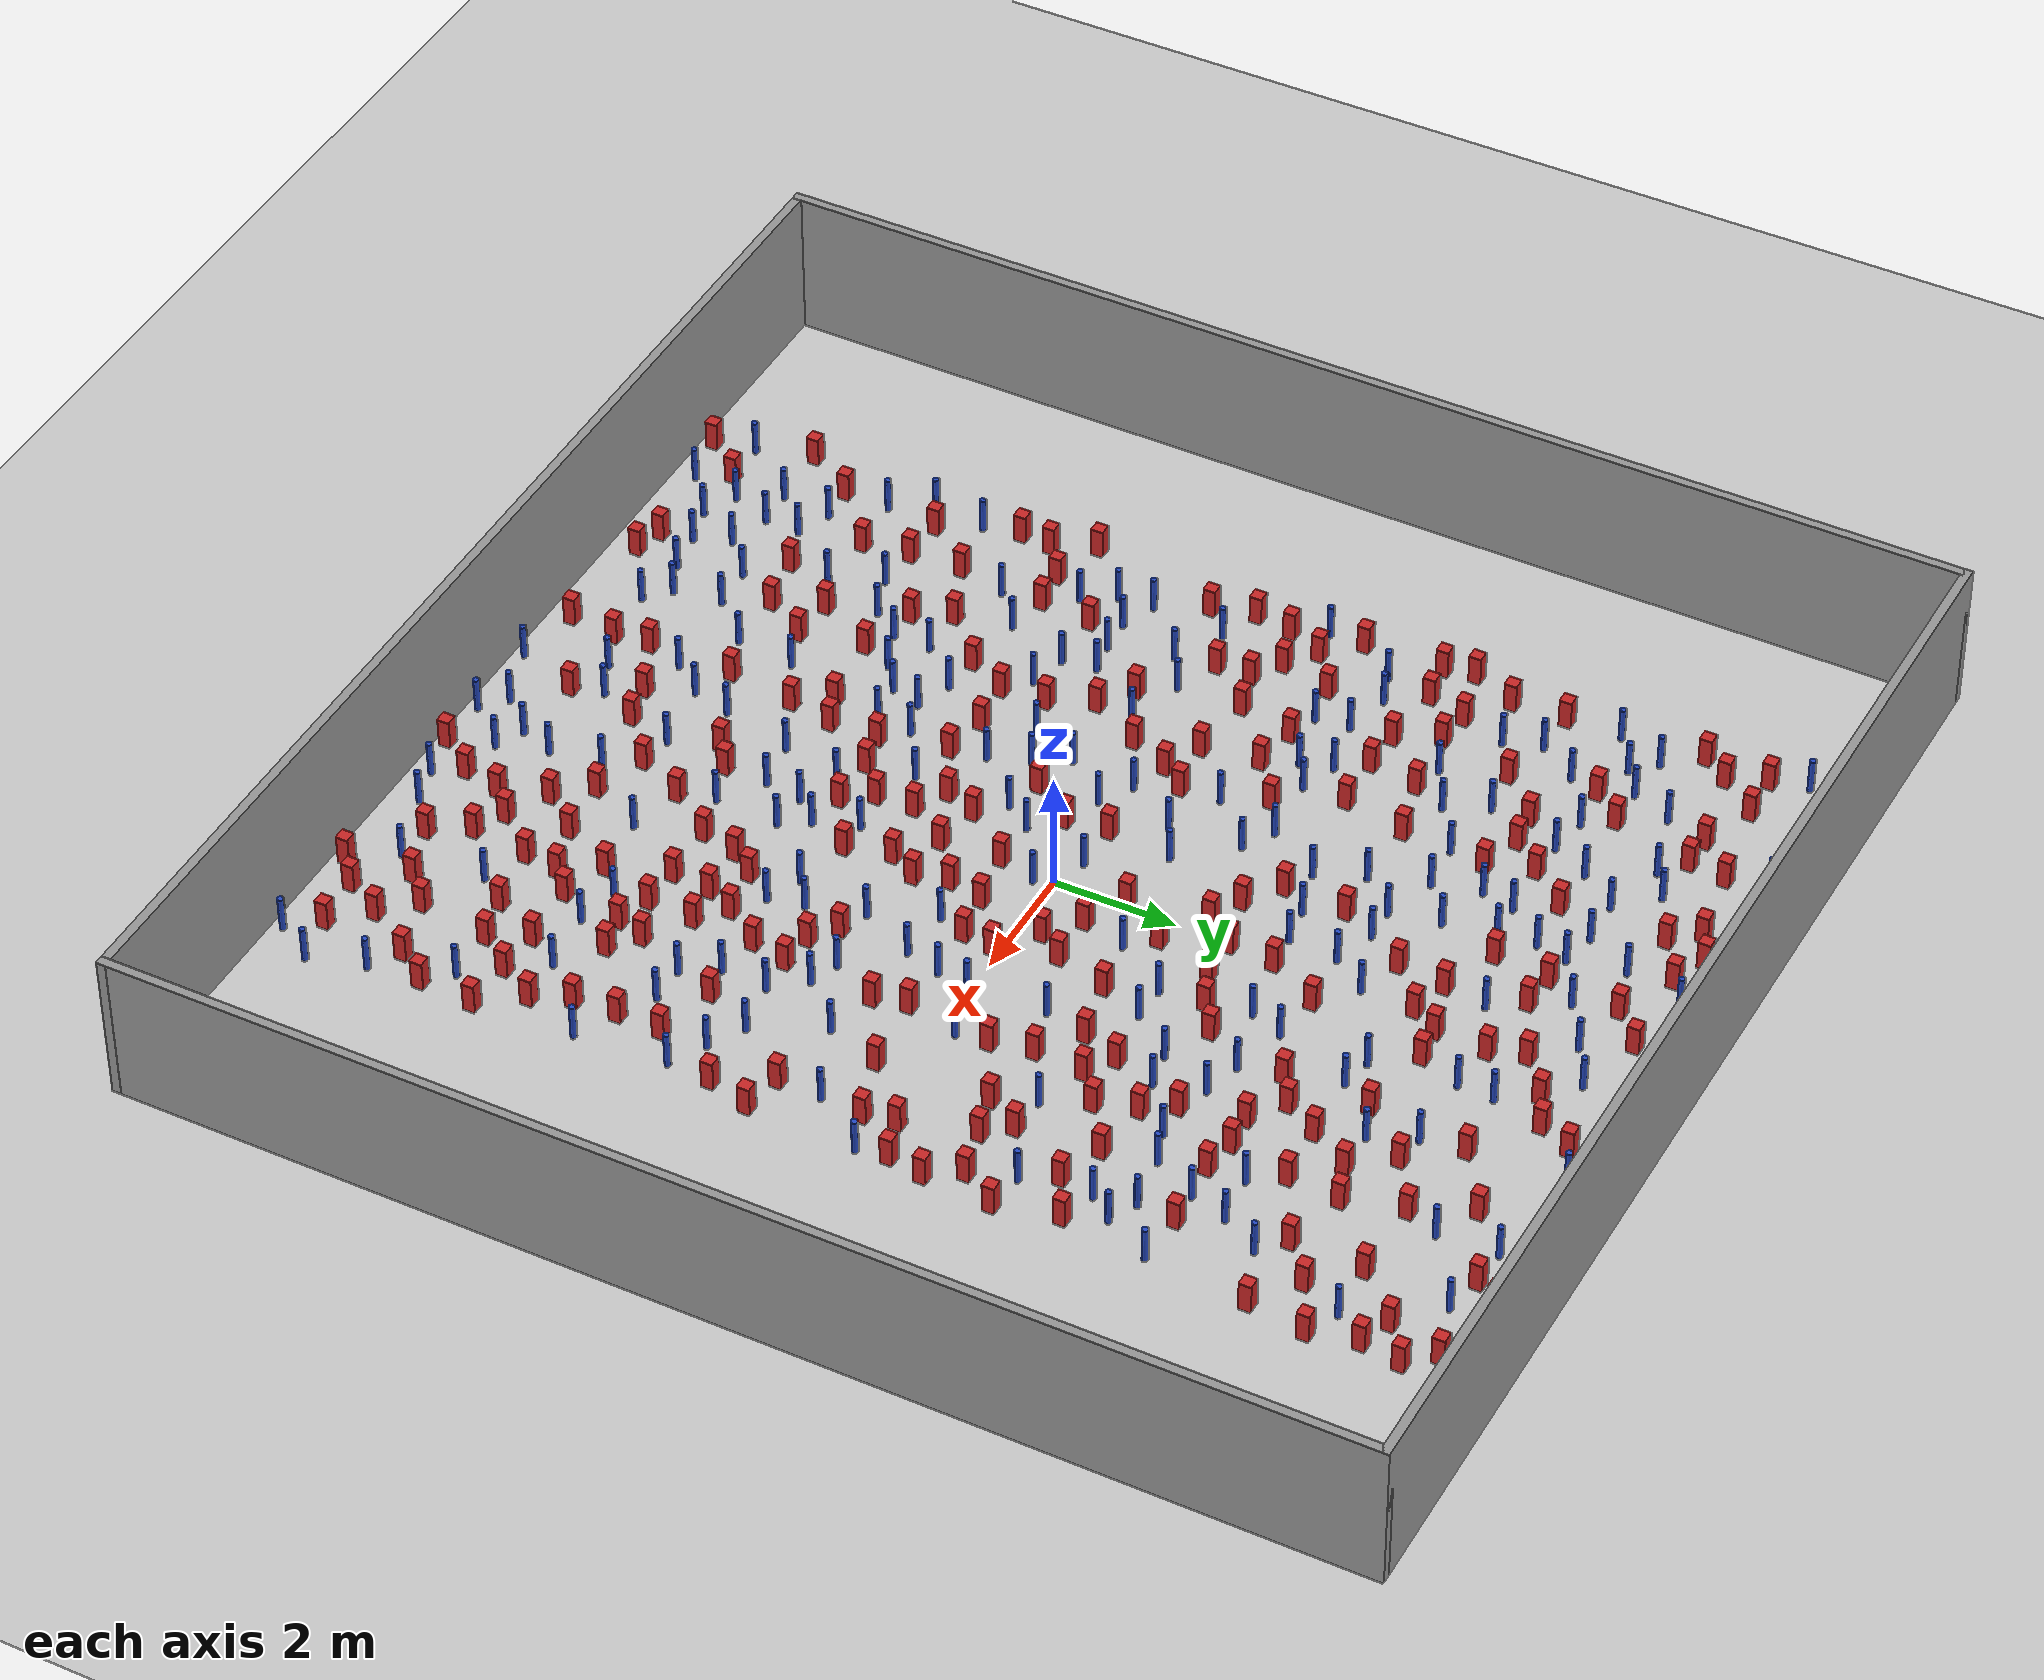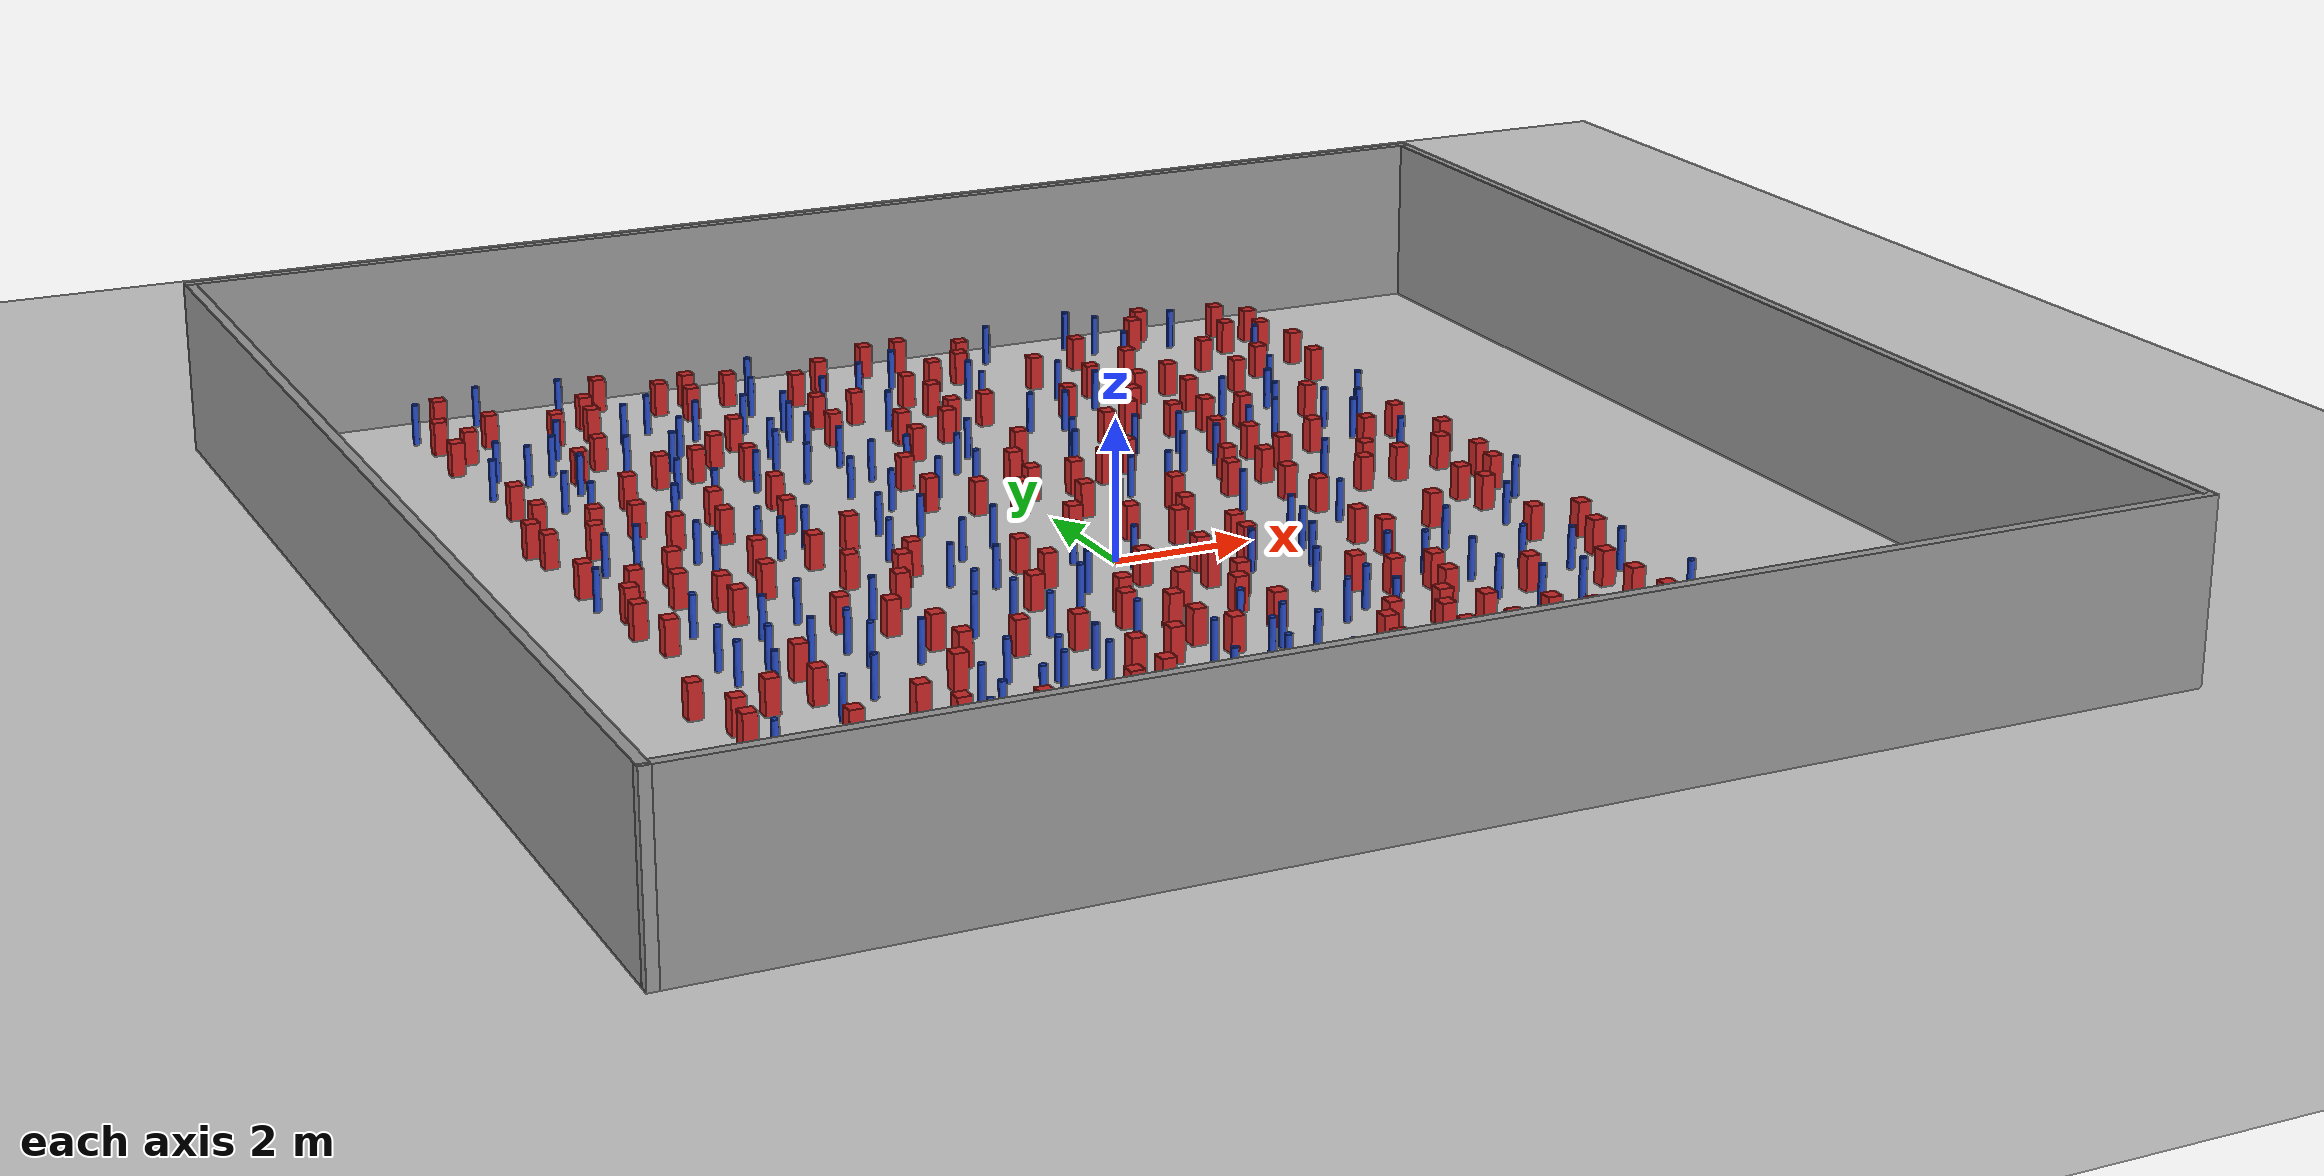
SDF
<sdf version="1.6">
 <world name="default">
  <light name="sun" type="directional">
   <pose>0 0 1000 0 -0 0</pose>
   <diffuse>0.8 0.8 0.8 1</diffuse>
   <specular>0.1 0.1 0.1 1</specular>
   <attenuation>
    <range>1000</range>
    <constant>0.9</constant>
    <linear>0.01</linear>
    <quadratic>0.001</quadratic>
   </attenuation>
   <direction>-0.5 0.5 -1</direction>
  </light>
  <model name="ground_plane">
   <static>1</static>
   <link name="link">
    <collision name="collision">
     <geometry><plane><normal>0 0 1</normal><size>100 100</size></plane></geometry>
     <surface><friction><ode><mu>100</mu><mu2>50</mu2></ode></friction></surface>
    </collision>
    <visual name="visual">
     <cast_shadows>0</cast_shadows>
     <geometry><plane><normal>0 0 1</normal><size>100 100</size></plane></geometry>
     <material>
      <ambient>1.0 1.0 1.0 1.0</ambient>
      <diffuse>0.8 0.8 0.8 1.0</diffuse>
      <specular>0.01 0.01 0.01 1.000000</specular>
     </material>
    </visual>
   </link>
  </model>
  <gravity>0 0 -9.8</gravity>
  <magnetic_field>6e-06 2.3e-05 -4.2e-05</magnetic_field>
  <atmosphere type="adiabatic"/>
  <physics name="default_physics" default="0" type="ode">
   <max_step_size>0.001</max_step_size>
   <real_time_factor>1</real_time_factor>
   <real_time_update_rate>1000</real_time_update_rate>
  </physics>
  <scene><ambient>0.4 0.4 0.4 1</ambient><background>0.7 0.7 0.7 1</background><shadows>1</shadows></scene>
  <spherical_coordinates>
   <surface_model>EARTH_WGS84</surface_model>
   <latitude_deg>0</latitude_deg>
   <longitude_deg>0</longitude_deg>
   <elevation>0</elevation>
   <heading_deg>0</heading_deg>
  </spherical_coordinates>
  <plugin name="gazebo_occupancy_map" filename="libgazebo_2Dmap_plugin.so">
   <map_resolution>0.05</map_resolution>
   <map_topic>generated_map</map_topic>
   <map_height>0.01</map_height>
   <map_size_x>50</map_size_x>
   <map_size_y>50</map_size_y>
  </plugin>
  <model name="NamedLocations">
   <static>true</static>
   <link name="DefaultStart"><pose>8.5 0 0 0 0 3.14</pose></link>
  </model>
  <model name="20x20_walls">
   <pose>0.044518 0.176112 0 0 -0 0</pose>
   <link name="Wall_1">
    <collision name="Wall_1_Collision">
     <geometry><box><size>20 0.15 2.5</size></box></geometry>
     <pose>0 0 1.25 0 -0 0</pose>
    </collision>
    <visual name="Wall_1_Visual">
     <pose>0 0 1.25 0 -0 0</pose>
     <geometry><box><size>20 0.15 2.5</size></box></geometry>
     <material>
      <script><uri>file://media/materials/scripts/gazebo.material</uri><name>Gazebo/Grey</name></script>
      <ambient>0.976471 0.992157 1 1</ambient>
     </material>
     <meta><layer>0</layer></meta>
    </visual>
    <pose>0 9.925 0 0 -0 0</pose>
   </link>
   <link name="Wall_3">
    <collision name="Wall_3_Collision">
     <geometry><box><size>20 0.15 2.5</size></box></geometry>
     <pose>0 0 1.25 0 -0 0</pose>
    </collision>
    <visual name="Wall_3_Visual">
     <pose>0 0 1.25 0 -0 0</pose>
     <geometry><box><size>20 0.15 2.5</size></box></geometry>
     <material>
      <script><uri>file://media/materials/scripts/gazebo.material</uri><name>Gazebo/Grey</name></script>
      <ambient>0.976471 0.992157 1 1</ambient>
     </material>
     <meta><layer>0</layer></meta>
    </visual>
    <pose>9.925 0 0 0 0 -1.5708</pose>
   </link>
   <link name="Wall_4">
    <collision name="Wall_4_Collision">
     <geometry><box><size>20 0.15 2.5</size></box></geometry>
     <pose>0 0 1.25 0 -0 0</pose>
    </collision>
    <visual name="Wall_4_Visual">
     <pose>0 0 1.25 0 -0 0</pose>
     <geometry><box><size>20 0.15 2.5</size></box></geometry>
     <material>
      <script><uri>file://media/materials/scripts/gazebo.material</uri><name>Gazebo/Grey</name></script>
      <ambient>0.976471 0.992157 1 1</ambient>
     </material>
     <meta><layer>0</layer></meta>
    </visual>
    <pose>0 -9.925 0 0 -0 3.14159</pose>
   </link>
   <link name="Wall_5">
    <collision name="Wall_5_Collision">
     <geometry><box><size>20 0.15 2.5</size></box></geometry>
     <pose>0 0 1.25 0 -0 0</pose>
    </collision>
    <visual name="Wall_5_Visual">
     <pose>0 0 1.25 0 -0 0</pose>
     <geometry><box><size>20 0.15 2.5</size></box></geometry>
     <material>
      <script><uri>file://media/materials/scripts/gazebo.material</uri><name>Gazebo/Grey</name></script>
      <ambient>0.976471 0.992157 1 1</ambient>
     </material>
     <meta><layer>0</layer></meta>
    </visual>
    <pose>-9.925 0 0 0 -0 1.5708</pose>
   </link>
   <static>1</static>
  </model>
  <model name="square_post_obstacle0">
   <static>true</static>
   <pose>-5.44429254474 -3.06406377027 -6.11067671241e-07 -5.50515727128e-06 -8.79689657224e-07 2.37013304536e-05</pose>
   <link name="link">
    <pose>0 0 0.25 0 -0 0</pose>
    <inertial>
     <mass>100</mass>
     <inertia>
      <ixx>0.166667</ixx>
      <ixy>0</ixy>
      <ixz>0</ixz>
      <iyy>0.166667</iyy>
      <iyz>0</iyz>
      <izz>0.166667</izz>
     </inertia>
    </inertial>
    <collision name="collision"><geometry><box><size>.2 .2 .5</size></box></geometry></collision>
    <visual name="visual">
     <geometry><box><size>.2 .2 .5</size></box></geometry>
     <material>
      <script><name>Gazebo/Red</name><uri>file://media/materials/scripts/gazebo.material</uri></script>
     </material>
    </visual>
   </link>
  </model>
  <model name="square_post_obstacle1">
   <static>true</static>
   <pose>-4.43478799256 5.60635360272 -6.11067671241e-07 -5.50515727128e-06 -8.79689657224e-07 2.37013304536e-05</pose>
   <link name="link">
    <pose>0 0 0.25 0 -0 0</pose>
    <inertial>
     <mass>100</mass>
     <inertia>
      <ixx>0.166667</ixx>
      <ixy>0</ixy>
      <ixz>0</ixz>
      <iyy>0.166667</iyy>
      <iyz>0</iyz>
      <izz>0.166667</izz>
     </inertia>
    </inertial>
    <collision name="collision"><geometry><box><size>.2 .2 .5</size></box></geometry></collision>
    <visual name="visual">
     <geometry><box><size>.2 .2 .5</size></box></geometry>
     <material>
      <script><name>Gazebo/Red</name><uri>file://media/materials/scripts/gazebo.material</uri></script>
     </material>
    </visual>
   </link>
  </model>
  <model name="pole_obstacle0">
   <static>true</static>
   <pose>-1.83436711731 -0.227464030052 -9.47619616065e-06 5.49618799737e-07 2.36310414055e-07 -1.55090534804e-07</pose>
   <link name="link">
    <pose>0 0 0.3 0 -0 0</pose>
    <inertial>
     <mass>1</mass>
     <inertia><ixx>0.145833</ixx><ixy>0</ixy><ixz>0</ixz><iyy>0.145833</iyy><iyz>0</iyz><izz>0.125</izz></inertia>
    </inertial>
    <collision name="collision">
     <geometry><cylinder><radius>0.05</radius><length>.6</length></cylinder></geometry>
    </collision>
    <visual name="visual">
     <geometry><cylinder><radius>0.05</radius><length>.6</length></cylinder></geometry>
     <material>
      <script><name>Gazebo/Blue</name><uri>file://media/materials/scripts/gazebo.material</uri></script>
     </material>
    </visual>
   </link>
  </model>
  <model name="square_post_obstacle2">
   <static>true</static>
   <pose>6.30857068601 8.03620668134 -6.11067671241e-07 -5.50515727128e-06 -8.79689657224e-07 2.37013304536e-05</pose>
   <link name="link">
    <pose>0 0 0.25 0 -0 0</pose>
    <inertial>
     <mass>100</mass>
     <inertia>
      <ixx>0.166667</ixx>
      <ixy>0</ixy>
      <ixz>0</ixz>
      <iyy>0.166667</iyy>
      <iyz>0</iyz>
      <izz>0.166667</izz>
     </inertia>
    </inertial>
    <collision name="collision"><geometry><box><size>.2 .2 .5</size></box></geometry></collision>
    <visual name="visual">
     <geometry><box><size>.2 .2 .5</size></box></geometry>
     <material>
      <script><name>Gazebo/Red</name><uri>file://media/materials/scripts/gazebo.material</uri></script>
     </material>
    </visual>
   </link>
  </model>
  <model name="pole_obstacle1">
   <static>true</static>
   <pose>-5.62566144421 -9.2903090047 -9.47619616065e-06 5.49618799737e-07 2.36310414065e-07 -1.55090534796e-07</pose>
   <link name="link">
    <pose>0 0 0.3 0 -0 0</pose>
    <inertial>
     <mass>1</mass>
     <inertia><ixx>0.145833</ixx><ixy>0</ixy><ixz>0</ixz><iyy>0.145833</iyy><iyz>0</iyz><izz>0.125</izz></inertia>
    </inertial>
    <collision name="collision">
     <geometry><cylinder><radius>0.05</radius><length>.6</length></cylinder></geometry>
    </collision>
    <visual name="visual">
     <geometry><cylinder><radius>0.05</radius><length>.6</length></cylinder></geometry>
     <material>
      <script><name>Gazebo/Blue</name><uri>file://media/materials/scripts/gazebo.material</uri></script>
     </material>
    </visual>
   </link>
  </model>
  <model name="square_post_obstacle3">
   <static>true</static>
   <pose>0.34875297249 7.15030938132 -6.11067671241e-07 -5.50515727128e-06 -8.79689657224e-07 2.37013304536e-05</pose>
   <link name="link">
    <pose>0 0 0.25 0 -0 0</pose>
    <inertial>
     <mass>100</mass>
     <inertia>
      <ixx>0.166667</ixx>
      <ixy>0</ixy>
      <ixz>0</ixz>
      <iyy>0.166667</iyy>
      <iyz>0</iyz>
      <izz>0.166667</izz>
     </inertia>
    </inertial>
    <collision name="collision"><geometry><box><size>.2 .2 .5</size></box></geometry></collision>
    <visual name="visual">
     <geometry><box><size>.2 .2 .5</size></box></geometry>
     <material>
      <script><name>Gazebo/Red</name><uri>file://media/materials/scripts/gazebo.material</uri></script>
     </material>
    </visual>
   </link>
  </model>
  <model name="pole_obstacle2">
   <static>true</static>
   <pose>-1.60684436853 -7.26357903362 -9.47619616065e-06 5.49618799737e-07 2.36310414061e-07 -1.550905348e-07</pose>
   <link name="link">
    <pose>0 0 0.3 0 -0 0</pose>
    <inertial>
     <mass>1</mass>
     <inertia><ixx>0.145833</ixx><ixy>0</ixy><ixz>0</ixz><iyy>0.145833</iyy><iyz>0</iyz><izz>0.125</izz></inertia>
    </inertial>
    <collision name="collision">
     <geometry><cylinder><radius>0.05</radius><length>.6</length></cylinder></geometry>
    </collision>
    <visual name="visual">
     <geometry><cylinder><radius>0.05</radius><length>.6</length></cylinder></geometry>
     <material>
      <script><name>Gazebo/Blue</name><uri>file://media/materials/scripts/gazebo.material</uri></script>
     </material>
    </visual>
   </link>
  </model>
  <model name="pole_obstacle3">
   <static>true</static>
   <pose>-1.09027371918 4.62594508473 -9.47619616065e-06 5.49618799737e-07 2.36310414061e-07 -1.550905348e-07</pose>
   <link name="link">
    <pose>0 0 0.3 0 -0 0</pose>
    <inertial>
     <mass>1</mass>
     <inertia><ixx>0.145833</ixx><ixy>0</ixy><ixz>0</ixz><iyy>0.145833</iyy><iyz>0</iyz><izz>0.125</izz></inertia>
    </inertial>
    <collision name="collision">
     <geometry><cylinder><radius>0.05</radius><length>.6</length></cylinder></geometry>
    </collision>
    <visual name="visual">
     <geometry><cylinder><radius>0.05</radius><length>.6</length></cylinder></geometry>
     <material>
      <script><name>Gazebo/Blue</name><uri>file://media/materials/scripts/gazebo.material</uri></script>
     </material>
    </visual>
   </link>
  </model>
  <model name="square_post_obstacle4">
   <static>true</static>
   <pose>4.27000740854 -8.36256400304 -6.11067671241e-07 -5.50515727128e-06 -8.79689657224e-07 2.37013304536e-05</pose>
   <link name="link">
    <pose>0 0 0.25 0 -0 0</pose>
    <inertial>
     <mass>100</mass>
     <inertia>
      <ixx>0.166667</ixx>
      <ixy>0</ixy>
      <ixz>0</ixz>
      <iyy>0.166667</iyy>
      <iyz>0</iyz>
      <izz>0.166667</izz>
     </inertia>
    </inertial>
    <collision name="collision"><geometry><box><size>.2 .2 .5</size></box></geometry></collision>
    <visual name="visual">
     <geometry><box><size>.2 .2 .5</size></box></geometry>
     <material>
      <script><name>Gazebo/Red</name><uri>file://media/materials/scripts/gazebo.material</uri></script>
     </material>
    </visual>
   </link>
  </model>
  <model name="square_post_obstacle5">
   <static>true</static>
   <pose>-0.324473289553 2.40058144093 -6.11067671241e-07 -5.50515727128e-06 -8.79689657224e-07 2.37013304536e-05</pose>
   <link name="link">
    <pose>0 0 0.25 0 -0 0</pose>
    <inertial>
     <mass>100</mass>
     <inertia>
      <ixx>0.166667</ixx>
      <ixy>0</ixy>
      <ixz>0</ixz>
      <iyy>0.166667</iyy>
      <iyz>0</iyz>
      <izz>0.166667</izz>
     </inertia>
    </inertial>
    <collision name="collision"><geometry><box><size>.2 .2 .5</size></box></geometry></collision>
    <visual name="visual">
     <geometry><box><size>.2 .2 .5</size></box></geometry>
     <material>
      <script><name>Gazebo/Red</name><uri>file://media/materials/scripts/gazebo.material</uri></script>
     </material>
    </visual>
   </link>
  </model>
  <model name="square_post_obstacle6">
   <static>true</static>
   <pose>-6.67891821965 -0.000595044972764 -6.11067671241e-07 -5.50515727128e-06 -8.79689657224e-07 2.37013304536e-05</pose>
   <link name="link">
    <pose>0 0 0.25 0 -0 0</pose>
    <inertial>
     <mass>100</mass>
     <inertia>
      <ixx>0.166667</ixx>
      <ixy>0</ixy>
      <ixz>0</ixz>
      <iyy>0.166667</iyy>
      <iyz>0</iyz>
      <izz>0.166667</izz>
     </inertia>
    </inertial>
    <collision name="collision"><geometry><box><size>.2 .2 .5</size></box></geometry></collision>
    <visual name="visual">
     <geometry><box><size>.2 .2 .5</size></box></geometry>
     <material>
      <script><name>Gazebo/Red</name><uri>file://media/materials/scripts/gazebo.material</uri></script>
     </material>
    </visual>
   </link>
  </model>
  <model name="pole_obstacle4">
   <static>true</static>
   <pose>-6.32064139587 2.37381360721 -9.47619616065e-06 5.49618799738e-07 2.36310414051e-07 -1.55090534805e-07</pose>
   <link name="link">
    <pose>0 0 0.3 0 -0 0</pose>
    <inertial>
     <mass>1</mass>
     <inertia><ixx>0.145833</ixx><ixy>0</ixy><ixz>0</ixz><iyy>0.145833</iyy><iyz>0</iyz><izz>0.125</izz></inertia>
    </inertial>
    <collision name="collision">
     <geometry><cylinder><radius>0.05</radius><length>.6</length></cylinder></geometry>
    </collision>
    <visual name="visual">
     <geometry><cylinder><radius>0.05</radius><length>.6</length></cylinder></geometry>
     <material>
      <script><name>Gazebo/Blue</name><uri>file://media/materials/scripts/gazebo.material</uri></script>
     </material>
    </visual>
   </link>
  </model>
  <model name="pole_obstacle5">
   <static>true</static>
   <pose>-5.575924807 -1.74550367517 -9.47619616065e-06 5.49618799738e-07 2.36310414071e-07 -1.55090534796e-07</pose>
   <link name="link">
    <pose>0 0 0.3 0 -0 0</pose>
    <inertial>
     <mass>1</mass>
     <inertia><ixx>0.145833</ixx><ixy>0</ixy><ixz>0</ixz><iyy>0.145833</iyy><iyz>0</iyz><izz>0.125</izz></inertia>
    </inertial>
    <collision name="collision">
     <geometry><cylinder><radius>0.05</radius><length>.6</length></cylinder></geometry>
    </collision>
    <visual name="visual">
     <geometry><cylinder><radius>0.05</radius><length>.6</length></cylinder></geometry>
     <material>
      <script><name>Gazebo/Blue</name><uri>file://media/materials/scripts/gazebo.material</uri></script>
     </material>
    </visual>
   </link>
  </model>
  <model name="square_post_obstacle7">
   <static>true</static>
   <pose>0.875443202514 6.37340452609 -6.11067671241e-07 -5.50515727128e-06 -8.79689657224e-07 2.37013304536e-05</pose>
   <link name="link">
    <pose>0 0 0.25 0 -0 0</pose>
    <inertial>
     <mass>100</mass>
     <inertia>
      <ixx>0.166667</ixx>
      <ixy>0</ixy>
      <ixz>0</ixz>
      <iyy>0.166667</iyy>
      <iyz>0</iyz>
      <izz>0.166667</izz>
     </inertia>
    </inertial>
    <collision name="collision"><geometry><box><size>.2 .2 .5</size></box></geometry></collision>
    <visual name="visual">
     <geometry><box><size>.2 .2 .5</size></box></geometry>
     <material>
      <script><name>Gazebo/Red</name><uri>file://media/materials/scripts/gazebo.material</uri></script>
     </material>
    </visual>
   </link>
  </model>
  <model name="square_post_obstacle8">
   <static>true</static>
   <pose>-4.27476580129 -0.846139673667 -6.11067671241e-07 -5.50515727128e-06 -8.79689657224e-07 2.37013304536e-05</pose>
   <link name="link">
    <pose>0 0 0.25 0 -0 0</pose>
    <inertial>
     <mass>100</mass>
     <inertia>
      <ixx>0.166667</ixx>
      <ixy>0</ixy>
      <ixz>0</ixz>
      <iyy>0.166667</iyy>
      <iyz>0</iyz>
      <izz>0.166667</izz>
     </inertia>
    </inertial>
    <collision name="collision"><geometry><box><size>.2 .2 .5</size></box></geometry></collision>
    <visual name="visual">
     <geometry><box><size>.2 .2 .5</size></box></geometry>
     <material>
      <script><name>Gazebo/Red</name><uri>file://media/materials/scripts/gazebo.material</uri></script>
     </material>
    </visual>
   </link>
  </model>
  <model name="pole_obstacle6">
   <static>true</static>
   <pose>-3.7279872868 -4.7146031591 -9.4761961606e-06 5.49618799729e-07 2.36310414006e-07 -1.55090534822e-07</pose>
   <link name="link">
    <pose>0 0 0.3 0 -0 0</pose>
    <inertial>
     <mass>1</mass>
     <inertia><ixx>0.145833</ixx><ixy>0</ixy><ixz>0</ixz><iyy>0.145833</iyy><iyz>0</iyz><izz>0.125</izz></inertia>
    </inertial>
    <collision name="collision">
     <geometry><cylinder><radius>0.05</radius><length>.6</length></cylinder></geometry>
    </collision>
    <visual name="visual">
     <geometry><cylinder><radius>0.05</radius><length>.6</length></cylinder></geometry>
     <material>
      <script><name>Gazebo/Blue</name><uri>file://media/materials/scripts/gazebo.material</uri></script>
     </material>
    </visual>
   </link>
  </model>
  <model name="pole_obstacle7">
   <static>true</static>
   <pose>-5.21866244766 -7.79326274848 -9.47619616065e-06 5.49618799737e-07 2.36310414037e-07 -1.55090534814e-07</pose>
   <link name="link">
    <pose>0 0 0.3 0 -0 0</pose>
    <inertial>
     <mass>1</mass>
     <inertia><ixx>0.145833</ixx><ixy>0</ixy><ixz>0</ixz><iyy>0.145833</iyy><iyz>0</iyz><izz>0.125</izz></inertia>
    </inertial>
    <collision name="collision">
     <geometry><cylinder><radius>0.05</radius><length>.6</length></cylinder></geometry>
    </collision>
    <visual name="visual">
     <geometry><cylinder><radius>0.05</radius><length>.6</length></cylinder></geometry>
     <material>
      <script><name>Gazebo/Blue</name><uri>file://media/materials/scripts/gazebo.material</uri></script>
     </material>
    </visual>
   </link>
  </model>
  <model name="square_post_obstacle9">
   <static>true</static>
   <pose>-5.35893049867 -2.19606106675 -6.11067671241e-07 -5.50515727128e-06 -8.79689657224e-07 2.37013304536e-05</pose>
   <link name="link">
    <pose>0 0 0.25 0 -0 0</pose>
    <inertial>
     <mass>100</mass>
     <inertia>
      <ixx>0.166667</ixx>
      <ixy>0</ixy>
      <ixz>0</ixz>
      <iyy>0.166667</iyy>
      <iyz>0</iyz>
      <izz>0.166667</izz>
     </inertia>
    </inertial>
    <collision name="collision"><geometry><box><size>.2 .2 .5</size></box></geometry></collision>
    <visual name="visual">
     <geometry><box><size>.2 .2 .5</size></box></geometry>
     <material>
      <script><name>Gazebo/Red</name><uri>file://media/materials/scripts/gazebo.material</uri></script>
     </material>
    </visual>
   </link>
  </model>
  <model name="square_post_obstacle10">
   <static>true</static>
   <pose>5.50780573705 0.390450183729 -6.11067671241e-07 -5.50515727128e-06 -8.79689657224e-07 2.37013304536e-05</pose>
   <link name="link">
    <pose>0 0 0.25 0 -0 0</pose>
    <inertial>
     <mass>100</mass>
     <inertia>
      <ixx>0.166667</ixx>
      <ixy>0</ixy>
      <ixz>0</ixz>
      <iyy>0.166667</iyy>
      <iyz>0</iyz>
      <izz>0.166667</izz>
     </inertia>
    </inertial>
    <collision name="collision"><geometry><box><size>.2 .2 .5</size></box></geometry></collision>
    <visual name="visual">
     <geometry><box><size>.2 .2 .5</size></box></geometry>
     <material>
      <script><name>Gazebo/Red</name><uri>file://media/materials/scripts/gazebo.material</uri></script>
     </material>
    </visual>
   </link>
  </model>
  <model name="square_post_obstacle11">
   <static>true</static>
   <pose>-1.5191931623 -3.78393811664 -6.11067671241e-07 -5.50515727128e-06 -8.79689657224e-07 2.37013304536e-05</pose>
   <link name="link">
    <pose>0 0 0.25 0 -0 0</pose>
    <inertial>
     <mass>100</mass>
     <inertia>
      <ixx>0.166667</ixx>
      <ixy>0</ixy>
      <ixz>0</ixz>
      <iyy>0.166667</iyy>
      <iyz>0</iyz>
      <izz>0.166667</izz>
     </inertia>
    </inertial>
    <collision name="collision"><geometry><box><size>.2 .2 .5</size></box></geometry></collision>
    <visual name="visual">
     <geometry><box><size>.2 .2 .5</size></box></geometry>
     <material>
      <script><name>Gazebo/Red</name><uri>file://media/materials/scripts/gazebo.material</uri></script>
     </material>
    </visual>
   </link>
  </model>
  <model name="square_post_obstacle12">
   <static>true</static>
   <pose>-6.0545264636 8.45145739895 -6.11067671241e-07 -5.50515727128e-06 -8.79689657224e-07 2.37013304536e-05</pose>
   <link name="link">
    <pose>0 0 0.25 0 -0 0</pose>
    <inertial>
     <mass>100</mass>
     <inertia>
      <ixx>0.166667</ixx>
      <ixy>0</ixy>
      <ixz>0</ixz>
      <iyy>0.166667</iyy>
      <iyz>0</iyz>
      <izz>0.166667</izz>
     </inertia>
    </inertial>
    <collision name="collision"><geometry><box><size>.2 .2 .5</size></box></geometry></collision>
    <visual name="visual">
     <geometry><box><size>.2 .2 .5</size></box></geometry>
     <material>
      <script><name>Gazebo/Red</name><uri>file://media/materials/scripts/gazebo.material</uri></script>
     </material>
    </visual>
   </link>
  </model>
  <model name="square_post_obstacle13">
   <static>true</static>
   <pose>-1.71121926636 -1.15659849565 -6.11067671241e-07 -5.50515727128e-06 -8.79689657224e-07 2.37013304536e-05</pose>
   <link name="link">
    <pose>0 0 0.25 0 -0 0</pose>
    <inertial>
     <mass>100</mass>
     <inertia>
      <ixx>0.166667</ixx>
      <ixy>0</ixy>
      <ixz>0</ixz>
      <iyy>0.166667</iyy>
      <iyz>0</iyz>
      <izz>0.166667</izz>
     </inertia>
    </inertial>
    <collision name="collision"><geometry><box><size>.2 .2 .5</size></box></geometry></collision>
    <visual name="visual">
     <geometry><box><size>.2 .2 .5</size></box></geometry>
     <material>
      <script><name>Gazebo/Red</name><uri>file://media/materials/scripts/gazebo.material</uri></script>
     </material>
    </visual>
   </link>
  </model>
  <model name="pole_obstacle8">
   <static>true</static>
   <pose>4.84409418193 -3.91809828745 -9.47619616065e-06 5.49618799738e-07 2.36310414051e-07 -1.55090534805e-07</pose>
   <link name="link">
    <pose>0 0 0.3 0 -0 0</pose>
    <inertial>
     <mass>1</mass>
     <inertia><ixx>0.145833</ixx><ixy>0</ixy><ixz>0</ixz><iyy>0.145833</iyy><iyz>0</iyz><izz>0.125</izz></inertia>
    </inertial>
    <collision name="collision">
     <geometry><cylinder><radius>0.05</radius><length>.6</length></cylinder></geometry>
    </collision>
    <visual name="visual">
     <geometry><cylinder><radius>0.05</radius><length>.6</length></cylinder></geometry>
     <material>
      <script><name>Gazebo/Blue</name><uri>file://media/materials/scripts/gazebo.material</uri></script>
     </material>
    </visual>
   </link>
  </model>
  <model name="square_post_obstacle14">
   <static>true</static>
   <pose>-0.742302265317 8.96026885137 -6.11067671241e-07 -5.50515727128e-06 -8.79689657224e-07 2.37013304536e-05</pose>
   <link name="link">
    <pose>0 0 0.25 0 -0 0</pose>
    <inertial>
     <mass>100</mass>
     <inertia>
      <ixx>0.166667</ixx>
      <ixy>0</ixy>
      <ixz>0</ixz>
      <iyy>0.166667</iyy>
      <iyz>0</iyz>
      <izz>0.166667</izz>
     </inertia>
    </inertial>
    <collision name="collision"><geometry><box><size>.2 .2 .5</size></box></geometry></collision>
    <visual name="visual">
     <geometry><box><size>.2 .2 .5</size></box></geometry>
     <material>
      <script><name>Gazebo/Red</name><uri>file://media/materials/scripts/gazebo.material</uri></script>
     </material>
    </visual>
   </link>
  </model>
  <model name="square_post_obstacle15">
   <static>true</static>
   <pose>5.60202587093 -0.11802808626 -6.11067671241e-07 -5.50515727128e-06 -8.79689657224e-07 2.37013304536e-05</pose>
   <link name="link">
    <pose>0 0 0.25 0 -0 0</pose>
    <inertial>
     <mass>100</mass>
     <inertia>
      <ixx>0.166667</ixx>
      <ixy>0</ixy>
      <ixz>0</ixz>
      <iyy>0.166667</iyy>
      <iyz>0</iyz>
      <izz>0.166667</izz>
     </inertia>
    </inertial>
    <collision name="collision"><geometry><box><size>.2 .2 .5</size></box></geometry></collision>
    <visual name="visual">
     <geometry><box><size>.2 .2 .5</size></box></geometry>
     <material>
      <script><name>Gazebo/Red</name><uri>file://media/materials/scripts/gazebo.material</uri></script>
     </material>
    </visual>
   </link>
  </model>
  <model name="square_post_obstacle16">
   <static>true</static>
   <pose>-4.17505439991 -9.06867833993 -6.11067671241e-07 -5.50515727128e-06 -8.79689657224e-07 2.37013304536e-05</pose>
   <link name="link">
    <pose>0 0 0.25 0 -0 0</pose>
    <inertial>
     <mass>100</mass>
     <inertia>
      <ixx>0.166667</ixx>
      <ixy>0</ixy>
      <ixz>0</ixz>
      <iyy>0.166667</iyy>
      <iyz>0</iyz>
      <izz>0.166667</izz>
     </inertia>
    </inertial>
    <collision name="collision"><geometry><box><size>.2 .2 .5</size></box></geometry></collision>
    <visual name="visual">
     <geometry><box><size>.2 .2 .5</size></box></geometry>
     <material>
      <script><name>Gazebo/Red</name><uri>file://media/materials/scripts/gazebo.material</uri></script>
     </material>
    </visual>
   </link>
  </model>
  <model name="pole_obstacle9">
   <static>true</static>
   <pose>-6.44895518481 6.81430109673 -9.47619616065e-06 5.49618799737e-07 2.36310414037e-07 -1.55090534814e-07</pose>
   <link name="link">
    <pose>0 0 0.3 0 -0 0</pose>
    <inertial>
     <mass>1</mass>
     <inertia><ixx>0.145833</ixx><ixy>0</ixy><ixz>0</ixz><iyy>0.145833</iyy><iyz>0</iyz><izz>0.125</izz></inertia>
    </inertial>
    <collision name="collision">
     <geometry><cylinder><radius>0.05</radius><length>.6</length></cylinder></geometry>
    </collision>
    <visual name="visual">
     <geometry><cylinder><radius>0.05</radius><length>.6</length></cylinder></geometry>
     <material>
      <script><name>Gazebo/Blue</name><uri>file://media/materials/scripts/gazebo.material</uri></script>
     </material>
    </visual>
   </link>
  </model>
  <model name="square_post_obstacle17">
   <static>true</static>
   <pose>0.452096644174 1.9528965727 -6.11067671241e-07 -5.50515727128e-06 -8.79689657224e-07 2.37013304536e-05</pose>
   <link name="link">
    <pose>0 0 0.25 0 -0 0</pose>
    <inertial>
     <mass>100</mass>
     <inertia>
      <ixx>0.166667</ixx>
      <ixy>0</ixy>
      <ixz>0</ixz>
      <iyy>0.166667</iyy>
      <iyz>0</iyz>
      <izz>0.166667</izz>
     </inertia>
    </inertial>
    <collision name="collision"><geometry><box><size>.2 .2 .5</size></box></geometry></collision>
    <visual name="visual">
     <geometry><box><size>.2 .2 .5</size></box></geometry>
     <material>
      <script><name>Gazebo/Red</name><uri>file://media/materials/scripts/gazebo.material</uri></script>
     </material>
    </visual>
   </link>
  </model>
  <model name="square_post_obstacle18">
   <static>true</static>
   <pose>-5.42857553846 3.71930864042 -6.11067671241e-07 -5.50515727128e-06 -8.79689657224e-07 2.37013304536e-05</pose>
   <link name="link">
    <pose>0 0 0.25 0 -0 0</pose>
    <inertial>
     <mass>100</mass>
     <inertia>
      <ixx>0.166667</ixx>
      <ixy>0</ixy>
      <ixz>0</ixz>
      <iyy>0.166667</iyy>
      <iyz>0</iyz>
      <izz>0.166667</izz>
     </inertia>
    </inertial>
    <collision name="collision"><geometry><box><size>.2 .2 .5</size></box></geometry></collision>
    <visual name="visual">
     <geometry><box><size>.2 .2 .5</size></box></geometry>
     <material>
      <script><name>Gazebo/Red</name><uri>file://media/materials/scripts/gazebo.material</uri></script>
     </material>
    </visual>
   </link>
  </model>
  <model name="pole_obstacle10">
   <static>true</static>
   <pose>-3.52547507397 2.32096026912 -9.47619616065e-06 5.49618799737e-07 2.36310414067e-07 -1.55090534797e-07</pose>
   <link name="link">
    <pose>0 0 0.3 0 -0 0</pose>
    <inertial>
     <mass>1</mass>
     <inertia><ixx>0.145833</ixx><ixy>0</ixy><ixz>0</ixz><iyy>0.145833</iyy><iyz>0</iyz><izz>0.125</izz></inertia>
    </inertial>
    <collision name="collision">
     <geometry><cylinder><radius>0.05</radius><length>.6</length></cylinder></geometry>
    </collision>
    <visual name="visual">
     <geometry><cylinder><radius>0.05</radius><length>.6</length></cylinder></geometry>
     <material>
      <script><name>Gazebo/Blue</name><uri>file://media/materials/scripts/gazebo.material</uri></script>
     </material>
    </visual>
   </link>
  </model>
  <model name="square_post_obstacle19">
   <static>true</static>
   <pose>0.642465242177 -2.33366304643 -6.11067671241e-07 -5.50515727128e-06 -8.79689657224e-07 2.37013304536e-05</pose>
   <link name="link">
    <pose>0 0 0.25 0 -0 0</pose>
    <inertial>
     <mass>100</mass>
     <inertia>
      <ixx>0.166667</ixx>
      <ixy>0</ixy>
      <ixz>0</ixz>
      <iyy>0.166667</iyy>
      <iyz>0</iyz>
      <izz>0.166667</izz>
     </inertia>
    </inertial>
    <collision name="collision"><geometry><box><size>.2 .2 .5</size></box></geometry></collision>
    <visual name="visual">
     <geometry><box><size>.2 .2 .5</size></box></geometry>
     <material>
      <script><name>Gazebo/Red</name><uri>file://media/materials/scripts/gazebo.material</uri></script>
     </material>
    </visual>
   </link>
  </model>
  <model name="pole_obstacle11">
   <static>true</static>
   <pose>-5.04784760389 2.35746795812 -9.47619616065e-06 5.49618799738e-07 2.36310414051e-07 -1.55090534805e-07</pose>
   <link name="link">
    <pose>0 0 0.3 0 -0 0</pose>
    <inertial>
     <mass>1</mass>
     <inertia><ixx>0.145833</ixx><ixy>0</ixy><ixz>0</ixz><iyy>0.145833</iyy><iyz>0</iyz><izz>0.125</izz></inertia>
    </inertial>
    <collision name="collision">
     <geometry><cylinder><radius>0.05</radius><length>.6</length></cylinder></geometry>
    </collision>
    <visual name="visual">
     <geometry><cylinder><radius>0.05</radius><length>.6</length></cylinder></geometry>
     <material>
      <script><name>Gazebo/Blue</name><uri>file://media/materials/scripts/gazebo.material</uri></script>
     </material>
    </visual>
   </link>
  </model>
  <model name="square_post_obstacle20">
   <static>true</static>
   <pose>6.4873067014 7.27600624761 -6.11067671241e-07 -5.50515727128e-06 -8.79689657224e-07 2.37013304536e-05</pose>
   <link name="link">
    <pose>0 0 0.25 0 -0 0</pose>
    <inertial>
     <mass>100</mass>
     <inertia>
      <ixx>0.166667</ixx>
      <ixy>0</ixy>
      <ixz>0</ixz>
      <iyy>0.166667</iyy>
      <iyz>0</iyz>
      <izz>0.166667</izz>
     </inertia>
    </inertial>
    <collision name="collision"><geometry><box><size>.2 .2 .5</size></box></geometry></collision>
    <visual name="visual">
     <geometry><box><size>.2 .2 .5</size></box></geometry>
     <material>
      <script><name>Gazebo/Red</name><uri>file://media/materials/scripts/gazebo.material</uri></script>
     </material>
    </visual>
   </link>
  </model>
  <model name="pole_obstacle12">
   <static>true</static>
   <pose>3.94235569095 -2.61710450384 -9.47619616065e-06 5.49618799737e-07 2.36310414051e-07 -1.55090534807e-07</pose>
   <link name="link">
    <pose>0 0 0.3 0 -0 0</pose>
    <inertial>
     <mass>1</mass>
     <inertia><ixx>0.145833</ixx><ixy>0</ixy><ixz>0</ixz><iyy>0.145833</iyy><iyz>0</iyz><izz>0.125</izz></inertia>
    </inertial>
    <collision name="collision">
     <geometry><cylinder><radius>0.05</radius><length>.6</length></cylinder></geometry>
    </collision>
    <visual name="visual">
     <geometry><cylinder><radius>0.05</radius><length>.6</length></cylinder></geometry>
     <material>
      <script><name>Gazebo/Blue</name><uri>file://media/materials/scripts/gazebo.material</uri></script>
     </material>
    </visual>
   </link>
  </model>
  <model name="square_post_obstacle21">
   <static>true</static>
   <pose>-5.62746742056 1.71022988912 -6.11067671241e-07 -5.50515727128e-06 -8.79689657224e-07 2.37013304536e-05</pose>
   <link name="link">
    <pose>0 0 0.25 0 -0 0</pose>
    <inertial>
     <mass>100</mass>
     <inertia>
      <ixx>0.166667</ixx>
      <ixy>0</ixy>
      <ixz>0</ixz>
      <iyy>0.166667</iyy>
      <iyz>0</iyz>
      <izz>0.166667</izz>
     </inertia>
    </inertial>
    <collision name="collision"><geometry><box><size>.2 .2 .5</size></box></geometry></collision>
    <visual name="visual">
     <geometry><box><size>.2 .2 .5</size></box></geometry>
     <material>
      <script><name>Gazebo/Red</name><uri>file://media/materials/scripts/gazebo.material</uri></script>
     </material>
    </visual>
   </link>
  </model>
  <model name="pole_obstacle13">
   <static>true</static>
   <pose>-5.77130393373 -6.98679776958 -9.47619616065e-06 5.49618799737e-07 2.36310414037e-07 -1.55090534814e-07</pose>
   <link name="link">
    <pose>0 0 0.3 0 -0 0</pose>
    <inertial>
     <mass>1</mass>
     <inertia><ixx>0.145833</ixx><ixy>0</ixy><ixz>0</ixz><iyy>0.145833</iyy><iyz>0</iyz><izz>0.125</izz></inertia>
    </inertial>
    <collision name="collision">
     <geometry><cylinder><radius>0.05</radius><length>.6</length></cylinder></geometry>
    </collision>
    <visual name="visual">
     <geometry><cylinder><radius>0.05</radius><length>.6</length></cylinder></geometry>
     <material>
      <script><name>Gazebo/Blue</name><uri>file://media/materials/scripts/gazebo.material</uri></script>
     </material>
    </visual>
   </link>
  </model>
  <model name="square_post_obstacle22">
   <static>true</static>
   <pose>-2.55298718495 -2.57654762107 -6.11067671241e-07 -5.50515727128e-06 -8.79689657224e-07 2.37013304536e-05</pose>
   <link name="link">
    <pose>0 0 0.25 0 -0 0</pose>
    <inertial>
     <mass>100</mass>
     <inertia>
      <ixx>0.166667</ixx>
      <ixy>0</ixy>
      <ixz>0</ixz>
      <iyy>0.166667</iyy>
      <iyz>0</iyz>
      <izz>0.166667</izz>
     </inertia>
    </inertial>
    <collision name="collision"><geometry><box><size>.2 .2 .5</size></box></geometry></collision>
    <visual name="visual">
     <geometry><box><size>.2 .2 .5</size></box></geometry>
     <material>
      <script><name>Gazebo/Red</name><uri>file://media/materials/scripts/gazebo.material</uri></script>
     </material>
    </visual>
   </link>
  </model>
  <model name="pole_obstacle14">
   <static>true</static>
   <pose>2.88527145606 3.95405018933 -9.47619616065e-06 5.49618799738e-07 2.36310414038e-07 -1.55090534814e-07</pose>
   <link name="link">
    <pose>0 0 0.3 0 -0 0</pose>
    <inertial>
     <mass>1</mass>
     <inertia><ixx>0.145833</ixx><ixy>0</ixy><ixz>0</ixz><iyy>0.145833</iyy><iyz>0</iyz><izz>0.125</izz></inertia>
    </inertial>
    <collision name="collision">
     <geometry><cylinder><radius>0.05</radius><length>.6</length></cylinder></geometry>
    </collision>
    <visual name="visual">
     <geometry><cylinder><radius>0.05</radius><length>.6</length></cylinder></geometry>
     <material>
      <script><name>Gazebo/Blue</name><uri>file://media/materials/scripts/gazebo.material</uri></script>
     </material>
    </visual>
   </link>
  </model>
  <model name="pole_obstacle15">
   <static>true</static>
   <pose>-2.71424018267 -8.56463063946 -9.4761961606e-06 5.49618799729e-07 2.36310414e-07 -1.55090534824e-07</pose>
   <link name="link">
    <pose>0 0 0.3 0 -0 0</pose>
    <inertial>
     <mass>1</mass>
     <inertia><ixx>0.145833</ixx><ixy>0</ixy><ixz>0</ixz><iyy>0.145833</iyy><iyz>0</iyz><izz>0.125</izz></inertia>
    </inertial>
    <collision name="collision">
     <geometry><cylinder><radius>0.05</radius><length>.6</length></cylinder></geometry>
    </collision>
    <visual name="visual">
     <geometry><cylinder><radius>0.05</radius><length>.6</length></cylinder></geometry>
     <material>
      <script><name>Gazebo/Blue</name><uri>file://media/materials/scripts/gazebo.material</uri></script>
     </material>
    </visual>
   </link>
  </model>
  <model name="pole_obstacle16">
   <static>true</static>
   <pose>4.80402283533 -2.46391848756 -9.47619616065e-06 5.49618799738e-07 2.36310414051e-07 -1.55090534805e-07</pose>
   <link name="link">
    <pose>0 0 0.3 0 -0 0</pose>
    <inertial>
     <mass>1</mass>
     <inertia><ixx>0.145833</ixx><ixy>0</ixy><ixz>0</ixz><iyy>0.145833</iyy><iyz>0</iyz><izz>0.125</izz></inertia>
    </inertial>
    <collision name="collision">
     <geometry><cylinder><radius>0.05</radius><length>.6</length></cylinder></geometry>
    </collision>
    <visual name="visual">
     <geometry><cylinder><radius>0.05</radius><length>.6</length></cylinder></geometry>
     <material>
      <script><name>Gazebo/Blue</name><uri>file://media/materials/scripts/gazebo.material</uri></script>
     </material>
    </visual>
   </link>
  </model>
  <model name="square_post_obstacle23">
   <static>true</static>
   <pose>5.94209555654 1.71884393342 -6.11067671241e-07 -5.50515727128e-06 -8.79689657224e-07 2.37013304536e-05</pose>
   <link name="link">
    <pose>0 0 0.25 0 -0 0</pose>
    <inertial>
     <mass>100</mass>
     <inertia>
      <ixx>0.166667</ixx>
      <ixy>0</ixy>
      <ixz>0</ixz>
      <iyy>0.166667</iyy>
      <iyz>0</iyz>
      <izz>0.166667</izz>
     </inertia>
    </inertial>
    <collision name="collision"><geometry><box><size>.2 .2 .5</size></box></geometry></collision>
    <visual name="visual">
     <geometry><box><size>.2 .2 .5</size></box></geometry>
     <material>
      <script><name>Gazebo/Red</name><uri>file://media/materials/scripts/gazebo.material</uri></script>
     </material>
    </visual>
   </link>
  </model>
  <model name="pole_obstacle17">
   <static>true</static>
   <pose>5.39811109469 5.95545410937 -9.47619616065e-06 5.49618799737e-07 2.36310414037e-07 -1.55090534814e-07</pose>
   <link name="link">
    <pose>0 0 0.3 0 -0 0</pose>
    <inertial>
     <mass>1</mass>
     <inertia><ixx>0.145833</ixx><ixy>0</ixy><ixz>0</ixz><iyy>0.145833</iyy><iyz>0</iyz><izz>0.125</izz></inertia>
    </inertial>
    <collision name="collision">
     <geometry><cylinder><radius>0.05</radius><length>.6</length></cylinder></geometry>
    </collision>
    <visual name="visual">
     <geometry><cylinder><radius>0.05</radius><length>.6</length></cylinder></geometry>
     <material>
      <script><name>Gazebo/Blue</name><uri>file://media/materials/scripts/gazebo.material</uri></script>
     </material>
    </visual>
   </link>
  </model>
  <model name="square_post_obstacle24">
   <static>true</static>
   <pose>0.319986857414 6.30865224558 -6.11067671241e-07 -5.50515727128e-06 -8.79689657224e-07 2.37013304536e-05</pose>
   <link name="link">
    <pose>0 0 0.25 0 -0 0</pose>
    <inertial>
     <mass>100</mass>
     <inertia>
      <ixx>0.166667</ixx>
      <ixy>0</ixy>
      <ixz>0</ixz>
      <iyy>0.166667</iyy>
      <iyz>0</iyz>
      <izz>0.166667</izz>
     </inertia>
    </inertial>
    <collision name="collision"><geometry><box><size>.2 .2 .5</size></box></geometry></collision>
    <visual name="visual">
     <geometry><box><size>.2 .2 .5</size></box></geometry>
     <material>
      <script><name>Gazebo/Red</name><uri>file://media/materials/scripts/gazebo.material</uri></script>
     </material>
    </visual>
   </link>
  </model>
  <model name="square_post_obstacle25">
   <static>true</static>
   <pose>-5.11166240738 3.04003141146 -6.11067671241e-07 -5.50515727128e-06 -8.79689657224e-07 2.37013304536e-05</pose>
   <link name="link">
    <pose>0 0 0.25 0 -0 0</pose>
    <inertial>
     <mass>100</mass>
     <inertia>
      <ixx>0.166667</ixx>
      <ixy>0</ixy>
      <ixz>0</ixz>
      <iyy>0.166667</iyy>
      <iyz>0</iyz>
      <izz>0.166667</izz>
     </inertia>
    </inertial>
    <collision name="collision"><geometry><box><size>.2 .2 .5</size></box></geometry></collision>
    <visual name="visual">
     <geometry><box><size>.2 .2 .5</size></box></geometry>
     <material>
      <script><name>Gazebo/Red</name><uri>file://media/materials/scripts/gazebo.material</uri></script>
     </material>
    </visual>
   </link>
  </model>
  <model name="square_post_obstacle26">
   <static>true</static>
   <pose>5.43190930204 -4.22238837837 -6.11067671241e-07 -5.50515727128e-06 -8.79689657224e-07 2.37013304536e-05</pose>
   <link name="link">
    <pose>0 0 0.25 0 -0 0</pose>
    <inertial>
     <mass>100</mass>
     <inertia>
      <ixx>0.166667</ixx>
      <ixy>0</ixy>
      <ixz>0</ixz>
      <iyy>0.166667</iyy>
      <iyz>0</iyz>
      <izz>0.166667</izz>
     </inertia>
    </inertial>
    <collision name="collision"><geometry><box><size>.2 .2 .5</size></box></geometry></collision>
    <visual name="visual">
     <geometry><box><size>.2 .2 .5</size></box></geometry>
     <material>
      <script><name>Gazebo/Red</name><uri>file://media/materials/scripts/gazebo.material</uri></script>
     </material>
    </visual>
   </link>
  </model>
  <model name="square_post_obstacle27">
   <static>true</static>
   <pose>4.91320004879 -6.72935652922 -6.11067671241e-07 -5.50515727128e-06 -8.79689657224e-07 2.37013304536e-05</pose>
   <link name="link">
    <pose>0 0 0.25 0 -0 0</pose>
    <inertial>
     <mass>100</mass>
     <inertia>
      <ixx>0.166667</ixx>
      <ixy>0</ixy>
      <ixz>0</ixz>
      <iyy>0.166667</iyy>
      <iyz>0</iyz>
      <izz>0.166667</izz>
     </inertia>
    </inertial>
    <collision name="collision"><geometry><box><size>.2 .2 .5</size></box></geometry></collision>
    <visual name="visual">
     <geometry><box><size>.2 .2 .5</size></box></geometry>
     <material>
      <script><name>Gazebo/Red</name><uri>file://media/materials/scripts/gazebo.material</uri></script>
     </material>
    </visual>
   </link>
  </model>
  <model name="pole_obstacle18">
   <static>true</static>
   <pose>-5.98969069954 5.11843332999 -9.47619616065e-06 5.49618799737e-07 2.36310414037e-07 -1.55090534814e-07</pose>
   <link name="link">
    <pose>0 0 0.3 0 -0 0</pose>
    <inertial>
     <mass>1</mass>
     <inertia><ixx>0.145833</ixx><ixy>0</ixy><ixz>0</ixz><iyy>0.145833</iyy><iyz>0</iyz><izz>0.125</izz></inertia>
    </inertial>
    <collision name="collision">
     <geometry><cylinder><radius>0.05</radius><length>.6</length></cylinder></geometry>
    </collision>
    <visual name="visual">
     <geometry><cylinder><radius>0.05</radius><length>.6</length></cylinder></geometry>
     <material>
      <script><name>Gazebo/Blue</name><uri>file://media/materials/scripts/gazebo.material</uri></script>
     </material>
    </visual>
   </link>
  </model>
  <model name="square_post_obstacle28">
   <static>true</static>
   <pose>-4.68213746583 0.732683075782 -6.11067671241e-07 -5.50515727128e-06 -8.79689657224e-07 2.37013304536e-05</pose>
   <link name="link">
    <pose>0 0 0.25 0 -0 0</pose>
    <inertial>
     <mass>100</mass>
     <inertia>
      <ixx>0.166667</ixx>
      <ixy>0</ixy>
      <ixz>0</ixz>
      <iyy>0.166667</iyy>
      <iyz>0</iyz>
      <izz>0.166667</izz>
     </inertia>
    </inertial>
    <collision name="collision"><geometry><box><size>.2 .2 .5</size></box></geometry></collision>
    <visual name="visual">
     <geometry><box><size>.2 .2 .5</size></box></geometry>
     <material>
      <script><name>Gazebo/Red</name><uri>file://media/materials/scripts/gazebo.material</uri></script>
     </material>
    </visual>
   </link>
  </model>
  <model name="pole_obstacle19">
   <static>true</static>
   <pose>-5.81511914102 -2.60940523514 -9.47619616065e-06 5.49618799738e-07 2.36310414051e-07 -1.55090534805e-07</pose>
   <link name="link">
    <pose>0 0 0.3 0 -0 0</pose>
    <inertial>
     <mass>1</mass>
     <inertia><ixx>0.145833</ixx><ixy>0</ixy><ixz>0</ixz><iyy>0.145833</iyy><iyz>0</iyz><izz>0.125</izz></inertia>
    </inertial>
    <collision name="collision">
     <geometry><cylinder><radius>0.05</radius><length>.6</length></cylinder></geometry>
    </collision>
    <visual name="visual">
     <geometry><cylinder><radius>0.05</radius><length>.6</length></cylinder></geometry>
     <material>
      <script><name>Gazebo/Blue</name><uri>file://media/materials/scripts/gazebo.material</uri></script>
     </material>
    </visual>
   </link>
  </model>
  <model name="square_post_obstacle29">
   <static>true</static>
   <pose>0.824173218192 -3.0604782688 -6.11067671241e-07 -5.50515727128e-06 -8.79689657224e-07 2.37013304536e-05</pose>
   <link name="link">
    <pose>0 0 0.25 0 -0 0</pose>
    <inertial>
     <mass>100</mass>
     <inertia>
      <ixx>0.166667</ixx>
      <ixy>0</ixy>
      <ixz>0</ixz>
      <iyy>0.166667</iyy>
      <iyz>0</iyz>
      <izz>0.166667</izz>
     </inertia>
    </inertial>
    <collision name="collision"><geometry><box><size>.2 .2 .5</size></box></geometry></collision>
    <visual name="visual">
     <geometry><box><size>.2 .2 .5</size></box></geometry>
     <material>
      <script><name>Gazebo/Red</name><uri>file://media/materials/scripts/gazebo.material</uri></script>
     </material>
    </visual>
   </link>
  </model>
  <model name="square_post_obstacle30">
   <static>true</static>
   <pose>2.55192457399 -4.34098175115 -6.11067671241e-07 -5.50515727128e-06 -8.79689657224e-07 2.37013304536e-05</pose>
   <link name="link">
    <pose>0 0 0.25 0 -0 0</pose>
    <inertial>
     <mass>100</mass>
     <inertia>
      <ixx>0.166667</ixx>
      <ixy>0</ixy>
      <ixz>0</ixz>
      <iyy>0.166667</iyy>
      <iyz>0</iyz>
      <izz>0.166667</izz>
     </inertia>
    </inertial>
    <collision name="collision"><geometry><box><size>.2 .2 .5</size></box></geometry></collision>
    <visual name="visual">
     <geometry><box><size>.2 .2 .5</size></box></geometry>
     <material>
      <script><name>Gazebo/Red</name><uri>file://media/materials/scripts/gazebo.material</uri></script>
     </material>
    </visual>
   </link>
  </model>
  <model name="pole_obstacle20">
   <static>true</static>
   <pose>6.22109271074 -7.94718420728 -9.47619616065e-06 5.49618799737e-07 2.36310414037e-07 -1.55090534814e-07</pose>
   <link name="link">
    <pose>0 0 0.3 0 -0 0</pose>
    <inertial>
     <mass>1</mass>
     <inertia><ixx>0.145833</ixx><ixy>0</ixy><ixz>0</ixz><iyy>0.145833</iyy><iyz>0</iyz><izz>0.125</izz></inertia>
    </inertial>
    <collision name="collision">
     <geometry><cylinder><radius>0.05</radius><length>.6</length></cylinder></geometry>
    </collision>
    <visual name="visual">
     <geometry><cylinder><radius>0.05</radius><length>.6</length></cylinder></geometry>
     <material>
      <script><name>Gazebo/Blue</name><uri>file://media/materials/scripts/gazebo.material</uri></script>
     </material>
    </visual>
   </link>
  </model>
  <model name="pole_obstacle21">
   <static>true</static>
   <pose>3.52188848755 -2.11452140646 -9.47619616065e-06 5.49618799737e-07 2.36310414051e-07 -1.55090534807e-07</pose>
   <link name="link">
    <pose>0 0 0.3 0 -0 0</pose>
    <inertial>
     <mass>1</mass>
     <inertia><ixx>0.145833</ixx><ixy>0</ixy><ixz>0</ixz><iyy>0.145833</iyy><iyz>0</iyz><izz>0.125</izz></inertia>
    </inertial>
    <collision name="collision">
     <geometry><cylinder><radius>0.05</radius><length>.6</length></cylinder></geometry>
    </collision>
    <visual name="visual">
     <geometry><cylinder><radius>0.05</radius><length>.6</length></cylinder></geometry>
     <material>
      <script><name>Gazebo/Blue</name><uri>file://media/materials/scripts/gazebo.material</uri></script>
     </material>
    </visual>
   </link>
  </model>
  <model name="square_post_obstacle31">
   <static>true</static>
   <pose>3.16535665609 -5.01439034284 -6.11067671241e-07 -5.50515727128e-06 -8.79689657224e-07 2.37013304536e-05</pose>
   <link name="link">
    <pose>0 0 0.25 0 -0 0</pose>
    <inertial>
     <mass>100</mass>
     <inertia>
      <ixx>0.166667</ixx>
      <ixy>0</ixy>
      <ixz>0</ixz>
      <iyy>0.166667</iyy>
      <iyz>0</iyz>
      <izz>0.166667</izz>
     </inertia>
    </inertial>
    <collision name="collision"><geometry><box><size>.2 .2 .5</size></box></geometry></collision>
    <visual name="visual">
     <geometry><box><size>.2 .2 .5</size></box></geometry>
     <material>
      <script><name>Gazebo/Red</name><uri>file://media/materials/scripts/gazebo.material</uri></script>
     </material>
    </visual>
   </link>
  </model>
  <model name="pole_obstacle22">
   <static>true</static>
   <pose>-2.81631984991 -1.78072205169 -9.47619616065e-06 5.49618799737e-07 2.36310414072e-07 -1.55090534793e-07</pose>
   <link name="link">
    <pose>0 0 0.3 0 -0 0</pose>
    <inertial>
     <mass>1</mass>
     <inertia><ixx>0.145833</ixx><ixy>0</ixy><ixz>0</ixz><iyy>0.145833</iyy><iyz>0</iyz><izz>0.125</izz></inertia>
    </inertial>
    <collision name="collision">
     <geometry><cylinder><radius>0.05</radius><length>.6</length></cylinder></geometry>
    </collision>
    <visual name="visual">
     <geometry><cylinder><radius>0.05</radius><length>.6</length></cylinder></geometry>
     <material>
      <script><name>Gazebo/Blue</name><uri>file://media/materials/scripts/gazebo.material</uri></script>
     </material>
    </visual>
   </link>
  </model>
  <model name="pole_obstacle23">
   <static>true</static>
   <pose>4.23714180246 5.24395200556 -9.47619616065e-06 5.49618799737e-07 2.36310414037e-07 -1.55090534814e-07</pose>
   <link name="link">
    <pose>0 0 0.3 0 -0 0</pose>
    <inertial>
     <mass>1</mass>
     <inertia><ixx>0.145833</ixx><ixy>0</ixy><ixz>0</ixz><iyy>0.145833</iyy><iyz>0</iyz><izz>0.125</izz></inertia>
    </inertial>
    <collision name="collision">
     <geometry><cylinder><radius>0.05</radius><length>.6</length></cylinder></geometry>
    </collision>
    <visual name="visual">
     <geometry><cylinder><radius>0.05</radius><length>.6</length></cylinder></geometry>
     <material>
      <script><name>Gazebo/Blue</name><uri>file://media/materials/scripts/gazebo.material</uri></script>
     </material>
    </visual>
   </link>
  </model>
  <model name="pole_obstacle24">
   <static>true</static>
   <pose>0.778635932585 1.52791973171 -9.47619616065e-06 5.49618799738e-07 2.36310414061e-07 -1.55090534801e-07</pose>
   <link name="link">
    <pose>0 0 0.3 0 -0 0</pose>
    <inertial>
     <mass>1</mass>
     <inertia><ixx>0.145833</ixx><ixy>0</ixy><ixz>0</ixz><iyy>0.145833</iyy><iyz>0</iyz><izz>0.125</izz></inertia>
    </inertial>
    <collision name="collision">
     <geometry><cylinder><radius>0.05</radius><length>.6</length></cylinder></geometry>
    </collision>
    <visual name="visual">
     <geometry><cylinder><radius>0.05</radius><length>.6</length></cylinder></geometry>
     <material>
      <script><name>Gazebo/Blue</name><uri>file://media/materials/scripts/gazebo.material</uri></script>
     </material>
    </visual>
   </link>
  </model>
  <model name="pole_obstacle25">
   <static>true</static>
   <pose>5.67734615379 2.39886731722 -9.47619616065e-06 5.49618799738e-07 2.36310414051e-07 -1.55090534805e-07</pose>
   <link name="link">
    <pose>0 0 0.3 0 -0 0</pose>
    <inertial>
     <mass>1</mass>
     <inertia><ixx>0.145833</ixx><ixy>0</ixy><ixz>0</ixz><iyy>0.145833</iyy><iyz>0</iyz><izz>0.125</izz></inertia>
    </inertial>
    <collision name="collision">
     <geometry><cylinder><radius>0.05</radius><length>.6</length></cylinder></geometry>
    </collision>
    <visual name="visual">
     <geometry><cylinder><radius>0.05</radius><length>.6</length></cylinder></geometry>
     <material>
      <script><name>Gazebo/Blue</name><uri>file://media/materials/scripts/gazebo.material</uri></script>
     </material>
    </visual>
   </link>
  </model>
  <model name="pole_obstacle26">
   <static>true</static>
   <pose>3.95080094777 8.04865407813 -9.47619616065e-06 5.49618799737e-07 2.36310414058e-07 -1.55090534801e-07</pose>
   <link name="link">
    <pose>0 0 0.3 0 -0 0</pose>
    <inertial>
     <mass>1</mass>
     <inertia><ixx>0.145833</ixx><ixy>0</ixy><ixz>0</ixz><iyy>0.145833</iyy><iyz>0</iyz><izz>0.125</izz></inertia>
    </inertial>
    <collision name="collision">
     <geometry><cylinder><radius>0.05</radius><length>.6</length></cylinder></geometry>
    </collision>
    <visual name="visual">
     <geometry><cylinder><radius>0.05</radius><length>.6</length></cylinder></geometry>
     <material>
      <script><name>Gazebo/Blue</name><uri>file://media/materials/scripts/gazebo.material</uri></script>
     </material>
    </visual>
   </link>
  </model>
  <model name="pole_obstacle27">
   <static>true</static>
   <pose>0.25035474109 -9.12899410906 -9.47619616065e-06 5.49618799737e-07 2.36310414028e-07 -1.5509053482e-07</pose>
   <link name="link">
    <pose>0 0 0.3 0 -0 0</pose>
    <inertial>
     <mass>1</mass>
     <inertia><ixx>0.145833</ixx><ixy>0</ixy><ixz>0</ixz><iyy>0.145833</iyy><iyz>0</iyz><izz>0.125</izz></inertia>
    </inertial>
    <collision name="collision">
     <geometry><cylinder><radius>0.05</radius><length>.6</length></cylinder></geometry>
    </collision>
    <visual name="visual">
     <geometry><cylinder><radius>0.05</radius><length>.6</length></cylinder></geometry>
     <material>
      <script><name>Gazebo/Blue</name><uri>file://media/materials/scripts/gazebo.material</uri></script>
     </material>
    </visual>
   </link>
  </model>
  <model name="square_post_obstacle32">
   <static>true</static>
   <pose>-5.16478531638 8.11404601556 -6.11067671241e-07 -5.50515727128e-06 -8.79689657224e-07 2.37013304536e-05</pose>
   <link name="link">
    <pose>0 0 0.25 0 -0 0</pose>
    <inertial>
     <mass>100</mass>
     <inertia>
      <ixx>0.166667</ixx>
      <ixy>0</ixy>
      <ixz>0</ixz>
      <iyy>0.166667</iyy>
      <iyz>0</iyz>
      <izz>0.166667</izz>
     </inertia>
    </inertial>
    <collision name="collision"><geometry><box><size>.2 .2 .5</size></box></geometry></collision>
    <visual name="visual">
     <geometry><box><size>.2 .2 .5</size></box></geometry>
     <material>
      <script><name>Gazebo/Red</name><uri>file://media/materials/scripts/gazebo.material</uri></script>
     </material>
    </visual>
   </link>
  </model>
  <model name="square_post_obstacle33">
   <static>true</static>
   <pose>1.84977558621 -7.45729103362 -6.11067671241e-07 -5.50515727128e-06 -8.79689657224e-07 2.37013304536e-05</pose>
   <link name="link">
    <pose>0 0 0.25 0 -0 0</pose>
    <inertial>
     <mass>100</mass>
     <inertia>
      <ixx>0.166667</ixx>
      <ixy>0</ixy>
      <ixz>0</ixz>
      <iyy>0.166667</iyy>
      <iyz>0</iyz>
      <izz>0.166667</izz>
     </inertia>
    </inertial>
    <collision name="collision"><geometry><box><size>.2 .2 .5</size></box></geometry></collision>
    <visual name="visual">
     <geometry><box><size>.2 .2 .5</size></box></geometry>
     <material>
      <script><name>Gazebo/Red</name><uri>file://media/materials/scripts/gazebo.material</uri></script>
     </material>
    </visual>
   </link>
  </model>
  <model name="pole_obstacle28">
   <static>true</static>
   <pose>1.38512745922 2.41913687791 -9.47619616065e-06 5.49618799737e-07 2.36310414062e-07 -1.55090534798e-07</pose>
   <link name="link">
    <pose>0 0 0.3 0 -0 0</pose>
    <inertial>
     <mass>1</mass>
     <inertia><ixx>0.145833</ixx><ixy>0</ixy><ixz>0</ixz><iyy>0.145833</iyy><iyz>0</iyz><izz>0.125</izz></inertia>
    </inertial>
    <collision name="collision">
     <geometry><cylinder><radius>0.05</radius><length>.6</length></cylinder></geometry>
    </collision>
    <visual name="visual">
     <geometry><cylinder><radius>0.05</radius><length>.6</length></cylinder></geometry>
     <material>
      <script><name>Gazebo/Blue</name><uri>file://media/materials/scripts/gazebo.material</uri></script>
     </material>
    </visual>
   </link>
  </model>
  <model name="pole_obstacle29">
   <static>true</static>
   <pose>5.53097834278 -0.829301797897 -9.47619616065e-06 5.49618799737e-07 2.36310414061e-07 -1.550905348e-07</pose>
   <link name="link">
    <pose>0 0 0.3 0 -0 0</pose>
    <inertial>
     <mass>1</mass>
     <inertia><ixx>0.145833</ixx><ixy>0</ixy><ixz>0</ixz><iyy>0.145833</iyy><iyz>0</iyz><izz>0.125</izz></inertia>
    </inertial>
    <collision name="collision">
     <geometry><cylinder><radius>0.05</radius><length>.6</length></cylinder></geometry>
    </collision>
    <visual name="visual">
     <geometry><cylinder><radius>0.05</radius><length>.6</length></cylinder></geometry>
     <material>
      <script><name>Gazebo/Blue</name><uri>file://media/materials/scripts/gazebo.material</uri></script>
     </material>
    </visual>
   </link>
  </model>
  <model name="square_post_obstacle34">
   <static>true</static>
   <pose>0.943805284244 -5.81739186659 -6.11067671241e-07 -5.50515727128e-06 -8.79689657224e-07 2.37013304536e-05</pose>
   <link name="link">
    <pose>0 0 0.25 0 -0 0</pose>
    <inertial>
     <mass>100</mass>
     <inertia>
      <ixx>0.166667</ixx>
      <ixy>0</ixy>
      <ixz>0</ixz>
      <iyy>0.166667</iyy>
      <iyz>0</iyz>
      <izz>0.166667</izz>
     </inertia>
    </inertial>
    <collision name="collision"><geometry><box><size>.2 .2 .5</size></box></geometry></collision>
    <visual name="visual">
     <geometry><box><size>.2 .2 .5</size></box></geometry>
     <material>
      <script><name>Gazebo/Red</name><uri>file://media/materials/scripts/gazebo.material</uri></script>
     </material>
    </visual>
   </link>
  </model>
  <model name="pole_obstacle30">
   <static>true</static>
   <pose>-4.7310915244 9.33867803937 -9.47619616065e-06 5.49618799737e-07 2.36310414065e-07 -1.55090534796e-07</pose>
   <link name="link">
    <pose>0 0 0.3 0 -0 0</pose>
    <inertial>
     <mass>1</mass>
     <inertia><ixx>0.145833</ixx><ixy>0</ixy><ixz>0</ixz><iyy>0.145833</iyy><iyz>0</iyz><izz>0.125</izz></inertia>
    </inertial>
    <collision name="collision">
     <geometry><cylinder><radius>0.05</radius><length>.6</length></cylinder></geometry>
    </collision>
    <visual name="visual">
     <geometry><cylinder><radius>0.05</radius><length>.6</length></cylinder></geometry>
     <material>
      <script><name>Gazebo/Blue</name><uri>file://media/materials/scripts/gazebo.material</uri></script>
     </material>
    </visual>
   </link>
  </model>
  <model name="pole_obstacle31">
   <static>true</static>
   <pose>-0.498230822589 -3.91938672448 -9.47619616065e-06 5.49618799737e-07 2.36310414073e-07 -1.55090534793e-07</pose>
   <link name="link">
    <pose>0 0 0.3 0 -0 0</pose>
    <inertial>
     <mass>1</mass>
     <inertia><ixx>0.145833</ixx><ixy>0</ixy><ixz>0</ixz><iyy>0.145833</iyy><iyz>0</iyz><izz>0.125</izz></inertia>
    </inertial>
    <collision name="collision">
     <geometry><cylinder><radius>0.05</radius><length>.6</length></cylinder></geometry>
    </collision>
    <visual name="visual">
     <geometry><cylinder><radius>0.05</radius><length>.6</length></cylinder></geometry>
     <material>
      <script><name>Gazebo/Blue</name><uri>file://media/materials/scripts/gazebo.material</uri></script>
     </material>
    </visual>
   </link>
  </model>
  <model name="pole_obstacle32">
   <static>true</static>
   <pose>5.12633518177 8.81758461815 -9.47619616065e-06 5.49618799737e-07 2.36310414065e-07 -1.55090534796e-07</pose>
   <link name="link">
    <pose>0 0 0.3 0 -0 0</pose>
    <inertial>
     <mass>1</mass>
     <inertia><ixx>0.145833</ixx><ixy>0</ixy><ixz>0</ixz><iyy>0.145833</iyy><iyz>0</iyz><izz>0.125</izz></inertia>
    </inertial>
    <collision name="collision">
     <geometry><cylinder><radius>0.05</radius><length>.6</length></cylinder></geometry>
    </collision>
    <visual name="visual">
     <geometry><cylinder><radius>0.05</radius><length>.6</length></cylinder></geometry>
     <material>
      <script><name>Gazebo/Blue</name><uri>file://media/materials/scripts/gazebo.material</uri></script>
     </material>
    </visual>
   </link>
  </model>
  <model name="pole_obstacle33">
   <static>true</static>
   <pose>-3.92077550969 -7.47135426275 -9.47619616065e-06 5.49618799738e-07 2.3631041406e-07 -1.55090534801e-07</pose>
   <link name="link">
    <pose>0 0 0.3 0 -0 0</pose>
    <inertial>
     <mass>1</mass>
     <inertia><ixx>0.145833</ixx><ixy>0</ixy><ixz>0</ixz><iyy>0.145833</iyy><iyz>0</iyz><izz>0.125</izz></inertia>
    </inertial>
    <collision name="collision">
     <geometry><cylinder><radius>0.05</radius><length>.6</length></cylinder></geometry>
    </collision>
    <visual name="visual">
     <geometry><cylinder><radius>0.05</radius><length>.6</length></cylinder></geometry>
     <material>
      <script><name>Gazebo/Blue</name><uri>file://media/materials/scripts/gazebo.material</uri></script>
     </material>
    </visual>
   </link>
  </model>
  <model name="square_post_obstacle35">
   <static>true</static>
   <pose>2.88280339327 6.98639643378 -6.11067671241e-07 -5.50515727128e-06 -8.79689657224e-07 2.37013304536e-05</pose>
   <link name="link">
    <pose>0 0 0.25 0 -0 0</pose>
    <inertial>
     <mass>100</mass>
     <inertia>
      <ixx>0.166667</ixx>
      <ixy>0</ixy>
      <ixz>0</ixz>
      <iyy>0.166667</iyy>
      <iyz>0</iyz>
      <izz>0.166667</izz>
     </inertia>
    </inertial>
    <collision name="collision"><geometry><box><size>.2 .2 .5</size></box></geometry></collision>
    <visual name="visual">
     <geometry><box><size>.2 .2 .5</size></box></geometry>
     <material>
      <script><name>Gazebo/Red</name><uri>file://media/materials/scripts/gazebo.material</uri></script>
     </material>
    </visual>
   </link>
  </model>
  <model name="pole_obstacle34">
   <static>true</static>
   <pose>0.00630926009801 4.98696768657 -9.47619616065e-06 5.49618799737e-07 2.36310414062e-07 -1.550905348e-07</pose>
   <link name="link">
    <pose>0 0 0.3 0 -0 0</pose>
    <inertial>
     <mass>1</mass>
     <inertia><ixx>0.145833</ixx><ixy>0</ixy><ixz>0</ixz><iyy>0.145833</iyy><iyz>0</iyz><izz>0.125</izz></inertia>
    </inertial>
    <collision name="collision">
     <geometry><cylinder><radius>0.05</radius><length>.6</length></cylinder></geometry>
    </collision>
    <visual name="visual">
     <geometry><cylinder><radius>0.05</radius><length>.6</length></cylinder></geometry>
     <material>
      <script><name>Gazebo/Blue</name><uri>file://media/materials/scripts/gazebo.material</uri></script>
     </material>
    </visual>
   </link>
  </model>
  <model name="pole_obstacle35">
   <static>true</static>
   <pose>-5.19803971378 -7.21124628286 -9.47619616065e-06 5.49618799737e-07 2.36310414037e-07 -1.55090534814e-07</pose>
   <link name="link">
    <pose>0 0 0.3 0 -0 0</pose>
    <inertial>
     <mass>1</mass>
     <inertia><ixx>0.145833</ixx><ixy>0</ixy><ixz>0</ixz><iyy>0.145833</iyy><iyz>0</iyz><izz>0.125</izz></inertia>
    </inertial>
    <collision name="collision">
     <geometry><cylinder><radius>0.05</radius><length>.6</length></cylinder></geometry>
    </collision>
    <visual name="visual">
     <geometry><cylinder><radius>0.05</radius><length>.6</length></cylinder></geometry>
     <material>
      <script><name>Gazebo/Blue</name><uri>file://media/materials/scripts/gazebo.material</uri></script>
     </material>
    </visual>
   </link>
  </model>
  <model name="pole_obstacle36">
   <static>true</static>
   <pose>-6.63243833939 -8.776292694 -9.47619616065e-06 5.49618799737e-07 2.36310414065e-07 -1.55090534796e-07</pose>
   <link name="link">
    <pose>0 0 0.3 0 -0 0</pose>
    <inertial>
     <mass>1</mass>
     <inertia><ixx>0.145833</ixx><ixy>0</ixy><ixz>0</ixz><iyy>0.145833</iyy><iyz>0</iyz><izz>0.125</izz></inertia>
    </inertial>
    <collision name="collision">
     <geometry><cylinder><radius>0.05</radius><length>.6</length></cylinder></geometry>
    </collision>
    <visual name="visual">
     <geometry><cylinder><radius>0.05</radius><length>.6</length></cylinder></geometry>
     <material>
      <script><name>Gazebo/Blue</name><uri>file://media/materials/scripts/gazebo.material</uri></script>
     </material>
    </visual>
   </link>
  </model>
  <model name="square_post_obstacle36">
   <static>true</static>
   <pose>2.94512084626 2.54637675593 -6.11067671241e-07 -5.50515727128e-06 -8.79689657224e-07 2.37013304536e-05</pose>
   <link name="link">
    <pose>0 0 0.25 0 -0 0</pose>
    <inertial>
     <mass>100</mass>
     <inertia>
      <ixx>0.166667</ixx>
      <ixy>0</ixy>
      <ixz>0</ixz>
      <iyy>0.166667</iyy>
      <iyz>0</iyz>
      <izz>0.166667</izz>
     </inertia>
    </inertial>
    <collision name="collision"><geometry><box><size>.2 .2 .5</size></box></geometry></collision>
    <visual name="visual">
     <geometry><box><size>.2 .2 .5</size></box></geometry>
     <material>
      <script><name>Gazebo/Red</name><uri>file://media/materials/scripts/gazebo.material</uri></script>
     </material>
    </visual>
   </link>
  </model>
  <model name="square_post_obstacle37">
   <static>true</static>
   <pose>6.20119093643 -1.65967044599 -6.11067671241e-07 -5.50515727128e-06 -8.79689657224e-07 2.37013304536e-05</pose>
   <link name="link">
    <pose>0 0 0.25 0 -0 0</pose>
    <inertial>
     <mass>100</mass>
     <inertia>
      <ixx>0.166667</ixx>
      <ixy>0</ixy>
      <ixz>0</ixz>
      <iyy>0.166667</iyy>
      <iyz>0</iyz>
      <izz>0.166667</izz>
     </inertia>
    </inertial>
    <collision name="collision"><geometry><box><size>.2 .2 .5</size></box></geometry></collision>
    <visual name="visual">
     <geometry><box><size>.2 .2 .5</size></box></geometry>
     <material>
      <script><name>Gazebo/Red</name><uri>file://media/materials/scripts/gazebo.material</uri></script>
     </material>
    </visual>
   </link>
  </model>
  <model name="pole_obstacle37">
   <static>true</static>
   <pose>6.07519219155 -9.47970827635 -9.47619616065e-06 5.49618799737e-07 2.36310414065e-07 -1.55090534796e-07</pose>
   <link name="link">
    <pose>0 0 0.3 0 -0 0</pose>
    <inertial>
     <mass>1</mass>
     <inertia><ixx>0.145833</ixx><ixy>0</ixy><ixz>0</ixz><iyy>0.145833</iyy><iyz>0</iyz><izz>0.125</izz></inertia>
    </inertial>
    <collision name="collision">
     <geometry><cylinder><radius>0.05</radius><length>.6</length></cylinder></geometry>
    </collision>
    <visual name="visual">
     <geometry><cylinder><radius>0.05</radius><length>.6</length></cylinder></geometry>
     <material>
      <script><name>Gazebo/Blue</name><uri>file://media/materials/scripts/gazebo.material</uri></script>
     </material>
    </visual>
   </link>
  </model>
  <model name="pole_obstacle38">
   <static>true</static>
   <pose>-2.46660298325 -0.980682767073 -9.47619616065e-06 5.49618799737e-07 2.36310414076e-07 -1.55090534793e-07</pose>
   <link name="link">
    <pose>0 0 0.3 0 -0 0</pose>
    <inertial>
     <mass>1</mass>
     <inertia><ixx>0.145833</ixx><ixy>0</ixy><ixz>0</ixz><iyy>0.145833</iyy><iyz>0</iyz><izz>0.125</izz></inertia>
    </inertial>
    <collision name="collision">
     <geometry><cylinder><radius>0.05</radius><length>.6</length></cylinder></geometry>
    </collision>
    <visual name="visual">
     <geometry><cylinder><radius>0.05</radius><length>.6</length></cylinder></geometry>
     <material>
      <script><name>Gazebo/Blue</name><uri>file://media/materials/scripts/gazebo.material</uri></script>
     </material>
    </visual>
   </link>
  </model>
  <model name="square_post_obstacle38">
   <static>true</static>
   <pose>4.85000489357 -9.0650101034 -6.11067671241e-07 -5.50515727128e-06 -8.79689657224e-07 2.37013304536e-05</pose>
   <link name="link">
    <pose>0 0 0.25 0 -0 0</pose>
    <inertial>
     <mass>100</mass>
     <inertia>
      <ixx>0.166667</ixx>
      <ixy>0</ixy>
      <ixz>0</ixz>
      <iyy>0.166667</iyy>
      <iyz>0</iyz>
      <izz>0.166667</izz>
     </inertia>
    </inertial>
    <collision name="collision"><geometry><box><size>.2 .2 .5</size></box></geometry></collision>
    <visual name="visual">
     <geometry><box><size>.2 .2 .5</size></box></geometry>
     <material>
      <script><name>Gazebo/Red</name><uri>file://media/materials/scripts/gazebo.material</uri></script>
     </material>
    </visual>
   </link>
  </model>
  <model name="square_post_obstacle39">
   <static>true</static>
   <pose>4.27816305701 4.66760149722 -6.11067671241e-07 -5.50515727128e-06 -8.79689657224e-07 2.37013304536e-05</pose>
   <link name="link">
    <pose>0 0 0.25 0 -0 0</pose>
    <inertial>
     <mass>100</mass>
     <inertia>
      <ixx>0.166667</ixx>
      <ixy>0</ixy>
      <ixz>0</ixz>
      <iyy>0.166667</iyy>
      <iyz>0</iyz>
      <izz>0.166667</izz>
     </inertia>
    </inertial>
    <collision name="collision"><geometry><box><size>.2 .2 .5</size></box></geometry></collision>
    <visual name="visual">
     <geometry><box><size>.2 .2 .5</size></box></geometry>
     <material>
      <script><name>Gazebo/Red</name><uri>file://media/materials/scripts/gazebo.material</uri></script>
     </material>
    </visual>
   </link>
  </model>
  <model name="pole_obstacle39">
   <static>true</static>
   <pose>-3.75317586805 -0.654598744421 -9.47619616065e-06 5.49618799738e-07 2.36310414075e-07 -1.55090534793e-07</pose>
   <link name="link">
    <pose>0 0 0.3 0 -0 0</pose>
    <inertial>
     <mass>1</mass>
     <inertia><ixx>0.145833</ixx><ixy>0</ixy><ixz>0</ixz><iyy>0.145833</iyy><iyz>0</iyz><izz>0.125</izz></inertia>
    </inertial>
    <collision name="collision">
     <geometry><cylinder><radius>0.05</radius><length>.6</length></cylinder></geometry>
    </collision>
    <visual name="visual">
     <geometry><cylinder><radius>0.05</radius><length>.6</length></cylinder></geometry>
     <material>
      <script><name>Gazebo/Blue</name><uri>file://media/materials/scripts/gazebo.material</uri></script>
     </material>
    </visual>
   </link>
  </model>
  <model name="pole_obstacle40">
   <static>true</static>
   <pose>-1.86852139794 3.28823989631 -9.47619616065e-06 5.49618799737e-07 2.36310414062e-07 -1.55090534798e-07</pose>
   <link name="link">
    <pose>0 0 0.3 0 -0 0</pose>
    <inertial>
     <mass>1</mass>
     <inertia><ixx>0.145833</ixx><ixy>0</ixy><ixz>0</ixz><iyy>0.145833</iyy><iyz>0</iyz><izz>0.125</izz></inertia>
    </inertial>
    <collision name="collision">
     <geometry><cylinder><radius>0.05</radius><length>.6</length></cylinder></geometry>
    </collision>
    <visual name="visual">
     <geometry><cylinder><radius>0.05</radius><length>.6</length></cylinder></geometry>
     <material>
      <script><name>Gazebo/Blue</name><uri>file://media/materials/scripts/gazebo.material</uri></script>
     </material>
    </visual>
   </link>
  </model>
  <model name="pole_obstacle41">
   <static>true</static>
   <pose>-1.07912941246 3.50897116543 -9.47619616065e-06 5.49618799737e-07 2.36310414062e-07 -1.55090534798e-07</pose>
   <link name="link">
    <pose>0 0 0.3 0 -0 0</pose>
    <inertial>
     <mass>1</mass>
     <inertia><ixx>0.145833</ixx><ixy>0</ixy><ixz>0</ixz><iyy>0.145833</iyy><iyz>0</iyz><izz>0.125</izz></inertia>
    </inertial>
    <collision name="collision">
     <geometry><cylinder><radius>0.05</radius><length>.6</length></cylinder></geometry>
    </collision>
    <visual name="visual">
     <geometry><cylinder><radius>0.05</radius><length>.6</length></cylinder></geometry>
     <material>
      <script><name>Gazebo/Blue</name><uri>file://media/materials/scripts/gazebo.material</uri></script>
     </material>
    </visual>
   </link>
  </model>
  <model name="pole_obstacle42">
   <static>true</static>
   <pose>2.80531572379 -9.16412927902 -9.4761961606e-06 5.49618799729e-07 2.36310414e-07 -1.55090534824e-07</pose>
   <link name="link">
    <pose>0 0 0.3 0 -0 0</pose>
    <inertial>
     <mass>1</mass>
     <inertia><ixx>0.145833</ixx><ixy>0</ixy><ixz>0</ixz><iyy>0.145833</iyy><iyz>0</iyz><izz>0.125</izz></inertia>
    </inertial>
    <collision name="collision">
     <geometry><cylinder><radius>0.05</radius><length>.6</length></cylinder></geometry>
    </collision>
    <visual name="visual">
     <geometry><cylinder><radius>0.05</radius><length>.6</length></cylinder></geometry>
     <material>
      <script><name>Gazebo/Blue</name><uri>file://media/materials/scripts/gazebo.material</uri></script>
     </material>
    </visual>
   </link>
  </model>
  <model name="pole_obstacle43">
   <static>true</static>
   <pose>-0.511405981008 6.71954454775 -9.47619616065e-06 5.49618799737e-07 2.36310414069e-07 -1.55090534794e-07</pose>
   <link name="link">
    <pose>0 0 0.3 0 -0 0</pose>
    <inertial>
     <mass>1</mass>
     <inertia><ixx>0.145833</ixx><ixy>0</ixy><ixz>0</ixz><iyy>0.145833</iyy><iyz>0</iyz><izz>0.125</izz></inertia>
    </inertial>
    <collision name="collision">
     <geometry><cylinder><radius>0.05</radius><length>.6</length></cylinder></geometry>
    </collision>
    <visual name="visual">
     <geometry><cylinder><radius>0.05</radius><length>.6</length></cylinder></geometry>
     <material>
      <script><name>Gazebo/Blue</name><uri>file://media/materials/scripts/gazebo.material</uri></script>
     </material>
    </visual>
   </link>
  </model>
  <model name="square_post_obstacle40">
   <static>true</static>
   <pose>-0.403941408825 -2.54546781091 -6.11067671241e-07 -5.50515727128e-06 -8.79689657224e-07 2.37013304536e-05</pose>
   <link name="link">
    <pose>0 0 0.25 0 -0 0</pose>
    <inertial>
     <mass>100</mass>
     <inertia>
      <ixx>0.166667</ixx>
      <ixy>0</ixy>
      <ixz>0</ixz>
      <iyy>0.166667</iyy>
      <iyz>0</iyz>
      <izz>0.166667</izz>
     </inertia>
    </inertial>
    <collision name="collision"><geometry><box><size>.2 .2 .5</size></box></geometry></collision>
    <visual name="visual">
     <geometry><box><size>.2 .2 .5</size></box></geometry>
     <material>
      <script><name>Gazebo/Red</name><uri>file://media/materials/scripts/gazebo.material</uri></script>
     </material>
    </visual>
   </link>
  </model>
  <model name="square_post_obstacle41">
   <static>true</static>
   <pose>3.35836096878 -8.69615812365 -6.11067671241e-07 -5.50515727128e-06 -8.79689657224e-07 2.37013304536e-05</pose>
   <link name="link">
    <pose>0 0 0.25 0 -0 0</pose>
    <inertial>
     <mass>100</mass>
     <inertia>
      <ixx>0.166667</ixx>
      <ixy>0</ixy>
      <ixz>0</ixz>
      <iyy>0.166667</iyy>
      <iyz>0</iyz>
      <izz>0.166667</izz>
     </inertia>
    </inertial>
    <collision name="collision"><geometry><box><size>.2 .2 .5</size></box></geometry></collision>
    <visual name="visual">
     <geometry><box><size>.2 .2 .5</size></box></geometry>
     <material>
      <script><name>Gazebo/Red</name><uri>file://media/materials/scripts/gazebo.material</uri></script>
     </material>
    </visual>
   </link>
  </model>
  <model name="pole_obstacle44">
   <static>true</static>
   <pose>-0.524663926777 0.20871820857 -9.47619616065e-06 5.49618799737e-07 2.36310414058e-07 -1.55090534801e-07</pose>
   <link name="link">
    <pose>0 0 0.3 0 -0 0</pose>
    <inertial>
     <mass>1</mass>
     <inertia><ixx>0.145833</ixx><ixy>0</ixy><ixz>0</ixz><iyy>0.145833</iyy><iyz>0</iyz><izz>0.125</izz></inertia>
    </inertial>
    <collision name="collision">
     <geometry><cylinder><radius>0.05</radius><length>.6</length></cylinder></geometry>
    </collision>
    <visual name="visual">
     <geometry><cylinder><radius>0.05</radius><length>.6</length></cylinder></geometry>
     <material>
      <script><name>Gazebo/Blue</name><uri>file://media/materials/scripts/gazebo.material</uri></script>
     </material>
    </visual>
   </link>
  </model>
  <model name="pole_obstacle45">
   <static>true</static>
   <pose>2.25597203753 4.11710269118 -9.47619616065e-06 5.49618799738e-07 2.3631041406e-07 -1.55090534801e-07</pose>
   <link name="link">
    <pose>0 0 0.3 0 -0 0</pose>
    <inertial>
     <mass>1</mass>
     <inertia><ixx>0.145833</ixx><ixy>0</ixy><ixz>0</ixz><iyy>0.145833</iyy><iyz>0</iyz><izz>0.125</izz></inertia>
    </inertial>
    <collision name="collision">
     <geometry><cylinder><radius>0.05</radius><length>.6</length></cylinder></geometry>
    </collision>
    <visual name="visual">
     <geometry><cylinder><radius>0.05</radius><length>.6</length></cylinder></geometry>
     <material>
      <script><name>Gazebo/Blue</name><uri>file://media/materials/scripts/gazebo.material</uri></script>
     </material>
    </visual>
   </link>
  </model>
  <model name="square_post_obstacle42">
   <static>true</static>
   <pose>5.99500951014 -2.37107301579 -6.11067671241e-07 -5.50515727128e-06 -8.79689657224e-07 2.37013304536e-05</pose>
   <link name="link">
    <pose>0 0 0.25 0 -0 0</pose>
    <inertial>
     <mass>100</mass>
     <inertia>
      <ixx>0.166667</ixx>
      <ixy>0</ixy>
      <ixz>0</ixz>
      <iyy>0.166667</iyy>
      <iyz>0</iyz>
      <izz>0.166667</izz>
     </inertia>
    </inertial>
    <collision name="collision"><geometry><box><size>.2 .2 .5</size></box></geometry></collision>
    <visual name="visual">
     <geometry><box><size>.2 .2 .5</size></box></geometry>
     <material>
      <script><name>Gazebo/Red</name><uri>file://media/materials/scripts/gazebo.material</uri></script>
     </material>
    </visual>
   </link>
  </model>
  <model name="square_post_obstacle43">
   <static>true</static>
   <pose>-6.57981847341 0.619666430036 -6.11067671241e-07 -5.50515727128e-06 -8.79689657224e-07 2.37013304536e-05</pose>
   <link name="link">
    <pose>0 0 0.25 0 -0 0</pose>
    <inertial>
     <mass>100</mass>
     <inertia>
      <ixx>0.166667</ixx>
      <ixy>0</ixy>
      <ixz>0</ixz>
      <iyy>0.166667</iyy>
      <iyz>0</iyz>
      <izz>0.166667</izz>
     </inertia>
    </inertial>
    <collision name="collision"><geometry><box><size>.2 .2 .5</size></box></geometry></collision>
    <visual name="visual">
     <geometry><box><size>.2 .2 .5</size></box></geometry>
     <material>
      <script><name>Gazebo/Red</name><uri>file://media/materials/scripts/gazebo.material</uri></script>
     </material>
    </visual>
   </link>
  </model>
  <model name="square_post_obstacle44">
   <static>true</static>
   <pose>0.813330865443 8.20201625976 -6.11067671241e-07 -5.50515727128e-06 -8.79689657224e-07 2.37013304536e-05</pose>
   <link name="link">
    <pose>0 0 0.25 0 -0 0</pose>
    <inertial>
     <mass>100</mass>
     <inertia>
      <ixx>0.166667</ixx>
      <ixy>0</ixy>
      <ixz>0</ixz>
      <iyy>0.166667</iyy>
      <iyz>0</iyz>
      <izz>0.166667</izz>
     </inertia>
    </inertial>
    <collision name="collision"><geometry><box><size>.2 .2 .5</size></box></geometry></collision>
    <visual name="visual">
     <geometry><box><size>.2 .2 .5</size></box></geometry>
     <material>
      <script><name>Gazebo/Red</name><uri>file://media/materials/scripts/gazebo.material</uri></script>
     </material>
    </visual>
   </link>
  </model>
  <model name="square_post_obstacle45">
   <static>true</static>
   <pose>5.2152647757 -8.42399755399 -6.11067671241e-07 -5.50515727128e-06 -8.79689657224e-07 2.37013304536e-05</pose>
   <link name="link">
    <pose>0 0 0.25 0 -0 0</pose>
    <inertial>
     <mass>100</mass>
     <inertia>
      <ixx>0.166667</ixx>
      <ixy>0</ixy>
      <ixz>0</ixz>
      <iyy>0.166667</iyy>
      <iyz>0</iyz>
      <izz>0.166667</izz>
     </inertia>
    </inertial>
    <collision name="collision"><geometry><box><size>.2 .2 .5</size></box></geometry></collision>
    <visual name="visual">
     <geometry><box><size>.2 .2 .5</size></box></geometry>
     <material>
      <script><name>Gazebo/Red</name><uri>file://media/materials/scripts/gazebo.material</uri></script>
     </material>
    </visual>
   </link>
  </model>
  <model name="square_post_obstacle46">
   <static>true</static>
   <pose>-3.42905283456 6.17475066229 -6.11067671241e-07 -5.50515727128e-06 -8.79689657224e-07 2.37013304536e-05</pose>
   <link name="link">
    <pose>0 0 0.25 0 -0 0</pose>
    <inertial>
     <mass>100</mass>
     <inertia>
      <ixx>0.166667</ixx>
      <ixy>0</ixy>
      <ixz>0</ixz>
      <iyy>0.166667</iyy>
      <iyz>0</iyz>
      <izz>0.166667</izz>
     </inertia>
    </inertial>
    <collision name="collision"><geometry><box><size>.2 .2 .5</size></box></geometry></collision>
    <visual name="visual">
     <geometry><box><size>.2 .2 .5</size></box></geometry>
     <material>
      <script><name>Gazebo/Red</name><uri>file://media/materials/scripts/gazebo.material</uri></script>
     </material>
    </visual>
   </link>
  </model>
  <model name="square_post_obstacle47">
   <static>true</static>
   <pose>1.71041923077 -0.116103067744 -6.11067671241e-07 -5.50515727128e-06 -8.79689657224e-07 2.37013304536e-05</pose>
   <link name="link">
    <pose>0 0 0.25 0 -0 0</pose>
    <inertial>
     <mass>100</mass>
     <inertia>
      <ixx>0.166667</ixx>
      <ixy>0</ixy>
      <ixz>0</ixz>
      <iyy>0.166667</iyy>
      <iyz>0</iyz>
      <izz>0.166667</izz>
     </inertia>
    </inertial>
    <collision name="collision"><geometry><box><size>.2 .2 .5</size></box></geometry></collision>
    <visual name="visual">
     <geometry><box><size>.2 .2 .5</size></box></geometry>
     <material>
      <script><name>Gazebo/Red</name><uri>file://media/materials/scripts/gazebo.material</uri></script>
     </material>
    </visual>
   </link>
  </model>
  <model name="square_post_obstacle48">
   <static>true</static>
   <pose>-1.63319176596 -5.32264013975 -6.11067671241e-07 -5.50515727128e-06 -8.79689657224e-07 2.37013304536e-05</pose>
   <link name="link">
    <pose>0 0 0.25 0 -0 0</pose>
    <inertial>
     <mass>100</mass>
     <inertia>
      <ixx>0.166667</ixx>
      <ixy>0</ixy>
      <ixz>0</ixz>
      <iyy>0.166667</iyy>
      <iyz>0</iyz>
      <izz>0.166667</izz>
     </inertia>
    </inertial>
    <collision name="collision"><geometry><box><size>.2 .2 .5</size></box></geometry></collision>
    <visual name="visual">
     <geometry><box><size>.2 .2 .5</size></box></geometry>
     <material>
      <script><name>Gazebo/Red</name><uri>file://media/materials/scripts/gazebo.material</uri></script>
     </material>
    </visual>
   </link>
  </model>
  <model name="pole_obstacle46">
   <static>true</static>
   <pose>-4.38601492608 5.00733480028 -9.47619616065e-06 5.49618799737e-07 2.36310414037e-07 -1.55090534814e-07</pose>
   <link name="link">
    <pose>0 0 0.3 0 -0 0</pose>
    <inertial>
     <mass>1</mass>
     <inertia><ixx>0.145833</ixx><ixy>0</ixy><ixz>0</ixz><iyy>0.145833</iyy><iyz>0</iyz><izz>0.125</izz></inertia>
    </inertial>
    <collision name="collision">
     <geometry><cylinder><radius>0.05</radius><length>.6</length></cylinder></geometry>
    </collision>
    <visual name="visual">
     <geometry><cylinder><radius>0.05</radius><length>.6</length></cylinder></geometry>
     <material>
      <script><name>Gazebo/Blue</name><uri>file://media/materials/scripts/gazebo.material</uri></script>
     </material>
    </visual>
   </link>
  </model>
  <model name="pole_obstacle47">
   <static>true</static>
   <pose>-1.22346415506 1.26940998177 -9.47619616065e-06 5.49618799737e-07 2.36310414065e-07 -1.55090534798e-07</pose>
   <link name="link">
    <pose>0 0 0.3 0 -0 0</pose>
    <inertial>
     <mass>1</mass>
     <inertia><ixx>0.145833</ixx><ixy>0</ixy><ixz>0</ixz><iyy>0.145833</iyy><iyz>0</iyz><izz>0.125</izz></inertia>
    </inertial>
    <collision name="collision">
     <geometry><cylinder><radius>0.05</radius><length>.6</length></cylinder></geometry>
    </collision>
    <visual name="visual">
     <geometry><cylinder><radius>0.05</radius><length>.6</length></cylinder></geometry>
     <material>
      <script><name>Gazebo/Blue</name><uri>file://media/materials/scripts/gazebo.material</uri></script>
     </material>
    </visual>
   </link>
  </model>
  <model name="pole_obstacle48">
   <static>true</static>
   <pose>2.50710377908 -0.577395252705 -9.47619616065e-06 5.49618799738e-07 2.36310414075e-07 -1.55090534793e-07</pose>
   <link name="link">
    <pose>0 0 0.3 0 -0 0</pose>
    <inertial>
     <mass>1</mass>
     <inertia><ixx>0.145833</ixx><ixy>0</ixy><ixz>0</ixz><iyy>0.145833</iyy><iyz>0</iyz><izz>0.125</izz></inertia>
    </inertial>
    <collision name="collision">
     <geometry><cylinder><radius>0.05</radius><length>.6</length></cylinder></geometry>
    </collision>
    <visual name="visual">
     <geometry><cylinder><radius>0.05</radius><length>.6</length></cylinder></geometry>
     <material>
      <script><name>Gazebo/Blue</name><uri>file://media/materials/scripts/gazebo.material</uri></script>
     </material>
    </visual>
   </link>
  </model>
  <model name="pole_obstacle49">
   <static>true</static>
   <pose>-0.363981836544 8.25822357127 -9.47619616065e-06 5.49618799737e-07 2.36310414031e-07 -1.55090534818e-07</pose>
   <link name="link">
    <pose>0 0 0.3 0 -0 0</pose>
    <inertial>
     <mass>1</mass>
     <inertia><ixx>0.145833</ixx><ixy>0</ixy><ixz>0</ixz><iyy>0.145833</iyy><iyz>0</iyz><izz>0.125</izz></inertia>
    </inertial>
    <collision name="collision">
     <geometry><cylinder><radius>0.05</radius><length>.6</length></cylinder></geometry>
    </collision>
    <visual name="visual">
     <geometry><cylinder><radius>0.05</radius><length>.6</length></cylinder></geometry>
     <material>
      <script><name>Gazebo/Blue</name><uri>file://media/materials/scripts/gazebo.material</uri></script>
     </material>
    </visual>
   </link>
  </model>
  <model name="pole_obstacle50">
   <static>true</static>
   <pose>-4.79869854811 3.94933160019 -9.47619616065e-06 5.49618799738e-07 2.36310414051e-07 -1.55090534805e-07</pose>
   <link name="link">
    <pose>0 0 0.3 0 -0 0</pose>
    <inertial>
     <mass>1</mass>
     <inertia><ixx>0.145833</ixx><ixy>0</ixy><ixz>0</ixz><iyy>0.145833</iyy><iyz>0</iyz><izz>0.125</izz></inertia>
    </inertial>
    <collision name="collision">
     <geometry><cylinder><radius>0.05</radius><length>.6</length></cylinder></geometry>
    </collision>
    <visual name="visual">
     <geometry><cylinder><radius>0.05</radius><length>.6</length></cylinder></geometry>
     <material>
      <script><name>Gazebo/Blue</name><uri>file://media/materials/scripts/gazebo.material</uri></script>
     </material>
    </visual>
   </link>
  </model>
  <model name="square_post_obstacle49">
   <static>true</static>
   <pose>5.39788577088 4.73747410877 -6.11067671241e-07 -5.50515727128e-06 -8.79689657224e-07 2.37013304536e-05</pose>
   <link name="link">
    <pose>0 0 0.25 0 -0 0</pose>
    <inertial>
     <mass>100</mass>
     <inertia>
      <ixx>0.166667</ixx>
      <ixy>0</ixy>
      <ixz>0</ixz>
      <iyy>0.166667</iyy>
      <iyz>0</iyz>
      <izz>0.166667</izz>
     </inertia>
    </inertial>
    <collision name="collision"><geometry><box><size>.2 .2 .5</size></box></geometry></collision>
    <visual name="visual">
     <geometry><box><size>.2 .2 .5</size></box></geometry>
     <material>
      <script><name>Gazebo/Red</name><uri>file://media/materials/scripts/gazebo.material</uri></script>
     </material>
    </visual>
   </link>
  </model>
  <model name="square_post_obstacle50">
   <static>true</static>
   <pose>-1.79477543127 -7.87226750322 -6.11067671241e-07 -5.50515727128e-06 -8.79689657224e-07 2.37013304536e-05</pose>
   <link name="link">
    <pose>0 0 0.25 0 -0 0</pose>
    <inertial>
     <mass>100</mass>
     <inertia>
      <ixx>0.166667</ixx>
      <ixy>0</ixy>
      <ixz>0</ixz>
      <iyy>0.166667</iyy>
      <iyz>0</iyz>
      <izz>0.166667</izz>
     </inertia>
    </inertial>
    <collision name="collision"><geometry><box><size>.2 .2 .5</size></box></geometry></collision>
    <visual name="visual">
     <geometry><box><size>.2 .2 .5</size></box></geometry>
     <material>
      <script><name>Gazebo/Red</name><uri>file://media/materials/scripts/gazebo.material</uri></script>
     </material>
    </visual>
   </link>
  </model>
  <model name="square_post_obstacle51">
   <static>true</static>
   <pose>-2.89981858298 6.79808342777 -6.11067671241e-07 -5.50515727128e-06 -8.79689657224e-07 2.37013304536e-05</pose>
   <link name="link">
    <pose>0 0 0.25 0 -0 0</pose>
    <inertial>
     <mass>100</mass>
     <inertia>
      <ixx>0.166667</ixx>
      <ixy>0</ixy>
      <ixz>0</ixz>
      <iyy>0.166667</iyy>
      <iyz>0</iyz>
      <izz>0.166667</izz>
     </inertia>
    </inertial>
    <collision name="collision"><geometry><box><size>.2 .2 .5</size></box></geometry></collision>
    <visual name="visual">
     <geometry><box><size>.2 .2 .5</size></box></geometry>
     <material>
      <script><name>Gazebo/Red</name><uri>file://media/materials/scripts/gazebo.material</uri></script>
     </material>
    </visual>
   </link>
  </model>
  <model name="square_post_obstacle52">
   <static>true</static>
   <pose>0.0740207557246 2.90392620304 -6.11067671241e-07 -5.50515727128e-06 -8.79689657224e-07 2.37013304536e-05</pose>
   <link name="link">
    <pose>0 0 0.25 0 -0 0</pose>
    <inertial>
     <mass>100</mass>
     <inertia>
      <ixx>0.166667</ixx>
      <ixy>0</ixy>
      <ixz>0</ixz>
      <iyy>0.166667</iyy>
      <iyz>0</iyz>
      <izz>0.166667</izz>
     </inertia>
    </inertial>
    <collision name="collision"><geometry><box><size>.2 .2 .5</size></box></geometry></collision>
    <visual name="visual">
     <geometry><box><size>.2 .2 .5</size></box></geometry>
     <material>
      <script><name>Gazebo/Red</name><uri>file://media/materials/scripts/gazebo.material</uri></script>
     </material>
    </visual>
   </link>
  </model>
  <model name="square_post_obstacle53">
   <static>true</static>
   <pose>1.51478234828 -5.03389385003 -6.11067671241e-07 -5.50515727128e-06 -8.79689657224e-07 2.37013304536e-05</pose>
   <link name="link">
    <pose>0 0 0.25 0 -0 0</pose>
    <inertial>
     <mass>100</mass>
     <inertia>
      <ixx>0.166667</ixx>
      <ixy>0</ixy>
      <ixz>0</ixz>
      <iyy>0.166667</iyy>
      <iyz>0</iyz>
      <izz>0.166667</izz>
     </inertia>
    </inertial>
    <collision name="collision"><geometry><box><size>.2 .2 .5</size></box></geometry></collision>
    <visual name="visual">
     <geometry><box><size>.2 .2 .5</size></box></geometry>
     <material>
      <script><name>Gazebo/Red</name><uri>file://media/materials/scripts/gazebo.material</uri></script>
     </material>
    </visual>
   </link>
  </model>
  <model name="pole_obstacle51">
   <static>true</static>
   <pose>5.93853201949 -3.10354230801 -9.47619616065e-06 5.49618799738e-07 2.36310414051e-07 -1.55090534805e-07</pose>
   <link name="link">
    <pose>0 0 0.3 0 -0 0</pose>
    <inertial>
     <mass>1</mass>
     <inertia><ixx>0.145833</ixx><ixy>0</ixy><ixz>0</ixz><iyy>0.145833</iyy><iyz>0</iyz><izz>0.125</izz></inertia>
    </inertial>
    <collision name="collision">
     <geometry><cylinder><radius>0.05</radius><length>.6</length></cylinder></geometry>
    </collision>
    <visual name="visual">
     <geometry><cylinder><radius>0.05</radius><length>.6</length></cylinder></geometry>
     <material>
      <script><name>Gazebo/Blue</name><uri>file://media/materials/scripts/gazebo.material</uri></script>
     </material>
    </visual>
   </link>
  </model>
  <model name="square_post_obstacle54">
   <static>true</static>
   <pose>3.72689772404 -5.1895882642 -6.11067671241e-07 -5.50515727128e-06 -8.79689657224e-07 2.37013304536e-05</pose>
   <link name="link">
    <pose>0 0 0.25 0 -0 0</pose>
    <inertial>
     <mass>100</mass>
     <inertia>
      <ixx>0.166667</ixx>
      <ixy>0</ixy>
      <ixz>0</ixz>
      <iyy>0.166667</iyy>
      <iyz>0</iyz>
      <izz>0.166667</izz>
     </inertia>
    </inertial>
    <collision name="collision"><geometry><box><size>.2 .2 .5</size></box></geometry></collision>
    <visual name="visual">
     <geometry><box><size>.2 .2 .5</size></box></geometry>
     <material>
      <script><name>Gazebo/Red</name><uri>file://media/materials/scripts/gazebo.material</uri></script>
     </material>
    </visual>
   </link>
  </model>
  <model name="square_post_obstacle55">
   <static>true</static>
   <pose>-3.70432642436 1.53110793912 -6.11067671241e-07 -5.50515727128e-06 -8.79689657224e-07 2.37013304536e-05</pose>
   <link name="link">
    <pose>0 0 0.25 0 -0 0</pose>
    <inertial>
     <mass>100</mass>
     <inertia>
      <ixx>0.166667</ixx>
      <ixy>0</ixy>
      <ixz>0</ixz>
      <iyy>0.166667</iyy>
      <iyz>0</iyz>
      <izz>0.166667</izz>
     </inertia>
    </inertial>
    <collision name="collision"><geometry><box><size>.2 .2 .5</size></box></geometry></collision>
    <visual name="visual">
     <geometry><box><size>.2 .2 .5</size></box></geometry>
     <material>
      <script><name>Gazebo/Red</name><uri>file://media/materials/scripts/gazebo.material</uri></script>
     </material>
    </visual>
   </link>
  </model>
  <model name="pole_obstacle52">
   <static>true</static>
   <pose>-6.11242464394 -2.10046495949 -9.47619616065e-06 5.49618799738e-07 2.36310414051e-07 -1.55090534805e-07</pose>
   <link name="link">
    <pose>0 0 0.3 0 -0 0</pose>
    <inertial>
     <mass>1</mass>
     <inertia><ixx>0.145833</ixx><ixy>0</ixy><ixz>0</ixz><iyy>0.145833</iyy><iyz>0</iyz><izz>0.125</izz></inertia>
    </inertial>
    <collision name="collision">
     <geometry><cylinder><radius>0.05</radius><length>.6</length></cylinder></geometry>
    </collision>
    <visual name="visual">
     <geometry><cylinder><radius>0.05</radius><length>.6</length></cylinder></geometry>
     <material>
      <script><name>Gazebo/Blue</name><uri>file://media/materials/scripts/gazebo.material</uri></script>
     </material>
    </visual>
   </link>
  </model>
  <model name="square_post_obstacle56">
   <static>true</static>
   <pose>4.5722842716 -0.464826501186 -6.11067671241e-07 -5.50515727128e-06 -8.79689657224e-07 2.37013304536e-05</pose>
   <link name="link">
    <pose>0 0 0.25 0 -0 0</pose>
    <inertial>
     <mass>100</mass>
     <inertia>
      <ixx>0.166667</ixx>
      <ixy>0</ixy>
      <ixz>0</ixz>
      <iyy>0.166667</iyy>
      <iyz>0</iyz>
      <izz>0.166667</izz>
     </inertia>
    </inertial>
    <collision name="collision"><geometry><box><size>.2 .2 .5</size></box></geometry></collision>
    <visual name="visual">
     <geometry><box><size>.2 .2 .5</size></box></geometry>
     <material>
      <script><name>Gazebo/Red</name><uri>file://media/materials/scripts/gazebo.material</uri></script>
     </material>
    </visual>
   </link>
  </model>
  <model name="pole_obstacle53">
   <static>true</static>
   <pose>1.7175841031 -3.2967518725 -9.47619616065e-06 5.49618799737e-07 2.36310414062e-07 -1.55090534798e-07</pose>
   <link name="link">
    <pose>0 0 0.3 0 -0 0</pose>
    <inertial>
     <mass>1</mass>
     <inertia><ixx>0.145833</ixx><ixy>0</ixy><ixz>0</ixz><iyy>0.145833</iyy><iyz>0</iyz><izz>0.125</izz></inertia>
    </inertial>
    <collision name="collision">
     <geometry><cylinder><radius>0.05</radius><length>.6</length></cylinder></geometry>
    </collision>
    <visual name="visual">
     <geometry><cylinder><radius>0.05</radius><length>.6</length></cylinder></geometry>
     <material>
      <script><name>Gazebo/Blue</name><uri>file://media/materials/scripts/gazebo.material</uri></script>
     </material>
    </visual>
   </link>
  </model>
  <model name="square_post_obstacle57">
   <static>true</static>
   <pose>1.60326105103 9.00372230314 -6.11067671241e-07 -5.50515727128e-06 -8.79689657224e-07 2.37013304536e-05</pose>
   <link name="link">
    <pose>0 0 0.25 0 -0 0</pose>
    <inertial>
     <mass>100</mass>
     <inertia>
      <ixx>0.166667</ixx>
      <ixy>0</ixy>
      <ixz>0</ixz>
      <iyy>0.166667</iyy>
      <iyz>0</iyz>
      <izz>0.166667</izz>
     </inertia>
    </inertial>
    <collision name="collision"><geometry><box><size>.2 .2 .5</size></box></geometry></collision>
    <visual name="visual">
     <geometry><box><size>.2 .2 .5</size></box></geometry>
     <material>
      <script><name>Gazebo/Red</name><uri>file://media/materials/scripts/gazebo.material</uri></script>
     </material>
    </visual>
   </link>
  </model>
  <model name="pole_obstacle54">
   <static>true</static>
   <pose>1.90957171247 -2.08313474212 -9.47619616065e-06 5.49618799737e-07 2.36310414062e-07 -1.55090534798e-07</pose>
   <link name="link">
    <pose>0 0 0.3 0 -0 0</pose>
    <inertial>
     <mass>1</mass>
     <inertia><ixx>0.145833</ixx><ixy>0</ixy><ixz>0</ixz><iyy>0.145833</iyy><iyz>0</iyz><izz>0.125</izz></inertia>
    </inertial>
    <collision name="collision">
     <geometry><cylinder><radius>0.05</radius><length>.6</length></cylinder></geometry>
    </collision>
    <visual name="visual">
     <geometry><cylinder><radius>0.05</radius><length>.6</length></cylinder></geometry>
     <material>
      <script><name>Gazebo/Blue</name><uri>file://media/materials/scripts/gazebo.material</uri></script>
     </material>
    </visual>
   </link>
  </model>
  <model name="pole_obstacle55">
   <static>true</static>
   <pose>2.60699325427 -0.0461881529547 -9.47619616065e-06 5.49618799738e-07 2.36310414077e-07 -1.55090534792e-07</pose>
   <link name="link">
    <pose>0 0 0.3 0 -0 0</pose>
    <inertial>
     <mass>1</mass>
     <inertia><ixx>0.145833</ixx><ixy>0</ixy><ixz>0</ixz><iyy>0.145833</iyy><iyz>0</iyz><izz>0.125</izz></inertia>
    </inertial>
    <collision name="collision">
     <geometry><cylinder><radius>0.05</radius><length>.6</length></cylinder></geometry>
    </collision>
    <visual name="visual">
     <geometry><cylinder><radius>0.05</radius><length>.6</length></cylinder></geometry>
     <material>
      <script><name>Gazebo/Blue</name><uri>file://media/materials/scripts/gazebo.material</uri></script>
     </material>
    </visual>
   </link>
  </model>
  <model name="square_post_obstacle58">
   <static>true</static>
   <pose>1.4436443372 0.837134800897 -6.11067671241e-07 -5.50515727128e-06 -8.79689657224e-07 2.37013304536e-05</pose>
   <link name="link">
    <pose>0 0 0.25 0 -0 0</pose>
    <inertial>
     <mass>100</mass>
     <inertia>
      <ixx>0.166667</ixx>
      <ixy>0</ixy>
      <ixz>0</ixz>
      <iyy>0.166667</iyy>
      <iyz>0</iyz>
      <izz>0.166667</izz>
     </inertia>
    </inertial>
    <collision name="collision"><geometry><box><size>.2 .2 .5</size></box></geometry></collision>
    <visual name="visual">
     <geometry><box><size>.2 .2 .5</size></box></geometry>
     <material>
      <script><name>Gazebo/Red</name><uri>file://media/materials/scripts/gazebo.material</uri></script>
     </material>
    </visual>
   </link>
  </model>
  <model name="square_post_obstacle59">
   <static>true</static>
   <pose>5.02869484603 6.33457852251 -6.11067671241e-07 -5.50515727128e-06 -8.79689657224e-07 2.37013304536e-05</pose>
   <link name="link">
    <pose>0 0 0.25 0 -0 0</pose>
    <inertial>
     <mass>100</mass>
     <inertia>
      <ixx>0.166667</ixx>
      <ixy>0</ixy>
      <ixz>0</ixz>
      <iyy>0.166667</iyy>
      <iyz>0</iyz>
      <izz>0.166667</izz>
     </inertia>
    </inertial>
    <collision name="collision"><geometry><box><size>.2 .2 .5</size></box></geometry></collision>
    <visual name="visual">
     <geometry><box><size>.2 .2 .5</size></box></geometry>
     <material>
      <script><name>Gazebo/Red</name><uri>file://media/materials/scripts/gazebo.material</uri></script>
     </material>
    </visual>
   </link>
  </model>
  <model name="square_post_obstacle60">
   <static>true</static>
   <pose>5.53960527989 -1.52658333008 -6.11067671241e-07 -5.50515727128e-06 -8.79689657224e-07 2.37013304536e-05</pose>
   <link name="link">
    <pose>0 0 0.25 0 -0 0</pose>
    <inertial>
     <mass>100</mass>
     <inertia>
      <ixx>0.166667</ixx>
      <ixy>0</ixy>
      <ixz>0</ixz>
      <iyy>0.166667</iyy>
      <iyz>0</iyz>
      <izz>0.166667</izz>
     </inertia>
    </inertial>
    <collision name="collision"><geometry><box><size>.2 .2 .5</size></box></geometry></collision>
    <visual name="visual">
     <geometry><box><size>.2 .2 .5</size></box></geometry>
     <material>
      <script><name>Gazebo/Red</name><uri>file://media/materials/scripts/gazebo.material</uri></script>
     </material>
    </visual>
   </link>
  </model>
  <model name="pole_obstacle56">
   <static>true</static>
   <pose>-3.25328708023 7.44785954091 -9.4761961606e-06 5.49618799729e-07 2.36310414006e-07 -1.55090534822e-07</pose>
   <link name="link">
    <pose>0 0 0.3 0 -0 0</pose>
    <inertial>
     <mass>1</mass>
     <inertia><ixx>0.145833</ixx><ixy>0</ixy><ixz>0</ixz><iyy>0.145833</iyy><iyz>0</iyz><izz>0.125</izz></inertia>
    </inertial>
    <collision name="collision">
     <geometry><cylinder><radius>0.05</radius><length>.6</length></cylinder></geometry>
    </collision>
    <visual name="visual">
     <geometry><cylinder><radius>0.05</radius><length>.6</length></cylinder></geometry>
     <material>
      <script><name>Gazebo/Blue</name><uri>file://media/materials/scripts/gazebo.material</uri></script>
     </material>
    </visual>
   </link>
  </model>
  <model name="pole_obstacle57">
   <static>true</static>
   <pose>-6.09919513137 6.45370293949 -9.47619616065e-06 5.49618799737e-07 2.36310414037e-07 -1.55090534814e-07</pose>
   <link name="link">
    <pose>0 0 0.3 0 -0 0</pose>
    <inertial>
     <mass>1</mass>
     <inertia><ixx>0.145833</ixx><ixy>0</ixy><ixz>0</ixz><iyy>0.145833</iyy><iyz>0</iyz><izz>0.125</izz></inertia>
    </inertial>
    <collision name="collision">
     <geometry><cylinder><radius>0.05</radius><length>.6</length></cylinder></geometry>
    </collision>
    <visual name="visual">
     <geometry><cylinder><radius>0.05</radius><length>.6</length></cylinder></geometry>
     <material>
      <script><name>Gazebo/Blue</name><uri>file://media/materials/scripts/gazebo.material</uri></script>
     </material>
    </visual>
   </link>
  </model>
  <model name="square_post_obstacle61">
   <static>true</static>
   <pose>0.907717961777 -1.85826897735 -6.11067671241e-07 -5.50515727128e-06 -8.79689657224e-07 2.37013304536e-05</pose>
   <link name="link">
    <pose>0 0 0.25 0 -0 0</pose>
    <inertial>
     <mass>100</mass>
     <inertia>
      <ixx>0.166667</ixx>
      <ixy>0</ixy>
      <ixz>0</ixz>
      <iyy>0.166667</iyy>
      <iyz>0</iyz>
      <izz>0.166667</izz>
     </inertia>
    </inertial>
    <collision name="collision"><geometry><box><size>.2 .2 .5</size></box></geometry></collision>
    <visual name="visual">
     <geometry><box><size>.2 .2 .5</size></box></geometry>
     <material>
      <script><name>Gazebo/Red</name><uri>file://media/materials/scripts/gazebo.material</uri></script>
     </material>
    </visual>
   </link>
  </model>
  <model name="pole_obstacle58">
   <static>true</static>
   <pose>5.36713323966 -2.78478538936 -9.47619616065e-06 5.49618799738e-07 2.36310414051e-07 -1.55090534805e-07</pose>
   <link name="link">
    <pose>0 0 0.3 0 -0 0</pose>
    <inertial>
     <mass>1</mass>
     <inertia><ixx>0.145833</ixx><ixy>0</ixy><ixz>0</ixz><iyy>0.145833</iyy><iyz>0</iyz><izz>0.125</izz></inertia>
    </inertial>
    <collision name="collision">
     <geometry><cylinder><radius>0.05</radius><length>.6</length></cylinder></geometry>
    </collision>
    <visual name="visual">
     <geometry><cylinder><radius>0.05</radius><length>.6</length></cylinder></geometry>
     <material>
      <script><name>Gazebo/Blue</name><uri>file://media/materials/scripts/gazebo.material</uri></script>
     </material>
    </visual>
   </link>
  </model>
  <model name="pole_obstacle59">
   <static>true</static>
   <pose>3.1157308667 3.2070856454 -9.47619616065e-06 5.49618799737e-07 2.36310414051e-07 -1.55090534807e-07</pose>
   <link name="link">
    <pose>0 0 0.3 0 -0 0</pose>
    <inertial>
     <mass>1</mass>
     <inertia><ixx>0.145833</ixx><ixy>0</ixy><ixz>0</ixz><iyy>0.145833</iyy><iyz>0</iyz><izz>0.125</izz></inertia>
    </inertial>
    <collision name="collision">
     <geometry><cylinder><radius>0.05</radius><length>.6</length></cylinder></geometry>
    </collision>
    <visual name="visual">
     <geometry><cylinder><radius>0.05</radius><length>.6</length></cylinder></geometry>
     <material>
      <script><name>Gazebo/Blue</name><uri>file://media/materials/scripts/gazebo.material</uri></script>
     </material>
    </visual>
   </link>
  </model>
  <model name="pole_obstacle60">
   <static>true</static>
   <pose>1.4693902347 -1.09749905431 -9.47619616065e-06 5.49618799737e-07 2.36310414065e-07 -1.55090534798e-07</pose>
   <link name="link">
    <pose>0 0 0.3 0 -0 0</pose>
    <inertial>
     <mass>1</mass>
     <inertia><ixx>0.145833</ixx><ixy>0</ixy><ixz>0</ixz><iyy>0.145833</iyy><iyz>0</iyz><izz>0.125</izz></inertia>
    </inertial>
    <collision name="collision">
     <geometry><cylinder><radius>0.05</radius><length>.6</length></cylinder></geometry>
    </collision>
    <visual name="visual">
     <geometry><cylinder><radius>0.05</radius><length>.6</length></cylinder></geometry>
     <material>
      <script><name>Gazebo/Blue</name><uri>file://media/materials/scripts/gazebo.material</uri></script>
     </material>
    </visual>
   </link>
  </model>
  <model name="square_post_obstacle62">
   <static>true</static>
   <pose>-0.839575821073 2.66002455483 -6.11067671241e-07 -5.50515727128e-06 -8.79689657224e-07 2.37013304536e-05</pose>
   <link name="link">
    <pose>0 0 0.25 0 -0 0</pose>
    <inertial>
     <mass>100</mass>
     <inertia>
      <ixx>0.166667</ixx>
      <ixy>0</ixy>
      <ixz>0</ixz>
      <iyy>0.166667</iyy>
      <iyz>0</iyz>
      <izz>0.166667</izz>
     </inertia>
    </inertial>
    <collision name="collision"><geometry><box><size>.2 .2 .5</size></box></geometry></collision>
    <visual name="visual">
     <geometry><box><size>.2 .2 .5</size></box></geometry>
     <material>
      <script><name>Gazebo/Red</name><uri>file://media/materials/scripts/gazebo.material</uri></script>
     </material>
    </visual>
   </link>
  </model>
  <model name="square_post_obstacle63">
   <static>true</static>
   <pose>-4.52064359879 -4.0861659698 -6.11067671241e-07 -5.50515727128e-06 -8.79689657224e-07 2.37013304536e-05</pose>
   <link name="link">
    <pose>0 0 0.25 0 -0 0</pose>
    <inertial>
     <mass>100</mass>
     <inertia>
      <ixx>0.166667</ixx>
      <ixy>0</ixy>
      <ixz>0</ixz>
      <iyy>0.166667</iyy>
      <iyz>0</iyz>
      <izz>0.166667</izz>
     </inertia>
    </inertial>
    <collision name="collision"><geometry><box><size>.2 .2 .5</size></box></geometry></collision>
    <visual name="visual">
     <geometry><box><size>.2 .2 .5</size></box></geometry>
     <material>
      <script><name>Gazebo/Red</name><uri>file://media/materials/scripts/gazebo.material</uri></script>
     </material>
    </visual>
   </link>
  </model>
  <model name="pole_obstacle61">
   <static>true</static>
   <pose>4.46425785206 3.98095553768 -9.47619616065e-06 5.49618799737e-07 2.36310414054e-07 -1.55090534804e-07</pose>
   <link name="link">
    <pose>0 0 0.3 0 -0 0</pose>
    <inertial>
     <mass>1</mass>
     <inertia><ixx>0.145833</ixx><ixy>0</ixy><ixz>0</ixz><iyy>0.145833</iyy><iyz>0</iyz><izz>0.125</izz></inertia>
    </inertial>
    <collision name="collision">
     <geometry><cylinder><radius>0.05</radius><length>.6</length></cylinder></geometry>
    </collision>
    <visual name="visual">
     <geometry><cylinder><radius>0.05</radius><length>.6</length></cylinder></geometry>
     <material>
      <script><name>Gazebo/Blue</name><uri>file://media/materials/scripts/gazebo.material</uri></script>
     </material>
    </visual>
   </link>
  </model>
  <model name="pole_obstacle62">
   <static>true</static>
   <pose>-5.80467562046 4.52044482855 -9.47619616065e-06 5.49618799737e-07 2.36310414037e-07 -1.55090534814e-07</pose>
   <link name="link">
    <pose>0 0 0.3 0 -0 0</pose>
    <inertial>
     <mass>1</mass>
     <inertia><ixx>0.145833</ixx><ixy>0</ixy><ixz>0</ixz><iyy>0.145833</iyy><iyz>0</iyz><izz>0.125</izz></inertia>
    </inertial>
    <collision name="collision">
     <geometry><cylinder><radius>0.05</radius><length>.6</length></cylinder></geometry>
    </collision>
    <visual name="visual">
     <geometry><cylinder><radius>0.05</radius><length>.6</length></cylinder></geometry>
     <material>
      <script><name>Gazebo/Blue</name><uri>file://media/materials/scripts/gazebo.material</uri></script>
     </material>
    </visual>
   </link>
  </model>
  <model name="square_post_obstacle64">
   <static>true</static>
   <pose>5.47980102658 -4.9244858848 -6.11067671241e-07 -5.50515727128e-06 -8.79689657224e-07 2.37013304536e-05</pose>
   <link name="link">
    <pose>0 0 0.25 0 -0 0</pose>
    <inertial>
     <mass>100</mass>
     <inertia>
      <ixx>0.166667</ixx>
      <ixy>0</ixy>
      <ixz>0</ixz>
      <iyy>0.166667</iyy>
      <iyz>0</iyz>
      <izz>0.166667</izz>
     </inertia>
    </inertial>
    <collision name="collision"><geometry><box><size>.2 .2 .5</size></box></geometry></collision>
    <visual name="visual">
     <geometry><box><size>.2 .2 .5</size></box></geometry>
     <material>
      <script><name>Gazebo/Red</name><uri>file://media/materials/scripts/gazebo.material</uri></script>
     </material>
    </visual>
   </link>
  </model>
  <model name="square_post_obstacle65">
   <static>true</static>
   <pose>-4.45251236364 -6.91360348217 -6.11067671241e-07 -5.50515727128e-06 -8.79689657224e-07 2.37013304536e-05</pose>
   <link name="link">
    <pose>0 0 0.25 0 -0 0</pose>
    <inertial>
     <mass>100</mass>
     <inertia>
      <ixx>0.166667</ixx>
      <ixy>0</ixy>
      <ixz>0</ixz>
      <iyy>0.166667</iyy>
      <iyz>0</iyz>
      <izz>0.166667</izz>
     </inertia>
    </inertial>
    <collision name="collision"><geometry><box><size>.2 .2 .5</size></box></geometry></collision>
    <visual name="visual">
     <geometry><box><size>.2 .2 .5</size></box></geometry>
     <material>
      <script><name>Gazebo/Red</name><uri>file://media/materials/scripts/gazebo.material</uri></script>
     </material>
    </visual>
   </link>
  </model>
  <model name="pole_obstacle63">
   <static>true</static>
   <pose>-2.56056381155 6.20164306159 -9.47619616065e-06 5.49618799738e-07 2.3631041406e-07 -1.55090534801e-07</pose>
   <link name="link">
    <pose>0 0 0.3 0 -0 0</pose>
    <inertial>
     <mass>1</mass>
     <inertia><ixx>0.145833</ixx><ixy>0</ixy><ixz>0</ixz><iyy>0.145833</iyy><iyz>0</iyz><izz>0.125</izz></inertia>
    </inertial>
    <collision name="collision">
     <geometry><cylinder><radius>0.05</radius><length>.6</length></cylinder></geometry>
    </collision>
    <visual name="visual">
     <geometry><cylinder><radius>0.05</radius><length>.6</length></cylinder></geometry>
     <material>
      <script><name>Gazebo/Blue</name><uri>file://media/materials/scripts/gazebo.material</uri></script>
     </material>
    </visual>
   </link>
  </model>
  <model name="square_post_obstacle66">
   <static>true</static>
   <pose>6.2099515593 -6.18497240239 -6.11067671241e-07 -5.50515727128e-06 -8.79689657224e-07 2.37013304536e-05</pose>
   <link name="link">
    <pose>0 0 0.25 0 -0 0</pose>
    <inertial>
     <mass>100</mass>
     <inertia>
      <ixx>0.166667</ixx>
      <ixy>0</ixy>
      <ixz>0</ixz>
      <iyy>0.166667</iyy>
      <iyz>0</iyz>
      <izz>0.166667</izz>
     </inertia>
    </inertial>
    <collision name="collision"><geometry><box><size>.2 .2 .5</size></box></geometry></collision>
    <visual name="visual">
     <geometry><box><size>.2 .2 .5</size></box></geometry>
     <material>
      <script><name>Gazebo/Red</name><uri>file://media/materials/scripts/gazebo.material</uri></script>
     </material>
    </visual>
   </link>
  </model>
  <model name="pole_obstacle64">
   <static>true</static>
   <pose>-2.67398971827 5.67075251357 -9.47619616065e-06 5.49618799738e-07 2.3631041406e-07 -1.55090534801e-07</pose>
   <link name="link">
    <pose>0 0 0.3 0 -0 0</pose>
    <inertial>
     <mass>1</mass>
     <inertia><ixx>0.145833</ixx><ixy>0</ixy><ixz>0</ixz><iyy>0.145833</iyy><iyz>0</iyz><izz>0.125</izz></inertia>
    </inertial>
    <collision name="collision">
     <geometry><cylinder><radius>0.05</radius><length>.6</length></cylinder></geometry>
    </collision>
    <visual name="visual">
     <geometry><cylinder><radius>0.05</radius><length>.6</length></cylinder></geometry>
     <material>
      <script><name>Gazebo/Blue</name><uri>file://media/materials/scripts/gazebo.material</uri></script>
     </material>
    </visual>
   </link>
  </model>
  <model name="square_post_obstacle67">
   <static>true</static>
   <pose>-5.37988006259 -6.16173062384 -6.11067671241e-07 -5.50515727128e-06 -8.79689657224e-07 2.37013304536e-05</pose>
   <link name="link">
    <pose>0 0 0.25 0 -0 0</pose>
    <inertial>
     <mass>100</mass>
     <inertia>
      <ixx>0.166667</ixx>
      <ixy>0</ixy>
      <ixz>0</ixz>
      <iyy>0.166667</iyy>
      <iyz>0</iyz>
      <izz>0.166667</izz>
     </inertia>
    </inertial>
    <collision name="collision"><geometry><box><size>.2 .2 .5</size></box></geometry></collision>
    <visual name="visual">
     <geometry><box><size>.2 .2 .5</size></box></geometry>
     <material>
      <script><name>Gazebo/Red</name><uri>file://media/materials/scripts/gazebo.material</uri></script>
     </material>
    </visual>
   </link>
  </model>
  <model name="pole_obstacle65">
   <static>true</static>
   <pose>-6.15731712754 -1.51898210789 -9.47619616065e-06 5.49618799738e-07 2.36310414071e-07 -1.55090534796e-07</pose>
   <link name="link">
    <pose>0 0 0.3 0 -0 0</pose>
    <inertial>
     <mass>1</mass>
     <inertia><ixx>0.145833</ixx><ixy>0</ixy><ixz>0</ixz><iyy>0.145833</iyy><iyz>0</iyz><izz>0.125</izz></inertia>
    </inertial>
    <collision name="collision">
     <geometry><cylinder><radius>0.05</radius><length>.6</length></cylinder></geometry>
    </collision>
    <visual name="visual">
     <geometry><cylinder><radius>0.05</radius><length>.6</length></cylinder></geometry>
     <material>
      <script><name>Gazebo/Blue</name><uri>file://media/materials/scripts/gazebo.material</uri></script>
     </material>
    </visual>
   </link>
  </model>
  <model name="square_post_obstacle68">
   <static>true</static>
   <pose>-3.82120131899 -5.94561437085 -6.11067671241e-07 -5.50515727128e-06 -8.79689657224e-07 2.37013304536e-05</pose>
   <link name="link">
    <pose>0 0 0.25 0 -0 0</pose>
    <inertial>
     <mass>100</mass>
     <inertia>
      <ixx>0.166667</ixx>
      <ixy>0</ixy>
      <ixz>0</ixz>
      <iyy>0.166667</iyy>
      <iyz>0</iyz>
      <izz>0.166667</izz>
     </inertia>
    </inertial>
    <collision name="collision"><geometry><box><size>.2 .2 .5</size></box></geometry></collision>
    <visual name="visual">
     <geometry><box><size>.2 .2 .5</size></box></geometry>
     <material>
      <script><name>Gazebo/Red</name><uri>file://media/materials/scripts/gazebo.material</uri></script>
     </material>
    </visual>
   </link>
  </model>
  <model name="pole_obstacle66">
   <static>true</static>
   <pose>-1.80396668844 5.4139811328 -9.47619616065e-06 5.49618799737e-07 2.36310414061e-07 -1.550905348e-07</pose>
   <link name="link">
    <pose>0 0 0.3 0 -0 0</pose>
    <inertial>
     <mass>1</mass>
     <inertia><ixx>0.145833</ixx><ixy>0</ixy><ixz>0</ixz><iyy>0.145833</iyy><iyz>0</iyz><izz>0.125</izz></inertia>
    </inertial>
    <collision name="collision">
     <geometry><cylinder><radius>0.05</radius><length>.6</length></cylinder></geometry>
    </collision>
    <visual name="visual">
     <geometry><cylinder><radius>0.05</radius><length>.6</length></cylinder></geometry>
     <material>
      <script><name>Gazebo/Blue</name><uri>file://media/materials/scripts/gazebo.material</uri></script>
     </material>
    </visual>
   </link>
  </model>
  <model name="square_post_obstacle69">
   <static>true</static>
   <pose>-1.80989761364 -9.25960081324 -6.11067671241e-07 -5.50515727128e-06 -8.79689657224e-07 2.37013304536e-05</pose>
   <link name="link">
    <pose>0 0 0.25 0 -0 0</pose>
    <inertial>
     <mass>100</mass>
     <inertia>
      <ixx>0.166667</ixx>
      <ixy>0</ixy>
      <ixz>0</ixz>
      <iyy>0.166667</iyy>
      <iyz>0</iyz>
      <izz>0.166667</izz>
     </inertia>
    </inertial>
    <collision name="collision"><geometry><box><size>.2 .2 .5</size></box></geometry></collision>
    <visual name="visual">
     <geometry><box><size>.2 .2 .5</size></box></geometry>
     <material>
      <script><name>Gazebo/Red</name><uri>file://media/materials/scripts/gazebo.material</uri></script>
     </material>
    </visual>
   </link>
  </model>
  <model name="square_post_obstacle70">
   <static>true</static>
   <pose>3.33712573603 1.44381234183 -6.11067671241e-07 -5.50515727128e-06 -8.79689657224e-07 2.37013304536e-05</pose>
   <link name="link">
    <pose>0 0 0.25 0 -0 0</pose>
    <inertial>
     <mass>100</mass>
     <inertia>
      <ixx>0.166667</ixx>
      <ixy>0</ixy>
      <ixz>0</ixz>
      <iyy>0.166667</iyy>
      <iyz>0</iyz>
      <izz>0.166667</izz>
     </inertia>
    </inertial>
    <collision name="collision"><geometry><box><size>.2 .2 .5</size></box></geometry></collision>
    <visual name="visual">
     <geometry><box><size>.2 .2 .5</size></box></geometry>
     <material>
      <script><name>Gazebo/Red</name><uri>file://media/materials/scripts/gazebo.material</uri></script>
     </material>
    </visual>
   </link>
  </model>
  <model name="pole_obstacle67">
   <static>true</static>
   <pose>-6.73562619671 6.05208099698 -9.47619616065e-06 5.49618799737e-07 2.36310414037e-07 -1.55090534814e-07</pose>
   <link name="link">
    <pose>0 0 0.3 0 -0 0</pose>
    <inertial>
     <mass>1</mass>
     <inertia><ixx>0.145833</ixx><ixy>0</ixy><ixz>0</ixz><iyy>0.145833</iyy><iyz>0</iyz><izz>0.125</izz></inertia>
    </inertial>
    <collision name="collision">
     <geometry><cylinder><radius>0.05</radius><length>.6</length></cylinder></geometry>
    </collision>
    <visual name="visual">
     <geometry><cylinder><radius>0.05</radius><length>.6</length></cylinder></geometry>
     <material>
      <script><name>Gazebo/Blue</name><uri>file://media/materials/scripts/gazebo.material</uri></script>
     </material>
    </visual>
   </link>
  </model>
  <model name="square_post_obstacle71">
   <static>true</static>
   <pose>5.04855044282 7.48935441724 -6.11067671241e-07 -5.50515727128e-06 -8.79689657224e-07 2.37013304536e-05</pose>
   <link name="link">
    <pose>0 0 0.25 0 -0 0</pose>
    <inertial>
     <mass>100</mass>
     <inertia>
      <ixx>0.166667</ixx>
      <ixy>0</ixy>
      <ixz>0</ixz>
      <iyy>0.166667</iyy>
      <iyz>0</iyz>
      <izz>0.166667</izz>
     </inertia>
    </inertial>
    <collision name="collision"><geometry><box><size>.2 .2 .5</size></box></geometry></collision>
    <visual name="visual">
     <geometry><box><size>.2 .2 .5</size></box></geometry>
     <material>
      <script><name>Gazebo/Red</name><uri>file://media/materials/scripts/gazebo.material</uri></script>
     </material>
    </visual>
   </link>
  </model>
  <model name="pole_obstacle68">
   <static>true</static>
   <pose>-2.42721018313 -5.77601872924 -9.47619616065e-06 5.49618799738e-07 2.3631041406e-07 -1.55090534801e-07</pose>
   <link name="link">
    <pose>0 0 0.3 0 -0 0</pose>
    <inertial>
     <mass>1</mass>
     <inertia><ixx>0.145833</ixx><ixy>0</ixy><ixz>0</ixz><iyy>0.145833</iyy><iyz>0</iyz><izz>0.125</izz></inertia>
    </inertial>
    <collision name="collision">
     <geometry><cylinder><radius>0.05</radius><length>.6</length></cylinder></geometry>
    </collision>
    <visual name="visual">
     <geometry><cylinder><radius>0.05</radius><length>.6</length></cylinder></geometry>
     <material>
      <script><name>Gazebo/Blue</name><uri>file://media/materials/scripts/gazebo.material</uri></script>
     </material>
    </visual>
   </link>
  </model>
  <model name="square_post_obstacle72">
   <static>true</static>
   <pose>3.37890925562 6.36142070768 -6.11067671241e-07 -5.50515727128e-06 -8.79689657224e-07 2.37013304536e-05</pose>
   <link name="link">
    <pose>0 0 0.25 0 -0 0</pose>
    <inertial>
     <mass>100</mass>
     <inertia>
      <ixx>0.166667</ixx>
      <ixy>0</ixy>
      <ixz>0</ixz>
      <iyy>0.166667</iyy>
      <iyz>0</iyz>
      <izz>0.166667</izz>
     </inertia>
    </inertial>
    <collision name="collision"><geometry><box><size>.2 .2 .5</size></box></geometry></collision>
    <visual name="visual">
     <geometry><box><size>.2 .2 .5</size></box></geometry>
     <material>
      <script><name>Gazebo/Red</name><uri>file://media/materials/scripts/gazebo.material</uri></script>
     </material>
    </visual>
   </link>
  </model>
  <model name="square_post_obstacle73">
   <static>true</static>
   <pose>0.164285147147 9.40424965769 -6.11067671241e-07 -5.50515727128e-06 -8.79689657224e-07 2.37013304536e-05</pose>
   <link name="link">
    <pose>0 0 0.25 0 -0 0</pose>
    <inertial>
     <mass>100</mass>
     <inertia>
      <ixx>0.166667</ixx>
      <ixy>0</ixy>
      <ixz>0</ixz>
      <iyy>0.166667</iyy>
      <iyz>0</iyz>
      <izz>0.166667</izz>
     </inertia>
    </inertial>
    <collision name="collision"><geometry><box><size>.2 .2 .5</size></box></geometry></collision>
    <visual name="visual">
     <geometry><box><size>.2 .2 .5</size></box></geometry>
     <material>
      <script><name>Gazebo/Red</name><uri>file://media/materials/scripts/gazebo.material</uri></script>
     </material>
    </visual>
   </link>
  </model>
  <model name="square_post_obstacle74">
   <static>true</static>
   <pose>-5.14106249143 4.93527133353 -6.11067671241e-07 -5.50515727128e-06 -8.79689657224e-07 2.37013304536e-05</pose>
   <link name="link">
    <pose>0 0 0.25 0 -0 0</pose>
    <inertial>
     <mass>100</mass>
     <inertia>
      <ixx>0.166667</ixx>
      <ixy>0</ixy>
      <ixz>0</ixz>
      <iyy>0.166667</iyy>
      <iyz>0</iyz>
      <izz>0.166667</izz>
     </inertia>
    </inertial>
    <collision name="collision"><geometry><box><size>.2 .2 .5</size></box></geometry></collision>
    <visual name="visual">
     <geometry><box><size>.2 .2 .5</size></box></geometry>
     <material>
      <script><name>Gazebo/Red</name><uri>file://media/materials/scripts/gazebo.material</uri></script>
     </material>
    </visual>
   </link>
  </model>
  <model name="square_post_obstacle75">
   <static>true</static>
   <pose>-2.80260850887 9.14973458944 -6.11067671241e-07 -5.50515727128e-06 -8.79689657224e-07 2.37013304536e-05</pose>
   <link name="link">
    <pose>0 0 0.25 0 -0 0</pose>
    <inertial>
     <mass>100</mass>
     <inertia>
      <ixx>0.166667</ixx>
      <ixy>0</ixy>
      <ixz>0</ixz>
      <iyy>0.166667</iyy>
      <iyz>0</iyz>
      <izz>0.166667</izz>
     </inertia>
    </inertial>
    <collision name="collision"><geometry><box><size>.2 .2 .5</size></box></geometry></collision>
    <visual name="visual">
     <geometry><box><size>.2 .2 .5</size></box></geometry>
     <material>
      <script><name>Gazebo/Red</name><uri>file://media/materials/scripts/gazebo.material</uri></script>
     </material>
    </visual>
   </link>
  </model>
  <model name="pole_obstacle69">
   <static>true</static>
   <pose>0.181665518315 -4.16221620771 -9.47619616065e-06 5.49618799738e-07 2.36310414064e-07 -1.55090534799e-07</pose>
   <link name="link">
    <pose>0 0 0.3 0 -0 0</pose>
    <inertial>
     <mass>1</mass>
     <inertia><ixx>0.145833</ixx><ixy>0</ixy><ixz>0</ixz><iyy>0.145833</iyy><iyz>0</iyz><izz>0.125</izz></inertia>
    </inertial>
    <collision name="collision">
     <geometry><cylinder><radius>0.05</radius><length>.6</length></cylinder></geometry>
    </collision>
    <visual name="visual">
     <geometry><cylinder><radius>0.05</radius><length>.6</length></cylinder></geometry>
     <material>
      <script><name>Gazebo/Blue</name><uri>file://media/materials/scripts/gazebo.material</uri></script>
     </material>
    </visual>
   </link>
  </model>
  <model name="pole_obstacle70">
   <static>true</static>
   <pose>0.0854281357 -4.78397211233 -9.47619616065e-06 5.49618799737e-07 2.36310414063e-07 -1.55090534799e-07</pose>
   <link name="link">
    <pose>0 0 0.3 0 -0 0</pose>
    <inertial>
     <mass>1</mass>
     <inertia><ixx>0.145833</ixx><ixy>0</ixy><ixz>0</ixz><iyy>0.145833</iyy><iyz>0</iyz><izz>0.125</izz></inertia>
    </inertial>
    <collision name="collision">
     <geometry><cylinder><radius>0.05</radius><length>.6</length></cylinder></geometry>
    </collision>
    <visual name="visual">
     <geometry><cylinder><radius>0.05</radius><length>.6</length></cylinder></geometry>
     <material>
      <script><name>Gazebo/Blue</name><uri>file://media/materials/scripts/gazebo.material</uri></script>
     </material>
    </visual>
   </link>
  </model>
  <model name="pole_obstacle71">
   <static>true</static>
   <pose>-5.27250789635 -0.710956393885 -9.47619616065e-06 5.49618799737e-07 2.36310414061e-07 -1.550905348e-07</pose>
   <link name="link">
    <pose>0 0 0.3 0 -0 0</pose>
    <inertial>
     <mass>1</mass>
     <inertia><ixx>0.145833</ixx><ixy>0</ixy><ixz>0</ixz><iyy>0.145833</iyy><iyz>0</iyz><izz>0.125</izz></inertia>
    </inertial>
    <collision name="collision">
     <geometry><cylinder><radius>0.05</radius><length>.6</length></cylinder></geometry>
    </collision>
    <visual name="visual">
     <geometry><cylinder><radius>0.05</radius><length>.6</length></cylinder></geometry>
     <material>
      <script><name>Gazebo/Blue</name><uri>file://media/materials/scripts/gazebo.material</uri></script>
     </material>
    </visual>
   </link>
  </model>
  <model name="square_post_obstacle76">
   <static>true</static>
   <pose>3.13929766822 -7.11470816237 -6.11067671241e-07 -5.50515727128e-06 -8.79689657224e-07 2.37013304536e-05</pose>
   <link name="link">
    <pose>0 0 0.25 0 -0 0</pose>
    <inertial>
     <mass>100</mass>
     <inertia>
      <ixx>0.166667</ixx>
      <ixy>0</ixy>
      <ixz>0</ixz>
      <iyy>0.166667</iyy>
      <iyz>0</iyz>
      <izz>0.166667</izz>
     </inertia>
    </inertial>
    <collision name="collision"><geometry><box><size>.2 .2 .5</size></box></geometry></collision>
    <visual name="visual">
     <geometry><box><size>.2 .2 .5</size></box></geometry>
     <material>
      <script><name>Gazebo/Red</name><uri>file://media/materials/scripts/gazebo.material</uri></script>
     </material>
    </visual>
   </link>
  </model>
  <model name="pole_obstacle72">
   <static>true</static>
   <pose>2.33745988843 -1.17294745899 -9.47619616065e-06 5.49618799737e-07 2.36310414072e-07 -1.55090534793e-07</pose>
   <link name="link">
    <pose>0 0 0.3 0 -0 0</pose>
    <inertial>
     <mass>1</mass>
     <inertia><ixx>0.145833</ixx><ixy>0</ixy><ixz>0</ixz><iyy>0.145833</iyy><iyz>0</iyz><izz>0.125</izz></inertia>
    </inertial>
    <collision name="collision">
     <geometry><cylinder><radius>0.05</radius><length>.6</length></cylinder></geometry>
    </collision>
    <visual name="visual">
     <geometry><cylinder><radius>0.05</radius><length>.6</length></cylinder></geometry>
     <material>
      <script><name>Gazebo/Blue</name><uri>file://media/materials/scripts/gazebo.material</uri></script>
     </material>
    </visual>
   </link>
  </model>
  <model name="pole_obstacle73">
   <static>true</static>
   <pose>-4.30318029397 -8.57283885457 -9.47619616065e-06 5.49618799737e-07 2.36310414065e-07 -1.55090534796e-07</pose>
   <link name="link">
    <pose>0 0 0.3 0 -0 0</pose>
    <inertial>
     <mass>1</mass>
     <inertia><ixx>0.145833</ixx><ixy>0</ixy><ixz>0</ixz><iyy>0.145833</iyy><iyz>0</iyz><izz>0.125</izz></inertia>
    </inertial>
    <collision name="collision">
     <geometry><cylinder><radius>0.05</radius><length>.6</length></cylinder></geometry>
    </collision>
    <visual name="visual">
     <geometry><cylinder><radius>0.05</radius><length>.6</length></cylinder></geometry>
     <material>
      <script><name>Gazebo/Blue</name><uri>file://media/materials/scripts/gazebo.material</uri></script>
     </material>
    </visual>
   </link>
  </model>
  <model name="pole_obstacle74">
   <static>true</static>
   <pose>-5.47850253976 -8.47016575966 -9.47619616065e-06 5.49618799737e-07 2.36310414065e-07 -1.55090534796e-07</pose>
   <link name="link">
    <pose>0 0 0.3 0 -0 0</pose>
    <inertial>
     <mass>1</mass>
     <inertia><ixx>0.145833</ixx><ixy>0</ixy><ixz>0</ixz><iyy>0.145833</iyy><iyz>0</iyz><izz>0.125</izz></inertia>
    </inertial>
    <collision name="collision">
     <geometry><cylinder><radius>0.05</radius><length>.6</length></cylinder></geometry>
    </collision>
    <visual name="visual">
     <geometry><cylinder><radius>0.05</radius><length>.6</length></cylinder></geometry>
     <material>
      <script><name>Gazebo/Blue</name><uri>file://media/materials/scripts/gazebo.material</uri></script>
     </material>
    </visual>
   </link>
  </model>
  <model name="pole_obstacle75">
   <static>true</static>
   <pose>-1.02069164233 -6.0942205276 -9.47619616065e-06 5.49618799737e-07 2.36310414062e-07 -1.55090534799e-07</pose>
   <link name="link">
    <pose>0 0 0.3 0 -0 0</pose>
    <inertial>
     <mass>1</mass>
     <inertia><ixx>0.145833</ixx><ixy>0</ixy><ixz>0</ixz><iyy>0.145833</iyy><iyz>0</iyz><izz>0.125</izz></inertia>
    </inertial>
    <collision name="collision">
     <geometry><cylinder><radius>0.05</radius><length>.6</length></cylinder></geometry>
    </collision>
    <visual name="visual">
     <geometry><cylinder><radius>0.05</radius><length>.6</length></cylinder></geometry>
     <material>
      <script><name>Gazebo/Blue</name><uri>file://media/materials/scripts/gazebo.material</uri></script>
     </material>
    </visual>
   </link>
  </model>
  <model name="pole_obstacle76">
   <static>true</static>
   <pose>-1.93435221396 2.09917574216 -9.47619616065e-06 5.49618799737e-07 2.36310414062e-07 -1.55090534798e-07</pose>
   <link name="link">
    <pose>0 0 0.3 0 -0 0</pose>
    <inertial>
     <mass>1</mass>
     <inertia><ixx>0.145833</ixx><ixy>0</ixy><ixz>0</ixz><iyy>0.145833</iyy><iyz>0</iyz><izz>0.125</izz></inertia>
    </inertial>
    <collision name="collision">
     <geometry><cylinder><radius>0.05</radius><length>.6</length></cylinder></geometry>
    </collision>
    <visual name="visual">
     <geometry><cylinder><radius>0.05</radius><length>.6</length></cylinder></geometry>
     <material>
      <script><name>Gazebo/Blue</name><uri>file://media/materials/scripts/gazebo.material</uri></script>
     </material>
    </visual>
   </link>
  </model>
  <model name="pole_obstacle77">
   <static>true</static>
   <pose>3.81965279571 -7.42173797275 -9.47619616065e-06 5.49618799738e-07 2.3631041406e-07 -1.55090534801e-07</pose>
   <link name="link">
    <pose>0 0 0.3 0 -0 0</pose>
    <inertial>
     <mass>1</mass>
     <inertia><ixx>0.145833</ixx><ixy>0</ixy><ixz>0</ixz><iyy>0.145833</iyy><iyz>0</iyz><izz>0.125</izz></inertia>
    </inertial>
    <collision name="collision">
     <geometry><cylinder><radius>0.05</radius><length>.6</length></cylinder></geometry>
    </collision>
    <visual name="visual">
     <geometry><cylinder><radius>0.05</radius><length>.6</length></cylinder></geometry>
     <material>
      <script><name>Gazebo/Blue</name><uri>file://media/materials/scripts/gazebo.material</uri></script>
     </material>
    </visual>
   </link>
  </model>
  <model name="pole_obstacle78">
   <static>true</static>
   <pose>-6.61473990587 -4.72280272975 -9.47619616065e-06 5.49618799737e-07 2.36310414037e-07 -1.55090534814e-07</pose>
   <link name="link">
    <pose>0 0 0.3 0 -0 0</pose>
    <inertial>
     <mass>1</mass>
     <inertia><ixx>0.145833</ixx><ixy>0</ixy><ixz>0</ixz><iyy>0.145833</iyy><iyz>0</iyz><izz>0.125</izz></inertia>
    </inertial>
    <collision name="collision">
     <geometry><cylinder><radius>0.05</radius><length>.6</length></cylinder></geometry>
    </collision>
    <visual name="visual">
     <geometry><cylinder><radius>0.05</radius><length>.6</length></cylinder></geometry>
     <material>
      <script><name>Gazebo/Blue</name><uri>file://media/materials/scripts/gazebo.material</uri></script>
     </material>
    </visual>
   </link>
  </model>
  <model name="square_post_obstacle77">
   <static>true</static>
   <pose>-5.40919212482 6.26537233215 -6.11067671241e-07 -5.50515727128e-06 -8.79689657224e-07 2.37013304536e-05</pose>
   <link name="link">
    <pose>0 0 0.25 0 -0 0</pose>
    <inertial>
     <mass>100</mass>
     <inertia>
      <ixx>0.166667</ixx>
      <ixy>0</ixy>
      <ixz>0</ixz>
      <iyy>0.166667</iyy>
      <iyz>0</iyz>
      <izz>0.166667</izz>
     </inertia>
    </inertial>
    <collision name="collision"><geometry><box><size>.2 .2 .5</size></box></geometry></collision>
    <visual name="visual">
     <geometry><box><size>.2 .2 .5</size></box></geometry>
     <material>
      <script><name>Gazebo/Red</name><uri>file://media/materials/scripts/gazebo.material</uri></script>
     </material>
    </visual>
   </link>
  </model>
  <model name="pole_obstacle79">
   <static>true</static>
   <pose>-3.7780253012 -2.34186267636 -9.47619616065e-06 5.49618799737e-07 2.36310414067e-07 -1.55090534797e-07</pose>
   <link name="link">
    <pose>0 0 0.3 0 -0 0</pose>
    <inertial>
     <mass>1</mass>
     <inertia><ixx>0.145833</ixx><ixy>0</ixy><ixz>0</ixz><iyy>0.145833</iyy><iyz>0</iyz><izz>0.125</izz></inertia>
    </inertial>
    <collision name="collision">
     <geometry><cylinder><radius>0.05</radius><length>.6</length></cylinder></geometry>
    </collision>
    <visual name="visual">
     <geometry><cylinder><radius>0.05</radius><length>.6</length></cylinder></geometry>
     <material>
      <script><name>Gazebo/Blue</name><uri>file://media/materials/scripts/gazebo.material</uri></script>
     </material>
    </visual>
   </link>
  </model>
  <model name="square_post_obstacle78">
   <static>true</static>
   <pose>6.0857387854 3.31064271042 -6.11067671241e-07 -5.50515727128e-06 -8.79689657224e-07 2.37013304536e-05</pose>
   <link name="link">
    <pose>0 0 0.25 0 -0 0</pose>
    <inertial>
     <mass>100</mass>
     <inertia>
      <ixx>0.166667</ixx>
      <ixy>0</ixy>
      <ixz>0</ixz>
      <iyy>0.166667</iyy>
      <iyz>0</iyz>
      <izz>0.166667</izz>
     </inertia>
    </inertial>
    <collision name="collision"><geometry><box><size>.2 .2 .5</size></box></geometry></collision>
    <visual name="visual">
     <geometry><box><size>.2 .2 .5</size></box></geometry>
     <material>
      <script><name>Gazebo/Red</name><uri>file://media/materials/scripts/gazebo.material</uri></script>
     </material>
    </visual>
   </link>
  </model>
  <model name="square_post_obstacle79">
   <static>true</static>
   <pose>-0.866047097924 -7.42888127784 -6.11067671241e-07 -5.50515727128e-06 -8.79689657224e-07 2.37013304536e-05</pose>
   <link name="link">
    <pose>0 0 0.25 0 -0 0</pose>
    <inertial>
     <mass>100</mass>
     <inertia>
      <ixx>0.166667</ixx>
      <ixy>0</ixy>
      <ixz>0</ixz>
      <iyy>0.166667</iyy>
      <iyz>0</iyz>
      <izz>0.166667</izz>
     </inertia>
    </inertial>
    <collision name="collision"><geometry><box><size>.2 .2 .5</size></box></geometry></collision>
    <visual name="visual">
     <geometry><box><size>.2 .2 .5</size></box></geometry>
     <material>
      <script><name>Gazebo/Red</name><uri>file://media/materials/scripts/gazebo.material</uri></script>
     </material>
    </visual>
   </link>
  </model>
  <model name="pole_obstacle80">
   <static>true</static>
   <pose>-1.63093347125 4.62417262649 -9.47619616065e-06 5.49618799737e-07 2.36310414061e-07 -1.550905348e-07</pose>
   <link name="link">
    <pose>0 0 0.3 0 -0 0</pose>
    <inertial>
     <mass>1</mass>
     <inertia><ixx>0.145833</ixx><ixy>0</ixy><ixz>0</ixz><iyy>0.145833</iyy><iyz>0</iyz><izz>0.125</izz></inertia>
    </inertial>
    <collision name="collision">
     <geometry><cylinder><radius>0.05</radius><length>.6</length></cylinder></geometry>
    </collision>
    <visual name="visual">
     <geometry><cylinder><radius>0.05</radius><length>.6</length></cylinder></geometry>
     <material>
      <script><name>Gazebo/Blue</name><uri>file://media/materials/scripts/gazebo.material</uri></script>
     </material>
    </visual>
   </link>
  </model>
  <model name="pole_obstacle81">
   <static>true</static>
   <pose>0.775164199899 -8.57461643668 -9.47619616065e-06 5.49618799737e-07 2.36310414038e-07 -1.55090534813e-07</pose>
   <link name="link">
    <pose>0 0 0.3 0 -0 0</pose>
    <inertial>
     <mass>1</mass>
     <inertia><ixx>0.145833</ixx><ixy>0</ixy><ixz>0</ixz><iyy>0.145833</iyy><iyz>0</iyz><izz>0.125</izz></inertia>
    </inertial>
    <collision name="collision">
     <geometry><cylinder><radius>0.05</radius><length>.6</length></cylinder></geometry>
    </collision>
    <visual name="visual">
     <geometry><cylinder><radius>0.05</radius><length>.6</length></cylinder></geometry>
     <material>
      <script><name>Gazebo/Blue</name><uri>file://media/materials/scripts/gazebo.material</uri></script>
     </material>
    </visual>
   </link>
  </model>
  <model name="pole_obstacle82">
   <static>true</static>
   <pose>6.21397190057 4.66972822807 -9.47619616065e-06 5.49618799737e-07 2.36310414037e-07 -1.55090534814e-07</pose>
   <link name="link">
    <pose>0 0 0.3 0 -0 0</pose>
    <inertial>
     <mass>1</mass>
     <inertia><ixx>0.145833</ixx><ixy>0</ixy><ixz>0</ixz><iyy>0.145833</iyy><iyz>0</iyz><izz>0.125</izz></inertia>
    </inertial>
    <collision name="collision">
     <geometry><cylinder><radius>0.05</radius><length>.6</length></cylinder></geometry>
    </collision>
    <visual name="visual">
     <geometry><cylinder><radius>0.05</radius><length>.6</length></cylinder></geometry>
     <material>
      <script><name>Gazebo/Blue</name><uri>file://media/materials/scripts/gazebo.material</uri></script>
     </material>
    </visual>
   </link>
  </model>
  <model name="pole_obstacle83">
   <static>true</static>
   <pose>-4.68876361041 6.31352791029 -9.47619616065e-06 5.49618799737e-07 2.36310414037e-07 -1.55090534814e-07</pose>
   <link name="link">
    <pose>0 0 0.3 0 -0 0</pose>
    <inertial>
     <mass>1</mass>
     <inertia><ixx>0.145833</ixx><ixy>0</ixy><ixz>0</ixz><iyy>0.145833</iyy><iyz>0</iyz><izz>0.125</izz></inertia>
    </inertial>
    <collision name="collision">
     <geometry><cylinder><radius>0.05</radius><length>.6</length></cylinder></geometry>
    </collision>
    <visual name="visual">
     <geometry><cylinder><radius>0.05</radius><length>.6</length></cylinder></geometry>
     <material>
      <script><name>Gazebo/Blue</name><uri>file://media/materials/scripts/gazebo.material</uri></script>
     </material>
    </visual>
   </link>
  </model>
  <model name="pole_obstacle84">
   <static>true</static>
   <pose>-1.12393732059 -8.21846370936 -9.47619616065e-06 5.49618799737e-07 2.36310414046e-07 -1.55090534809e-07</pose>
   <link name="link">
    <pose>0 0 0.3 0 -0 0</pose>
    <inertial>
     <mass>1</mass>
     <inertia><ixx>0.145833</ixx><ixy>0</ixy><ixz>0</ixz><iyy>0.145833</iyy><iyz>0</iyz><izz>0.125</izz></inertia>
    </inertial>
    <collision name="collision">
     <geometry><cylinder><radius>0.05</radius><length>.6</length></cylinder></geometry>
    </collision>
    <visual name="visual">
     <geometry><cylinder><radius>0.05</radius><length>.6</length></cylinder></geometry>
     <material>
      <script><name>Gazebo/Blue</name><uri>file://media/materials/scripts/gazebo.material</uri></script>
     </material>
    </visual>
   </link>
  </model>
  <model name="pole_obstacle85">
   <static>true</static>
   <pose>-3.71606671292 6.82683311649 -9.47619616065e-06 5.49618799738e-07 2.3631041406e-07 -1.55090534801e-07</pose>
   <link name="link">
    <pose>0 0 0.3 0 -0 0</pose>
    <inertial>
     <mass>1</mass>
     <inertia><ixx>0.145833</ixx><ixy>0</ixy><ixz>0</ixz><iyy>0.145833</iyy><iyz>0</iyz><izz>0.125</izz></inertia>
    </inertial>
    <collision name="collision">
     <geometry><cylinder><radius>0.05</radius><length>.6</length></cylinder></geometry>
    </collision>
    <visual name="visual">
     <geometry><cylinder><radius>0.05</radius><length>.6</length></cylinder></geometry>
     <material>
      <script><name>Gazebo/Blue</name><uri>file://media/materials/scripts/gazebo.material</uri></script>
     </material>
    </visual>
   </link>
  </model>
  <model name="square_post_obstacle80">
   <static>true</static>
   <pose>-2.62929245753 0.731124927157 -6.11067671241e-07 -5.50515727128e-06 -8.79689657224e-07 2.37013304536e-05</pose>
   <link name="link">
    <pose>0 0 0.25 0 -0 0</pose>
    <inertial>
     <mass>100</mass>
     <inertia>
      <ixx>0.166667</ixx>
      <ixy>0</ixy>
      <ixz>0</ixz>
      <iyy>0.166667</iyy>
      <iyz>0</iyz>
      <izz>0.166667</izz>
     </inertia>
    </inertial>
    <collision name="collision"><geometry><box><size>.2 .2 .5</size></box></geometry></collision>
    <visual name="visual">
     <geometry><box><size>.2 .2 .5</size></box></geometry>
     <material>
      <script><name>Gazebo/Red</name><uri>file://media/materials/scripts/gazebo.material</uri></script>
     </material>
    </visual>
   </link>
  </model>
  <model name="pole_obstacle86">
   <static>true</static>
   <pose>-3.97774521021 2.03599947794 -9.4761961606e-06 5.49618799729e-07 2.36310414e-07 -1.55090534825e-07</pose>
   <link name="link">
    <pose>0 0 0.3 0 -0 0</pose>
    <inertial>
     <mass>1</mass>
     <inertia><ixx>0.145833</ixx><ixy>0</ixy><ixz>0</ixz><iyy>0.145833</iyy><iyz>0</iyz><izz>0.125</izz></inertia>
    </inertial>
    <collision name="collision">
     <geometry><cylinder><radius>0.05</radius><length>.6</length></cylinder></geometry>
    </collision>
    <visual name="visual">
     <geometry><cylinder><radius>0.05</radius><length>.6</length></cylinder></geometry>
     <material>
      <script><name>Gazebo/Blue</name><uri>file://media/materials/scripts/gazebo.material</uri></script>
     </material>
    </visual>
   </link>
  </model>
  <model name="pole_obstacle87">
   <static>true</static>
   <pose>2.14553210498 9.22748322635 -9.4761961606e-06 5.49618799729e-07 2.36310414e-07 -1.55090534824e-07</pose>
   <link name="link">
    <pose>0 0 0.3 0 -0 0</pose>
    <inertial>
     <mass>1</mass>
     <inertia><ixx>0.145833</ixx><ixy>0</ixy><ixz>0</ixz><iyy>0.145833</iyy><iyz>0</iyz><izz>0.125</izz></inertia>
    </inertial>
    <collision name="collision">
     <geometry><cylinder><radius>0.05</radius><length>.6</length></cylinder></geometry>
    </collision>
    <visual name="visual">
     <geometry><cylinder><radius>0.05</radius><length>.6</length></cylinder></geometry>
     <material>
      <script><name>Gazebo/Blue</name><uri>file://media/materials/scripts/gazebo.material</uri></script>
     </material>
    </visual>
   </link>
  </model>
  <model name="square_post_obstacle81">
   <static>true</static>
   <pose>-1.79641551535 -6.44982777448 -6.11067671241e-07 -5.50515727128e-06 -8.79689657224e-07 2.37013304536e-05</pose>
   <link name="link">
    <pose>0 0 0.25 0 -0 0</pose>
    <inertial>
     <mass>100</mass>
     <inertia>
      <ixx>0.166667</ixx>
      <ixy>0</ixy>
      <ixz>0</ixz>
      <iyy>0.166667</iyy>
      <iyz>0</iyz>
      <izz>0.166667</izz>
     </inertia>
    </inertial>
    <collision name="collision"><geometry><box><size>.2 .2 .5</size></box></geometry></collision>
    <visual name="visual">
     <geometry><box><size>.2 .2 .5</size></box></geometry>
     <material>
      <script><name>Gazebo/Red</name><uri>file://media/materials/scripts/gazebo.material</uri></script>
     </material>
    </visual>
   </link>
  </model>
  <model name="pole_obstacle88">
   <static>true</static>
   <pose>1.17429539053 3.82498907046 -9.47619616065e-06 5.49618799737e-07 2.36310414062e-07 -1.55090534798e-07</pose>
   <link name="link">
    <pose>0 0 0.3 0 -0 0</pose>
    <inertial>
     <mass>1</mass>
     <inertia><ixx>0.145833</ixx><ixy>0</ixy><ixz>0</ixz><iyy>0.145833</iyy><iyz>0</iyz><izz>0.125</izz></inertia>
    </inertial>
    <collision name="collision">
     <geometry><cylinder><radius>0.05</radius><length>.6</length></cylinder></geometry>
    </collision>
    <visual name="visual">
     <geometry><cylinder><radius>0.05</radius><length>.6</length></cylinder></geometry>
     <material>
      <script><name>Gazebo/Blue</name><uri>file://media/materials/scripts/gazebo.material</uri></script>
     </material>
    </visual>
   </link>
  </model>
  <model name="pole_obstacle89">
   <static>true</static>
   <pose>-2.35206346139 0.0932066259311 -9.4761961606e-06 5.49618799729e-07 2.36310414008e-07 -1.55090534821e-07</pose>
   <link name="link">
    <pose>0 0 0.3 0 -0 0</pose>
    <inertial>
     <mass>1</mass>
     <inertia><ixx>0.145833</ixx><ixy>0</ixy><ixz>0</ixz><iyy>0.145833</iyy><iyz>0</iyz><izz>0.125</izz></inertia>
    </inertial>
    <collision name="collision">
     <geometry><cylinder><radius>0.05</radius><length>.6</length></cylinder></geometry>
    </collision>
    <visual name="visual">
     <geometry><cylinder><radius>0.05</radius><length>.6</length></cylinder></geometry>
     <material>
      <script><name>Gazebo/Blue</name><uri>file://media/materials/scripts/gazebo.material</uri></script>
     </material>
    </visual>
   </link>
  </model>
  <model name="square_post_obstacle82">
   <static>true</static>
   <pose>-3.18641721964 5.44880730583 -6.11067671241e-07 -5.50515727128e-06 -8.79689657224e-07 2.37013304536e-05</pose>
   <link name="link">
    <pose>0 0 0.25 0 -0 0</pose>
    <inertial>
     <mass>100</mass>
     <inertia>
      <ixx>0.166667</ixx>
      <ixy>0</ixy>
      <ixz>0</ixz>
      <iyy>0.166667</iyy>
      <iyz>0</iyz>
      <izz>0.166667</izz>
     </inertia>
    </inertial>
    <collision name="collision"><geometry><box><size>.2 .2 .5</size></box></geometry></collision>
    <visual name="visual">
     <geometry><box><size>.2 .2 .5</size></box></geometry>
     <material>
      <script><name>Gazebo/Red</name><uri>file://media/materials/scripts/gazebo.material</uri></script>
     </material>
    </visual>
   </link>
  </model>
  <model name="pole_obstacle90">
   <static>true</static>
   <pose>-3.20133660519 -7.43433085295 -9.47619616065e-06 5.49618799738e-07 2.3631041406e-07 -1.55090534801e-07</pose>
   <link name="link">
    <pose>0 0 0.3 0 -0 0</pose>
    <inertial>
     <mass>1</mass>
     <inertia><ixx>0.145833</ixx><ixy>0</ixy><ixz>0</ixz><iyy>0.145833</iyy><iyz>0</iyz><izz>0.125</izz></inertia>
    </inertial>
    <collision name="collision">
     <geometry><cylinder><radius>0.05</radius><length>.6</length></cylinder></geometry>
    </collision>
    <visual name="visual">
     <geometry><cylinder><radius>0.05</radius><length>.6</length></cylinder></geometry>
     <material>
      <script><name>Gazebo/Blue</name><uri>file://media/materials/scripts/gazebo.material</uri></script>
     </material>
    </visual>
   </link>
  </model>
  <model name="pole_obstacle91">
   <static>true</static>
   <pose>-0.0262227456353 -6.55758067548 -9.47619616065e-06 5.49618799737e-07 2.36310414067e-07 -1.55090534797e-07</pose>
   <link name="link">
    <pose>0 0 0.3 0 -0 0</pose>
    <inertial>
     <mass>1</mass>
     <inertia><ixx>0.145833</ixx><ixy>0</ixy><ixz>0</ixz><iyy>0.145833</iyy><iyz>0</iyz><izz>0.125</izz></inertia>
    </inertial>
    <collision name="collision">
     <geometry><cylinder><radius>0.05</radius><length>.6</length></cylinder></geometry>
    </collision>
    <visual name="visual">
     <geometry><cylinder><radius>0.05</radius><length>.6</length></cylinder></geometry>
     <material>
      <script><name>Gazebo/Blue</name><uri>file://media/materials/scripts/gazebo.material</uri></script>
     </material>
    </visual>
   </link>
  </model>
  <model name="pole_obstacle92">
   <static>true</static>
   <pose>-4.08983680371 -5.19626457818 -9.47619616065e-06 5.49618799737e-07 2.36310414037e-07 -1.55090534814e-07</pose>
   <link name="link">
    <pose>0 0 0.3 0 -0 0</pose>
    <inertial>
     <mass>1</mass>
     <inertia><ixx>0.145833</ixx><ixy>0</ixy><ixz>0</ixz><iyy>0.145833</iyy><iyz>0</iyz><izz>0.125</izz></inertia>
    </inertial>
    <collision name="collision">
     <geometry><cylinder><radius>0.05</radius><length>.6</length></cylinder></geometry>
    </collision>
    <visual name="visual">
     <geometry><cylinder><radius>0.05</radius><length>.6</length></cylinder></geometry>
     <material>
      <script><name>Gazebo/Blue</name><uri>file://media/materials/scripts/gazebo.material</uri></script>
     </material>
    </visual>
   </link>
  </model>
  <model name="pole_obstacle93">
   <static>true</static>
   <pose>-3.07743183196 -4.45914448067 -9.47619616065e-06 5.49618799738e-07 2.3631041406e-07 -1.55090534801e-07</pose>
   <link name="link">
    <pose>0 0 0.3 0 -0 0</pose>
    <inertial>
     <mass>1</mass>
     <inertia><ixx>0.145833</ixx><ixy>0</ixy><ixz>0</ixz><iyy>0.145833</iyy><iyz>0</iyz><izz>0.125</izz></inertia>
    </inertial>
    <collision name="collision">
     <geometry><cylinder><radius>0.05</radius><length>.6</length></cylinder></geometry>
    </collision>
    <visual name="visual">
     <geometry><cylinder><radius>0.05</radius><length>.6</length></cylinder></geometry>
     <material>
      <script><name>Gazebo/Blue</name><uri>file://media/materials/scripts/gazebo.material</uri></script>
     </material>
    </visual>
   </link>
  </model>
  <model name="pole_obstacle94">
   <static>true</static>
   <pose>-6.04612509161 -0.285052684151 -9.47619616065e-06 5.49618799737e-07 2.36310414075e-07 -1.55090534794e-07</pose>
   <link name="link">
    <pose>0 0 0.3 0 -0 0</pose>
    <inertial>
     <mass>1</mass>
     <inertia><ixx>0.145833</ixx><ixy>0</ixy><ixz>0</ixz><iyy>0.145833</iyy><iyz>0</iyz><izz>0.125</izz></inertia>
    </inertial>
    <collision name="collision">
     <geometry><cylinder><radius>0.05</radius><length>.6</length></cylinder></geometry>
    </collision>
    <visual name="visual">
     <geometry><cylinder><radius>0.05</radius><length>.6</length></cylinder></geometry>
     <material>
      <script><name>Gazebo/Blue</name><uri>file://media/materials/scripts/gazebo.material</uri></script>
     </material>
    </visual>
   </link>
  </model>
  <model name="square_post_obstacle83">
   <static>true</static>
   <pose>1.48588975882 -9.47851932892 -6.11067671241e-07 -5.50515727128e-06 -8.79689657224e-07 2.37013304536e-05</pose>
   <link name="link">
    <pose>0 0 0.25 0 -0 0</pose>
    <inertial>
     <mass>100</mass>
     <inertia>
      <ixx>0.166667</ixx>
      <ixy>0</ixy>
      <ixz>0</ixz>
      <iyy>0.166667</iyy>
      <iyz>0</iyz>
      <izz>0.166667</izz>
     </inertia>
    </inertial>
    <collision name="collision"><geometry><box><size>.2 .2 .5</size></box></geometry></collision>
    <visual name="visual">
     <geometry><box><size>.2 .2 .5</size></box></geometry>
     <material>
      <script><name>Gazebo/Red</name><uri>file://media/materials/scripts/gazebo.material</uri></script>
     </material>
    </visual>
   </link>
  </model>
  <model name="pole_obstacle95">
   <static>true</static>
   <pose>1.23606740199 -8.79605750148 -9.47619616065e-06 5.49618799737e-07 2.36310414046e-07 -1.55090534809e-07</pose>
   <link name="link">
    <pose>0 0 0.3 0 -0 0</pose>
    <inertial>
     <mass>1</mass>
     <inertia><ixx>0.145833</ixx><ixy>0</ixy><ixz>0</ixz><iyy>0.145833</iyy><iyz>0</iyz><izz>0.125</izz></inertia>
    </inertial>
    <collision name="collision">
     <geometry><cylinder><radius>0.05</radius><length>.6</length></cylinder></geometry>
    </collision>
    <visual name="visual">
     <geometry><cylinder><radius>0.05</radius><length>.6</length></cylinder></geometry>
     <material>
      <script><name>Gazebo/Blue</name><uri>file://media/materials/scripts/gazebo.material</uri></script>
     </material>
    </visual>
   </link>
  </model>
  <model name="pole_obstacle96">
   <static>true</static>
   <pose>1.12494105669 7.04836677817 -9.47619616065e-06 5.49618799737e-07 2.36310414061e-07 -1.550905348e-07</pose>
   <link name="link">
    <pose>0 0 0.3 0 -0 0</pose>
    <inertial>
     <mass>1</mass>
     <inertia><ixx>0.145833</ixx><ixy>0</ixy><ixz>0</ixz><iyy>0.145833</iyy><iyz>0</iyz><izz>0.125</izz></inertia>
    </inertial>
    <collision name="collision">
     <geometry><cylinder><radius>0.05</radius><length>.6</length></cylinder></geometry>
    </collision>
    <visual name="visual">
     <geometry><cylinder><radius>0.05</radius><length>.6</length></cylinder></geometry>
     <material>
      <script><name>Gazebo/Blue</name><uri>file://media/materials/scripts/gazebo.material</uri></script>
     </material>
    </visual>
   </link>
  </model>
  <model name="square_post_obstacle84">
   <static>true</static>
   <pose>2.10705294698 -8.21892633521 -6.11067671241e-07 -5.50515727128e-06 -8.79689657224e-07 2.37013304536e-05</pose>
   <link name="link">
    <pose>0 0 0.25 0 -0 0</pose>
    <inertial>
     <mass>100</mass>
     <inertia>
      <ixx>0.166667</ixx>
      <ixy>0</ixy>
      <ixz>0</ixz>
      <iyy>0.166667</iyy>
      <iyz>0</iyz>
      <izz>0.166667</izz>
     </inertia>
    </inertial>
    <collision name="collision"><geometry><box><size>.2 .2 .5</size></box></geometry></collision>
    <visual name="visual">
     <geometry><box><size>.2 .2 .5</size></box></geometry>
     <material>
      <script><name>Gazebo/Red</name><uri>file://media/materials/scripts/gazebo.material</uri></script>
     </material>
    </visual>
   </link>
  </model>
  <model name="square_post_obstacle85">
   <static>true</static>
   <pose>-6.25682447948 -5.36066276303 -6.11067671241e-07 -5.50515727128e-06 -8.79689657224e-07 2.37013304536e-05</pose>
   <link name="link">
    <pose>0 0 0.25 0 -0 0</pose>
    <inertial>
     <mass>100</mass>
     <inertia>
      <ixx>0.166667</ixx>
      <ixy>0</ixy>
      <ixz>0</ixz>
      <iyy>0.166667</iyy>
      <iyz>0</iyz>
      <izz>0.166667</izz>
     </inertia>
    </inertial>
    <collision name="collision"><geometry><box><size>.2 .2 .5</size></box></geometry></collision>
    <visual name="visual">
     <geometry><box><size>.2 .2 .5</size></box></geometry>
     <material>
      <script><name>Gazebo/Red</name><uri>file://media/materials/scripts/gazebo.material</uri></script>
     </material>
    </visual>
   </link>
  </model>
  <model name="square_post_obstacle86">
   <static>true</static>
   <pose>-0.72183801679 -1.72916454835 -6.11067671241e-07 -5.50515727128e-06 -8.79689657224e-07 2.37013304536e-05</pose>
   <link name="link">
    <pose>0 0 0.25 0 -0 0</pose>
    <inertial>
     <mass>100</mass>
     <inertia>
      <ixx>0.166667</ixx>
      <ixy>0</ixy>
      <ixz>0</ixz>
      <iyy>0.166667</iyy>
      <iyz>0</iyz>
      <izz>0.166667</izz>
     </inertia>
    </inertial>
    <collision name="collision"><geometry><box><size>.2 .2 .5</size></box></geometry></collision>
    <visual name="visual">
     <geometry><box><size>.2 .2 .5</size></box></geometry>
     <material>
      <script><name>Gazebo/Red</name><uri>file://media/materials/scripts/gazebo.material</uri></script>
     </material>
    </visual>
   </link>
  </model>
  <model name="square_post_obstacle87">
   <static>true</static>
   <pose>-0.320524865567 -5.78584989438 -6.11067671241e-07 -5.50515727128e-06 -8.79689657224e-07 2.37013304536e-05</pose>
   <link name="link">
    <pose>0 0 0.25 0 -0 0</pose>
    <inertial>
     <mass>100</mass>
     <inertia>
      <ixx>0.166667</ixx>
      <ixy>0</ixy>
      <ixz>0</ixz>
      <iyy>0.166667</iyy>
      <iyz>0</iyz>
      <izz>0.166667</izz>
     </inertia>
    </inertial>
    <collision name="collision"><geometry><box><size>.2 .2 .5</size></box></geometry></collision>
    <visual name="visual">
     <geometry><box><size>.2 .2 .5</size></box></geometry>
     <material>
      <script><name>Gazebo/Red</name><uri>file://media/materials/scripts/gazebo.material</uri></script>
     </material>
    </visual>
   </link>
  </model>
  <model name="pole_obstacle97">
   <static>true</static>
   <pose>-2.52878332249 -6.74475736657 -9.47619616065e-06 5.49618799738e-07 2.3631041406e-07 -1.55090534801e-07</pose>
   <link name="link">
    <pose>0 0 0.3 0 -0 0</pose>
    <inertial>
     <mass>1</mass>
     <inertia><ixx>0.145833</ixx><ixy>0</ixy><ixz>0</ixz><iyy>0.145833</iyy><iyz>0</iyz><izz>0.125</izz></inertia>
    </inertial>
    <collision name="collision">
     <geometry><cylinder><radius>0.05</radius><length>.6</length></cylinder></geometry>
    </collision>
    <visual name="visual">
     <geometry><cylinder><radius>0.05</radius><length>.6</length></cylinder></geometry>
     <material>
      <script><name>Gazebo/Blue</name><uri>file://media/materials/scripts/gazebo.material</uri></script>
     </material>
    </visual>
   </link>
  </model>
  <model name="pole_obstacle98">
   <static>true</static>
   <pose>1.32580733357 5.72697444879 -9.47619616065e-06 5.49618799737e-07 2.36310414061e-07 -1.550905348e-07</pose>
   <link name="link">
    <pose>0 0 0.3 0 -0 0</pose>
    <inertial>
     <mass>1</mass>
     <inertia><ixx>0.145833</ixx><ixy>0</ixy><ixz>0</ixz><iyy>0.145833</iyy><iyz>0</iyz><izz>0.125</izz></inertia>
    </inertial>
    <collision name="collision">
     <geometry><cylinder><radius>0.05</radius><length>.6</length></cylinder></geometry>
    </collision>
    <visual name="visual">
     <geometry><cylinder><radius>0.05</radius><length>.6</length></cylinder></geometry>
     <material>
      <script><name>Gazebo/Blue</name><uri>file://media/materials/scripts/gazebo.material</uri></script>
     </material>
    </visual>
   </link>
  </model>
  <model name="pole_obstacle99">
   <static>true</static>
   <pose>-2.5056821882 7.46534544408 -9.47619616065e-06 5.49618799738e-07 2.3631041406e-07 -1.55090534801e-07</pose>
   <link name="link">
    <pose>0 0 0.3 0 -0 0</pose>
    <inertial>
     <mass>1</mass>
     <inertia><ixx>0.145833</ixx><ixy>0</ixy><ixz>0</ixz><iyy>0.145833</iyy><iyz>0</iyz><izz>0.125</izz></inertia>
    </inertial>
    <collision name="collision">
     <geometry><cylinder><radius>0.05</radius><length>.6</length></cylinder></geometry>
    </collision>
    <visual name="visual">
     <geometry><cylinder><radius>0.05</radius><length>.6</length></cylinder></geometry>
     <material>
      <script><name>Gazebo/Blue</name><uri>file://media/materials/scripts/gazebo.material</uri></script>
     </material>
    </visual>
   </link>
  </model>
  <model name="pole_obstacle100">
   <static>true</static>
   <pose>-6.72402525693 -5.60651839123 -9.47619616065e-06 5.49618799737e-07 2.36310414037e-07 -1.55090534814e-07</pose>
   <link name="link">
    <pose>0 0 0.3 0 -0 0</pose>
    <inertial>
     <mass>1</mass>
     <inertia><ixx>0.145833</ixx><ixy>0</ixy><ixz>0</ixz><iyy>0.145833</iyy><iyz>0</iyz><izz>0.125</izz></inertia>
    </inertial>
    <collision name="collision">
     <geometry><cylinder><radius>0.05</radius><length>.6</length></cylinder></geometry>
    </collision>
    <visual name="visual">
     <geometry><cylinder><radius>0.05</radius><length>.6</length></cylinder></geometry>
     <material>
      <script><name>Gazebo/Blue</name><uri>file://media/materials/scripts/gazebo.material</uri></script>
     </material>
    </visual>
   </link>
  </model>
  <model name="square_post_obstacle88">
   <static>true</static>
   <pose>-1.29492614239 0.238106709817 -6.11067671241e-07 -5.50515727128e-06 -8.79689657224e-07 2.37013304536e-05</pose>
   <link name="link">
    <pose>0 0 0.25 0 -0 0</pose>
    <inertial>
     <mass>100</mass>
     <inertia>
      <ixx>0.166667</ixx>
      <ixy>0</ixy>
      <ixz>0</ixz>
      <iyy>0.166667</iyy>
      <iyz>0</iyz>
      <izz>0.166667</izz>
     </inertia>
    </inertial>
    <collision name="collision"><geometry><box><size>.2 .2 .5</size></box></geometry></collision>
    <visual name="visual">
     <geometry><box><size>.2 .2 .5</size></box></geometry>
     <material>
      <script><name>Gazebo/Red</name><uri>file://media/materials/scripts/gazebo.material</uri></script>
     </material>
    </visual>
   </link>
  </model>
  <model name="pole_obstacle101">
   <static>true</static>
   <pose>3.51958506289 0.244891313505 -9.47619616065e-06 5.49618799737e-07 2.36310414072e-07 -1.55090534794e-07</pose>
   <link name="link">
    <pose>0 0 0.3 0 -0 0</pose>
    <inertial>
     <mass>1</mass>
     <inertia><ixx>0.145833</ixx><ixy>0</ixy><ixz>0</ixz><iyy>0.145833</iyy><iyz>0</iyz><izz>0.125</izz></inertia>
    </inertial>
    <collision name="collision">
     <geometry><cylinder><radius>0.05</radius><length>.6</length></cylinder></geometry>
    </collision>
    <visual name="visual">
     <geometry><cylinder><radius>0.05</radius><length>.6</length></cylinder></geometry>
     <material>
      <script><name>Gazebo/Blue</name><uri>file://media/materials/scripts/gazebo.material</uri></script>
     </material>
    </visual>
   </link>
  </model>
  <model name="square_post_obstacle89">
   <static>true</static>
   <pose>2.37349055397 -6.82256334408 -6.11067671241e-07 -5.50515727128e-06 -8.79689657224e-07 2.37013304536e-05</pose>
   <link name="link">
    <pose>0 0 0.25 0 -0 0</pose>
    <inertial>
     <mass>100</mass>
     <inertia>
      <ixx>0.166667</ixx>
      <ixy>0</ixy>
      <ixz>0</ixz>
      <iyy>0.166667</iyy>
      <iyz>0</iyz>
      <izz>0.166667</izz>
     </inertia>
    </inertial>
    <collision name="collision"><geometry><box><size>.2 .2 .5</size></box></geometry></collision>
    <visual name="visual">
     <geometry><box><size>.2 .2 .5</size></box></geometry>
     <material>
      <script><name>Gazebo/Red</name><uri>file://media/materials/scripts/gazebo.material</uri></script>
     </material>
    </visual>
   </link>
  </model>
  <model name="square_post_obstacle90">
   <static>true</static>
   <pose>-2.99357746055 2.05786051305 -6.11067671241e-07 -5.50515727128e-06 -8.79689657224e-07 2.37013304536e-05</pose>
   <link name="link">
    <pose>0 0 0.25 0 -0 0</pose>
    <inertial>
     <mass>100</mass>
     <inertia>
      <ixx>0.166667</ixx>
      <ixy>0</ixy>
      <ixz>0</ixz>
      <iyy>0.166667</iyy>
      <iyz>0</iyz>
      <izz>0.166667</izz>
     </inertia>
    </inertial>
    <collision name="collision"><geometry><box><size>.2 .2 .5</size></box></geometry></collision>
    <visual name="visual">
     <geometry><box><size>.2 .2 .5</size></box></geometry>
     <material>
      <script><name>Gazebo/Red</name><uri>file://media/materials/scripts/gazebo.material</uri></script>
     </material>
    </visual>
   </link>
  </model>
  <model name="pole_obstacle102">
   <static>true</static>
   <pose>-5.3818508251 -3.7387501205 -9.47619616065e-06 5.49618799738e-07 2.36310414051e-07 -1.55090534805e-07</pose>
   <link name="link">
    <pose>0 0 0.3 0 -0 0</pose>
    <inertial>
     <mass>1</mass>
     <inertia><ixx>0.145833</ixx><ixy>0</ixy><ixz>0</ixz><iyy>0.145833</iyy><iyz>0</iyz><izz>0.125</izz></inertia>
    </inertial>
    <collision name="collision">
     <geometry><cylinder><radius>0.05</radius><length>.6</length></cylinder></geometry>
    </collision>
    <visual name="visual">
     <geometry><cylinder><radius>0.05</radius><length>.6</length></cylinder></geometry>
     <material>
      <script><name>Gazebo/Blue</name><uri>file://media/materials/scripts/gazebo.material</uri></script>
     </material>
    </visual>
   </link>
  </model>
  <model name="square_post_obstacle91">
   <static>true</static>
   <pose>3.33116591982 -0.606985829176 -6.11067671241e-07 -5.50515727128e-06 -8.79689657224e-07 2.37013304536e-05</pose>
   <link name="link">
    <pose>0 0 0.25 0 -0 0</pose>
    <inertial>
     <mass>100</mass>
     <inertia>
      <ixx>0.166667</ixx>
      <ixy>0</ixy>
      <ixz>0</ixz>
      <iyy>0.166667</iyy>
      <iyz>0</iyz>
      <izz>0.166667</izz>
     </inertia>
    </inertial>
    <collision name="collision"><geometry><box><size>.2 .2 .5</size></box></geometry></collision>
    <visual name="visual">
     <geometry><box><size>.2 .2 .5</size></box></geometry>
     <material>
      <script><name>Gazebo/Red</name><uri>file://media/materials/scripts/gazebo.material</uri></script>
     </material>
    </visual>
   </link>
  </model>
  <model name="pole_obstacle103">
   <static>true</static>
   <pose>-5.9457717845 9.49427658453 -9.47619616065e-06 5.49618799737e-07 2.36310414065e-07 -1.55090534796e-07</pose>
   <link name="link">
    <pose>0 0 0.3 0 -0 0</pose>
    <inertial>
     <mass>1</mass>
     <inertia><ixx>0.145833</ixx><ixy>0</ixy><ixz>0</ixz><iyy>0.145833</iyy><iyz>0</iyz><izz>0.125</izz></inertia>
    </inertial>
    <collision name="collision">
     <geometry><cylinder><radius>0.05</radius><length>.6</length></cylinder></geometry>
    </collision>
    <visual name="visual">
     <geometry><cylinder><radius>0.05</radius><length>.6</length></cylinder></geometry>
     <material>
      <script><name>Gazebo/Blue</name><uri>file://media/materials/scripts/gazebo.material</uri></script>
     </material>
    </visual>
   </link>
  </model>
  <model name="pole_obstacle104">
   <static>true</static>
   <pose>-4.43302395266 -6.26138263806 -9.47619616065e-06 5.49618799737e-07 2.36310414037e-07 -1.55090534814e-07</pose>
   <link name="link">
    <pose>0 0 0.3 0 -0 0</pose>
    <inertial>
     <mass>1</mass>
     <inertia><ixx>0.145833</ixx><ixy>0</ixy><ixz>0</ixz><iyy>0.145833</iyy><iyz>0</iyz><izz>0.125</izz></inertia>
    </inertial>
    <collision name="collision">
     <geometry><cylinder><radius>0.05</radius><length>.6</length></cylinder></geometry>
    </collision>
    <visual name="visual">
     <geometry><cylinder><radius>0.05</radius><length>.6</length></cylinder></geometry>
     <material>
      <script><name>Gazebo/Blue</name><uri>file://media/materials/scripts/gazebo.material</uri></script>
     </material>
    </visual>
   </link>
  </model>
  <model name="square_post_obstacle92">
   <static>true</static>
   <pose>-3.31038383051 8.90282828501 -6.11067671241e-07 -5.50515727128e-06 -8.79689657224e-07 2.37013304536e-05</pose>
   <link name="link">
    <pose>0 0 0.25 0 -0 0</pose>
    <inertial>
     <mass>100</mass>
     <inertia>
      <ixx>0.166667</ixx>
      <ixy>0</ixy>
      <ixz>0</ixz>
      <iyy>0.166667</iyy>
      <iyz>0</iyz>
      <izz>0.166667</izz>
     </inertia>
    </inertial>
    <collision name="collision"><geometry><box><size>.2 .2 .5</size></box></geometry></collision>
    <visual name="visual">
     <geometry><box><size>.2 .2 .5</size></box></geometry>
     <material>
      <script><name>Gazebo/Red</name><uri>file://media/materials/scripts/gazebo.material</uri></script>
     </material>
    </visual>
   </link>
  </model>
  <model name="square_post_obstacle93">
   <static>true</static>
   <pose>-5.49107215724 -5.38362242229 -6.11067671241e-07 -5.50515727128e-06 -8.79689657224e-07 2.37013304536e-05</pose>
   <link name="link">
    <pose>0 0 0.25 0 -0 0</pose>
    <inertial>
     <mass>100</mass>
     <inertia>
      <ixx>0.166667</ixx>
      <ixy>0</ixy>
      <ixz>0</ixz>
      <iyy>0.166667</iyy>
      <iyz>0</iyz>
      <izz>0.166667</izz>
     </inertia>
    </inertial>
    <collision name="collision"><geometry><box><size>.2 .2 .5</size></box></geometry></collision>
    <visual name="visual">
     <geometry><box><size>.2 .2 .5</size></box></geometry>
     <material>
      <script><name>Gazebo/Red</name><uri>file://media/materials/scripts/gazebo.material</uri></script>
     </material>
    </visual>
   </link>
  </model>
  <model name="pole_obstacle105">
   <static>true</static>
   <pose>-3.08377220342 -8.22042913762 -9.47619616065e-06 5.49618799738e-07 2.36310414059e-07 -1.55090534802e-07</pose>
   <link name="link">
    <pose>0 0 0.3 0 -0 0</pose>
    <inertial>
     <mass>1</mass>
     <inertia><ixx>0.145833</ixx><ixy>0</ixy><ixz>0</ixz><iyy>0.145833</iyy><iyz>0</iyz><izz>0.125</izz></inertia>
    </inertial>
    <collision name="collision">
     <geometry><cylinder><radius>0.05</radius><length>.6</length></cylinder></geometry>
    </collision>
    <visual name="visual">
     <geometry><cylinder><radius>0.05</radius><length>.6</length></cylinder></geometry>
     <material>
      <script><name>Gazebo/Blue</name><uri>file://media/materials/scripts/gazebo.material</uri></script>
     </material>
    </visual>
   </link>
  </model>
  <model name="pole_obstacle106">
   <static>true</static>
   <pose>-1.93604591729 -2.15594950026 -9.47619616065e-06 5.49618799737e-07 2.36310414062e-07 -1.55090534798e-07</pose>
   <link name="link">
    <pose>0 0 0.3 0 -0 0</pose>
    <inertial>
     <mass>1</mass>
     <inertia><ixx>0.145833</ixx><ixy>0</ixy><ixz>0</ixz><iyy>0.145833</iyy><iyz>0</iyz><izz>0.125</izz></inertia>
    </inertial>
    <collision name="collision">
     <geometry><cylinder><radius>0.05</radius><length>.6</length></cylinder></geometry>
    </collision>
    <visual name="visual">
     <geometry><cylinder><radius>0.05</radius><length>.6</length></cylinder></geometry>
     <material>
      <script><name>Gazebo/Blue</name><uri>file://media/materials/scripts/gazebo.material</uri></script>
     </material>
    </visual>
   </link>
  </model>
  <model name="square_post_obstacle94">
   <static>true</static>
   <pose>-2.22548112345 8.91783704091 -6.11067671241e-07 -5.50515727128e-06 -8.79689657224e-07 2.37013304536e-05</pose>
   <link name="link">
    <pose>0 0 0.25 0 -0 0</pose>
    <inertial>
     <mass>100</mass>
     <inertia>
      <ixx>0.166667</ixx>
      <ixy>0</ixy>
      <ixz>0</ixz>
      <iyy>0.166667</iyy>
      <iyz>0</iyz>
      <izz>0.166667</izz>
     </inertia>
    </inertial>
    <collision name="collision"><geometry><box><size>.2 .2 .5</size></box></geometry></collision>
    <visual name="visual">
     <geometry><box><size>.2 .2 .5</size></box></geometry>
     <material>
      <script><name>Gazebo/Red</name><uri>file://media/materials/scripts/gazebo.material</uri></script>
     </material>
    </visual>
   </link>
  </model>
  <model name="pole_obstacle107">
   <static>true</static>
   <pose>-4.76496916021 -3.22601966384 -9.47619616065e-06 5.49618799738e-07 2.36310414051e-07 -1.55090534805e-07</pose>
   <link name="link">
    <pose>0 0 0.3 0 -0 0</pose>
    <inertial>
     <mass>1</mass>
     <inertia><ixx>0.145833</ixx><ixy>0</ixy><ixz>0</ixz><iyy>0.145833</iyy><iyz>0</iyz><izz>0.125</izz></inertia>
    </inertial>
    <collision name="collision">
     <geometry><cylinder><radius>0.05</radius><length>.6</length></cylinder></geometry>
    </collision>
    <visual name="visual">
     <geometry><cylinder><radius>0.05</radius><length>.6</length></cylinder></geometry>
     <material>
      <script><name>Gazebo/Blue</name><uri>file://media/materials/scripts/gazebo.material</uri></script>
     </material>
    </visual>
   </link>
  </model>
  <model name="square_post_obstacle95">
   <static>true</static>
   <pose>0.0597656409937 -1.85615965648 -6.11067671241e-07 -5.50515727128e-06 -8.79689657224e-07 2.37013304536e-05</pose>
   <link name="link">
    <pose>0 0 0.25 0 -0 0</pose>
    <inertial>
     <mass>100</mass>
     <inertia>
      <ixx>0.166667</ixx>
      <ixy>0</ixy>
      <ixz>0</ixz>
      <iyy>0.166667</iyy>
      <iyz>0</iyz>
      <izz>0.166667</izz>
     </inertia>
    </inertial>
    <collision name="collision"><geometry><box><size>.2 .2 .5</size></box></geometry></collision>
    <visual name="visual">
     <geometry><box><size>.2 .2 .5</size></box></geometry>
     <material>
      <script><name>Gazebo/Red</name><uri>file://media/materials/scripts/gazebo.material</uri></script>
     </material>
    </visual>
   </link>
  </model>
  <model name="pole_obstacle108">
   <static>true</static>
   <pose>4.84528396312 4.70628656049 -9.47619616065e-06 5.49618799737e-07 2.36310414037e-07 -1.55090534814e-07</pose>
   <link name="link">
    <pose>0 0 0.3 0 -0 0</pose>
    <inertial>
     <mass>1</mass>
     <inertia><ixx>0.145833</ixx><ixy>0</ixy><ixz>0</ixz><iyy>0.145833</iyy><iyz>0</iyz><izz>0.125</izz></inertia>
    </inertial>
    <collision name="collision">
     <geometry><cylinder><radius>0.05</radius><length>.6</length></cylinder></geometry>
    </collision>
    <visual name="visual">
     <geometry><cylinder><radius>0.05</radius><length>.6</length></cylinder></geometry>
     <material>
      <script><name>Gazebo/Blue</name><uri>file://media/materials/scripts/gazebo.material</uri></script>
     </material>
    </visual>
   </link>
  </model>
  <model name="square_post_obstacle96">
   <static>true</static>
   <pose>-3.71541146356 -3.33661944113 -6.11067671241e-07 -5.50515727128e-06 -8.79689657224e-07 2.37013304536e-05</pose>
   <link name="link">
    <pose>0 0 0.25 0 -0 0</pose>
    <inertial>
     <mass>100</mass>
     <inertia>
      <ixx>0.166667</ixx>
      <ixy>0</ixy>
      <ixz>0</ixz>
      <iyy>0.166667</iyy>
      <iyz>0</iyz>
      <izz>0.166667</izz>
     </inertia>
    </inertial>
    <collision name="collision"><geometry><box><size>.2 .2 .5</size></box></geometry></collision>
    <visual name="visual">
     <geometry><box><size>.2 .2 .5</size></box></geometry>
     <material>
      <script><name>Gazebo/Red</name><uri>file://media/materials/scripts/gazebo.material</uri></script>
     </material>
    </visual>
   </link>
  </model>
  <model name="pole_obstacle109">
   <static>true</static>
   <pose>-2.49528522785 -3.63279533557 -9.47619616065e-06 5.49618799737e-07 2.36310414051e-07 -1.55090534807e-07</pose>
   <link name="link">
    <pose>0 0 0.3 0 -0 0</pose>
    <inertial>
     <mass>1</mass>
     <inertia><ixx>0.145833</ixx><ixy>0</ixy><ixz>0</ixz><iyy>0.145833</iyy><iyz>0</iyz><izz>0.125</izz></inertia>
    </inertial>
    <collision name="collision">
     <geometry><cylinder><radius>0.05</radius><length>.6</length></cylinder></geometry>
    </collision>
    <visual name="visual">
     <geometry><cylinder><radius>0.05</radius><length>.6</length></cylinder></geometry>
     <material>
      <script><name>Gazebo/Blue</name><uri>file://media/materials/scripts/gazebo.material</uri></script>
     </material>
    </visual>
   </link>
  </model>
  <model name="square_post_obstacle97">
   <static>true</static>
   <pose>-1.79469296406 -2.70174388878 -6.11067671241e-07 -5.50515727128e-06 -8.79689657224e-07 2.37013304536e-05</pose>
   <link name="link">
    <pose>0 0 0.25 0 -0 0</pose>
    <inertial>
     <mass>100</mass>
     <inertia>
      <ixx>0.166667</ixx>
      <ixy>0</ixy>
      <ixz>0</ixz>
      <iyy>0.166667</iyy>
      <iyz>0</iyz>
      <izz>0.166667</izz>
     </inertia>
    </inertial>
    <collision name="collision"><geometry><box><size>.2 .2 .5</size></box></geometry></collision>
    <visual name="visual">
     <geometry><box><size>.2 .2 .5</size></box></geometry>
     <material>
      <script><name>Gazebo/Red</name><uri>file://media/materials/scripts/gazebo.material</uri></script>
     </material>
    </visual>
   </link>
  </model>
  <model name="square_post_obstacle98">
   <static>true</static>
   <pose>-3.28452838358 -4.96140511353 -6.11067671241e-07 -5.50515727128e-06 -8.79689657224e-07 2.37013304536e-05</pose>
   <link name="link">
    <pose>0 0 0.25 0 -0 0</pose>
    <inertial>
     <mass>100</mass>
     <inertia>
      <ixx>0.166667</ixx>
      <ixy>0</ixy>
      <ixz>0</ixz>
      <iyy>0.166667</iyy>
      <iyz>0</iyz>
      <izz>0.166667</izz>
     </inertia>
    </inertial>
    <collision name="collision"><geometry><box><size>.2 .2 .5</size></box></geometry></collision>
    <visual name="visual">
     <geometry><box><size>.2 .2 .5</size></box></geometry>
     <material>
      <script><name>Gazebo/Red</name><uri>file://media/materials/scripts/gazebo.material</uri></script>
     </material>
    </visual>
   </link>
  </model>
  <model name="pole_obstacle110">
   <static>true</static>
   <pose>0.62400176185 -9.47337553034 -9.47619616065e-06 5.49618799737e-07 2.36310414038e-07 -1.55090534813e-07</pose>
   <link name="link">
    <pose>0 0 0.3 0 -0 0</pose>
    <inertial>
     <mass>1</mass>
     <inertia><ixx>0.145833</ixx><ixy>0</ixy><ixz>0</ixz><iyy>0.145833</iyy><iyz>0</iyz><izz>0.125</izz></inertia>
    </inertial>
    <collision name="collision">
     <geometry><cylinder><radius>0.05</radius><length>.6</length></cylinder></geometry>
    </collision>
    <visual name="visual">
     <geometry><cylinder><radius>0.05</radius><length>.6</length></cylinder></geometry>
     <material>
      <script><name>Gazebo/Blue</name><uri>file://media/materials/scripts/gazebo.material</uri></script>
     </material>
    </visual>
   </link>
  </model>
  <model name="pole_obstacle111">
   <static>true</static>
   <pose>2.18609226781 -9.33753441363 -9.4761961606e-06 5.49618799729e-07 2.36310414e-07 -1.55090534824e-07</pose>
   <link name="link">
    <pose>0 0 0.3 0 -0 0</pose>
    <inertial>
     <mass>1</mass>
     <inertia><ixx>0.145833</ixx><ixy>0</ixy><ixz>0</ixz><iyy>0.145833</iyy><iyz>0</iyz><izz>0.125</izz></inertia>
    </inertial>
    <collision name="collision">
     <geometry><cylinder><radius>0.05</radius><length>.6</length></cylinder></geometry>
    </collision>
    <visual name="visual">
     <geometry><cylinder><radius>0.05</radius><length>.6</length></cylinder></geometry>
     <material>
      <script><name>Gazebo/Blue</name><uri>file://media/materials/scripts/gazebo.material</uri></script>
     </material>
    </visual>
   </link>
  </model>
  <model name="pole_obstacle112">
   <static>true</static>
   <pose>5.76023879678 -6.72163351184 -9.47619616065e-06 5.49618799737e-07 2.36310414037e-07 -1.55090534814e-07</pose>
   <link name="link">
    <pose>0 0 0.3 0 -0 0</pose>
    <inertial>
     <mass>1</mass>
     <inertia><ixx>0.145833</ixx><ixy>0</ixy><ixz>0</ixz><iyy>0.145833</iyy><iyz>0</iyz><izz>0.125</izz></inertia>
    </inertial>
    <collision name="collision">
     <geometry><cylinder><radius>0.05</radius><length>.6</length></cylinder></geometry>
    </collision>
    <visual name="visual">
     <geometry><cylinder><radius>0.05</radius><length>.6</length></cylinder></geometry>
     <material>
      <script><name>Gazebo/Blue</name><uri>file://media/materials/scripts/gazebo.material</uri></script>
     </material>
    </visual>
   </link>
  </model>
  <model name="square_post_obstacle99">
   <static>true</static>
   <pose>3.02630135185 -8.07060837532 -6.11067671241e-07 -5.50515727128e-06 -8.79689657224e-07 2.37013304536e-05</pose>
   <link name="link">
    <pose>0 0 0.25 0 -0 0</pose>
    <inertial>
     <mass>100</mass>
     <inertia>
      <ixx>0.166667</ixx>
      <ixy>0</ixy>
      <ixz>0</ixz>
      <iyy>0.166667</iyy>
      <iyz>0</iyz>
      <izz>0.166667</izz>
     </inertia>
    </inertial>
    <collision name="collision"><geometry><box><size>.2 .2 .5</size></box></geometry></collision>
    <visual name="visual">
     <geometry><box><size>.2 .2 .5</size></box></geometry>
     <material>
      <script><name>Gazebo/Red</name><uri>file://media/materials/scripts/gazebo.material</uri></script>
     </material>
    </visual>
   </link>
  </model>
  <model name="pole_obstacle113">
   <static>true</static>
   <pose>-1.19777374966 -6.74569774307 -9.47619616065e-06 5.49618799737e-07 2.36310414061e-07 -1.550905348e-07</pose>
   <link name="link">
    <pose>0 0 0.3 0 -0 0</pose>
    <inertial>
     <mass>1</mass>
     <inertia><ixx>0.145833</ixx><ixy>0</ixy><ixz>0</ixz><iyy>0.145833</iyy><iyz>0</iyz><izz>0.125</izz></inertia>
    </inertial>
    <collision name="collision">
     <geometry><cylinder><radius>0.05</radius><length>.6</length></cylinder></geometry>
    </collision>
    <visual name="visual">
     <geometry><cylinder><radius>0.05</radius><length>.6</length></cylinder></geometry>
     <material>
      <script><name>Gazebo/Blue</name><uri>file://media/materials/scripts/gazebo.material</uri></script>
     </material>
    </visual>
   </link>
  </model>
  <model name="square_post_obstacle100">
   <static>true</static>
   <pose>-4.54385470908 8.70519966103 -6.11067671241e-07 -5.50515727128e-06 -8.79689657224e-07 2.37013304536e-05</pose>
   <link name="link">
    <pose>0 0 0.25 0 -0 0</pose>
    <inertial>
     <mass>100</mass>
     <inertia>
      <ixx>0.166667</ixx>
      <ixy>0</ixy>
      <ixz>0</ixz>
      <iyy>0.166667</iyy>
      <iyz>0</iyz>
      <izz>0.166667</izz>
     </inertia>
    </inertial>
    <collision name="collision"><geometry><box><size>.2 .2 .5</size></box></geometry></collision>
    <visual name="visual">
     <geometry><box><size>.2 .2 .5</size></box></geometry>
     <material>
      <script><name>Gazebo/Red</name><uri>file://media/materials/scripts/gazebo.material</uri></script>
     </material>
    </visual>
   </link>
  </model>
  <model name="square_post_obstacle101">
   <static>true</static>
   <pose>1.64089436469 -0.617622913654 -6.11067671241e-07 -5.50515727128e-06 -8.79689657224e-07 2.37013304536e-05</pose>
   <link name="link">
    <pose>0 0 0.25 0 -0 0</pose>
    <inertial>
     <mass>100</mass>
     <inertia>
      <ixx>0.166667</ixx>
      <ixy>0</ixy>
      <ixz>0</ixz>
      <iyy>0.166667</iyy>
      <iyz>0</iyz>
      <izz>0.166667</izz>
     </inertia>
    </inertial>
    <collision name="collision"><geometry><box><size>.2 .2 .5</size></box></geometry></collision>
    <visual name="visual">
     <geometry><box><size>.2 .2 .5</size></box></geometry>
     <material>
      <script><name>Gazebo/Red</name><uri>file://media/materials/scripts/gazebo.material</uri></script>
     </material>
    </visual>
   </link>
  </model>
  <model name="pole_obstacle114">
   <static>true</static>
   <pose>-3.09218615693 -3.41958563562 -9.47619616065e-06 5.49618799737e-07 2.36310414067e-07 -1.55090534797e-07</pose>
   <link name="link">
    <pose>0 0 0.3 0 -0 0</pose>
    <inertial>
     <mass>1</mass>
     <inertia><ixx>0.145833</ixx><ixy>0</ixy><ixz>0</ixz><iyy>0.145833</iyy><iyz>0</iyz><izz>0.125</izz></inertia>
    </inertial>
    <collision name="collision">
     <geometry><cylinder><radius>0.05</radius><length>.6</length></cylinder></geometry>
    </collision>
    <visual name="visual">
     <geometry><cylinder><radius>0.05</radius><length>.6</length></cylinder></geometry>
     <material>
      <script><name>Gazebo/Blue</name><uri>file://media/materials/scripts/gazebo.material</uri></script>
     </material>
    </visual>
   </link>
  </model>
  <model name="pole_obstacle115">
   <static>true</static>
   <pose>1.83803132143 5.62075404931 -9.47619616065e-06 5.49618799737e-07 2.36310414061e-07 -1.550905348e-07</pose>
   <link name="link">
    <pose>0 0 0.3 0 -0 0</pose>
    <inertial>
     <mass>1</mass>
     <inertia><ixx>0.145833</ixx><ixy>0</ixy><ixz>0</ixz><iyy>0.145833</iyy><iyz>0</iyz><izz>0.125</izz></inertia>
    </inertial>
    <collision name="collision">
     <geometry><cylinder><radius>0.05</radius><length>.6</length></cylinder></geometry>
    </collision>
    <visual name="visual">
     <geometry><cylinder><radius>0.05</radius><length>.6</length></cylinder></geometry>
     <material>
      <script><name>Gazebo/Blue</name><uri>file://media/materials/scripts/gazebo.material</uri></script>
     </material>
    </visual>
   </link>
  </model>
  <model name="square_post_obstacle102">
   <static>true</static>
   <pose>-1.39324743137 3.07877531347 -6.11067671241e-07 -5.50515727128e-06 -8.79689657224e-07 2.37013304536e-05</pose>
   <link name="link">
    <pose>0 0 0.25 0 -0 0</pose>
    <inertial>
     <mass>100</mass>
     <inertia>
      <ixx>0.166667</ixx>
      <ixy>0</ixy>
      <ixz>0</ixz>
      <iyy>0.166667</iyy>
      <iyz>0</iyz>
      <izz>0.166667</izz>
     </inertia>
    </inertial>
    <collision name="collision"><geometry><box><size>.2 .2 .5</size></box></geometry></collision>
    <visual name="visual">
     <geometry><box><size>.2 .2 .5</size></box></geometry>
     <material>
      <script><name>Gazebo/Red</name><uri>file://media/materials/scripts/gazebo.material</uri></script>
     </material>
    </visual>
   </link>
  </model>
  <model name="pole_obstacle116">
   <static>true</static>
   <pose>-2.03106829639 6.83432647824 -9.47619616065e-06 5.49618799737e-07 2.36310414067e-07 -1.55090534796e-07</pose>
   <link name="link">
    <pose>0 0 0.3 0 -0 0</pose>
    <inertial>
     <mass>1</mass>
     <inertia><ixx>0.145833</ixx><ixy>0</ixy><ixz>0</ixz><iyy>0.145833</iyy><iyz>0</iyz><izz>0.125</izz></inertia>
    </inertial>
    <collision name="collision">
     <geometry><cylinder><radius>0.05</radius><length>.6</length></cylinder></geometry>
    </collision>
    <visual name="visual">
     <geometry><cylinder><radius>0.05</radius><length>.6</length></cylinder></geometry>
     <material>
      <script><name>Gazebo/Blue</name><uri>file://media/materials/scripts/gazebo.material</uri></script>
     </material>
    </visual>
   </link>
  </model>
  <model name="pole_obstacle117">
   <static>true</static>
   <pose>-2.69382671403 1.364000166 -9.47619616065e-06 5.49618799737e-07 2.36310414072e-07 -1.55090534793e-07</pose>
   <link name="link">
    <pose>0 0 0.3 0 -0 0</pose>
    <inertial>
     <mass>1</mass>
     <inertia><ixx>0.145833</ixx><ixy>0</ixy><ixz>0</ixz><iyy>0.145833</iyy><iyz>0</iyz><izz>0.125</izz></inertia>
    </inertial>
    <collision name="collision">
     <geometry><cylinder><radius>0.05</radius><length>.6</length></cylinder></geometry>
    </collision>
    <visual name="visual">
     <geometry><cylinder><radius>0.05</radius><length>.6</length></cylinder></geometry>
     <material>
      <script><name>Gazebo/Blue</name><uri>file://media/materials/scripts/gazebo.material</uri></script>
     </material>
    </visual>
   </link>
  </model>
  <model name="pole_obstacle118">
   <static>true</static>
   <pose>-3.79311296094 8.03465573996 -9.47619616065e-06 5.49618799737e-07 2.36310414075e-07 -1.55090534792e-07</pose>
   <link name="link">
    <pose>0 0 0.3 0 -0 0</pose>
    <inertial>
     <mass>1</mass>
     <inertia><ixx>0.145833</ixx><ixy>0</ixy><ixz>0</ixz><iyy>0.145833</iyy><iyz>0</iyz><izz>0.125</izz></inertia>
    </inertial>
    <collision name="collision">
     <geometry><cylinder><radius>0.05</radius><length>.6</length></cylinder></geometry>
    </collision>
    <visual name="visual">
     <geometry><cylinder><radius>0.05</radius><length>.6</length></cylinder></geometry>
     <material>
      <script><name>Gazebo/Blue</name><uri>file://media/materials/scripts/gazebo.material</uri></script>
     </material>
    </visual>
   </link>
  </model>
  <model name="square_post_obstacle103">
   <static>true</static>
   <pose>4.30325117876 -5.06579845227 -6.11067671241e-07 -5.50515727128e-06 -8.79689657224e-07 2.37013304536e-05</pose>
   <link name="link">
    <pose>0 0 0.25 0 -0 0</pose>
    <inertial>
     <mass>100</mass>
     <inertia>
      <ixx>0.166667</ixx>
      <ixy>0</ixy>
      <ixz>0</ixz>
      <iyy>0.166667</iyy>
      <iyz>0</iyz>
      <izz>0.166667</izz>
     </inertia>
    </inertial>
    <collision name="collision"><geometry><box><size>.2 .2 .5</size></box></geometry></collision>
    <visual name="visual">
     <geometry><box><size>.2 .2 .5</size></box></geometry>
     <material>
      <script><name>Gazebo/Red</name><uri>file://media/materials/scripts/gazebo.material</uri></script>
     </material>
    </visual>
   </link>
  </model>
  <model name="square_post_obstacle104">
   <static>true</static>
   <pose>3.88849034571 2.66416063155 -6.11067671241e-07 -5.50515727128e-06 -8.79689657224e-07 2.37013304536e-05</pose>
   <link name="link">
    <pose>0 0 0.25 0 -0 0</pose>
    <inertial>
     <mass>100</mass>
     <inertia>
      <ixx>0.166667</ixx>
      <ixy>0</ixy>
      <ixz>0</ixz>
      <iyy>0.166667</iyy>
      <iyz>0</iyz>
      <izz>0.166667</izz>
     </inertia>
    </inertial>
    <collision name="collision"><geometry><box><size>.2 .2 .5</size></box></geometry></collision>
    <visual name="visual">
     <geometry><box><size>.2 .2 .5</size></box></geometry>
     <material>
      <script><name>Gazebo/Red</name><uri>file://media/materials/scripts/gazebo.material</uri></script>
     </material>
    </visual>
   </link>
  </model>
  <model name="square_post_obstacle105">
   <static>true</static>
   <pose>-3.68661251421 -9.20158420091 -6.11067671241e-07 -5.50515727128e-06 -8.79689657224e-07 2.37013304536e-05</pose>
   <link name="link">
    <pose>0 0 0.25 0 -0 0</pose>
    <inertial>
     <mass>100</mass>
     <inertia>
      <ixx>0.166667</ixx>
      <ixy>0</ixy>
      <ixz>0</ixz>
      <iyy>0.166667</iyy>
      <iyz>0</iyz>
      <izz>0.166667</izz>
     </inertia>
    </inertial>
    <collision name="collision"><geometry><box><size>.2 .2 .5</size></box></geometry></collision>
    <visual name="visual">
     <geometry><box><size>.2 .2 .5</size></box></geometry>
     <material>
      <script><name>Gazebo/Red</name><uri>file://media/materials/scripts/gazebo.material</uri></script>
     </material>
    </visual>
   </link>
  </model>
  <model name="square_post_obstacle106">
   <static>true</static>
   <pose>3.57953802652 -6.18852947052 -6.11067671241e-07 -5.50515727128e-06 -8.79689657224e-07 2.37013304536e-05</pose>
   <link name="link">
    <pose>0 0 0.25 0 -0 0</pose>
    <inertial>
     <mass>100</mass>
     <inertia>
      <ixx>0.166667</ixx>
      <ixy>0</ixy>
      <ixz>0</ixz>
      <iyy>0.166667</iyy>
      <iyz>0</iyz>
      <izz>0.166667</izz>
     </inertia>
    </inertial>
    <collision name="collision"><geometry><box><size>.2 .2 .5</size></box></geometry></collision>
    <visual name="visual">
     <geometry><box><size>.2 .2 .5</size></box></geometry>
     <material>
      <script><name>Gazebo/Red</name><uri>file://media/materials/scripts/gazebo.material</uri></script>
     </material>
    </visual>
   </link>
  </model>
  <model name="square_post_obstacle107">
   <static>true</static>
   <pose>3.29516186188 8.40141141337 -6.11067671241e-07 -5.50515727128e-06 -8.79689657224e-07 2.37013304536e-05</pose>
   <link name="link">
    <pose>0 0 0.25 0 -0 0</pose>
    <inertial>
     <mass>100</mass>
     <inertia>
      <ixx>0.166667</ixx>
      <ixy>0</ixy>
      <ixz>0</ixz>
      <iyy>0.166667</iyy>
      <iyz>0</iyz>
      <izz>0.166667</izz>
     </inertia>
    </inertial>
    <collision name="collision"><geometry><box><size>.2 .2 .5</size></box></geometry></collision>
    <visual name="visual">
     <geometry><box><size>.2 .2 .5</size></box></geometry>
     <material>
      <script><name>Gazebo/Red</name><uri>file://media/materials/scripts/gazebo.material</uri></script>
     </material>
    </visual>
   </link>
  </model>
  <model name="pole_obstacle119">
   <static>true</static>
   <pose>2.53491660991 3.10041996345 -9.47619616065e-06 5.49618799737e-07 2.36310414051e-07 -1.55090534807e-07</pose>
   <link name="link">
    <pose>0 0 0.3 0 -0 0</pose>
    <inertial>
     <mass>1</mass>
     <inertia><ixx>0.145833</ixx><ixy>0</ixy><ixz>0</ixz><iyy>0.145833</iyy><iyz>0</iyz><izz>0.125</izz></inertia>
    </inertial>
    <collision name="collision">
     <geometry><cylinder><radius>0.05</radius><length>.6</length></cylinder></geometry>
    </collision>
    <visual name="visual">
     <geometry><cylinder><radius>0.05</radius><length>.6</length></cylinder></geometry>
     <material>
      <script><name>Gazebo/Blue</name><uri>file://media/materials/scripts/gazebo.material</uri></script>
     </material>
    </visual>
   </link>
  </model>
  <model name="square_post_obstacle108">
   <static>true</static>
   <pose>4.44258366814 -3.24678251267 -6.11067671241e-07 -5.50515727128e-06 -8.79689657224e-07 2.37013304536e-05</pose>
   <link name="link">
    <pose>0 0 0.25 0 -0 0</pose>
    <inertial>
     <mass>100</mass>
     <inertia>
      <ixx>0.166667</ixx>
      <ixy>0</ixy>
      <ixz>0</ixz>
      <iyy>0.166667</iyy>
      <iyz>0</iyz>
      <izz>0.166667</izz>
     </inertia>
    </inertial>
    <collision name="collision"><geometry><box><size>.2 .2 .5</size></box></geometry></collision>
    <visual name="visual">
     <geometry><box><size>.2 .2 .5</size></box></geometry>
     <material>
      <script><name>Gazebo/Red</name><uri>file://media/materials/scripts/gazebo.material</uri></script>
     </material>
    </visual>
   </link>
  </model>
  <model name="square_post_obstacle109">
   <static>true</static>
   <pose>2.78818184033 -2.57425309289 -6.11067671241e-07 -5.50515727128e-06 -8.79689657224e-07 2.37013304536e-05</pose>
   <link name="link">
    <pose>0 0 0.25 0 -0 0</pose>
    <inertial>
     <mass>100</mass>
     <inertia>
      <ixx>0.166667</ixx>
      <ixy>0</ixy>
      <ixz>0</ixz>
      <iyy>0.166667</iyy>
      <iyz>0</iyz>
      <izz>0.166667</izz>
     </inertia>
    </inertial>
    <collision name="collision"><geometry><box><size>.2 .2 .5</size></box></geometry></collision>
    <visual name="visual">
     <geometry><box><size>.2 .2 .5</size></box></geometry>
     <material>
      <script><name>Gazebo/Red</name><uri>file://media/materials/scripts/gazebo.material</uri></script>
     </material>
    </visual>
   </link>
  </model>
  <model name="square_post_obstacle110">
   <static>true</static>
   <pose>-1.72377608352 -8.47191996005 -6.11067671241e-07 -5.50515727128e-06 -8.79689657224e-07 2.37013304536e-05</pose>
   <link name="link">
    <pose>0 0 0.25 0 -0 0</pose>
    <inertial>
     <mass>100</mass>
     <inertia>
      <ixx>0.166667</ixx>
      <ixy>0</ixy>
      <ixz>0</ixz>
      <iyy>0.166667</iyy>
      <iyz>0</iyz>
      <izz>0.166667</izz>
     </inertia>
    </inertial>
    <collision name="collision"><geometry><box><size>.2 .2 .5</size></box></geometry></collision>
    <visual name="visual">
     <geometry><box><size>.2 .2 .5</size></box></geometry>
     <material>
      <script><name>Gazebo/Red</name><uri>file://media/materials/scripts/gazebo.material</uri></script>
     </material>
    </visual>
   </link>
  </model>
  <model name="square_post_obstacle111">
   <static>true</static>
   <pose>3.20645446317 -4.24312671806 -6.11067671241e-07 -5.50515727128e-06 -8.79689657224e-07 2.37013304536e-05</pose>
   <link name="link">
    <pose>0 0 0.25 0 -0 0</pose>
    <inertial>
     <mass>100</mass>
     <inertia>
      <ixx>0.166667</ixx>
      <ixy>0</ixy>
      <ixz>0</ixz>
      <iyy>0.166667</iyy>
      <iyz>0</iyz>
      <izz>0.166667</izz>
     </inertia>
    </inertial>
    <collision name="collision"><geometry><box><size>.2 .2 .5</size></box></geometry></collision>
    <visual name="visual">
     <geometry><box><size>.2 .2 .5</size></box></geometry>
     <material>
      <script><name>Gazebo/Red</name><uri>file://media/materials/scripts/gazebo.material</uri></script>
     </material>
    </visual>
   </link>
  </model>
  <model name="pole_obstacle120">
   <static>true</static>
   <pose>-5.37259853072 7.41952004419 -9.47619616065e-06 5.49618799737e-07 2.36310414037e-07 -1.55090534814e-07</pose>
   <link name="link">
    <pose>0 0 0.3 0 -0 0</pose>
    <inertial>
     <mass>1</mass>
     <inertia><ixx>0.145833</ixx><ixy>0</ixy><ixz>0</ixz><iyy>0.145833</iyy><iyz>0</iyz><izz>0.125</izz></inertia>
    </inertial>
    <collision name="collision">
     <geometry><cylinder><radius>0.05</radius><length>.6</length></cylinder></geometry>
    </collision>
    <visual name="visual">
     <geometry><cylinder><radius>0.05</radius><length>.6</length></cylinder></geometry>
     <material>
      <script><name>Gazebo/Blue</name><uri>file://media/materials/scripts/gazebo.material</uri></script>
     </material>
    </visual>
   </link>
  </model>
  <model name="square_post_obstacle112">
   <static>true</static>
   <pose>2.96192233966 5.68674087734 -6.11067671241e-07 -5.50515727128e-06 -8.79689657224e-07 2.37013304536e-05</pose>
   <link name="link">
    <pose>0 0 0.25 0 -0 0</pose>
    <inertial>
     <mass>100</mass>
     <inertia>
      <ixx>0.166667</ixx>
      <ixy>0</ixy>
      <ixz>0</ixz>
      <iyy>0.166667</iyy>
      <iyz>0</iyz>
      <izz>0.166667</izz>
     </inertia>
    </inertial>
    <collision name="collision"><geometry><box><size>.2 .2 .5</size></box></geometry></collision>
    <visual name="visual">
     <geometry><box><size>.2 .2 .5</size></box></geometry>
     <material>
      <script><name>Gazebo/Red</name><uri>file://media/materials/scripts/gazebo.material</uri></script>
     </material>
    </visual>
   </link>
  </model>
  <model name="pole_obstacle121">
   <static>true</static>
   <pose>3.04864215495 -1.94392933344 -9.47619616065e-06 5.49618799737e-07 2.36310414072e-07 -1.55090534793e-07</pose>
   <link name="link">
    <pose>0 0 0.3 0 -0 0</pose>
    <inertial>
     <mass>1</mass>
     <inertia><ixx>0.145833</ixx><ixy>0</ixy><ixz>0</ixz><iyy>0.145833</iyy><iyz>0</iyz><izz>0.125</izz></inertia>
    </inertial>
    <collision name="collision">
     <geometry><cylinder><radius>0.05</radius><length>.6</length></cylinder></geometry>
    </collision>
    <visual name="visual">
     <geometry><cylinder><radius>0.05</radius><length>.6</length></cylinder></geometry>
     <material>
      <script><name>Gazebo/Blue</name><uri>file://media/materials/scripts/gazebo.material</uri></script>
     </material>
    </visual>
   </link>
  </model>
  <model name="pole_obstacle122">
   <static>true</static>
   <pose>0.803493348715 -4.2030124222 -9.47619616065e-06 5.49618799737e-07 2.36310414065e-07 -1.55090534796e-07</pose>
   <link name="link">
    <pose>0 0 0.3 0 -0 0</pose>
    <inertial>
     <mass>1</mass>
     <inertia><ixx>0.145833</ixx><ixy>0</ixy><ixz>0</ixz><iyy>0.145833</iyy><iyz>0</iyz><izz>0.125</izz></inertia>
    </inertial>
    <collision name="collision">
     <geometry><cylinder><radius>0.05</radius><length>.6</length></cylinder></geometry>
    </collision>
    <visual name="visual">
     <geometry><cylinder><radius>0.05</radius><length>.6</length></cylinder></geometry>
     <material>
      <script><name>Gazebo/Blue</name><uri>file://media/materials/scripts/gazebo.material</uri></script>
     </material>
    </visual>
   </link>
  </model>
  <model name="pole_obstacle123">
   <static>true</static>
   <pose>-4.04515758894 6.20432769611 -9.47619616065e-06 5.49618799737e-07 2.36310414031e-07 -1.55090534817e-07</pose>
   <link name="link">
    <pose>0 0 0.3 0 -0 0</pose>
    <inertial>
     <mass>1</mass>
     <inertia><ixx>0.145833</ixx><ixy>0</ixy><ixz>0</ixz><iyy>0.145833</iyy><iyz>0</iyz><izz>0.125</izz></inertia>
    </inertial>
    <collision name="collision">
     <geometry><cylinder><radius>0.05</radius><length>.6</length></cylinder></geometry>
    </collision>
    <visual name="visual">
     <geometry><cylinder><radius>0.05</radius><length>.6</length></cylinder></geometry>
     <material>
      <script><name>Gazebo/Blue</name><uri>file://media/materials/scripts/gazebo.material</uri></script>
     </material>
    </visual>
   </link>
  </model>
  <model name="pole_obstacle124">
   <static>true</static>
   <pose>0.755564824645 -5.26332262702 -9.47619616065e-06 5.49618799737e-07 2.36310414065e-07 -1.55090534796e-07</pose>
   <link name="link">
    <pose>0 0 0.3 0 -0 0</pose>
    <inertial>
     <mass>1</mass>
     <inertia><ixx>0.145833</ixx><ixy>0</ixy><ixz>0</ixz><iyy>0.145833</iyy><iyz>0</iyz><izz>0.125</izz></inertia>
    </inertial>
    <collision name="collision">
     <geometry><cylinder><radius>0.05</radius><length>.6</length></cylinder></geometry>
    </collision>
    <visual name="visual">
     <geometry><cylinder><radius>0.05</radius><length>.6</length></cylinder></geometry>
     <material>
      <script><name>Gazebo/Blue</name><uri>file://media/materials/scripts/gazebo.material</uri></script>
     </material>
    </visual>
   </link>
  </model>
  <model name="pole_obstacle125">
   <static>true</static>
   <pose>3.94111457804 3.79660329882 -9.47619616065e-06 5.49618799737e-07 2.36310414051e-07 -1.55090534807e-07</pose>
   <link name="link">
    <pose>0 0 0.3 0 -0 0</pose>
    <inertial>
     <mass>1</mass>
     <inertia><ixx>0.145833</ixx><ixy>0</ixy><ixz>0</ixz><iyy>0.145833</iyy><iyz>0</iyz><izz>0.125</izz></inertia>
    </inertial>
    <collision name="collision">
     <geometry><cylinder><radius>0.05</radius><length>.6</length></cylinder></geometry>
    </collision>
    <visual name="visual">
     <geometry><cylinder><radius>0.05</radius><length>.6</length></cylinder></geometry>
     <material>
      <script><name>Gazebo/Blue</name><uri>file://media/materials/scripts/gazebo.material</uri></script>
     </material>
    </visual>
   </link>
  </model>
  <model name="pole_obstacle126">
   <static>true</static>
   <pose>-2.18193208757 4.03178389054 -9.47619616065e-06 5.49618799737e-07 2.36310414061e-07 -1.55090534801e-07</pose>
   <link name="link">
    <pose>0 0 0.3 0 -0 0</pose>
    <inertial>
     <mass>1</mass>
     <inertia><ixx>0.145833</ixx><ixy>0</ixy><ixz>0</ixz><iyy>0.145833</iyy><iyz>0</iyz><izz>0.125</izz></inertia>
    </inertial>
    <collision name="collision">
     <geometry><cylinder><radius>0.05</radius><length>.6</length></cylinder></geometry>
    </collision>
    <visual name="visual">
     <geometry><cylinder><radius>0.05</radius><length>.6</length></cylinder></geometry>
     <material>
      <script><name>Gazebo/Blue</name><uri>file://media/materials/scripts/gazebo.material</uri></script>
     </material>
    </visual>
   </link>
  </model>
  <model name="pole_obstacle127">
   <static>true</static>
   <pose>5.0333257912 5.32319945197 -9.47619616065e-06 5.49618799737e-07 2.36310414037e-07 -1.55090534814e-07</pose>
   <link name="link">
    <pose>0 0 0.3 0 -0 0</pose>
    <inertial>
     <mass>1</mass>
     <inertia><ixx>0.145833</ixx><ixy>0</ixy><ixz>0</ixz><iyy>0.145833</iyy><iyz>0</iyz><izz>0.125</izz></inertia>
    </inertial>
    <collision name="collision">
     <geometry><cylinder><radius>0.05</radius><length>.6</length></cylinder></geometry>
    </collision>
    <visual name="visual">
     <geometry><cylinder><radius>0.05</radius><length>.6</length></cylinder></geometry>
     <material>
      <script><name>Gazebo/Blue</name><uri>file://media/materials/scripts/gazebo.material</uri></script>
     </material>
    </visual>
   </link>
  </model>
  <model name="square_post_obstacle113">
   <static>true</static>
   <pose>2.13304536562 6.16113157387 -6.11067671241e-07 -5.50515727128e-06 -8.79689657224e-07 2.37013304536e-05</pose>
   <link name="link">
    <pose>0 0 0.25 0 -0 0</pose>
    <inertial>
     <mass>100</mass>
     <inertia>
      <ixx>0.166667</ixx>
      <ixy>0</ixy>
      <ixz>0</ixz>
      <iyy>0.166667</iyy>
      <iyz>0</iyz>
      <izz>0.166667</izz>
     </inertia>
    </inertial>
    <collision name="collision"><geometry><box><size>.2 .2 .5</size></box></geometry></collision>
    <visual name="visual">
     <geometry><box><size>.2 .2 .5</size></box></geometry>
     <material>
      <script><name>Gazebo/Red</name><uri>file://media/materials/scripts/gazebo.material</uri></script>
     </material>
    </visual>
   </link>
  </model>
  <model name="pole_obstacle128">
   <static>true</static>
   <pose>4.93428116564 -5.59172526571 -9.47619616065e-06 5.49618799737e-07 2.36310414037e-07 -1.55090534814e-07</pose>
   <link name="link">
    <pose>0 0 0.3 0 -0 0</pose>
    <inertial>
     <mass>1</mass>
     <inertia><ixx>0.145833</ixx><ixy>0</ixy><ixz>0</ixz><iyy>0.145833</iyy><iyz>0</iyz><izz>0.125</izz></inertia>
    </inertial>
    <collision name="collision">
     <geometry><cylinder><radius>0.05</radius><length>.6</length></cylinder></geometry>
    </collision>
    <visual name="visual">
     <geometry><cylinder><radius>0.05</radius><length>.6</length></cylinder></geometry>
     <material>
      <script><name>Gazebo/Blue</name><uri>file://media/materials/scripts/gazebo.material</uri></script>
     </material>
    </visual>
   </link>
  </model>
  <model name="pole_obstacle129">
   <static>true</static>
   <pose>5.94918437114 7.51717559985 -9.47619616065e-06 5.49618799737e-07 2.36310414037e-07 -1.55090534814e-07</pose>
   <link name="link">
    <pose>0 0 0.3 0 -0 0</pose>
    <inertial>
     <mass>1</mass>
     <inertia><ixx>0.145833</ixx><ixy>0</ixy><ixz>0</ixz><iyy>0.145833</iyy><iyz>0</iyz><izz>0.125</izz></inertia>
    </inertial>
    <collision name="collision">
     <geometry><cylinder><radius>0.05</radius><length>.6</length></cylinder></geometry>
    </collision>
    <visual name="visual">
     <geometry><cylinder><radius>0.05</radius><length>.6</length></cylinder></geometry>
     <material>
      <script><name>Gazebo/Blue</name><uri>file://media/materials/scripts/gazebo.material</uri></script>
     </material>
    </visual>
   </link>
  </model>
  <model name="square_post_obstacle114">
   <static>true</static>
   <pose>-3.73257108974 -1.22541229802 -6.11067671241e-07 -5.50515727128e-06 -8.79689657224e-07 2.37013304536e-05</pose>
   <link name="link">
    <pose>0 0 0.25 0 -0 0</pose>
    <inertial>
     <mass>100</mass>
     <inertia>
      <ixx>0.166667</ixx>
      <ixy>0</ixy>
      <ixz>0</ixz>
      <iyy>0.166667</iyy>
      <iyz>0</iyz>
      <izz>0.166667</izz>
     </inertia>
    </inertial>
    <collision name="collision"><geometry><box><size>.2 .2 .5</size></box></geometry></collision>
    <visual name="visual">
     <geometry><box><size>.2 .2 .5</size></box></geometry>
     <material>
      <script><name>Gazebo/Red</name><uri>file://media/materials/scripts/gazebo.material</uri></script>
     </material>
    </visual>
   </link>
  </model>
  <model name="pole_obstacle130">
   <static>true</static>
   <pose>-5.55603551851 5.76548208867 -9.47619616065e-06 5.49618799737e-07 2.36310414037e-07 -1.55090534814e-07</pose>
   <link name="link">
    <pose>0 0 0.3 0 -0 0</pose>
    <inertial>
     <mass>1</mass>
     <inertia><ixx>0.145833</ixx><ixy>0</ixy><ixz>0</ixz><iyy>0.145833</iyy><iyz>0</iyz><izz>0.125</izz></inertia>
    </inertial>
    <collision name="collision">
     <geometry><cylinder><radius>0.05</radius><length>.6</length></cylinder></geometry>
    </collision>
    <visual name="visual">
     <geometry><cylinder><radius>0.05</radius><length>.6</length></cylinder></geometry>
     <material>
      <script><name>Gazebo/Blue</name><uri>file://media/materials/scripts/gazebo.material</uri></script>
     </material>
    </visual>
   </link>
  </model>
  <model name="pole_obstacle131">
   <static>true</static>
   <pose>3.58278617411 9.41709797562 -9.4761961606e-06 5.49618799729e-07 2.36310414e-07 -1.55090534824e-07</pose>
   <link name="link">
    <pose>0 0 0.3 0 -0 0</pose>
    <inertial>
     <mass>1</mass>
     <inertia><ixx>0.145833</ixx><ixy>0</ixy><ixz>0</ixz><iyy>0.145833</iyy><iyz>0</iyz><izz>0.125</izz></inertia>
    </inertial>
    <collision name="collision">
     <geometry><cylinder><radius>0.05</radius><length>.6</length></cylinder></geometry>
    </collision>
    <visual name="visual">
     <geometry><cylinder><radius>0.05</radius><length>.6</length></cylinder></geometry>
     <material>
      <script><name>Gazebo/Blue</name><uri>file://media/materials/scripts/gazebo.material</uri></script>
     </material>
    </visual>
   </link>
  </model>
  <model name="pole_obstacle132">
   <static>true</static>
   <pose>6.06300425877 -4.58396794034 -9.47619616065e-06 5.49618799737e-07 2.36310414037e-07 -1.55090534814e-07</pose>
   <link name="link">
    <pose>0 0 0.3 0 -0 0</pose>
    <inertial>
     <mass>1</mass>
     <inertia><ixx>0.145833</ixx><ixy>0</ixy><ixz>0</ixz><iyy>0.145833</iyy><iyz>0</iyz><izz>0.125</izz></inertia>
    </inertial>
    <collision name="collision">
     <geometry><cylinder><radius>0.05</radius><length>.6</length></cylinder></geometry>
    </collision>
    <visual name="visual">
     <geometry><cylinder><radius>0.05</radius><length>.6</length></cylinder></geometry>
     <material>
      <script><name>Gazebo/Blue</name><uri>file://media/materials/scripts/gazebo.material</uri></script>
     </material>
    </visual>
   </link>
  </model>
  <model name="pole_obstacle133">
   <static>true</static>
   <pose>-4.07180559232 4.34716455504 -9.47619616065e-06 5.49618799737e-07 2.36310414037e-07 -1.55090534814e-07</pose>
   <link name="link">
    <pose>0 0 0.3 0 -0 0</pose>
    <inertial>
     <mass>1</mass>
     <inertia><ixx>0.145833</ixx><ixy>0</ixy><ixz>0</ixz><iyy>0.145833</iyy><iyz>0</iyz><izz>0.125</izz></inertia>
    </inertial>
    <collision name="collision">
     <geometry><cylinder><radius>0.05</radius><length>.6</length></cylinder></geometry>
    </collision>
    <visual name="visual">
     <geometry><cylinder><radius>0.05</radius><length>.6</length></cylinder></geometry>
     <material>
      <script><name>Gazebo/Blue</name><uri>file://media/materials/scripts/gazebo.material</uri></script>
     </material>
    </visual>
   </link>
  </model>
  <model name="square_post_obstacle115">
   <static>true</static>
   <pose>3.99070977397 6.59171670623 -6.11067671241e-07 -5.50515727128e-06 -8.79689657224e-07 2.37013304536e-05</pose>
   <link name="link">
    <pose>0 0 0.25 0 -0 0</pose>
    <inertial>
     <mass>100</mass>
     <inertia>
      <ixx>0.166667</ixx>
      <ixy>0</ixy>
      <ixz>0</ixz>
      <iyy>0.166667</iyy>
      <iyz>0</iyz>
      <izz>0.166667</izz>
     </inertia>
    </inertial>
    <collision name="collision"><geometry><box><size>.2 .2 .5</size></box></geometry></collision>
    <visual name="visual">
     <geometry><box><size>.2 .2 .5</size></box></geometry>
     <material>
      <script><name>Gazebo/Red</name><uri>file://media/materials/scripts/gazebo.material</uri></script>
     </material>
    </visual>
   </link>
  </model>
  <model name="pole_obstacle134">
   <static>true</static>
   <pose>-6.36175235665 -6.25913780738 -9.47619616065e-06 5.49618799737e-07 2.36310414037e-07 -1.55090534814e-07</pose>
   <link name="link">
    <pose>0 0 0.3 0 -0 0</pose>
    <inertial>
     <mass>1</mass>
     <inertia><ixx>0.145833</ixx><ixy>0</ixy><ixz>0</ixz><iyy>0.145833</iyy><iyz>0</iyz><izz>0.125</izz></inertia>
    </inertial>
    <collision name="collision">
     <geometry><cylinder><radius>0.05</radius><length>.6</length></cylinder></geometry>
    </collision>
    <visual name="visual">
     <geometry><cylinder><radius>0.05</radius><length>.6</length></cylinder></geometry>
     <material>
      <script><name>Gazebo/Blue</name><uri>file://media/materials/scripts/gazebo.material</uri></script>
     </material>
    </visual>
   </link>
  </model>
  <model name="pole_obstacle135">
   <static>true</static>
   <pose>-1.90186260228 -3.43017462354 -9.47619616065e-06 5.49618799737e-07 2.36310414062e-07 -1.55090534798e-07</pose>
   <link name="link">
    <pose>0 0 0.3 0 -0 0</pose>
    <inertial>
     <mass>1</mass>
     <inertia><ixx>0.145833</ixx><ixy>0</ixy><ixz>0</ixz><iyy>0.145833</iyy><iyz>0</iyz><izz>0.125</izz></inertia>
    </inertial>
    <collision name="collision">
     <geometry><cylinder><radius>0.05</radius><length>.6</length></cylinder></geometry>
    </collision>
    <visual name="visual">
     <geometry><cylinder><radius>0.05</radius><length>.6</length></cylinder></geometry>
     <material>
      <script><name>Gazebo/Blue</name><uri>file://media/materials/scripts/gazebo.material</uri></script>
     </material>
    </visual>
   </link>
  </model>
  <model name="square_post_obstacle116">
   <static>true</static>
   <pose>1.32067235575 3.14931667792 -6.11067671241e-07 -5.50515727128e-06 -8.79689657224e-07 2.37013304536e-05</pose>
   <link name="link">
    <pose>0 0 0.25 0 -0 0</pose>
    <inertial>
     <mass>100</mass>
     <inertia>
      <ixx>0.166667</ixx>
      <ixy>0</ixy>
      <ixz>0</ixz>
      <iyy>0.166667</iyy>
      <iyz>0</iyz>
      <izz>0.166667</izz>
     </inertia>
    </inertial>
    <collision name="collision"><geometry><box><size>.2 .2 .5</size></box></geometry></collision>
    <visual name="visual">
     <geometry><box><size>.2 .2 .5</size></box></geometry>
     <material>
      <script><name>Gazebo/Red</name><uri>file://media/materials/scripts/gazebo.material</uri></script>
     </material>
    </visual>
   </link>
  </model>
  <model name="square_post_obstacle117">
   <static>true</static>
   <pose>1.70868719034 1.70071623866 -6.11067671241e-07 -5.50515727128e-06 -8.79689657224e-07 2.37013304536e-05</pose>
   <link name="link">
    <pose>0 0 0.25 0 -0 0</pose>
    <inertial>
     <mass>100</mass>
     <inertia>
      <ixx>0.166667</ixx>
      <ixy>0</ixy>
      <ixz>0</ixz>
      <iyy>0.166667</iyy>
      <iyz>0</iyz>
      <izz>0.166667</izz>
     </inertia>
    </inertial>
    <collision name="collision"><geometry><box><size>.2 .2 .5</size></box></geometry></collision>
    <visual name="visual">
     <geometry><box><size>.2 .2 .5</size></box></geometry>
     <material>
      <script><name>Gazebo/Red</name><uri>file://media/materials/scripts/gazebo.material</uri></script>
     </material>
    </visual>
   </link>
  </model>
  <model name="pole_obstacle136">
   <static>true</static>
   <pose>-1.80038776176 9.19298654984 -9.47619616065e-06 5.49618799737e-07 2.36310414046e-07 -1.55090534809e-07</pose>
   <link name="link">
    <pose>0 0 0.3 0 -0 0</pose>
    <inertial>
     <mass>1</mass>
     <inertia><ixx>0.145833</ixx><ixy>0</ixy><ixz>0</ixz><iyy>0.145833</iyy><iyz>0</iyz><izz>0.125</izz></inertia>
    </inertial>
    <collision name="collision">
     <geometry><cylinder><radius>0.05</radius><length>.6</length></cylinder></geometry>
    </collision>
    <visual name="visual">
     <geometry><cylinder><radius>0.05</radius><length>.6</length></cylinder></geometry>
     <material>
      <script><name>Gazebo/Blue</name><uri>file://media/materials/scripts/gazebo.material</uri></script>
     </material>
    </visual>
   </link>
  </model>
  <model name="square_post_obstacle118">
   <static>true</static>
   <pose>2.2953272275 7.7510630628 -6.11067671241e-07 -5.50515727128e-06 -8.79689657224e-07 2.37013304536e-05</pose>
   <link name="link">
    <pose>0 0 0.25 0 -0 0</pose>
    <inertial>
     <mass>100</mass>
     <inertia>
      <ixx>0.166667</ixx>
      <ixy>0</ixy>
      <ixz>0</ixz>
      <iyy>0.166667</iyy>
      <iyz>0</iyz>
      <izz>0.166667</izz>
     </inertia>
    </inertial>
    <collision name="collision"><geometry><box><size>.2 .2 .5</size></box></geometry></collision>
    <visual name="visual">
     <geometry><box><size>.2 .2 .5</size></box></geometry>
     <material>
      <script><name>Gazebo/Red</name><uri>file://media/materials/scripts/gazebo.material</uri></script>
     </material>
    </visual>
   </link>
  </model>
  <model name="pole_obstacle137">
   <static>true</static>
   <pose>3.93063954701 -5.71215442817 -9.47619616065e-06 5.49618799738e-07 2.3631041406e-07 -1.55090534801e-07</pose>
   <link name="link">
    <pose>0 0 0.3 0 -0 0</pose>
    <inertial>
     <mass>1</mass>
     <inertia><ixx>0.145833</ixx><ixy>0</ixy><ixz>0</ixz><iyy>0.145833</iyy><iyz>0</iyz><izz>0.125</izz></inertia>
    </inertial>
    <collision name="collision">
     <geometry><cylinder><radius>0.05</radius><length>.6</length></cylinder></geometry>
    </collision>
    <visual name="visual">
     <geometry><cylinder><radius>0.05</radius><length>.6</length></cylinder></geometry>
     <material>
      <script><name>Gazebo/Blue</name><uri>file://media/materials/scripts/gazebo.material</uri></script>
     </material>
    </visual>
   </link>
  </model>
  <model name="pole_obstacle138">
   <static>true</static>
   <pose>1.95520005849 2.39688884807 -9.47619616065e-06 5.49618799737e-07 2.36310414059e-07 -1.550905348e-07</pose>
   <link name="link">
    <pose>0 0 0.3 0 -0 0</pose>
    <inertial>
     <mass>1</mass>
     <inertia><ixx>0.145833</ixx><ixy>0</ixy><ixz>0</ixz><iyy>0.145833</iyy><iyz>0</iyz><izz>0.125</izz></inertia>
    </inertial>
    <collision name="collision">
     <geometry><cylinder><radius>0.05</radius><length>.6</length></cylinder></geometry>
    </collision>
    <visual name="visual">
     <geometry><cylinder><radius>0.05</radius><length>.6</length></cylinder></geometry>
     <material>
      <script><name>Gazebo/Blue</name><uri>file://media/materials/scripts/gazebo.material</uri></script>
     </material>
    </visual>
   </link>
  </model>
  <model name="square_post_obstacle119">
   <static>true</static>
   <pose>-1.20578528459 -0.455967621517 -6.11067671241e-07 -5.50515727128e-06 -8.79689657224e-07 2.37013304536e-05</pose>
   <link name="link">
    <pose>0 0 0.25 0 -0 0</pose>
    <inertial>
     <mass>100</mass>
     <inertia>
      <ixx>0.166667</ixx>
      <ixy>0</ixy>
      <ixz>0</ixz>
      <iyy>0.166667</iyy>
      <iyz>0</iyz>
      <izz>0.166667</izz>
     </inertia>
    </inertial>
    <collision name="collision"><geometry><box><size>.2 .2 .5</size></box></geometry></collision>
    <visual name="visual">
     <geometry><box><size>.2 .2 .5</size></box></geometry>
     <material>
      <script><name>Gazebo/Red</name><uri>file://media/materials/scripts/gazebo.material</uri></script>
     </material>
    </visual>
   </link>
  </model>
  <model name="square_post_obstacle120">
   <static>true</static>
   <pose>-3.5658986812 0.609903932133 -6.11067671241e-07 -5.50515727128e-06 -8.79689657224e-07 2.37013304536e-05</pose>
   <link name="link">
    <pose>0 0 0.25 0 -0 0</pose>
    <inertial>
     <mass>100</mass>
     <inertia>
      <ixx>0.166667</ixx>
      <ixy>0</ixy>
      <ixz>0</ixz>
      <iyy>0.166667</iyy>
      <iyz>0</iyz>
      <izz>0.166667</izz>
     </inertia>
    </inertial>
    <collision name="collision"><geometry><box><size>.2 .2 .5</size></box></geometry></collision>
    <visual name="visual">
     <geometry><box><size>.2 .2 .5</size></box></geometry>
     <material>
      <script><name>Gazebo/Red</name><uri>file://media/materials/scripts/gazebo.material</uri></script>
     </material>
    </visual>
   </link>
  </model>
  <model name="square_post_obstacle121">
   <static>true</static>
   <pose>3.15929183938 4.71753629606 -6.11067671241e-07 -5.50515727128e-06 -8.79689657224e-07 2.37013304536e-05</pose>
   <link name="link">
    <pose>0 0 0.25 0 -0 0</pose>
    <inertial>
     <mass>100</mass>
     <inertia>
      <ixx>0.166667</ixx>
      <ixy>0</ixy>
      <ixz>0</ixz>
      <iyy>0.166667</iyy>
      <iyz>0</iyz>
      <izz>0.166667</izz>
     </inertia>
    </inertial>
    <collision name="collision"><geometry><box><size>.2 .2 .5</size></box></geometry></collision>
    <visual name="visual">
     <geometry><box><size>.2 .2 .5</size></box></geometry>
     <material>
      <script><name>Gazebo/Red</name><uri>file://media/materials/scripts/gazebo.material</uri></script>
     </material>
    </visual>
   </link>
  </model>
  <model name="square_post_obstacle122">
   <static>true</static>
   <pose>-6.96756528324 3.55130222092 -6.11067671241e-07 -5.50515727128e-06 -8.79689657224e-07 2.37013304536e-05</pose>
   <link name="link">
    <pose>0 0 0.25 0 -0 0</pose>
    <inertial>
     <mass>100</mass>
     <inertia>
      <ixx>0.166667</ixx>
      <ixy>0</ixy>
      <ixz>0</ixz>
      <iyy>0.166667</iyy>
      <iyz>0</iyz>
      <izz>0.166667</izz>
     </inertia>
    </inertial>
    <collision name="collision"><geometry><box><size>.2 .2 .5</size></box></geometry></collision>
    <visual name="visual">
     <geometry><box><size>.2 .2 .5</size></box></geometry>
     <material>
      <script><name>Gazebo/Red</name><uri>file://media/materials/scripts/gazebo.material</uri></script>
     </material>
    </visual>
   </link>
  </model>
  <model name="pole_obstacle139">
   <static>true</static>
   <pose>-2.09950263512 8.23191709707 -9.4761961606e-06 5.49618799729e-07 2.36310414e-07 -1.55090534824e-07</pose>
   <link name="link">
    <pose>0 0 0.3 0 -0 0</pose>
    <inertial>
     <mass>1</mass>
     <inertia><ixx>0.145833</ixx><ixy>0</ixy><ixz>0</ixz><iyy>0.145833</iyy><iyz>0</iyz><izz>0.125</izz></inertia>
    </inertial>
    <collision name="collision">
     <geometry><cylinder><radius>0.05</radius><length>.6</length></cylinder></geometry>
    </collision>
    <visual name="visual">
     <geometry><cylinder><radius>0.05</radius><length>.6</length></cylinder></geometry>
     <material>
      <script><name>Gazebo/Blue</name><uri>file://media/materials/scripts/gazebo.material</uri></script>
     </material>
    </visual>
   </link>
  </model>
  <model name="square_post_obstacle123">
   <static>true</static>
   <pose>-2.93697818891 0.326201737507 -6.11067671241e-07 -5.50515727128e-06 -8.79689657224e-07 2.37013304536e-05</pose>
   <link name="link">
    <pose>0 0 0.25 0 -0 0</pose>
    <inertial>
     <mass>100</mass>
     <inertia>
      <ixx>0.166667</ixx>
      <ixy>0</ixy>
      <ixz>0</ixz>
      <iyy>0.166667</iyy>
      <iyz>0</iyz>
      <izz>0.166667</izz>
     </inertia>
    </inertial>
    <collision name="collision"><geometry><box><size>.2 .2 .5</size></box></geometry></collision>
    <visual name="visual">
     <geometry><box><size>.2 .2 .5</size></box></geometry>
     <material>
      <script><name>Gazebo/Red</name><uri>file://media/materials/scripts/gazebo.material</uri></script>
     </material>
    </visual>
   </link>
  </model>
  <model name="square_post_obstacle124">
   <static>true</static>
   <pose>-6.08672959579 -3.14068873937 -6.11067671241e-07 -5.50515727128e-06 -8.79689657224e-07 2.37013304536e-05</pose>
   <link name="link">
    <pose>0 0 0.25 0 -0 0</pose>
    <inertial>
     <mass>100</mass>
     <inertia>
      <ixx>0.166667</ixx>
      <ixy>0</ixy>
      <ixz>0</ixz>
      <iyy>0.166667</iyy>
      <iyz>0</iyz>
      <izz>0.166667</izz>
     </inertia>
    </inertial>
    <collision name="collision"><geometry><box><size>.2 .2 .5</size></box></geometry></collision>
    <visual name="visual">
     <geometry><box><size>.2 .2 .5</size></box></geometry>
     <material>
      <script><name>Gazebo/Red</name><uri>file://media/materials/scripts/gazebo.material</uri></script>
     </material>
    </visual>
   </link>
  </model>
  <model name="square_post_obstacle125">
   <static>true</static>
   <pose>-4.9621671914 6.7661242826 -6.11067671241e-07 -5.50515727128e-06 -8.79689657224e-07 2.37013304536e-05</pose>
   <link name="link">
    <pose>0 0 0.25 0 -0 0</pose>
    <inertial>
     <mass>100</mass>
     <inertia>
      <ixx>0.166667</ixx>
      <ixy>0</ixy>
      <ixz>0</ixz>
      <iyy>0.166667</iyy>
      <iyz>0</iyz>
      <izz>0.166667</izz>
     </inertia>
    </inertial>
    <collision name="collision"><geometry><box><size>.2 .2 .5</size></box></geometry></collision>
    <visual name="visual">
     <geometry><box><size>.2 .2 .5</size></box></geometry>
     <material>
      <script><name>Gazebo/Red</name><uri>file://media/materials/scripts/gazebo.material</uri></script>
     </material>
    </visual>
   </link>
  </model>
  <model name="pole_obstacle140">
   <static>true</static>
   <pose>-5.84636212881 -7.82079949891 -9.47619616065e-06 5.49618799737e-07 2.36310414037e-07 -1.55090534814e-07</pose>
   <link name="link">
    <pose>0 0 0.3 0 -0 0</pose>
    <inertial>
     <mass>1</mass>
     <inertia><ixx>0.145833</ixx><ixy>0</ixy><ixz>0</ixz><iyy>0.145833</iyy><iyz>0</iyz><izz>0.125</izz></inertia>
    </inertial>
    <collision name="collision">
     <geometry><cylinder><radius>0.05</radius><length>.6</length></cylinder></geometry>
    </collision>
    <visual name="visual">
     <geometry><cylinder><radius>0.05</radius><length>.6</length></cylinder></geometry>
     <material>
      <script><name>Gazebo/Blue</name><uri>file://media/materials/scripts/gazebo.material</uri></script>
     </material>
    </visual>
   </link>
  </model>
  <model name="pole_obstacle141">
   <static>true</static>
   <pose>0.536838556828 -3.76495553312 -9.47619616065e-06 5.49618799737e-07 2.36310414069e-07 -1.55090534796e-07</pose>
   <link name="link">
    <pose>0 0 0.3 0 -0 0</pose>
    <inertial>
     <mass>1</mass>
     <inertia><ixx>0.145833</ixx><ixy>0</ixy><ixz>0</ixz><iyy>0.145833</iyy><iyz>0</iyz><izz>0.125</izz></inertia>
    </inertial>
    <collision name="collision">
     <geometry><cylinder><radius>0.05</radius><length>.6</length></cylinder></geometry>
    </collision>
    <visual name="visual">
     <geometry><cylinder><radius>0.05</radius><length>.6</length></cylinder></geometry>
     <material>
      <script><name>Gazebo/Blue</name><uri>file://media/materials/scripts/gazebo.material</uri></script>
     </material>
    </visual>
   </link>
  </model>
  <model name="square_post_obstacle126">
   <static>true</static>
   <pose>2.62313821598 5.11431201152 -6.11067671241e-07 -5.50515727128e-06 -8.79689657224e-07 2.37013304536e-05</pose>
   <link name="link">
    <pose>0 0 0.25 0 -0 0</pose>
    <inertial>
     <mass>100</mass>
     <inertia>
      <ixx>0.166667</ixx>
      <ixy>0</ixy>
      <ixz>0</ixz>
      <iyy>0.166667</iyy>
      <iyz>0</iyz>
      <izz>0.166667</izz>
     </inertia>
    </inertial>
    <collision name="collision"><geometry><box><size>.2 .2 .5</size></box></geometry></collision>
    <visual name="visual">
     <geometry><box><size>.2 .2 .5</size></box></geometry>
     <material>
      <script><name>Gazebo/Red</name><uri>file://media/materials/scripts/gazebo.material</uri></script>
     </material>
    </visual>
   </link>
  </model>
  <model name="square_post_obstacle127">
   <static>true</static>
   <pose>-0.383111291779 -8.44251301551 -6.11067671241e-07 -5.50515727128e-06 -8.79689657224e-07 2.37013304536e-05</pose>
   <link name="link">
    <pose>0 0 0.25 0 -0 0</pose>
    <inertial>
     <mass>100</mass>
     <inertia>
      <ixx>0.166667</ixx>
      <ixy>0</ixy>
      <ixz>0</ixz>
      <iyy>0.166667</iyy>
      <iyz>0</iyz>
      <izz>0.166667</izz>
     </inertia>
    </inertial>
    <collision name="collision"><geometry><box><size>.2 .2 .5</size></box></geometry></collision>
    <visual name="visual">
     <geometry><box><size>.2 .2 .5</size></box></geometry>
     <material>
      <script><name>Gazebo/Red</name><uri>file://media/materials/scripts/gazebo.material</uri></script>
     </material>
    </visual>
   </link>
  </model>
  <model name="square_post_obstacle128">
   <static>true</static>
   <pose>3.22551857588 -3.23275917041 -6.11067671241e-07 -5.50515727128e-06 -8.79689657224e-07 2.37013304536e-05</pose>
   <link name="link">
    <pose>0 0 0.25 0 -0 0</pose>
    <inertial>
     <mass>100</mass>
     <inertia>
      <ixx>0.166667</ixx>
      <ixy>0</ixy>
      <ixz>0</ixz>
      <iyy>0.166667</iyy>
      <iyz>0</iyz>
      <izz>0.166667</izz>
     </inertia>
    </inertial>
    <collision name="collision"><geometry><box><size>.2 .2 .5</size></box></geometry></collision>
    <visual name="visual">
     <geometry><box><size>.2 .2 .5</size></box></geometry>
     <material>
      <script><name>Gazebo/Red</name><uri>file://media/materials/scripts/gazebo.material</uri></script>
     </material>
    </visual>
   </link>
  </model>
  <model name="square_post_obstacle129">
   <static>true</static>
   <pose>-6.87725104283 3.04885404646 -6.11067671241e-07 -5.50515727128e-06 -8.79689657224e-07 2.37013304536e-05</pose>
   <link name="link">
    <pose>0 0 0.25 0 -0 0</pose>
    <inertial>
     <mass>100</mass>
     <inertia>
      <ixx>0.166667</ixx>
      <ixy>0</ixy>
      <ixz>0</ixz>
      <iyy>0.166667</iyy>
      <iyz>0</iyz>
      <izz>0.166667</izz>
     </inertia>
    </inertial>
    <collision name="collision"><geometry><box><size>.2 .2 .5</size></box></geometry></collision>
    <visual name="visual">
     <geometry><box><size>.2 .2 .5</size></box></geometry>
     <material>
      <script><name>Gazebo/Red</name><uri>file://media/materials/scripts/gazebo.material</uri></script>
     </material>
    </visual>
   </link>
  </model>
  <model name="pole_obstacle142">
   <static>true</static>
   <pose>0.135214226655 -0.286615871737 -9.47619616065e-06 5.49618799737e-07 2.36310414063e-07 -1.55090534797e-07</pose>
   <link name="link">
    <pose>0 0 0.3 0 -0 0</pose>
    <inertial>
     <mass>1</mass>
     <inertia><ixx>0.145833</ixx><ixy>0</ixy><ixz>0</ixz><iyy>0.145833</iyy><iyz>0</iyz><izz>0.125</izz></inertia>
    </inertial>
    <collision name="collision">
     <geometry><cylinder><radius>0.05</radius><length>.6</length></cylinder></geometry>
    </collision>
    <visual name="visual">
     <geometry><cylinder><radius>0.05</radius><length>.6</length></cylinder></geometry>
     <material>
      <script><name>Gazebo/Blue</name><uri>file://media/materials/scripts/gazebo.material</uri></script>
     </material>
    </visual>
   </link>
  </model>
  <model name="square_post_obstacle130">
   <static>true</static>
   <pose>2.52095262187 -7.8295954439 -6.11067671241e-07 -5.50515727128e-06 -8.79689657224e-07 2.37013304536e-05</pose>
   <link name="link">
    <pose>0 0 0.25 0 -0 0</pose>
    <inertial>
     <mass>100</mass>
     <inertia>
      <ixx>0.166667</ixx>
      <ixy>0</ixy>
      <ixz>0</ixz>
      <iyy>0.166667</iyy>
      <iyz>0</iyz>
      <izz>0.166667</izz>
     </inertia>
    </inertial>
    <collision name="collision"><geometry><box><size>.2 .2 .5</size></box></geometry></collision>
    <visual name="visual">
     <geometry><box><size>.2 .2 .5</size></box></geometry>
     <material>
      <script><name>Gazebo/Red</name><uri>file://media/materials/scripts/gazebo.material</uri></script>
     </material>
    </visual>
   </link>
  </model>
  <model name="square_post_obstacle131">
   <static>true</static>
   <pose>4.6648430913 3.19403390546 -6.11067671241e-07 -5.50515727128e-06 -8.79689657224e-07 2.37013304536e-05</pose>
   <link name="link">
    <pose>0 0 0.25 0 -0 0</pose>
    <inertial>
     <mass>100</mass>
     <inertia>
      <ixx>0.166667</ixx>
      <ixy>0</ixy>
      <ixz>0</ixz>
      <iyy>0.166667</iyy>
      <iyz>0</iyz>
      <izz>0.166667</izz>
     </inertia>
    </inertial>
    <collision name="collision"><geometry><box><size>.2 .2 .5</size></box></geometry></collision>
    <visual name="visual">
     <geometry><box><size>.2 .2 .5</size></box></geometry>
     <material>
      <script><name>Gazebo/Red</name><uri>file://media/materials/scripts/gazebo.material</uri></script>
     </material>
    </visual>
   </link>
  </model>
  <model name="square_post_obstacle132">
   <static>true</static>
   <pose>-6.81452076863 8.43178630671 -6.11067671241e-07 -5.50515727128e-06 -8.79689657224e-07 2.37013304536e-05</pose>
   <link name="link">
    <pose>0 0 0.25 0 -0 0</pose>
    <inertial>
     <mass>100</mass>
     <inertia>
      <ixx>0.166667</ixx>
      <ixy>0</ixy>
      <ixz>0</ixz>
      <iyy>0.166667</iyy>
      <iyz>0</iyz>
      <izz>0.166667</izz>
     </inertia>
    </inertial>
    <collision name="collision"><geometry><box><size>.2 .2 .5</size></box></geometry></collision>
    <visual name="visual">
     <geometry><box><size>.2 .2 .5</size></box></geometry>
     <material>
      <script><name>Gazebo/Red</name><uri>file://media/materials/scripts/gazebo.material</uri></script>
     </material>
    </visual>
   </link>
  </model>
  <model name="pole_obstacle143">
   <static>true</static>
   <pose>-1.81268059438 0.950854385126 -9.47619616065e-06 5.49618799737e-07 2.3631041407e-07 -1.55090534794e-07</pose>
   <link name="link">
    <pose>0 0 0.3 0 -0 0</pose>
    <inertial>
     <mass>1</mass>
     <inertia><ixx>0.145833</ixx><ixy>0</ixy><ixz>0</ixz><iyy>0.145833</iyy><iyz>0</iyz><izz>0.125</izz></inertia>
    </inertial>
    <collision name="collision">
     <geometry><cylinder><radius>0.05</radius><length>.6</length></cylinder></geometry>
    </collision>
    <visual name="visual">
     <geometry><cylinder><radius>0.05</radius><length>.6</length></cylinder></geometry>
     <material>
      <script><name>Gazebo/Blue</name><uri>file://media/materials/scripts/gazebo.material</uri></script>
     </material>
    </visual>
   </link>
  </model>
  <model name="square_post_obstacle133">
   <static>true</static>
   <pose>-3.5159700851 -6.72271562225 -6.11067671241e-07 -5.50515727128e-06 -8.79689657224e-07 2.37013304536e-05</pose>
   <link name="link">
    <pose>0 0 0.25 0 -0 0</pose>
    <inertial>
     <mass>100</mass>
     <inertia>
      <ixx>0.166667</ixx>
      <ixy>0</ixy>
      <ixz>0</ixz>
      <iyy>0.166667</iyy>
      <iyz>0</iyz>
      <izz>0.166667</izz>
     </inertia>
    </inertial>
    <collision name="collision"><geometry><box><size>.2 .2 .5</size></box></geometry></collision>
    <visual name="visual">
     <geometry><box><size>.2 .2 .5</size></box></geometry>
     <material>
      <script><name>Gazebo/Red</name><uri>file://media/materials/scripts/gazebo.material</uri></script>
     </material>
    </visual>
   </link>
  </model>
  <model name="pole_obstacle144">
   <static>true</static>
   <pose>-4.79666371894 -5.44731565612 -9.47619616065e-06 5.49618799737e-07 2.36310414037e-07 -1.55090534814e-07</pose>
   <link name="link">
    <pose>0 0 0.3 0 -0 0</pose>
    <inertial>
     <mass>1</mass>
     <inertia><ixx>0.145833</ixx><ixy>0</ixy><ixz>0</ixz><iyy>0.145833</iyy><iyz>0</iyz><izz>0.125</izz></inertia>
    </inertial>
    <collision name="collision">
     <geometry><cylinder><radius>0.05</radius><length>.6</length></cylinder></geometry>
    </collision>
    <visual name="visual">
     <geometry><cylinder><radius>0.05</radius><length>.6</length></cylinder></geometry>
     <material>
      <script><name>Gazebo/Blue</name><uri>file://media/materials/scripts/gazebo.material</uri></script>
     </material>
    </visual>
   </link>
  </model>
  <model name="square_post_obstacle134">
   <static>true</static>
   <pose>-5.89463694383 -8.76450780333 -6.11067671241e-07 -5.50515727128e-06 -8.79689657224e-07 2.37013304536e-05</pose>
   <link name="link">
    <pose>0 0 0.25 0 -0 0</pose>
    <inertial>
     <mass>100</mass>
     <inertia>
      <ixx>0.166667</ixx>
      <ixy>0</ixy>
      <ixz>0</ixz>
      <iyy>0.166667</iyy>
      <iyz>0</iyz>
      <izz>0.166667</izz>
     </inertia>
    </inertial>
    <collision name="collision"><geometry><box><size>.2 .2 .5</size></box></geometry></collision>
    <visual name="visual">
     <geometry><box><size>.2 .2 .5</size></box></geometry>
     <material>
      <script><name>Gazebo/Red</name><uri>file://media/materials/scripts/gazebo.material</uri></script>
     </material>
    </visual>
   </link>
  </model>
  <model name="square_post_obstacle135">
   <static>true</static>
   <pose>-3.36556249535 -2.66933973783 -6.11067671241e-07 -5.50515727128e-06 -8.79689657224e-07 2.37013304536e-05</pose>
   <link name="link">
    <pose>0 0 0.25 0 -0 0</pose>
    <inertial>
     <mass>100</mass>
     <inertia>
      <ixx>0.166667</ixx>
      <ixy>0</ixy>
      <ixz>0</ixz>
      <iyy>0.166667</iyy>
      <iyz>0</iyz>
      <izz>0.166667</izz>
     </inertia>
    </inertial>
    <collision name="collision"><geometry><box><size>.2 .2 .5</size></box></geometry></collision>
    <visual name="visual">
     <geometry><box><size>.2 .2 .5</size></box></geometry>
     <material>
      <script><name>Gazebo/Red</name><uri>file://media/materials/scripts/gazebo.material</uri></script>
     </material>
    </visual>
   </link>
  </model>
  <model name="pole_obstacle145">
   <static>true</static>
   <pose>-6.8397695741 1.15119799747 -9.47619616065e-06 5.49618799738e-07 2.36310414071e-07 -1.55090534796e-07</pose>
   <link name="link">
    <pose>0 0 0.3 0 -0 0</pose>
    <inertial>
     <mass>1</mass>
     <inertia><ixx>0.145833</ixx><ixy>0</ixy><ixz>0</ixz><iyy>0.145833</iyy><iyz>0</iyz><izz>0.125</izz></inertia>
    </inertial>
    <collision name="collision">
     <geometry><cylinder><radius>0.05</radius><length>.6</length></cylinder></geometry>
    </collision>
    <visual name="visual">
     <geometry><cylinder><radius>0.05</radius><length>.6</length></cylinder></geometry>
     <material>
      <script><name>Gazebo/Blue</name><uri>file://media/materials/scripts/gazebo.material</uri></script>
     </material>
    </visual>
   </link>
  </model>
  <model name="square_post_obstacle136">
   <static>true</static>
   <pose>-4.29061410966 3.81904239725 -6.11067671241e-07 -5.50515727128e-06 -8.79689657224e-07 2.37013304536e-05</pose>
   <link name="link">
    <pose>0 0 0.25 0 -0 0</pose>
    <inertial>
     <mass>100</mass>
     <inertia>
      <ixx>0.166667</ixx>
      <ixy>0</ixy>
      <ixz>0</ixz>
      <iyy>0.166667</iyy>
      <iyz>0</iyz>
      <izz>0.166667</izz>
     </inertia>
    </inertial>
    <collision name="collision"><geometry><box><size>.2 .2 .5</size></box></geometry></collision>
    <visual name="visual">
     <geometry><box><size>.2 .2 .5</size></box></geometry>
     <material>
      <script><name>Gazebo/Red</name><uri>file://media/materials/scripts/gazebo.material</uri></script>
     </material>
    </visual>
   </link>
  </model>
  <model name="pole_obstacle146">
   <static>true</static>
   <pose>1.81649140983 -6.06243674188 -9.47619616065e-06 5.49618799737e-07 2.36310414061e-07 -1.550905348e-07</pose>
   <link name="link">
    <pose>0 0 0.3 0 -0 0</pose>
    <inertial>
     <mass>1</mass>
     <inertia><ixx>0.145833</ixx><ixy>0</ixy><ixz>0</ixz><iyy>0.145833</iyy><iyz>0</iyz><izz>0.125</izz></inertia>
    </inertial>
    <collision name="collision">
     <geometry><cylinder><radius>0.05</radius><length>.6</length></cylinder></geometry>
    </collision>
    <visual name="visual">
     <geometry><cylinder><radius>0.05</radius><length>.6</length></cylinder></geometry>
     <material>
      <script><name>Gazebo/Blue</name><uri>file://media/materials/scripts/gazebo.material</uri></script>
     </material>
    </visual>
   </link>
  </model>
  <model name="pole_obstacle147">
   <static>true</static>
   <pose>-5.00233321357 -1.71743368529 -9.47619616065e-06 5.49618799738e-07 2.36310414071e-07 -1.55090534796e-07</pose>
   <link name="link">
    <pose>0 0 0.3 0 -0 0</pose>
    <inertial>
     <mass>1</mass>
     <inertia><ixx>0.145833</ixx><ixy>0</ixy><ixz>0</ixz><iyy>0.145833</iyy><iyz>0</iyz><izz>0.125</izz></inertia>
    </inertial>
    <collision name="collision">
     <geometry><cylinder><radius>0.05</radius><length>.6</length></cylinder></geometry>
    </collision>
    <visual name="visual">
     <geometry><cylinder><radius>0.05</radius><length>.6</length></cylinder></geometry>
     <material>
      <script><name>Gazebo/Blue</name><uri>file://media/materials/scripts/gazebo.material</uri></script>
     </material>
    </visual>
   </link>
  </model>
  <model name="pole_obstacle148">
   <static>true</static>
   <pose>2.67356898696 6.35487020407 -9.47619616065e-06 5.49618799738e-07 2.3631041406e-07 -1.55090534801e-07</pose>
   <link name="link">
    <pose>0 0 0.3 0 -0 0</pose>
    <inertial>
     <mass>1</mass>
     <inertia><ixx>0.145833</ixx><ixy>0</ixy><ixz>0</ixz><iyy>0.145833</iyy><iyz>0</iyz><izz>0.125</izz></inertia>
    </inertial>
    <collision name="collision">
     <geometry><cylinder><radius>0.05</radius><length>.6</length></cylinder></geometry>
    </collision>
    <visual name="visual">
     <geometry><cylinder><radius>0.05</radius><length>.6</length></cylinder></geometry>
     <material>
      <script><name>Gazebo/Blue</name><uri>file://media/materials/scripts/gazebo.material</uri></script>
     </material>
    </visual>
   </link>
  </model>
  <model name="square_post_obstacle137">
   <static>true</static>
   <pose>-0.0290007296952 -0.894807801983 -6.11067671241e-07 -5.50515727128e-06 -8.79689657224e-07 2.37013304536e-05</pose>
   <link name="link">
    <pose>0 0 0.25 0 -0 0</pose>
    <inertial>
     <mass>100</mass>
     <inertia>
      <ixx>0.166667</ixx>
      <ixy>0</ixy>
      <ixz>0</ixz>
      <iyy>0.166667</iyy>
      <iyz>0</iyz>
      <izz>0.166667</izz>
     </inertia>
    </inertial>
    <collision name="collision"><geometry><box><size>.2 .2 .5</size></box></geometry></collision>
    <visual name="visual">
     <geometry><box><size>.2 .2 .5</size></box></geometry>
     <material>
      <script><name>Gazebo/Red</name><uri>file://media/materials/scripts/gazebo.material</uri></script>
     </material>
    </visual>
   </link>
  </model>
  <model name="square_post_obstacle138">
   <static>true</static>
   <pose>0.096073461063 -5.48213786451 -6.11067671241e-07 -5.50515727128e-06 -8.79689657224e-07 2.37013304536e-05</pose>
   <link name="link">
    <pose>0 0 0.25 0 -0 0</pose>
    <inertial>
     <mass>100</mass>
     <inertia>
      <ixx>0.166667</ixx>
      <ixy>0</ixy>
      <ixz>0</ixz>
      <iyy>0.166667</iyy>
      <iyz>0</iyz>
      <izz>0.166667</izz>
     </inertia>
    </inertial>
    <collision name="collision"><geometry><box><size>.2 .2 .5</size></box></geometry></collision>
    <visual name="visual">
     <geometry><box><size>.2 .2 .5</size></box></geometry>
     <material>
      <script><name>Gazebo/Red</name><uri>file://media/materials/scripts/gazebo.material</uri></script>
     </material>
    </visual>
   </link>
  </model>
  <model name="square_post_obstacle139">
   <static>true</static>
   <pose>-0.83256341877 7.24919146022 -6.11067671241e-07 -5.50515727128e-06 -8.79689657224e-07 2.37013304536e-05</pose>
   <link name="link">
    <pose>0 0 0.25 0 -0 0</pose>
    <inertial>
     <mass>100</mass>
     <inertia>
      <ixx>0.166667</ixx>
      <ixy>0</ixy>
      <ixz>0</ixz>
      <iyy>0.166667</iyy>
      <iyz>0</iyz>
      <izz>0.166667</izz>
     </inertia>
    </inertial>
    <collision name="collision"><geometry><box><size>.2 .2 .5</size></box></geometry></collision>
    <visual name="visual">
     <geometry><box><size>.2 .2 .5</size></box></geometry>
     <material>
      <script><name>Gazebo/Red</name><uri>file://media/materials/scripts/gazebo.material</uri></script>
     </material>
    </visual>
   </link>
  </model>
  <model name="square_post_obstacle140">
   <static>true</static>
   <pose>-6.88818472779 -7.8431709429 -6.11067671241e-07 -5.50515727128e-06 -8.79689657224e-07 2.37013304536e-05</pose>
   <link name="link">
    <pose>0 0 0.25 0 -0 0</pose>
    <inertial>
     <mass>100</mass>
     <inertia>
      <ixx>0.166667</ixx>
      <ixy>0</ixy>
      <ixz>0</ixz>
      <iyy>0.166667</iyy>
      <iyz>0</iyz>
      <izz>0.166667</izz>
     </inertia>
    </inertial>
    <collision name="collision"><geometry><box><size>.2 .2 .5</size></box></geometry></collision>
    <visual name="visual">
     <geometry><box><size>.2 .2 .5</size></box></geometry>
     <material>
      <script><name>Gazebo/Red</name><uri>file://media/materials/scripts/gazebo.material</uri></script>
     </material>
    </visual>
   </link>
  </model>
  <model name="pole_obstacle149">
   <static>true</static>
   <pose>4.25857227462 -1.37503483325 -9.47619616065e-06 5.49618799738e-07 2.36310414071e-07 -1.55090534796e-07</pose>
   <link name="link">
    <pose>0 0 0.3 0 -0 0</pose>
    <inertial>
     <mass>1</mass>
     <inertia><ixx>0.145833</ixx><ixy>0</ixy><ixz>0</ixz><iyy>0.145833</iyy><iyz>0</iyz><izz>0.125</izz></inertia>
    </inertial>
    <collision name="collision">
     <geometry><cylinder><radius>0.05</radius><length>.6</length></cylinder></geometry>
    </collision>
    <visual name="visual">
     <geometry><cylinder><radius>0.05</radius><length>.6</length></cylinder></geometry>
     <material>
      <script><name>Gazebo/Blue</name><uri>file://media/materials/scripts/gazebo.material</uri></script>
     </material>
    </visual>
   </link>
  </model>
  <model name="pole_obstacle150">
   <static>true</static>
   <pose>-4.98201033399 1.80569388636 -9.47619616065e-06 5.49618799738e-07 2.36310414071e-07 -1.55090534796e-07</pose>
   <link name="link">
    <pose>0 0 0.3 0 -0 0</pose>
    <inertial>
     <mass>1</mass>
     <inertia><ixx>0.145833</ixx><ixy>0</ixy><ixz>0</ixz><iyy>0.145833</iyy><iyz>0</iyz><izz>0.125</izz></inertia>
    </inertial>
    <collision name="collision">
     <geometry><cylinder><radius>0.05</radius><length>.6</length></cylinder></geometry>
    </collision>
    <visual name="visual">
     <geometry><cylinder><radius>0.05</radius><length>.6</length></cylinder></geometry>
     <material>
      <script><name>Gazebo/Blue</name><uri>file://media/materials/scripts/gazebo.material</uri></script>
     </material>
    </visual>
   </link>
  </model>
  <model name="pole_obstacle151">
   <static>true</static>
   <pose>2.51562937432 1.19420720858 -9.47619616065e-06 5.49618799737e-07 2.36310414072e-07 -1.55090534793e-07</pose>
   <link name="link">
    <pose>0 0 0.3 0 -0 0</pose>
    <inertial>
     <mass>1</mass>
     <inertia><ixx>0.145833</ixx><ixy>0</ixy><ixz>0</ixz><iyy>0.145833</iyy><iyz>0</iyz><izz>0.125</izz></inertia>
    </inertial>
    <collision name="collision">
     <geometry><cylinder><radius>0.05</radius><length>.6</length></cylinder></geometry>
    </collision>
    <visual name="visual">
     <geometry><cylinder><radius>0.05</radius><length>.6</length></cylinder></geometry>
     <material>
      <script><name>Gazebo/Blue</name><uri>file://media/materials/scripts/gazebo.material</uri></script>
     </material>
    </visual>
   </link>
  </model>
  <model name="square_post_obstacle141">
   <static>true</static>
   <pose>-6.97237181929 -2.87465225569 -6.11067671241e-07 -5.50515727128e-06 -8.79689657224e-07 2.37013304536e-05</pose>
   <link name="link">
    <pose>0 0 0.25 0 -0 0</pose>
    <inertial>
     <mass>100</mass>
     <inertia>
      <ixx>0.166667</ixx>
      <ixy>0</ixy>
      <ixz>0</ixz>
      <iyy>0.166667</iyy>
      <iyz>0</iyz>
      <izz>0.166667</izz>
     </inertia>
    </inertial>
    <collision name="collision"><geometry><box><size>.2 .2 .5</size></box></geometry></collision>
    <visual name="visual">
     <geometry><box><size>.2 .2 .5</size></box></geometry>
     <material>
      <script><name>Gazebo/Red</name><uri>file://media/materials/scripts/gazebo.material</uri></script>
     </material>
    </visual>
   </link>
  </model>
  <model name="pole_obstacle152">
   <static>true</static>
   <pose>-1.12913950508 7.79714186715 -9.47619616065e-06 5.49618799737e-07 2.36310414061e-07 -1.550905348e-07</pose>
   <link name="link">
    <pose>0 0 0.3 0 -0 0</pose>
    <inertial>
     <mass>1</mass>
     <inertia><ixx>0.145833</ixx><ixy>0</ixy><ixz>0</ixz><iyy>0.145833</iyy><iyz>0</iyz><izz>0.125</izz></inertia>
    </inertial>
    <collision name="collision">
     <geometry><cylinder><radius>0.05</radius><length>.6</length></cylinder></geometry>
    </collision>
    <visual name="visual">
     <geometry><cylinder><radius>0.05</radius><length>.6</length></cylinder></geometry>
     <material>
      <script><name>Gazebo/Blue</name><uri>file://media/materials/scripts/gazebo.material</uri></script>
     </material>
    </visual>
   </link>
  </model>
  <model name="pole_obstacle153">
   <static>true</static>
   <pose>3.9384719539 -8.77003057585 -9.4761961606e-06 5.49618799729e-07 2.36310414e-07 -1.55090534824e-07</pose>
   <link name="link">
    <pose>0 0 0.3 0 -0 0</pose>
    <inertial>
     <mass>1</mass>
     <inertia><ixx>0.145833</ixx><ixy>0</ixy><ixz>0</ixz><iyy>0.145833</iyy><iyz>0</iyz><izz>0.125</izz></inertia>
    </inertial>
    <collision name="collision">
     <geometry><cylinder><radius>0.05</radius><length>.6</length></cylinder></geometry>
    </collision>
    <visual name="visual">
     <geometry><cylinder><radius>0.05</radius><length>.6</length></cylinder></geometry>
     <material>
      <script><name>Gazebo/Blue</name><uri>file://media/materials/scripts/gazebo.material</uri></script>
     </material>
    </visual>
   </link>
  </model>
  <model name="square_post_obstacle142">
   <static>true</static>
   <pose>0.75252429824 -1.32234848488 -6.11067671241e-07 -5.50515727128e-06 -8.79689657224e-07 2.37013304536e-05</pose>
   <link name="link">
    <pose>0 0 0.25 0 -0 0</pose>
    <inertial>
     <mass>100</mass>
     <inertia>
      <ixx>0.166667</ixx>
      <ixy>0</ixy>
      <ixz>0</ixz>
      <iyy>0.166667</iyy>
      <iyz>0</iyz>
      <izz>0.166667</izz>
     </inertia>
    </inertial>
    <collision name="collision"><geometry><box><size>.2 .2 .5</size></box></geometry></collision>
    <visual name="visual">
     <geometry><box><size>.2 .2 .5</size></box></geometry>
     <material>
      <script><name>Gazebo/Red</name><uri>file://media/materials/scripts/gazebo.material</uri></script>
     </material>
    </visual>
   </link>
  </model>
  <model name="square_post_obstacle143">
   <static>true</static>
   <pose>5.70785365033 -8.97778411919 -6.11067671241e-07 -5.50515727128e-06 -8.79689657224e-07 2.37013304536e-05</pose>
   <link name="link">
    <pose>0 0 0.25 0 -0 0</pose>
    <inertial>
     <mass>100</mass>
     <inertia>
      <ixx>0.166667</ixx>
      <ixy>0</ixy>
      <ixz>0</ixz>
      <iyy>0.166667</iyy>
      <iyz>0</iyz>
      <izz>0.166667</izz>
     </inertia>
    </inertial>
    <collision name="collision"><geometry><box><size>.2 .2 .5</size></box></geometry></collision>
    <visual name="visual">
     <geometry><box><size>.2 .2 .5</size></box></geometry>
     <material>
      <script><name>Gazebo/Red</name><uri>file://media/materials/scripts/gazebo.material</uri></script>
     </material>
    </visual>
   </link>
  </model>
  <model name="pole_obstacle154">
   <static>true</static>
   <pose>3.89471589352 8.99462906576 -9.4761961606e-06 5.49618799729e-07 2.36310414e-07 -1.55090534824e-07</pose>
   <link name="link">
    <pose>0 0 0.3 0 -0 0</pose>
    <inertial>
     <mass>1</mass>
     <inertia><ixx>0.145833</ixx><ixy>0</ixy><ixz>0</ixz><iyy>0.145833</iyy><iyz>0</iyz><izz>0.125</izz></inertia>
    </inertial>
    <collision name="collision">
     <geometry><cylinder><radius>0.05</radius><length>.6</length></cylinder></geometry>
    </collision>
    <visual name="visual">
     <geometry><cylinder><radius>0.05</radius><length>.6</length></cylinder></geometry>
     <material>
      <script><name>Gazebo/Blue</name><uri>file://media/materials/scripts/gazebo.material</uri></script>
     </material>
    </visual>
   </link>
  </model>
  <model name="square_post_obstacle144">
   <static>true</static>
   <pose>2.78227255999 -3.85777935126 -6.11067671241e-07 -5.50515727128e-06 -8.79689657224e-07 2.37013304536e-05</pose>
   <link name="link">
    <pose>0 0 0.25 0 -0 0</pose>
    <inertial>
     <mass>100</mass>
     <inertia>
      <ixx>0.166667</ixx>
      <ixy>0</ixy>
      <ixz>0</ixz>
      <iyy>0.166667</iyy>
      <iyz>0</iyz>
      <izz>0.166667</izz>
     </inertia>
    </inertial>
    <collision name="collision"><geometry><box><size>.2 .2 .5</size></box></geometry></collision>
    <visual name="visual">
     <geometry><box><size>.2 .2 .5</size></box></geometry>
     <material>
      <script><name>Gazebo/Red</name><uri>file://media/materials/scripts/gazebo.material</uri></script>
     </material>
    </visual>
   </link>
  </model>
  <model name="pole_obstacle155">
   <static>true</static>
   <pose>0.863532499513 -7.16221525429 -9.47619616065e-06 5.49618799737e-07 2.36310414065e-07 -1.55090534796e-07</pose>
   <link name="link">
    <pose>0 0 0.3 0 -0 0</pose>
    <inertial>
     <mass>1</mass>
     <inertia><ixx>0.145833</ixx><ixy>0</ixy><ixz>0</ixz><iyy>0.145833</iyy><iyz>0</iyz><izz>0.125</izz></inertia>
    </inertial>
    <collision name="collision">
     <geometry><cylinder><radius>0.05</radius><length>.6</length></cylinder></geometry>
    </collision>
    <visual name="visual">
     <geometry><cylinder><radius>0.05</radius><length>.6</length></cylinder></geometry>
     <material>
      <script><name>Gazebo/Blue</name><uri>file://media/materials/scripts/gazebo.material</uri></script>
     </material>
    </visual>
   </link>
  </model>
  <model name="square_post_obstacle145">
   <static>true</static>
   <pose>-5.84205871149 0.860904455369 -6.11067671241e-07 -5.50515727128e-06 -8.79689657224e-07 2.37013304536e-05</pose>
   <link name="link">
    <pose>0 0 0.25 0 -0 0</pose>
    <inertial>
     <mass>100</mass>
     <inertia>
      <ixx>0.166667</ixx>
      <ixy>0</ixy>
      <ixz>0</ixz>
      <iyy>0.166667</iyy>
      <iyz>0</iyz>
      <izz>0.166667</izz>
     </inertia>
    </inertial>
    <collision name="collision"><geometry><box><size>.2 .2 .5</size></box></geometry></collision>
    <visual name="visual">
     <geometry><box><size>.2 .2 .5</size></box></geometry>
     <material>
      <script><name>Gazebo/Red</name><uri>file://media/materials/scripts/gazebo.material</uri></script>
     </material>
    </visual>
   </link>
  </model>
  <model name="square_post_obstacle146">
   <static>true</static>
   <pose>0.176819150221 7.70790422277 -6.11067671241e-07 -5.50515727128e-06 -8.79689657224e-07 2.37013304536e-05</pose>
   <link name="link">
    <pose>0 0 0.25 0 -0 0</pose>
    <inertial>
     <mass>100</mass>
     <inertia>
      <ixx>0.166667</ixx>
      <ixy>0</ixy>
      <ixz>0</ixz>
      <iyy>0.166667</iyy>
      <iyz>0</iyz>
      <izz>0.166667</izz>
     </inertia>
    </inertial>
    <collision name="collision"><geometry><box><size>.2 .2 .5</size></box></geometry></collision>
    <visual name="visual">
     <geometry><box><size>.2 .2 .5</size></box></geometry>
     <material>
      <script><name>Gazebo/Red</name><uri>file://media/materials/scripts/gazebo.material</uri></script>
     </material>
    </visual>
   </link>
  </model>
  <model name="pole_obstacle156">
   <static>true</static>
   <pose>4.23051760889 -3.91283689251 -9.47619616065e-06 5.49618799738e-07 2.36310414051e-07 -1.55090534805e-07</pose>
   <link name="link">
    <pose>0 0 0.3 0 -0 0</pose>
    <inertial>
     <mass>1</mass>
     <inertia><ixx>0.145833</ixx><ixy>0</ixy><ixz>0</ixz><iyy>0.145833</iyy><iyz>0</iyz><izz>0.125</izz></inertia>
    </inertial>
    <collision name="collision">
     <geometry><cylinder><radius>0.05</radius><length>.6</length></cylinder></geometry>
    </collision>
    <visual name="visual">
     <geometry><cylinder><radius>0.05</radius><length>.6</length></cylinder></geometry>
     <material>
      <script><name>Gazebo/Blue</name><uri>file://media/materials/scripts/gazebo.material</uri></script>
     </material>
    </visual>
   </link>
  </model>
  <model name="square_post_obstacle147">
   <static>true</static>
   <pose>-3.24523063971 -0.351925419087 -6.11067671241e-07 -5.50515727128e-06 -8.79689657224e-07 2.37013304536e-05</pose>
   <link name="link">
    <pose>0 0 0.25 0 -0 0</pose>
    <inertial>
     <mass>100</mass>
     <inertia>
      <ixx>0.166667</ixx>
      <ixy>0</ixy>
      <ixz>0</ixz>
      <iyy>0.166667</iyy>
      <iyz>0</iyz>
      <izz>0.166667</izz>
     </inertia>
    </inertial>
    <collision name="collision"><geometry><box><size>.2 .2 .5</size></box></geometry></collision>
    <visual name="visual">
     <geometry><box><size>.2 .2 .5</size></box></geometry>
     <material>
      <script><name>Gazebo/Red</name><uri>file://media/materials/scripts/gazebo.material</uri></script>
     </material>
    </visual>
   </link>
  </model>
  <model name="square_post_obstacle148">
   <static>true</static>
   <pose>-5.36053465824 0.544623348385 -6.11067671241e-07 -5.50515727128e-06 -8.79689657224e-07 2.37013304536e-05</pose>
   <link name="link">
    <pose>0 0 0.25 0 -0 0</pose>
    <inertial>
     <mass>100</mass>
     <inertia>
      <ixx>0.166667</ixx>
      <ixy>0</ixy>
      <ixz>0</ixz>
      <iyy>0.166667</iyy>
      <iyz>0</iyz>
      <izz>0.166667</izz>
     </inertia>
    </inertial>
    <collision name="collision"><geometry><box><size>.2 .2 .5</size></box></geometry></collision>
    <visual name="visual">
     <geometry><box><size>.2 .2 .5</size></box></geometry>
     <material>
      <script><name>Gazebo/Red</name><uri>file://media/materials/scripts/gazebo.material</uri></script>
     </material>
    </visual>
   </link>
  </model>
  <model name="square_post_obstacle149">
   <static>true</static>
   <pose>6.32361026845 2.32051091555 -6.11067671241e-07 -5.50515727128e-06 -8.79689657224e-07 2.37013304536e-05</pose>
   <link name="link">
    <pose>0 0 0.25 0 -0 0</pose>
    <inertial>
     <mass>100</mass>
     <inertia>
      <ixx>0.166667</ixx>
      <ixy>0</ixy>
      <ixz>0</ixz>
      <iyy>0.166667</iyy>
      <iyz>0</iyz>
      <izz>0.166667</izz>
     </inertia>
    </inertial>
    <collision name="collision"><geometry><box><size>.2 .2 .5</size></box></geometry></collision>
    <visual name="visual">
     <geometry><box><size>.2 .2 .5</size></box></geometry>
     <material>
      <script><name>Gazebo/Red</name><uri>file://media/materials/scripts/gazebo.material</uri></script>
     </material>
    </visual>
   </link>
  </model>
  <model name="square_post_obstacle150">
   <static>true</static>
   <pose>3.92577488825 5.74671861181 -6.11067671241e-07 -5.50515727128e-06 -8.79689657224e-07 2.37013304536e-05</pose>
   <link name="link">
    <pose>0 0 0.25 0 -0 0</pose>
    <inertial>
     <mass>100</mass>
     <inertia>
      <ixx>0.166667</ixx>
      <ixy>0</ixy>
      <ixz>0</ixz>
      <iyy>0.166667</iyy>
      <iyz>0</iyz>
      <izz>0.166667</izz>
     </inertia>
    </inertial>
    <collision name="collision"><geometry><box><size>.2 .2 .5</size></box></geometry></collision>
    <visual name="visual">
     <geometry><box><size>.2 .2 .5</size></box></geometry>
     <material>
      <script><name>Gazebo/Red</name><uri>file://media/materials/scripts/gazebo.material</uri></script>
     </material>
    </visual>
   </link>
  </model>
  <model name="square_post_obstacle151">
   <static>true</static>
   <pose>6.35556607865 6.32725217118 -6.11067671241e-07 -5.50515727128e-06 -8.79689657224e-07 2.37013304536e-05</pose>
   <link name="link">
    <pose>0 0 0.25 0 -0 0</pose>
    <inertial>
     <mass>100</mass>
     <inertia>
      <ixx>0.166667</ixx>
      <ixy>0</ixy>
      <ixz>0</ixz>
      <iyy>0.166667</iyy>
      <iyz>0</iyz>
      <izz>0.166667</izz>
     </inertia>
    </inertial>
    <collision name="collision"><geometry><box><size>.2 .2 .5</size></box></geometry></collision>
    <visual name="visual">
     <geometry><box><size>.2 .2 .5</size></box></geometry>
     <material>
      <script><name>Gazebo/Red</name><uri>file://media/materials/scripts/gazebo.material</uri></script>
     </material>
    </visual>
   </link>
  </model>
  <model name="pole_obstacle157">
   <static>true</static>
   <pose>-4.66599748768 -0.354454311541 -9.47619616065e-06 5.49618799737e-07 2.36310414057e-07 -1.55090534802e-07</pose>
   <link name="link">
    <pose>0 0 0.3 0 -0 0</pose>
    <inertial>
     <mass>1</mass>
     <inertia><ixx>0.145833</ixx><ixy>0</ixy><ixz>0</ixz><iyy>0.145833</iyy><iyz>0</iyz><izz>0.125</izz></inertia>
    </inertial>
    <collision name="collision">
     <geometry><cylinder><radius>0.05</radius><length>.6</length></cylinder></geometry>
    </collision>
    <visual name="visual">
     <geometry><cylinder><radius>0.05</radius><length>.6</length></cylinder></geometry>
     <material>
      <script><name>Gazebo/Blue</name><uri>file://media/materials/scripts/gazebo.material</uri></script>
     </material>
    </visual>
   </link>
  </model>
  <model name="pole_obstacle158">
   <static>true</static>
   <pose>-4.12188103455 2.53929567445 -9.47619616065e-06 5.49618799738e-07 2.36310414051e-07 -1.55090534805e-07</pose>
   <link name="link">
    <pose>0 0 0.3 0 -0 0</pose>
    <inertial>
     <mass>1</mass>
     <inertia><ixx>0.145833</ixx><ixy>0</ixy><ixz>0</ixz><iyy>0.145833</iyy><iyz>0</iyz><izz>0.125</izz></inertia>
    </inertial>
    <collision name="collision">
     <geometry><cylinder><radius>0.05</radius><length>.6</length></cylinder></geometry>
    </collision>
    <visual name="visual">
     <geometry><cylinder><radius>0.05</radius><length>.6</length></cylinder></geometry>
     <material>
      <script><name>Gazebo/Blue</name><uri>file://media/materials/scripts/gazebo.material</uri></script>
     </material>
    </visual>
   </link>
  </model>
  <model name="pole_obstacle159">
   <static>true</static>
   <pose>5.34729034997 4.11215038889 -9.47619616065e-06 5.49618799737e-07 2.36310414037e-07 -1.55090534814e-07</pose>
   <link name="link">
    <pose>0 0 0.3 0 -0 0</pose>
    <inertial>
     <mass>1</mass>
     <inertia><ixx>0.145833</ixx><ixy>0</ixy><ixz>0</ixz><iyy>0.145833</iyy><iyz>0</iyz><izz>0.125</izz></inertia>
    </inertial>
    <collision name="collision">
     <geometry><cylinder><radius>0.05</radius><length>.6</length></cylinder></geometry>
    </collision>
    <visual name="visual">
     <geometry><cylinder><radius>0.05</radius><length>.6</length></cylinder></geometry>
     <material>
      <script><name>Gazebo/Blue</name><uri>file://media/materials/scripts/gazebo.material</uri></script>
     </material>
    </visual>
   </link>
  </model>
  <model name="square_post_obstacle152">
   <static>true</static>
   <pose>-6.50530092078 -0.703835477007 -6.11067671241e-07 -5.50515727128e-06 -8.79689657224e-07 2.37013304536e-05</pose>
   <link name="link">
    <pose>0 0 0.25 0 -0 0</pose>
    <inertial>
     <mass>100</mass>
     <inertia>
      <ixx>0.166667</ixx>
      <ixy>0</ixy>
      <ixz>0</ixz>
      <iyy>0.166667</iyy>
      <iyz>0</iyz>
      <izz>0.166667</izz>
     </inertia>
    </inertial>
    <collision name="collision"><geometry><box><size>.2 .2 .5</size></box></geometry></collision>
    <visual name="visual">
     <geometry><box><size>.2 .2 .5</size></box></geometry>
     <material>
      <script><name>Gazebo/Red</name><uri>file://media/materials/scripts/gazebo.material</uri></script>
     </material>
    </visual>
   </link>
  </model>
  <model name="square_post_obstacle153">
   <static>true</static>
   <pose>3.38946890776 2.246996864 -6.11067671241e-07 -5.50515727128e-06 -8.79689657224e-07 2.37013304536e-05</pose>
   <link name="link">
    <pose>0 0 0.25 0 -0 0</pose>
    <inertial>
     <mass>100</mass>
     <inertia>
      <ixx>0.166667</ixx>
      <ixy>0</ixy>
      <ixz>0</ixz>
      <iyy>0.166667</iyy>
      <iyz>0</iyz>
      <izz>0.166667</izz>
     </inertia>
    </inertial>
    <collision name="collision"><geometry><box><size>.2 .2 .5</size></box></geometry></collision>
    <visual name="visual">
     <geometry><box><size>.2 .2 .5</size></box></geometry>
     <material>
      <script><name>Gazebo/Red</name><uri>file://media/materials/scripts/gazebo.material</uri></script>
     </material>
    </visual>
   </link>
  </model>
  <model name="pole_obstacle160">
   <static>true</static>
   <pose>-5.65464309851 6.75757261515 -9.47619616065e-06 5.49618799737e-07 2.36310414037e-07 -1.55090534814e-07</pose>
   <link name="link">
    <pose>0 0 0.3 0 -0 0</pose>
    <inertial>
     <mass>1</mass>
     <inertia><ixx>0.145833</ixx><ixy>0</ixy><ixz>0</ixz><iyy>0.145833</iyy><iyz>0</iyz><izz>0.125</izz></inertia>
    </inertial>
    <collision name="collision">
     <geometry><cylinder><radius>0.05</radius><length>.6</length></cylinder></geometry>
    </collision>
    <visual name="visual">
     <geometry><cylinder><radius>0.05</radius><length>.6</length></cylinder></geometry>
     <material>
      <script><name>Gazebo/Blue</name><uri>file://media/materials/scripts/gazebo.material</uri></script>
     </material>
    </visual>
   </link>
  </model>
  <model name="pole_obstacle161">
   <static>true</static>
   <pose>-2.42706628035 2.39652000571 -9.47619616065e-06 5.49618799737e-07 2.36310414051e-07 -1.55090534807e-07</pose>
   <link name="link">
    <pose>0 0 0.3 0 -0 0</pose>
    <inertial>
     <mass>1</mass>
     <inertia><ixx>0.145833</ixx><ixy>0</ixy><ixz>0</ixz><iyy>0.145833</iyy><iyz>0</iyz><izz>0.125</izz></inertia>
    </inertial>
    <collision name="collision">
     <geometry><cylinder><radius>0.05</radius><length>.6</length></cylinder></geometry>
    </collision>
    <visual name="visual">
     <geometry><cylinder><radius>0.05</radius><length>.6</length></cylinder></geometry>
     <material>
      <script><name>Gazebo/Blue</name><uri>file://media/materials/scripts/gazebo.material</uri></script>
     </material>
    </visual>
   </link>
  </model>
  <model name="pole_obstacle162">
   <static>true</static>
   <pose>-3.27326849207 4.8596833282 -9.4761961606e-06 5.49618799729e-07 2.36310414006e-07 -1.55090534822e-07</pose>
   <link name="link">
    <pose>0 0 0.3 0 -0 0</pose>
    <inertial>
     <mass>1</mass>
     <inertia><ixx>0.145833</ixx><ixy>0</ixy><ixz>0</ixz><iyy>0.145833</iyy><iyz>0</iyz><izz>0.125</izz></inertia>
    </inertial>
    <collision name="collision">
     <geometry><cylinder><radius>0.05</radius><length>.6</length></cylinder></geometry>
    </collision>
    <visual name="visual">
     <geometry><cylinder><radius>0.05</radius><length>.6</length></cylinder></geometry>
     <material>
      <script><name>Gazebo/Blue</name><uri>file://media/materials/scripts/gazebo.material</uri></script>
     </material>
    </visual>
   </link>
  </model>
  <model name="square_post_obstacle154">
   <static>true</static>
   <pose>0.122038826333 3.64884651965 -6.11067671241e-07 -5.50515727128e-06 -8.79689657224e-07 2.37013304536e-05</pose>
   <link name="link">
    <pose>0 0 0.25 0 -0 0</pose>
    <inertial>
     <mass>100</mass>
     <inertia>
      <ixx>0.166667</ixx>
      <ixy>0</ixy>
      <ixz>0</ixz>
      <iyy>0.166667</iyy>
      <iyz>0</iyz>
      <izz>0.166667</izz>
     </inertia>
    </inertial>
    <collision name="collision"><geometry><box><size>.2 .2 .5</size></box></geometry></collision>
    <visual name="visual">
     <geometry><box><size>.2 .2 .5</size></box></geometry>
     <material>
      <script><name>Gazebo/Red</name><uri>file://media/materials/scripts/gazebo.material</uri></script>
     </material>
    </visual>
   </link>
  </model>
  <model name="pole_obstacle163">
   <static>true</static>
   <pose>1.15327476459 7.62623562433 -9.47619616065e-06 5.49618799737e-07 2.36310414061e-07 -1.550905348e-07</pose>
   <link name="link">
    <pose>0 0 0.3 0 -0 0</pose>
    <inertial>
     <mass>1</mass>
     <inertia><ixx>0.145833</ixx><ixy>0</ixy><ixz>0</ixz><iyy>0.145833</iyy><iyz>0</iyz><izz>0.125</izz></inertia>
    </inertial>
    <collision name="collision">
     <geometry><cylinder><radius>0.05</radius><length>.6</length></cylinder></geometry>
    </collision>
    <visual name="visual">
     <geometry><cylinder><radius>0.05</radius><length>.6</length></cylinder></geometry>
     <material>
      <script><name>Gazebo/Blue</name><uri>file://media/materials/scripts/gazebo.material</uri></script>
     </material>
    </visual>
   </link>
  </model>
  <model name="square_post_obstacle155">
   <static>true</static>
   <pose>-0.102219710298 1.15093083028 -6.11067671241e-07 -5.50515727128e-06 -8.79689657224e-07 2.37013304536e-05</pose>
   <link name="link">
    <pose>0 0 0.25 0 -0 0</pose>
    <inertial>
     <mass>100</mass>
     <inertia>
      <ixx>0.166667</ixx>
      <ixy>0</ixy>
      <ixz>0</ixz>
      <iyy>0.166667</iyy>
      <iyz>0</iyz>
      <izz>0.166667</izz>
     </inertia>
    </inertial>
    <collision name="collision"><geometry><box><size>.2 .2 .5</size></box></geometry></collision>
    <visual name="visual">
     <geometry><box><size>.2 .2 .5</size></box></geometry>
     <material>
      <script><name>Gazebo/Red</name><uri>file://media/materials/scripts/gazebo.material</uri></script>
     </material>
    </visual>
   </link>
  </model>
  <model name="square_post_obstacle156">
   <static>true</static>
   <pose>5.65693640467 6.85363700941 -6.11067671241e-07 -5.50515727128e-06 -8.79689657224e-07 2.37013304536e-05</pose>
   <link name="link">
    <pose>0 0 0.25 0 -0 0</pose>
    <inertial>
     <mass>100</mass>
     <inertia>
      <ixx>0.166667</ixx>
      <ixy>0</ixy>
      <ixz>0</ixz>
      <iyy>0.166667</iyy>
      <iyz>0</iyz>
      <izz>0.166667</izz>
     </inertia>
    </inertial>
    <collision name="collision"><geometry><box><size>.2 .2 .5</size></box></geometry></collision>
    <visual name="visual">
     <geometry><box><size>.2 .2 .5</size></box></geometry>
     <material>
      <script><name>Gazebo/Red</name><uri>file://media/materials/scripts/gazebo.material</uri></script>
     </material>
    </visual>
   </link>
  </model>
  <model name="square_post_obstacle157">
   <static>true</static>
   <pose>1.67318879486 -4.41445456438 -6.11067671241e-07 -5.50515727128e-06 -8.79689657224e-07 2.37013304536e-05</pose>
   <link name="link">
    <pose>0 0 0.25 0 -0 0</pose>
    <inertial>
     <mass>100</mass>
     <inertia>
      <ixx>0.166667</ixx>
      <ixy>0</ixy>
      <ixz>0</ixz>
      <iyy>0.166667</iyy>
      <iyz>0</iyz>
      <izz>0.166667</izz>
     </inertia>
    </inertial>
    <collision name="collision"><geometry><box><size>.2 .2 .5</size></box></geometry></collision>
    <visual name="visual">
     <geometry><box><size>.2 .2 .5</size></box></geometry>
     <material>
      <script><name>Gazebo/Red</name><uri>file://media/materials/scripts/gazebo.material</uri></script>
     </material>
    </visual>
   </link>
  </model>
  <model name="pole_obstacle164">
   <static>true</static>
   <pose>-3.62477088052 -8.4685498704 -9.4761961606e-06 5.49618799729e-07 2.36310414e-07 -1.55090534824e-07</pose>
   <link name="link">
    <pose>0 0 0.3 0 -0 0</pose>
    <inertial>
     <mass>1</mass>
     <inertia><ixx>0.145833</ixx><ixy>0</ixy><ixz>0</ixz><iyy>0.145833</iyy><iyz>0</iyz><izz>0.125</izz></inertia>
    </inertial>
    <collision name="collision">
     <geometry><cylinder><radius>0.05</radius><length>.6</length></cylinder></geometry>
    </collision>
    <visual name="visual">
     <geometry><cylinder><radius>0.05</radius><length>.6</length></cylinder></geometry>
     <material>
      <script><name>Gazebo/Blue</name><uri>file://media/materials/scripts/gazebo.material</uri></script>
     </material>
    </visual>
   </link>
  </model>
  <model name="pole_obstacle165">
   <static>true</static>
   <pose>-4.52235506052 -7.99932443243 -9.47619616065e-06 5.49618799738e-07 2.36310414051e-07 -1.55090534804e-07</pose>
   <link name="link">
    <pose>0 0 0.3 0 -0 0</pose>
    <inertial>
     <mass>1</mass>
     <inertia><ixx>0.145833</ixx><ixy>0</ixy><ixz>0</ixz><iyy>0.145833</iyy><iyz>0</iyz><izz>0.125</izz></inertia>
    </inertial>
    <collision name="collision">
     <geometry><cylinder><radius>0.05</radius><length>.6</length></cylinder></geometry>
    </collision>
    <visual name="visual">
     <geometry><cylinder><radius>0.05</radius><length>.6</length></cylinder></geometry>
     <material>
      <script><name>Gazebo/Blue</name><uri>file://media/materials/scripts/gazebo.material</uri></script>
     </material>
    </visual>
   </link>
  </model>
  <model name="pole_obstacle166">
   <static>true</static>
   <pose>2.37255310202 7.0451724287 -9.47619616065e-06 5.49618799738e-07 2.3631041406e-07 -1.55090534801e-07</pose>
   <link name="link">
    <pose>0 0 0.3 0 -0 0</pose>
    <inertial>
     <mass>1</mass>
     <inertia><ixx>0.145833</ixx><ixy>0</ixy><ixz>0</ixz><iyy>0.145833</iyy><iyz>0</iyz><izz>0.125</izz></inertia>
    </inertial>
    <collision name="collision">
     <geometry><cylinder><radius>0.05</radius><length>.6</length></cylinder></geometry>
    </collision>
    <visual name="visual">
     <geometry><cylinder><radius>0.05</radius><length>.6</length></cylinder></geometry>
     <material>
      <script><name>Gazebo/Blue</name><uri>file://media/materials/scripts/gazebo.material</uri></script>
     </material>
    </visual>
   </link>
  </model>
  <model name="square_post_obstacle158">
   <static>true</static>
   <pose>4.49289017668 1.33861304581 -6.11067671241e-07 -5.50515727128e-06 -8.79689657224e-07 2.37013304536e-05</pose>
   <link name="link">
    <pose>0 0 0.25 0 -0 0</pose>
    <inertial>
     <mass>100</mass>
     <inertia>
      <ixx>0.166667</ixx>
      <ixy>0</ixy>
      <ixz>0</ixz>
      <iyy>0.166667</iyy>
      <iyz>0</iyz>
      <izz>0.166667</izz>
     </inertia>
    </inertial>
    <collision name="collision"><geometry><box><size>.2 .2 .5</size></box></geometry></collision>
    <visual name="visual">
     <geometry><box><size>.2 .2 .5</size></box></geometry>
     <material>
      <script><name>Gazebo/Red</name><uri>file://media/materials/scripts/gazebo.material</uri></script>
     </material>
    </visual>
   </link>
  </model>
  <model name="square_post_obstacle159">
   <static>true</static>
   <pose>3.47607828429 0.774870576373 -6.11067671241e-07 -5.50515727128e-06 -8.79689657224e-07 2.37013304536e-05</pose>
   <link name="link">
    <pose>0 0 0.25 0 -0 0</pose>
    <inertial>
     <mass>100</mass>
     <inertia>
      <ixx>0.166667</ixx>
      <ixy>0</ixy>
      <ixz>0</ixz>
      <iyy>0.166667</iyy>
      <iyz>0</iyz>
      <izz>0.166667</izz>
     </inertia>
    </inertial>
    <collision name="collision"><geometry><box><size>.2 .2 .5</size></box></geometry></collision>
    <visual name="visual">
     <geometry><box><size>.2 .2 .5</size></box></geometry>
     <material>
      <script><name>Gazebo/Red</name><uri>file://media/materials/scripts/gazebo.material</uri></script>
     </material>
    </visual>
   </link>
  </model>
  <model name="pole_obstacle167">
   <static>true</static>
   <pose>0.985189160486 -8.00978428303 -9.47619616065e-06 5.49618799737e-07 2.3631041402e-07 -1.55090534826e-07</pose>
   <link name="link">
    <pose>0 0 0.3 0 -0 0</pose>
    <inertial>
     <mass>1</mass>
     <inertia><ixx>0.145833</ixx><ixy>0</ixy><ixz>0</ixz><iyy>0.145833</iyy><iyz>0</iyz><izz>0.125</izz></inertia>
    </inertial>
    <collision name="collision">
     <geometry><cylinder><radius>0.05</radius><length>.6</length></cylinder></geometry>
    </collision>
    <visual name="visual">
     <geometry><cylinder><radius>0.05</radius><length>.6</length></cylinder></geometry>
     <material>
      <script><name>Gazebo/Blue</name><uri>file://media/materials/scripts/gazebo.material</uri></script>
     </material>
    </visual>
   </link>
  </model>
  <model name="square_post_obstacle160">
   <static>true</static>
   <pose>-4.62366881049 8.09767568304 -6.11067671241e-07 -5.50515727128e-06 -8.79689657224e-07 2.37013304536e-05</pose>
   <link name="link">
    <pose>0 0 0.25 0 -0 0</pose>
    <inertial>
     <mass>100</mass>
     <inertia>
      <ixx>0.166667</ixx>
      <ixy>0</ixy>
      <ixz>0</ixz>
      <iyy>0.166667</iyy>
      <iyz>0</iyz>
      <izz>0.166667</izz>
     </inertia>
    </inertial>
    <collision name="collision"><geometry><box><size>.2 .2 .5</size></box></geometry></collision>
    <visual name="visual">
     <geometry><box><size>.2 .2 .5</size></box></geometry>
     <material>
      <script><name>Gazebo/Red</name><uri>file://media/materials/scripts/gazebo.material</uri></script>
     </material>
    </visual>
   </link>
  </model>
  <model name="pole_obstacle168">
   <static>true</static>
   <pose>-0.411372506225 4.40053298909 -9.47619616065e-06 5.49618799737e-07 2.36310414065e-07 -1.55090534796e-07</pose>
   <link name="link">
    <pose>0 0 0.3 0 -0 0</pose>
    <inertial>
     <mass>1</mass>
     <inertia><ixx>0.145833</ixx><ixy>0</ixy><ixz>0</ixz><iyy>0.145833</iyy><iyz>0</iyz><izz>0.125</izz></inertia>
    </inertial>
    <collision name="collision">
     <geometry><cylinder><radius>0.05</radius><length>.6</length></cylinder></geometry>
    </collision>
    <visual name="visual">
     <geometry><cylinder><radius>0.05</radius><length>.6</length></cylinder></geometry>
     <material>
      <script><name>Gazebo/Blue</name><uri>file://media/materials/scripts/gazebo.material</uri></script>
     </material>
    </visual>
   </link>
  </model>
  <model name="pole_obstacle169">
   <static>true</static>
   <pose>-2.64227186716 -4.13354950674 -9.47619616065e-06 5.49618799738e-07 2.3631041406e-07 -1.55090534801e-07</pose>
   <link name="link">
    <pose>0 0 0.3 0 -0 0</pose>
    <inertial>
     <mass>1</mass>
     <inertia><ixx>0.145833</ixx><ixy>0</ixy><ixz>0</ixz><iyy>0.145833</iyy><iyz>0</iyz><izz>0.125</izz></inertia>
    </inertial>
    <collision name="collision">
     <geometry><cylinder><radius>0.05</radius><length>.6</length></cylinder></geometry>
    </collision>
    <visual name="visual">
     <geometry><cylinder><radius>0.05</radius><length>.6</length></cylinder></geometry>
     <material>
      <script><name>Gazebo/Blue</name><uri>file://media/materials/scripts/gazebo.material</uri></script>
     </material>
    </visual>
   </link>
  </model>
  <model name="pole_obstacle170">
   <static>true</static>
   <pose>-1.14220915628 -1.35286308674 -9.47619616065e-06 5.49618799737e-07 2.36310414065e-07 -1.55090534798e-07</pose>
   <link name="link">
    <pose>0 0 0.3 0 -0 0</pose>
    <inertial>
     <mass>1</mass>
     <inertia><ixx>0.145833</ixx><ixy>0</ixy><ixz>0</ixz><iyy>0.145833</iyy><iyz>0</iyz><izz>0.125</izz></inertia>
    </inertial>
    <collision name="collision">
     <geometry><cylinder><radius>0.05</radius><length>.6</length></cylinder></geometry>
    </collision>
    <visual name="visual">
     <geometry><cylinder><radius>0.05</radius><length>.6</length></cylinder></geometry>
     <material>
      <script><name>Gazebo/Blue</name><uri>file://media/materials/scripts/gazebo.material</uri></script>
     </material>
    </visual>
   </link>
  </model>
  <model name="square_post_obstacle161">
   <static>true</static>
   <pose>3.20931111447 -6.53737873554 -6.11067671241e-07 -5.50515727128e-06 -8.79689657224e-07 2.37013304536e-05</pose>
   <link name="link">
    <pose>0 0 0.25 0 -0 0</pose>
    <inertial>
     <mass>100</mass>
     <inertia>
      <ixx>0.166667</ixx>
      <ixy>0</ixy>
      <ixz>0</ixz>
      <iyy>0.166667</iyy>
      <iyz>0</iyz>
      <izz>0.166667</izz>
     </inertia>
    </inertial>
    <collision name="collision"><geometry><box><size>.2 .2 .5</size></box></geometry></collision>
    <visual name="visual">
     <geometry><box><size>.2 .2 .5</size></box></geometry>
     <material>
      <script><name>Gazebo/Red</name><uri>file://media/materials/scripts/gazebo.material</uri></script>
     </material>
    </visual>
   </link>
  </model>
  <model name="pole_obstacle171">
   <static>true</static>
   <pose>-1.06236195649 -2.89274226648 -9.47619616065e-06 5.49618799737e-07 2.36310414062e-07 -1.55090534798e-07</pose>
   <link name="link">
    <pose>0 0 0.3 0 -0 0</pose>
    <inertial>
     <mass>1</mass>
     <inertia><ixx>0.145833</ixx><ixy>0</ixy><ixz>0</ixz><iyy>0.145833</iyy><iyz>0</iyz><izz>0.125</izz></inertia>
    </inertial>
    <collision name="collision">
     <geometry><cylinder><radius>0.05</radius><length>.6</length></cylinder></geometry>
    </collision>
    <visual name="visual">
     <geometry><cylinder><radius>0.05</radius><length>.6</length></cylinder></geometry>
     <material>
      <script><name>Gazebo/Blue</name><uri>file://media/materials/scripts/gazebo.material</uri></script>
     </material>
    </visual>
   </link>
  </model>
  <model name="square_post_obstacle162">
   <static>true</static>
   <pose>-6.64643697214 4.2898923145 -6.11067671241e-07 -5.50515727128e-06 -8.79689657224e-07 2.37013304536e-05</pose>
   <link name="link">
    <pose>0 0 0.25 0 -0 0</pose>
    <inertial>
     <mass>100</mass>
     <inertia>
      <ixx>0.166667</ixx>
      <ixy>0</ixy>
      <ixz>0</ixz>
      <iyy>0.166667</iyy>
      <iyz>0</iyz>
      <izz>0.166667</izz>
     </inertia>
    </inertial>
    <collision name="collision"><geometry><box><size>.2 .2 .5</size></box></geometry></collision>
    <visual name="visual">
     <geometry><box><size>.2 .2 .5</size></box></geometry>
     <material>
      <script><name>Gazebo/Red</name><uri>file://media/materials/scripts/gazebo.material</uri></script>
     </material>
    </visual>
   </link>
  </model>
  <model name="pole_obstacle172">
   <static>true</static>
   <pose>3.27950427928 -5.53719683224 -9.47619616065e-06 5.49618799738e-07 2.3631041406e-07 -1.55090534801e-07</pose>
   <link name="link">
    <pose>0 0 0.3 0 -0 0</pose>
    <inertial>
     <mass>1</mass>
     <inertia><ixx>0.145833</ixx><ixy>0</ixy><ixz>0</ixz><iyy>0.145833</iyy><iyz>0</iyz><izz>0.125</izz></inertia>
    </inertial>
    <collision name="collision">
     <geometry><cylinder><radius>0.05</radius><length>.6</length></cylinder></geometry>
    </collision>
    <visual name="visual">
     <geometry><cylinder><radius>0.05</radius><length>.6</length></cylinder></geometry>
     <material>
      <script><name>Gazebo/Blue</name><uri>file://media/materials/scripts/gazebo.material</uri></script>
     </material>
    </visual>
   </link>
  </model>
  <model name="square_post_obstacle163">
   <static>true</static>
   <pose>5.72743974214 -5.52276978583 -6.11067671241e-07 -5.50515727128e-06 -8.79689657224e-07 2.37013304536e-05</pose>
   <link name="link">
    <pose>0 0 0.25 0 -0 0</pose>
    <inertial>
     <mass>100</mass>
     <inertia>
      <ixx>0.166667</ixx>
      <ixy>0</ixy>
      <ixz>0</ixz>
      <iyy>0.166667</iyy>
      <iyz>0</iyz>
      <izz>0.166667</izz>
     </inertia>
    </inertial>
    <collision name="collision"><geometry><box><size>.2 .2 .5</size></box></geometry></collision>
    <visual name="visual">
     <geometry><box><size>.2 .2 .5</size></box></geometry>
     <material>
      <script><name>Gazebo/Red</name><uri>file://media/materials/scripts/gazebo.material</uri></script>
     </material>
    </visual>
   </link>
  </model>
  <model name="pole_obstacle173">
   <static>true</static>
   <pose>-0.462500453812 3.60466164947 -9.47619616065e-06 5.49618799737e-07 2.36310414073e-07 -1.55090534793e-07</pose>
   <link name="link">
    <pose>0 0 0.3 0 -0 0</pose>
    <inertial>
     <mass>1</mass>
     <inertia><ixx>0.145833</ixx><ixy>0</ixy><ixz>0</ixz><iyy>0.145833</iyy><iyz>0</iyz><izz>0.125</izz></inertia>
    </inertial>
    <collision name="collision">
     <geometry><cylinder><radius>0.05</radius><length>.6</length></cylinder></geometry>
    </collision>
    <visual name="visual">
     <geometry><cylinder><radius>0.05</radius><length>.6</length></cylinder></geometry>
     <material>
      <script><name>Gazebo/Blue</name><uri>file://media/materials/scripts/gazebo.material</uri></script>
     </material>
    </visual>
   </link>
  </model>
  <model name="pole_obstacle174">
   <static>true</static>
   <pose>-5.82642434198 2.54332763903 -9.47619616065e-06 5.49618799738e-07 2.36310414051e-07 -1.55090534805e-07</pose>
   <link name="link">
    <pose>0 0 0.3 0 -0 0</pose>
    <inertial>
     <mass>1</mass>
     <inertia><ixx>0.145833</ixx><ixy>0</ixy><ixz>0</ixz><iyy>0.145833</iyy><iyz>0</iyz><izz>0.125</izz></inertia>
    </inertial>
    <collision name="collision">
     <geometry><cylinder><radius>0.05</radius><length>.6</length></cylinder></geometry>
    </collision>
    <visual name="visual">
     <geometry><cylinder><radius>0.05</radius><length>.6</length></cylinder></geometry>
     <material>
      <script><name>Gazebo/Blue</name><uri>file://media/materials/scripts/gazebo.material</uri></script>
     </material>
    </visual>
   </link>
  </model>
  <model name="square_post_obstacle164">
   <static>true</static>
   <pose>3.39023469579 3.76610710695 -6.11067671241e-07 -5.50515727128e-06 -8.79689657224e-07 2.37013304536e-05</pose>
   <link name="link">
    <pose>0 0 0.25 0 -0 0</pose>
    <inertial>
     <mass>100</mass>
     <inertia>
      <ixx>0.166667</ixx>
      <ixy>0</ixy>
      <ixz>0</ixz>
      <iyy>0.166667</iyy>
      <iyz>0</iyz>
      <izz>0.166667</izz>
     </inertia>
    </inertial>
    <collision name="collision"><geometry><box><size>.2 .2 .5</size></box></geometry></collision>
    <visual name="visual">
     <geometry><box><size>.2 .2 .5</size></box></geometry>
     <material>
      <script><name>Gazebo/Red</name><uri>file://media/materials/scripts/gazebo.material</uri></script>
     </material>
    </visual>
   </link>
  </model>
  <model name="pole_obstacle175">
   <static>true</static>
   <pose>-0.541864961063 -7.94654604485 -9.47619616065e-06 5.49618799737e-07 2.36310414069e-07 -1.55090534794e-07</pose>
   <link name="link">
    <pose>0 0 0.3 0 -0 0</pose>
    <inertial>
     <mass>1</mass>
     <inertia><ixx>0.145833</ixx><ixy>0</ixy><ixz>0</ixz><iyy>0.145833</iyy><iyz>0</iyz><izz>0.125</izz></inertia>
    </inertial>
    <collision name="collision">
     <geometry><cylinder><radius>0.05</radius><length>.6</length></cylinder></geometry>
    </collision>
    <visual name="visual">
     <geometry><cylinder><radius>0.05</radius><length>.6</length></cylinder></geometry>
     <material>
      <script><name>Gazebo/Blue</name><uri>file://media/materials/scripts/gazebo.material</uri></script>
     </material>
    </visual>
   </link>
  </model>
  <model name="pole_obstacle176">
   <static>true</static>
   <pose>-0.74758642755 -9.48146596997 -9.47619616065e-06 5.49618799737e-07 2.36310414038e-07 -1.55090534813e-07</pose>
   <link name="link">
    <pose>0 0 0.3 0 -0 0</pose>
    <inertial>
     <mass>1</mass>
     <inertia><ixx>0.145833</ixx><ixy>0</ixy><ixz>0</ixz><iyy>0.145833</iyy><iyz>0</iyz><izz>0.125</izz></inertia>
    </inertial>
    <collision name="collision">
     <geometry><cylinder><radius>0.05</radius><length>.6</length></cylinder></geometry>
    </collision>
    <visual name="visual">
     <geometry><cylinder><radius>0.05</radius><length>.6</length></cylinder></geometry>
     <material>
      <script><name>Gazebo/Blue</name><uri>file://media/materials/scripts/gazebo.material</uri></script>
     </material>
    </visual>
   </link>
  </model>
  <model name="square_post_obstacle165">
   <static>true</static>
   <pose>-1.50845739638 6.40658729159 -6.11067671241e-07 -5.50515727128e-06 -8.79689657224e-07 2.37013304536e-05</pose>
   <link name="link">
    <pose>0 0 0.25 0 -0 0</pose>
    <inertial>
     <mass>100</mass>
     <inertia>
      <ixx>0.166667</ixx>
      <ixy>0</ixy>
      <ixz>0</ixz>
      <iyy>0.166667</iyy>
      <iyz>0</iyz>
      <izz>0.166667</izz>
     </inertia>
    </inertial>
    <collision name="collision"><geometry><box><size>.2 .2 .5</size></box></geometry></collision>
    <visual name="visual">
     <geometry><box><size>.2 .2 .5</size></box></geometry>
     <material>
      <script><name>Gazebo/Red</name><uri>file://media/materials/scripts/gazebo.material</uri></script>
     </material>
    </visual>
   </link>
  </model>
  <model name="pole_obstacle177">
   <static>true</static>
   <pose>-2.15721428547 -1.51006662111 -9.47619616065e-06 5.49618799737e-07 2.36310414072e-07 -1.55090534793e-07</pose>
   <link name="link">
    <pose>0 0 0.3 0 -0 0</pose>
    <inertial>
     <mass>1</mass>
     <inertia><ixx>0.145833</ixx><ixy>0</ixy><ixz>0</ixz><iyy>0.145833</iyy><iyz>0</iyz><izz>0.125</izz></inertia>
    </inertial>
    <collision name="collision">
     <geometry><cylinder><radius>0.05</radius><length>.6</length></cylinder></geometry>
    </collision>
    <visual name="visual">
     <geometry><cylinder><radius>0.05</radius><length>.6</length></cylinder></geometry>
     <material>
      <script><name>Gazebo/Blue</name><uri>file://media/materials/scripts/gazebo.material</uri></script>
     </material>
    </visual>
   </link>
  </model>
  <model name="square_post_obstacle166">
   <static>true</static>
   <pose>-0.586438119489 6.03965726481 -6.11067671241e-07 -5.50515727128e-06 -8.79689657224e-07 2.37013304536e-05</pose>
   <link name="link">
    <pose>0 0 0.25 0 -0 0</pose>
    <inertial>
     <mass>100</mass>
     <inertia>
      <ixx>0.166667</ixx>
      <ixy>0</ixy>
      <ixz>0</ixz>
      <iyy>0.166667</iyy>
      <iyz>0</iyz>
      <izz>0.166667</izz>
     </inertia>
    </inertial>
    <collision name="collision"><geometry><box><size>.2 .2 .5</size></box></geometry></collision>
    <visual name="visual">
     <geometry><box><size>.2 .2 .5</size></box></geometry>
     <material>
      <script><name>Gazebo/Red</name><uri>file://media/materials/scripts/gazebo.material</uri></script>
     </material>
    </visual>
   </link>
  </model>
  <model name="square_post_obstacle167">
   <static>true</static>
   <pose>-4.24630409412 -4.69327267229 -6.11067671241e-07 -5.50515727128e-06 -8.79689657224e-07 2.37013304536e-05</pose>
   <link name="link">
    <pose>0 0 0.25 0 -0 0</pose>
    <inertial>
     <mass>100</mass>
     <inertia>
      <ixx>0.166667</ixx>
      <ixy>0</ixy>
      <ixz>0</ixz>
      <iyy>0.166667</iyy>
      <iyz>0</iyz>
      <izz>0.166667</izz>
     </inertia>
    </inertial>
    <collision name="collision"><geometry><box><size>.2 .2 .5</size></box></geometry></collision>
    <visual name="visual">
     <geometry><box><size>.2 .2 .5</size></box></geometry>
     <material>
      <script><name>Gazebo/Red</name><uri>file://media/materials/scripts/gazebo.material</uri></script>
     </material>
    </visual>
   </link>
  </model>
  <model name="square_post_obstacle168">
   <static>true</static>
   <pose>6.15805234059 0.610590073645 -6.11067671241e-07 -5.50515727128e-06 -8.79689657224e-07 2.37013304536e-05</pose>
   <link name="link">
    <pose>0 0 0.25 0 -0 0</pose>
    <inertial>
     <mass>100</mass>
     <inertia>
      <ixx>0.166667</ixx>
      <ixy>0</ixy>
      <ixz>0</ixz>
      <iyy>0.166667</iyy>
      <iyz>0</iyz>
      <izz>0.166667</izz>
     </inertia>
    </inertial>
    <collision name="collision"><geometry><box><size>.2 .2 .5</size></box></geometry></collision>
    <visual name="visual">
     <geometry><box><size>.2 .2 .5</size></box></geometry>
     <material>
      <script><name>Gazebo/Red</name><uri>file://media/materials/scripts/gazebo.material</uri></script>
     </material>
    </visual>
   </link>
  </model>
  <model name="pole_obstacle178">
   <static>true</static>
   <pose>-3.7294476963 -4.09868036253 -9.47619616065e-06 5.49618799738e-07 2.3631041406e-07 -1.55090534801e-07</pose>
   <link name="link">
    <pose>0 0 0.3 0 -0 0</pose>
    <inertial>
     <mass>1</mass>
     <inertia><ixx>0.145833</ixx><ixy>0</ixy><ixz>0</ixz><iyy>0.145833</iyy><iyz>0</iyz><izz>0.125</izz></inertia>
    </inertial>
    <collision name="collision">
     <geometry><cylinder><radius>0.05</radius><length>.6</length></cylinder></geometry>
    </collision>
    <visual name="visual">
     <geometry><cylinder><radius>0.05</radius><length>.6</length></cylinder></geometry>
     <material>
      <script><name>Gazebo/Blue</name><uri>file://media/materials/scripts/gazebo.material</uri></script>
     </material>
    </visual>
   </link>
  </model>
  <model name="square_post_obstacle169">
   <static>true</static>
   <pose>-1.29398861735 8.47350390292 -6.11067671241e-07 -5.50515727128e-06 -8.79689657224e-07 2.37013304536e-05</pose>
   <link name="link">
    <pose>0 0 0.25 0 -0 0</pose>
    <inertial>
     <mass>100</mass>
     <inertia>
      <ixx>0.166667</ixx>
      <ixy>0</ixy>
      <ixz>0</ixz>
      <iyy>0.166667</iyy>
      <iyz>0</iyz>
      <izz>0.166667</izz>
     </inertia>
    </inertial>
    <collision name="collision"><geometry><box><size>.2 .2 .5</size></box></geometry></collision>
    <visual name="visual">
     <geometry><box><size>.2 .2 .5</size></box></geometry>
     <material>
      <script><name>Gazebo/Red</name><uri>file://media/materials/scripts/gazebo.material</uri></script>
     </material>
    </visual>
   </link>
  </model>
  <model name="pole_obstacle179">
   <static>true</static>
   <pose>4.19909709715 1.95506096052 -9.47619616065e-06 5.49618799737e-07 2.36310414075e-07 -1.55090534793e-07</pose>
   <link name="link">
    <pose>0 0 0.3 0 -0 0</pose>
    <inertial>
     <mass>1</mass>
     <inertia><ixx>0.145833</ixx><ixy>0</ixy><ixz>0</ixz><iyy>0.145833</iyy><iyz>0</iyz><izz>0.125</izz></inertia>
    </inertial>
    <collision name="collision">
     <geometry><cylinder><radius>0.05</radius><length>.6</length></cylinder></geometry>
    </collision>
    <visual name="visual">
     <geometry><cylinder><radius>0.05</radius><length>.6</length></cylinder></geometry>
     <material>
      <script><name>Gazebo/Blue</name><uri>file://media/materials/scripts/gazebo.material</uri></script>
     </material>
    </visual>
   </link>
  </model>
  <model name="pole_obstacle180">
   <static>true</static>
   <pose>-4.92145749418 -8.73758671699 -9.47619616065e-06 5.49618799737e-07 2.36310414065e-07 -1.55090534796e-07</pose>
   <link name="link">
    <pose>0 0 0.3 0 -0 0</pose>
    <inertial>
     <mass>1</mass>
     <inertia><ixx>0.145833</ixx><ixy>0</ixy><ixz>0</ixz><iyy>0.145833</iyy><iyz>0</iyz><izz>0.125</izz></inertia>
    </inertial>
    <collision name="collision">
     <geometry><cylinder><radius>0.05</radius><length>.6</length></cylinder></geometry>
    </collision>
    <visual name="visual">
     <geometry><cylinder><radius>0.05</radius><length>.6</length></cylinder></geometry>
     <material>
      <script><name>Gazebo/Blue</name><uri>file://media/materials/scripts/gazebo.material</uri></script>
     </material>
    </visual>
   </link>
  </model>
  <model name="pole_obstacle181">
   <static>true</static>
   <pose>2.28867722691 -3.54263924137 -9.47619616065e-06 5.49618799737e-07 2.36310414051e-07 -1.55090534807e-07</pose>
   <link name="link">
    <pose>0 0 0.3 0 -0 0</pose>
    <inertial>
     <mass>1</mass>
     <inertia><ixx>0.145833</ixx><ixy>0</ixy><ixz>0</ixz><iyy>0.145833</iyy><iyz>0</iyz><izz>0.125</izz></inertia>
    </inertial>
    <collision name="collision">
     <geometry><cylinder><radius>0.05</radius><length>.6</length></cylinder></geometry>
    </collision>
    <visual name="visual">
     <geometry><cylinder><radius>0.05</radius><length>.6</length></cylinder></geometry>
     <material>
      <script><name>Gazebo/Blue</name><uri>file://media/materials/scripts/gazebo.material</uri></script>
     </material>
    </visual>
   </link>
  </model>
  <model name="square_post_obstacle170">
   <static>true</static>
   <pose>4.82887079865 1.91430204378 -6.11067671241e-07 -5.50515727128e-06 -8.79689657224e-07 2.37013304536e-05</pose>
   <link name="link">
    <pose>0 0 0.25 0 -0 0</pose>
    <inertial>
     <mass>100</mass>
     <inertia>
      <ixx>0.166667</ixx>
      <ixy>0</ixy>
      <ixz>0</ixz>
      <iyy>0.166667</iyy>
      <iyz>0</iyz>
      <izz>0.166667</izz>
     </inertia>
    </inertial>
    <collision name="collision"><geometry><box><size>.2 .2 .5</size></box></geometry></collision>
    <visual name="visual">
     <geometry><box><size>.2 .2 .5</size></box></geometry>
     <material>
      <script><name>Gazebo/Red</name><uri>file://media/materials/scripts/gazebo.material</uri></script>
     </material>
    </visual>
   </link>
  </model>
  <model name="pole_obstacle182">
   <static>true</static>
   <pose>-2.49145255947 4.91540610828 -9.47619616065e-06 5.49618799738e-07 2.3631041406e-07 -1.55090534801e-07</pose>
   <link name="link">
    <pose>0 0 0.3 0 -0 0</pose>
    <inertial>
     <mass>1</mass>
     <inertia><ixx>0.145833</ixx><ixy>0</ixy><ixz>0</ixz><iyy>0.145833</iyy><iyz>0</iyz><izz>0.125</izz></inertia>
    </inertial>
    <collision name="collision">
     <geometry><cylinder><radius>0.05</radius><length>.6</length></cylinder></geometry>
    </collision>
    <visual name="visual">
     <geometry><cylinder><radius>0.05</radius><length>.6</length></cylinder></geometry>
     <material>
      <script><name>Gazebo/Blue</name><uri>file://media/materials/scripts/gazebo.material</uri></script>
     </material>
    </visual>
   </link>
  </model>
  <model name="square_post_obstacle171">
   <static>true</static>
   <pose>-1.34458289537 4.09511731655 -6.11067671241e-07 -5.50515727128e-06 -8.79689657224e-07 2.37013304536e-05</pose>
   <link name="link">
    <pose>0 0 0.25 0 -0 0</pose>
    <inertial>
     <mass>100</mass>
     <inertia>
      <ixx>0.166667</ixx>
      <ixy>0</ixy>
      <ixz>0</ixz>
      <iyy>0.166667</iyy>
      <iyz>0</iyz>
      <izz>0.166667</izz>
     </inertia>
    </inertial>
    <collision name="collision"><geometry><box><size>.2 .2 .5</size></box></geometry></collision>
    <visual name="visual">
     <geometry><box><size>.2 .2 .5</size></box></geometry>
     <material>
      <script><name>Gazebo/Red</name><uri>file://media/materials/scripts/gazebo.material</uri></script>
     </material>
    </visual>
   </link>
  </model>
  <model name="pole_obstacle183">
   <static>true</static>
   <pose>-0.721339447493 -4.90916748225 -9.47619616065e-06 5.49618799737e-07 2.36310414065e-07 -1.55090534796e-07</pose>
   <link name="link">
    <pose>0 0 0.3 0 -0 0</pose>
    <inertial>
     <mass>1</mass>
     <inertia><ixx>0.145833</ixx><ixy>0</ixy><ixz>0</ixz><iyy>0.145833</iyy><iyz>0</iyz><izz>0.125</izz></inertia>
    </inertial>
    <collision name="collision">
     <geometry><cylinder><radius>0.05</radius><length>.6</length></cylinder></geometry>
    </collision>
    <visual name="visual">
     <geometry><cylinder><radius>0.05</radius><length>.6</length></cylinder></geometry>
     <material>
      <script><name>Gazebo/Blue</name><uri>file://media/materials/scripts/gazebo.material</uri></script>
     </material>
    </visual>
   </link>
  </model>
  <model name="square_post_obstacle172">
   <static>true</static>
   <pose>-0.927791535741 -2.25394568173 -6.11067671241e-07 -5.50515727128e-06 -8.79689657224e-07 2.37013304536e-05</pose>
   <link name="link">
    <pose>0 0 0.25 0 -0 0</pose>
    <inertial>
     <mass>100</mass>
     <inertia>
      <ixx>0.166667</ixx>
      <ixy>0</ixy>
      <ixz>0</ixz>
      <iyy>0.166667</iyy>
      <iyz>0</iyz>
      <izz>0.166667</izz>
     </inertia>
    </inertial>
    <collision name="collision"><geometry><box><size>.2 .2 .5</size></box></geometry></collision>
    <visual name="visual">
     <geometry><box><size>.2 .2 .5</size></box></geometry>
     <material>
      <script><name>Gazebo/Red</name><uri>file://media/materials/scripts/gazebo.material</uri></script>
     </material>
    </visual>
   </link>
  </model>
  <model name="pole_obstacle184">
   <static>true</static>
   <pose>-4.39487876305 -2.18305439237 -9.47619616065e-06 5.49618799738e-07 2.36310414051e-07 -1.55090534805e-07</pose>
   <link name="link">
    <pose>0 0 0.3 0 -0 0</pose>
    <inertial>
     <mass>1</mass>
     <inertia><ixx>0.145833</ixx><ixy>0</ixy><ixz>0</ixz><iyy>0.145833</iyy><iyz>0</iyz><izz>0.125</izz></inertia>
    </inertial>
    <collision name="collision">
     <geometry><cylinder><radius>0.05</radius><length>.6</length></cylinder></geometry>
    </collision>
    <visual name="visual">
     <geometry><cylinder><radius>0.05</radius><length>.6</length></cylinder></geometry>
     <material>
      <script><name>Gazebo/Blue</name><uri>file://media/materials/scripts/gazebo.material</uri></script>
     </material>
    </visual>
   </link>
  </model>
  <model name="pole_obstacle185">
   <static>true</static>
   <pose>1.37696077413 4.3644454165 -9.47619616065e-06 5.49618799737e-07 2.36310414061e-07 -1.550905348e-07</pose>
   <link name="link">
    <pose>0 0 0.3 0 -0 0</pose>
    <inertial>
     <mass>1</mass>
     <inertia><ixx>0.145833</ixx><ixy>0</ixy><ixz>0</ixz><iyy>0.145833</iyy><iyz>0</iyz><izz>0.125</izz></inertia>
    </inertial>
    <collision name="collision">
     <geometry><cylinder><radius>0.05</radius><length>.6</length></cylinder></geometry>
    </collision>
    <visual name="visual">
     <geometry><cylinder><radius>0.05</radius><length>.6</length></cylinder></geometry>
     <material>
      <script><name>Gazebo/Blue</name><uri>file://media/materials/scripts/gazebo.material</uri></script>
     </material>
    </visual>
   </link>
  </model>
  <model name="pole_obstacle186">
   <static>true</static>
   <pose>0.284284225508 -3.08247397001 -9.47619616065e-06 5.49618799737e-07 2.36310414065e-07 -1.55090534798e-07</pose>
   <link name="link">
    <pose>0 0 0.3 0 -0 0</pose>
    <inertial>
     <mass>1</mass>
     <inertia><ixx>0.145833</ixx><ixy>0</ixy><ixz>0</ixz><iyy>0.145833</iyy><iyz>0</iyz><izz>0.125</izz></inertia>
    </inertial>
    <collision name="collision">
     <geometry><cylinder><radius>0.05</radius><length>.6</length></cylinder></geometry>
    </collision>
    <visual name="visual">
     <geometry><cylinder><radius>0.05</radius><length>.6</length></cylinder></geometry>
     <material>
      <script><name>Gazebo/Blue</name><uri>file://media/materials/scripts/gazebo.material</uri></script>
     </material>
    </visual>
   </link>
  </model>
  <model name="pole_obstacle187">
   <static>true</static>
   <pose>2.16533509836 -2.96899639672 -9.47619616065e-06 5.49618799737e-07 2.36310414051e-07 -1.55090534807e-07</pose>
   <link name="link">
    <pose>0 0 0.3 0 -0 0</pose>
    <inertial>
     <mass>1</mass>
     <inertia><ixx>0.145833</ixx><ixy>0</ixy><ixz>0</ixz><iyy>0.145833</iyy><iyz>0</iyz><izz>0.125</izz></inertia>
    </inertial>
    <collision name="collision">
     <geometry><cylinder><radius>0.05</radius><length>.6</length></cylinder></geometry>
    </collision>
    <visual name="visual">
     <geometry><cylinder><radius>0.05</radius><length>.6</length></cylinder></geometry>
     <material>
      <script><name>Gazebo/Blue</name><uri>file://media/materials/scripts/gazebo.material</uri></script>
     </material>
    </visual>
   </link>
  </model>
  <model name="square_post_obstacle173">
   <static>true</static>
   <pose>-6.4860177124 -9.43925873216 -6.11067671241e-07 -5.50515727128e-06 -8.79689657224e-07 2.37013304536e-05</pose>
   <link name="link">
    <pose>0 0 0.25 0 -0 0</pose>
    <inertial>
     <mass>100</mass>
     <inertia>
      <ixx>0.166667</ixx>
      <ixy>0</ixy>
      <ixz>0</ixz>
      <iyy>0.166667</iyy>
      <iyz>0</iyz>
      <izz>0.166667</izz>
     </inertia>
    </inertial>
    <collision name="collision"><geometry><box><size>.2 .2 .5</size></box></geometry></collision>
    <visual name="visual">
     <geometry><box><size>.2 .2 .5</size></box></geometry>
     <material>
      <script><name>Gazebo/Red</name><uri>file://media/materials/scripts/gazebo.material</uri></script>
     </material>
    </visual>
   </link>
  </model>
  <model name="square_post_obstacle174">
   <static>true</static>
   <pose>0.734597796704 2.89701601995 -6.11067671241e-07 -5.50515727128e-06 -8.79689657224e-07 2.37013304536e-05</pose>
   <link name="link">
    <pose>0 0 0.25 0 -0 0</pose>
    <inertial>
     <mass>100</mass>
     <inertia>
      <ixx>0.166667</ixx>
      <ixy>0</ixy>
      <ixz>0</ixz>
      <iyy>0.166667</iyy>
      <iyz>0</iyz>
      <izz>0.166667</izz>
     </inertia>
    </inertial>
    <collision name="collision"><geometry><box><size>.2 .2 .5</size></box></geometry></collision>
    <visual name="visual">
     <geometry><box><size>.2 .2 .5</size></box></geometry>
     <material>
      <script><name>Gazebo/Red</name><uri>file://media/materials/scripts/gazebo.material</uri></script>
     </material>
    </visual>
   </link>
  </model>
  <model name="square_post_obstacle175">
   <static>true</static>
   <pose>-3.51084512358 3.04639658368 -6.11067671241e-07 -5.50515727128e-06 -8.79689657224e-07 2.37013304536e-05</pose>
   <link name="link">
    <pose>0 0 0.25 0 -0 0</pose>
    <inertial>
     <mass>100</mass>
     <inertia>
      <ixx>0.166667</ixx>
      <ixy>0</ixy>
      <ixz>0</ixz>
      <iyy>0.166667</iyy>
      <iyz>0</iyz>
      <izz>0.166667</izz>
     </inertia>
    </inertial>
    <collision name="collision"><geometry><box><size>.2 .2 .5</size></box></geometry></collision>
    <visual name="visual">
     <geometry><box><size>.2 .2 .5</size></box></geometry>
     <material>
      <script><name>Gazebo/Red</name><uri>file://media/materials/scripts/gazebo.material</uri></script>
     </material>
    </visual>
   </link>
  </model>
  <model name="square_post_obstacle176">
   <static>true</static>
   <pose>-6.34910476706 -7.00231301282 -6.11067671241e-07 -5.50515727128e-06 -8.79689657224e-07 2.37013304536e-05</pose>
   <link name="link">
    <pose>0 0 0.25 0 -0 0</pose>
    <inertial>
     <mass>100</mass>
     <inertia>
      <ixx>0.166667</ixx>
      <ixy>0</ixy>
      <ixz>0</ixz>
      <iyy>0.166667</iyy>
      <iyz>0</iyz>
      <izz>0.166667</izz>
     </inertia>
    </inertial>
    <collision name="collision"><geometry><box><size>.2 .2 .5</size></box></geometry></collision>
    <visual name="visual">
     <geometry><box><size>.2 .2 .5</size></box></geometry>
     <material>
      <script><name>Gazebo/Red</name><uri>file://media/materials/scripts/gazebo.material</uri></script>
     </material>
    </visual>
   </link>
  </model>
  <model name="square_post_obstacle177">
   <static>true</static>
   <pose>-3.29247115379 4.07903293149 -6.11067671241e-07 -5.50515727128e-06 -8.79689657224e-07 2.37013304536e-05</pose>
   <link name="link">
    <pose>0 0 0.25 0 -0 0</pose>
    <inertial>
     <mass>100</mass>
     <inertia>
      <ixx>0.166667</ixx>
      <ixy>0</ixy>
      <ixz>0</ixz>
      <iyy>0.166667</iyy>
      <iyz>0</iyz>
      <izz>0.166667</izz>
     </inertia>
    </inertial>
    <collision name="collision"><geometry><box><size>.2 .2 .5</size></box></geometry></collision>
    <visual name="visual">
     <geometry><box><size>.2 .2 .5</size></box></geometry>
     <material>
      <script><name>Gazebo/Red</name><uri>file://media/materials/scripts/gazebo.material</uri></script>
     </material>
    </visual>
   </link>
  </model>
  <model name="square_post_obstacle178">
   <static>true</static>
   <pose>-6.68574079676 5.17872096993 -6.11067671241e-07 -5.50515727128e-06 -8.79689657224e-07 2.37013304536e-05</pose>
   <link name="link">
    <pose>0 0 0.25 0 -0 0</pose>
    <inertial>
     <mass>100</mass>
     <inertia>
      <ixx>0.166667</ixx>
      <ixy>0</ixy>
      <ixz>0</ixz>
      <iyy>0.166667</iyy>
      <iyz>0</iyz>
      <izz>0.166667</izz>
     </inertia>
    </inertial>
    <collision name="collision"><geometry><box><size>.2 .2 .5</size></box></geometry></collision>
    <visual name="visual">
     <geometry><box><size>.2 .2 .5</size></box></geometry>
     <material>
      <script><name>Gazebo/Red</name><uri>file://media/materials/scripts/gazebo.material</uri></script>
     </material>
    </visual>
   </link>
  </model>
  <model name="square_post_obstacle179">
   <static>true</static>
   <pose>3.4524546668 -1.14341888074 -6.11067671241e-07 -5.50515727128e-06 -8.79689657224e-07 2.37013304536e-05</pose>
   <link name="link">
    <pose>0 0 0.25 0 -0 0</pose>
    <inertial>
     <mass>100</mass>
     <inertia>
      <ixx>0.166667</ixx>
      <ixy>0</ixy>
      <ixz>0</ixz>
      <iyy>0.166667</iyy>
      <iyz>0</iyz>
      <izz>0.166667</izz>
     </inertia>
    </inertial>
    <collision name="collision"><geometry><box><size>.2 .2 .5</size></box></geometry></collision>
    <visual name="visual">
     <geometry><box><size>.2 .2 .5</size></box></geometry>
     <material>
      <script><name>Gazebo/Red</name><uri>file://media/materials/scripts/gazebo.material</uri></script>
     </material>
    </visual>
   </link>
  </model>
  <model name="square_post_obstacle180">
   <static>true</static>
   <pose>-6.53593385193 9.42989527644 -6.11067671241e-07 -5.50515727128e-06 -8.79689657224e-07 2.37013304536e-05</pose>
   <link name="link">
    <pose>0 0 0.25 0 -0 0</pose>
    <inertial>
     <mass>100</mass>
     <inertia>
      <ixx>0.166667</ixx>
      <ixy>0</ixy>
      <ixz>0</ixz>
      <iyy>0.166667</iyy>
      <iyz>0</iyz>
      <izz>0.166667</izz>
     </inertia>
    </inertial>
    <collision name="collision"><geometry><box><size>.2 .2 .5</size></box></geometry></collision>
    <visual name="visual">
     <geometry><box><size>.2 .2 .5</size></box></geometry>
     <material>
      <script><name>Gazebo/Red</name><uri>file://media/materials/scripts/gazebo.material</uri></script>
     </material>
    </visual>
   </link>
  </model>
  <model name="square_post_obstacle181">
   <static>true</static>
   <pose>1.40189127651 -6.92217086385 -6.11067671241e-07 -5.50515727128e-06 -8.79689657224e-07 2.37013304536e-05</pose>
   <link name="link">
    <pose>0 0 0.25 0 -0 0</pose>
    <inertial>
     <mass>100</mass>
     <inertia>
      <ixx>0.166667</ixx>
      <ixy>0</ixy>
      <ixz>0</ixz>
      <iyy>0.166667</iyy>
      <iyz>0</iyz>
      <izz>0.166667</izz>
     </inertia>
    </inertial>
    <collision name="collision"><geometry><box><size>.2 .2 .5</size></box></geometry></collision>
    <visual name="visual">
     <geometry><box><size>.2 .2 .5</size></box></geometry>
     <material>
      <script><name>Gazebo/Red</name><uri>file://media/materials/scripts/gazebo.material</uri></script>
     </material>
    </visual>
   </link>
  </model>
  <model name="square_post_obstacle182">
   <static>true</static>
   <pose>-6.54732057867 7.82963659401 -6.11067671241e-07 -5.50515727128e-06 -8.79689657224e-07 2.37013304536e-05</pose>
   <link name="link">
    <pose>0 0 0.25 0 -0 0</pose>
    <inertial>
     <mass>100</mass>
     <inertia>
      <ixx>0.166667</ixx>
      <ixy>0</ixy>
      <ixz>0</ixz>
      <iyy>0.166667</iyy>
      <iyz>0</iyz>
      <izz>0.166667</izz>
     </inertia>
    </inertial>
    <collision name="collision"><geometry><box><size>.2 .2 .5</size></box></geometry></collision>
    <visual name="visual">
     <geometry><box><size>.2 .2 .5</size></box></geometry>
     <material>
      <script><name>Gazebo/Red</name><uri>file://media/materials/scripts/gazebo.material</uri></script>
     </material>
    </visual>
   </link>
  </model>
  <model name="square_post_obstacle183">
   <static>true</static>
   <pose>6.04249573491 9.11015543468 -6.11067671241e-07 -5.50515727128e-06 -8.79689657224e-07 2.37013304536e-05</pose>
   <link name="link">
    <pose>0 0 0.25 0 -0 0</pose>
    <inertial>
     <mass>100</mass>
     <inertia>
      <ixx>0.166667</ixx>
      <ixy>0</ixy>
      <ixz>0</ixz>
      <iyy>0.166667</iyy>
      <iyz>0</iyz>
      <izz>0.166667</izz>
     </inertia>
    </inertial>
    <collision name="collision"><geometry><box><size>.2 .2 .5</size></box></geometry></collision>
    <visual name="visual">
     <geometry><box><size>.2 .2 .5</size></box></geometry>
     <material>
      <script><name>Gazebo/Red</name><uri>file://media/materials/scripts/gazebo.material</uri></script>
     </material>
    </visual>
   </link>
  </model>
  <model name="square_post_obstacle184">
   <static>true</static>
   <pose>2.836513814 -5.93301443114 -6.11067671241e-07 -5.50515727128e-06 -8.79689657224e-07 2.37013304536e-05</pose>
   <link name="link">
    <pose>0 0 0.25 0 -0 0</pose>
    <inertial>
     <mass>100</mass>
     <inertia>
      <ixx>0.166667</ixx>
      <ixy>0</ixy>
      <ixz>0</ixz>
      <iyy>0.166667</iyy>
      <iyz>0</iyz>
      <izz>0.166667</izz>
     </inertia>
    </inertial>
    <collision name="collision"><geometry><box><size>.2 .2 .5</size></box></geometry></collision>
    <visual name="visual">
     <geometry><box><size>.2 .2 .5</size></box></geometry>
     <material>
      <script><name>Gazebo/Red</name><uri>file://media/materials/scripts/gazebo.material</uri></script>
     </material>
    </visual>
   </link>
  </model>
  <model name="square_post_obstacle185">
   <static>true</static>
   <pose>-0.377145667331 -3.17458245696 -6.11067671241e-07 -5.50515727128e-06 -8.79689657224e-07 2.37013304536e-05</pose>
   <link name="link">
    <pose>0 0 0.25 0 -0 0</pose>
    <inertial>
     <mass>100</mass>
     <inertia>
      <ixx>0.166667</ixx>
      <ixy>0</ixy>
      <ixz>0</ixz>
      <iyy>0.166667</iyy>
      <iyz>0</iyz>
      <izz>0.166667</izz>
     </inertia>
    </inertial>
    <collision name="collision"><geometry><box><size>.2 .2 .5</size></box></geometry></collision>
    <visual name="visual">
     <geometry><box><size>.2 .2 .5</size></box></geometry>
     <material>
      <script><name>Gazebo/Red</name><uri>file://media/materials/scripts/gazebo.material</uri></script>
     </material>
    </visual>
   </link>
  </model>
  <model name="square_post_obstacle186">
   <static>true</static>
   <pose>3.74167844932 7.51844604841 -6.11067671241e-07 -5.50515727128e-06 -8.79689657224e-07 2.37013304536e-05</pose>
   <link name="link">
    <pose>0 0 0.25 0 -0 0</pose>
    <inertial>
     <mass>100</mass>
     <inertia>
      <ixx>0.166667</ixx>
      <ixy>0</ixy>
      <ixz>0</ixz>
      <iyy>0.166667</iyy>
      <iyz>0</iyz>
      <izz>0.166667</izz>
     </inertia>
    </inertial>
    <collision name="collision"><geometry><box><size>.2 .2 .5</size></box></geometry></collision>
    <visual name="visual">
     <geometry><box><size>.2 .2 .5</size></box></geometry>
     <material>
      <script><name>Gazebo/Red</name><uri>file://media/materials/scripts/gazebo.material</uri></script>
     </material>
    </visual>
   </link>
  </model>
  <model name="square_post_obstacle187">
   <static>true</static>
   <pose>-0.225510541754 -7.27861065523 -6.11067671241e-07 -5.50515727128e-06 -8.79689657224e-07 2.37013304536e-05</pose>
   <link name="link">
    <pose>0 0 0.25 0 -0 0</pose>
    <inertial>
     <mass>100</mass>
     <inertia>
      <ixx>0.166667</ixx>
      <ixy>0</ixy>
      <ixz>0</ixz>
      <iyy>0.166667</iyy>
      <iyz>0</iyz>
      <izz>0.166667</izz>
     </inertia>
    </inertial>
    <collision name="collision"><geometry><box><size>.2 .2 .5</size></box></geometry></collision>
    <visual name="visual">
     <geometry><box><size>.2 .2 .5</size></box></geometry>
     <material>
      <script><name>Gazebo/Red</name><uri>file://media/materials/scripts/gazebo.material</uri></script>
     </material>
    </visual>
   </link>
  </model>
  <model name="square_post_obstacle188">
   <static>true</static>
   <pose>2.69451832723 1.92200692665 -6.11067671241e-07 -5.50515727128e-06 -8.79689657224e-07 2.37013304536e-05</pose>
   <link name="link">
    <pose>0 0 0.25 0 -0 0</pose>
    <inertial>
     <mass>100</mass>
     <inertia>
      <ixx>0.166667</ixx>
      <ixy>0</ixy>
      <ixz>0</ixz>
      <iyy>0.166667</iyy>
      <iyz>0</iyz>
      <izz>0.166667</izz>
     </inertia>
    </inertial>
    <collision name="collision"><geometry><box><size>.2 .2 .5</size></box></geometry></collision>
    <visual name="visual">
     <geometry><box><size>.2 .2 .5</size></box></geometry>
     <material>
      <script><name>Gazebo/Red</name><uri>file://media/materials/scripts/gazebo.material</uri></script>
     </material>
    </visual>
   </link>
  </model>
  <model name="square_post_obstacle189">
   <static>true</static>
   <pose>5.15784518698 1.52004080446 -6.11067671241e-07 -5.50515727128e-06 -8.79689657224e-07 2.37013304536e-05</pose>
   <link name="link">
    <pose>0 0 0.25 0 -0 0</pose>
    <inertial>
     <mass>100</mass>
     <inertia>
      <ixx>0.166667</ixx>
      <ixy>0</ixy>
      <ixz>0</ixz>
      <iyy>0.166667</iyy>
      <iyz>0</iyz>
      <izz>0.166667</izz>
     </inertia>
    </inertial>
    <collision name="collision"><geometry><box><size>.2 .2 .5</size></box></geometry></collision>
    <visual name="visual">
     <geometry><box><size>.2 .2 .5</size></box></geometry>
     <material>
      <script><name>Gazebo/Red</name><uri>file://media/materials/scripts/gazebo.material</uri></script>
     </material>
    </visual>
   </link>
  </model>
  <model name="square_post_obstacle190">
   <static>true</static>
   <pose>2.4896035066 -4.98594566215 -6.11067671241e-07 -5.50515727128e-06 -8.79689657224e-07 2.37013304536e-05</pose>
   <link name="link">
    <pose>0 0 0.25 0 -0 0</pose>
    <inertial>
     <mass>100</mass>
     <inertia>
      <ixx>0.166667</ixx>
      <ixy>0</ixy>
      <ixz>0</ixz>
      <iyy>0.166667</iyy>
      <iyz>0</iyz>
      <izz>0.166667</izz>
     </inertia>
    </inertial>
    <collision name="collision"><geometry><box><size>.2 .2 .5</size></box></geometry></collision>
    <visual name="visual">
     <geometry><box><size>.2 .2 .5</size></box></geometry>
     <material>
      <script><name>Gazebo/Red</name><uri>file://media/materials/scripts/gazebo.material</uri></script>
     </material>
    </visual>
   </link>
  </model>
  <model name="square_post_obstacle191">
   <static>true</static>
   <pose>-6.31311870454 1.2278887552 -6.11067671241e-07 -5.50515727128e-06 -8.79689657224e-07 2.37013304536e-05</pose>
   <link name="link">
    <pose>0 0 0.25 0 -0 0</pose>
    <inertial>
     <mass>100</mass>
     <inertia>
      <ixx>0.166667</ixx>
      <ixy>0</ixy>
      <ixz>0</ixz>
      <iyy>0.166667</iyy>
      <iyz>0</iyz>
      <izz>0.166667</izz>
     </inertia>
    </inertial>
    <collision name="collision"><geometry><box><size>.2 .2 .5</size></box></geometry></collision>
    <visual name="visual">
     <geometry><box><size>.2 .2 .5</size></box></geometry>
     <material>
      <script><name>Gazebo/Red</name><uri>file://media/materials/scripts/gazebo.material</uri></script>
     </material>
    </visual>
   </link>
  </model>
  <model name="square_post_obstacle192">
   <static>true</static>
   <pose>5.36734425003 -6.14685688625 -6.11067671241e-07 -5.50515727128e-06 -8.79689657224e-07 2.37013304536e-05</pose>
   <link name="link">
    <pose>0 0 0.25 0 -0 0</pose>
    <inertial>
     <mass>100</mass>
     <inertia>
      <ixx>0.166667</ixx>
      <ixy>0</ixy>
      <ixz>0</ixz>
      <iyy>0.166667</iyy>
      <iyz>0</iyz>
      <izz>0.166667</izz>
     </inertia>
    </inertial>
    <collision name="collision"><geometry><box><size>.2 .2 .5</size></box></geometry></collision>
    <visual name="visual">
     <geometry><box><size>.2 .2 .5</size></box></geometry>
     <material>
      <script><name>Gazebo/Red</name><uri>file://media/materials/scripts/gazebo.material</uri></script>
     </material>
    </visual>
   </link>
  </model>
  <model name="square_post_obstacle193">
   <static>true</static>
   <pose>-6.6695072362 -3.5648721928 -6.11067671241e-07 -5.50515727128e-06 -8.79689657224e-07 2.37013304536e-05</pose>
   <link name="link">
    <pose>0 0 0.25 0 -0 0</pose>
    <inertial>
     <mass>100</mass>
     <inertia>
      <ixx>0.166667</ixx>
      <ixy>0</ixy>
      <ixz>0</ixz>
      <iyy>0.166667</iyy>
      <iyz>0</iyz>
      <izz>0.166667</izz>
     </inertia>
    </inertial>
    <collision name="collision"><geometry><box><size>.2 .2 .5</size></box></geometry></collision>
    <visual name="visual">
     <geometry><box><size>.2 .2 .5</size></box></geometry>
     <material>
      <script><name>Gazebo/Red</name><uri>file://media/materials/scripts/gazebo.material</uri></script>
     </material>
    </visual>
   </link>
  </model>
  <model name="square_post_obstacle194">
   <static>true</static>
   <pose>1.80724979144 3.47046976835 -6.11067671241e-07 -5.50515727128e-06 -8.79689657224e-07 2.37013304536e-05</pose>
   <link name="link">
    <pose>0 0 0.25 0 -0 0</pose>
    <inertial>
     <mass>100</mass>
     <inertia>
      <ixx>0.166667</ixx>
      <ixy>0</ixy>
      <ixz>0</ixz>
      <iyy>0.166667</iyy>
      <iyz>0</iyz>
      <izz>0.166667</izz>
     </inertia>
    </inertial>
    <collision name="collision"><geometry><box><size>.2 .2 .5</size></box></geometry></collision>
    <visual name="visual">
     <geometry><box><size>.2 .2 .5</size></box></geometry>
     <material>
      <script><name>Gazebo/Red</name><uri>file://media/materials/scripts/gazebo.material</uri></script>
     </material>
    </visual>
   </link>
  </model>
  <model name="square_post_obstacle195">
   <static>true</static>
   <pose>-4.42526472106 3.01233116789 -6.11067671241e-07 -5.50515727128e-06 -8.79689657224e-07 2.37013304536e-05</pose>
   <link name="link">
    <pose>0 0 0.25 0 -0 0</pose>
    <inertial>
     <mass>100</mass>
     <inertia>
      <ixx>0.166667</ixx>
      <ixy>0</ixy>
      <ixz>0</ixz>
      <iyy>0.166667</iyy>
      <iyz>0</iyz>
      <izz>0.166667</izz>
     </inertia>
    </inertial>
    <collision name="collision"><geometry><box><size>.2 .2 .5</size></box></geometry></collision>
    <visual name="visual">
     <geometry><box><size>.2 .2 .5</size></box></geometry>
     <material>
      <script><name>Gazebo/Red</name><uri>file://media/materials/scripts/gazebo.material</uri></script>
     </material>
    </visual>
   </link>
  </model>
  <model name="square_post_obstacle196">
   <static>true</static>
   <pose>-6.72311961621 -4.08895672567 -6.11067671241e-07 -5.50515727128e-06 -8.79689657224e-07 2.37013304536e-05</pose>
   <link name="link">
    <pose>0 0 0.25 0 -0 0</pose>
    <inertial>
     <mass>100</mass>
     <inertia>
      <ixx>0.166667</ixx>
      <ixy>0</ixy>
      <ixz>0</ixz>
      <iyy>0.166667</iyy>
      <iyz>0</iyz>
      <izz>0.166667</izz>
     </inertia>
    </inertial>
    <collision name="collision"><geometry><box><size>.2 .2 .5</size></box></geometry></collision>
    <visual name="visual">
     <geometry><box><size>.2 .2 .5</size></box></geometry>
     <material>
      <script><name>Gazebo/Red</name><uri>file://media/materials/scripts/gazebo.material</uri></script>
     </material>
    </visual>
   </link>
  </model>
  <model name="square_post_obstacle197">
   <static>true</static>
   <pose>5.44520295348 -3.49610110058 -6.11067671241e-07 -5.50515727128e-06 -8.79689657224e-07 2.37013304536e-05</pose>
   <link name="link">
    <pose>0 0 0.25 0 -0 0</pose>
    <inertial>
     <mass>100</mass>
     <inertia>
      <ixx>0.166667</ixx>
      <ixy>0</ixy>
      <ixz>0</ixz>
      <iyy>0.166667</iyy>
      <iyz>0</iyz>
      <izz>0.166667</izz>
     </inertia>
    </inertial>
    <collision name="collision"><geometry><box><size>.2 .2 .5</size></box></geometry></collision>
    <visual name="visual">
     <geometry><box><size>.2 .2 .5</size></box></geometry>
     <material>
      <script><name>Gazebo/Red</name><uri>file://media/materials/scripts/gazebo.material</uri></script>
     </material>
    </visual>
   </link>
  </model>
  <model name="square_post_obstacle198">
   <static>true</static>
   <pose>-2.02033707769 -4.79000278161 -6.11067671241e-07 -5.50515727128e-06 -8.79689657224e-07 2.37013304536e-05</pose>
   <link name="link">
    <pose>0 0 0.25 0 -0 0</pose>
    <inertial>
     <mass>100</mass>
     <inertia>
      <ixx>0.166667</ixx>
      <ixy>0</ixy>
      <ixz>0</ixz>
      <iyy>0.166667</iyy>
      <iyz>0</iyz>
      <izz>0.166667</izz>
     </inertia>
    </inertial>
    <collision name="collision"><geometry><box><size>.2 .2 .5</size></box></geometry></collision>
    <visual name="visual">
     <geometry><box><size>.2 .2 .5</size></box></geometry>
     <material>
      <script><name>Gazebo/Red</name><uri>file://media/materials/scripts/gazebo.material</uri></script>
     </material>
    </visual>
   </link>
  </model>
  <model name="square_post_obstacle199">
   <static>true</static>
   <pose>-6.82511499203 1.75460484035 -6.11067671241e-07 -5.50515727128e-06 -8.79689657224e-07 2.37013304536e-05</pose>
   <link name="link">
    <pose>0 0 0.25 0 -0 0</pose>
    <inertial>
     <mass>100</mass>
     <inertia>
      <ixx>0.166667</ixx>
      <ixy>0</ixy>
      <ixz>0</ixz>
      <iyy>0.166667</iyy>
      <iyz>0</iyz>
      <izz>0.166667</izz>
     </inertia>
    </inertial>
    <collision name="collision"><geometry><box><size>.2 .2 .5</size></box></geometry></collision>
    <visual name="visual">
     <geometry><box><size>.2 .2 .5</size></box></geometry>
     <material>
      <script><name>Gazebo/Red</name><uri>file://media/materials/scripts/gazebo.material</uri></script>
     </material>
    </visual>
   </link>
  </model>
  <model name="square_post_obstacle200">
   <static>true</static>
   <pose>-1.49299845909 -4.57953587313 -6.11067671241e-07 -5.50515727128e-06 -8.79689657224e-07 2.37013304536e-05</pose>
   <link name="link">
    <pose>0 0 0.25 0 -0 0</pose>
    <inertial>
     <mass>100</mass>
     <inertia>
      <ixx>0.166667</ixx>
      <ixy>0</ixy>
      <ixz>0</ixz>
      <iyy>0.166667</iyy>
      <iyz>0</iyz>
      <izz>0.166667</izz>
     </inertia>
    </inertial>
    <collision name="collision"><geometry><box><size>.2 .2 .5</size></box></geometry></collision>
    <visual name="visual">
     <geometry><box><size>.2 .2 .5</size></box></geometry>
     <material>
      <script><name>Gazebo/Red</name><uri>file://media/materials/scripts/gazebo.material</uri></script>
     </material>
    </visual>
   </link>
  </model>
  <model name="square_post_obstacle201">
   <static>true</static>
   <pose>-5.55092138537 -4.51973542509 -6.11067671241e-07 -5.50515727128e-06 -8.79689657224e-07 2.37013304536e-05</pose>
   <link name="link">
    <pose>0 0 0.25 0 -0 0</pose>
    <inertial>
     <mass>100</mass>
     <inertia>
      <ixx>0.166667</ixx>
      <ixy>0</ixy>
      <ixz>0</ixz>
      <iyy>0.166667</iyy>
      <iyz>0</iyz>
      <izz>0.166667</izz>
     </inertia>
    </inertial>
    <collision name="collision"><geometry><box><size>.2 .2 .5</size></box></geometry></collision>
    <visual name="visual">
     <geometry><box><size>.2 .2 .5</size></box></geometry>
     <material>
      <script><name>Gazebo/Red</name><uri>file://media/materials/scripts/gazebo.material</uri></script>
     </material>
    </visual>
   </link>
  </model>
  <model name="square_post_obstacle202">
   <static>true</static>
   <pose>0.0522851609978 5.86563443322 -6.11067671241e-07 -5.50515727128e-06 -8.79689657224e-07 2.37013304536e-05</pose>
   <link name="link">
    <pose>0 0 0.25 0 -0 0</pose>
    <inertial>
     <mass>100</mass>
     <inertia>
      <ixx>0.166667</ixx>
      <ixy>0</ixy>
      <ixz>0</ixz>
      <iyy>0.166667</iyy>
      <iyz>0</iyz>
      <izz>0.166667</izz>
     </inertia>
    </inertial>
    <collision name="collision"><geometry><box><size>.2 .2 .5</size></box></geometry></collision>
    <visual name="visual">
     <geometry><box><size>.2 .2 .5</size></box></geometry>
     <material>
      <script><name>Gazebo/Red</name><uri>file://media/materials/scripts/gazebo.material</uri></script>
     </material>
    </visual>
   </link>
  </model>
  <model name="square_post_obstacle203">
   <static>true</static>
   <pose>-1.41895652283 7.3030932321 -6.11067671241e-07 -5.50515727128e-06 -8.79689657224e-07 2.37013304536e-05</pose>
   <link name="link">
    <pose>0 0 0.25 0 -0 0</pose>
    <inertial>
     <mass>100</mass>
     <inertia>
      <ixx>0.166667</ixx>
      <ixy>0</ixy>
      <ixz>0</ixz>
      <iyy>0.166667</iyy>
      <iyz>0</iyz>
      <izz>0.166667</izz>
     </inertia>
    </inertial>
    <collision name="collision"><geometry><box><size>.2 .2 .5</size></box></geometry></collision>
    <visual name="visual">
     <geometry><box><size>.2 .2 .5</size></box></geometry>
     <material>
      <script><name>Gazebo/Red</name><uri>file://media/materials/scripts/gazebo.material</uri></script>
     </material>
    </visual>
   </link>
  </model>
  <model name="pole_obstacle188">
   <static>true</static>
   <pose>-0.82583832495 -0.898188546912 -9.47619616065e-06 5.49618799737e-07 2.36310414058e-07 -1.55090534802e-07</pose>
   <link name="link">
    <pose>0 0 0.3 0 -0 0</pose>
    <inertial>
     <mass>1</mass>
     <inertia><ixx>0.145833</ixx><ixy>0</ixy><ixz>0</ixz><iyy>0.145833</iyy><iyz>0</iyz><izz>0.125</izz></inertia>
    </inertial>
    <collision name="collision">
     <geometry><cylinder><radius>0.05</radius><length>.6</length></cylinder></geometry>
    </collision>
    <visual name="visual">
     <geometry><cylinder><radius>0.05</radius><length>.6</length></cylinder></geometry>
     <material>
      <script><name>Gazebo/Blue</name><uri>file://media/materials/scripts/gazebo.material</uri></script>
     </material>
    </visual>
   </link>
  </model>
  <model name="pole_obstacle189">
   <static>true</static>
   <pose>0.315920844374 8.63455055387 -9.47619616065e-06 5.49618799737e-07 2.36310414031e-07 -1.55090534818e-07</pose>
   <link name="link">
    <pose>0 0 0.3 0 -0 0</pose>
    <inertial>
     <mass>1</mass>
     <inertia><ixx>0.145833</ixx><ixy>0</ixy><ixz>0</ixz><iyy>0.145833</iyy><iyz>0</iyz><izz>0.125</izz></inertia>
    </inertial>
    <collision name="collision">
     <geometry><cylinder><radius>0.05</radius><length>.6</length></cylinder></geometry>
    </collision>
    <visual name="visual">
     <geometry><cylinder><radius>0.05</radius><length>.6</length></cylinder></geometry>
     <material>
      <script><name>Gazebo/Blue</name><uri>file://media/materials/scripts/gazebo.material</uri></script>
     </material>
    </visual>
   </link>
  </model>
  <model name="pole_obstacle190">
   <static>true</static>
   <pose>5.49752030581 3.49306853193 -9.47619616065e-06 5.49618799738e-07 2.36310414051e-07 -1.55090534805e-07</pose>
   <link name="link">
    <pose>0 0 0.3 0 -0 0</pose>
    <inertial>
     <mass>1</mass>
     <inertia><ixx>0.145833</ixx><ixy>0</ixy><ixz>0</ixz><iyy>0.145833</iyy><iyz>0</iyz><izz>0.125</izz></inertia>
    </inertial>
    <collision name="collision">
     <geometry><cylinder><radius>0.05</radius><length>.6</length></cylinder></geometry>
    </collision>
    <visual name="visual">
     <geometry><cylinder><radius>0.05</radius><length>.6</length></cylinder></geometry>
     <material>
      <script><name>Gazebo/Blue</name><uri>file://media/materials/scripts/gazebo.material</uri></script>
     </material>
    </visual>
   </link>
  </model>
  <model name="pole_obstacle191">
   <static>true</static>
   <pose>5.80147938704 3.89252800968 -9.47619616065e-06 5.49618799738e-07 2.36310414051e-07 -1.55090534805e-07</pose>
   <link name="link">
    <pose>0 0 0.3 0 -0 0</pose>
    <inertial>
     <mass>1</mass>
     <inertia><ixx>0.145833</ixx><ixy>0</ixy><ixz>0</ixz><iyy>0.145833</iyy><iyz>0</iyz><izz>0.125</izz></inertia>
    </inertial>
    <collision name="collision">
     <geometry><cylinder><radius>0.05</radius><length>.6</length></cylinder></geometry>
    </collision>
    <visual name="visual">
     <geometry><cylinder><radius>0.05</radius><length>.6</length></cylinder></geometry>
     <material>
      <script><name>Gazebo/Blue</name><uri>file://media/materials/scripts/gazebo.material</uri></script>
     </material>
    </visual>
   </link>
  </model>
  <model name="pole_obstacle192">
   <static>true</static>
   <pose>-1.98244508967 6.22435674537 -9.47619616065e-06 5.49618799737e-07 2.36310414064e-07 -1.55090534797e-07</pose>
   <link name="link">
    <pose>0 0 0.3 0 -0 0</pose>
    <inertial>
     <mass>1</mass>
     <inertia><ixx>0.145833</ixx><ixy>0</ixy><ixz>0</ixz><iyy>0.145833</iyy><iyz>0</iyz><izz>0.125</izz></inertia>
    </inertial>
    <collision name="collision">
     <geometry><cylinder><radius>0.05</radius><length>.6</length></cylinder></geometry>
    </collision>
    <visual name="visual">
     <geometry><cylinder><radius>0.05</radius><length>.6</length></cylinder></geometry>
     <material>
      <script><name>Gazebo/Blue</name><uri>file://media/materials/scripts/gazebo.material</uri></script>
     </material>
    </visual>
   </link>
  </model>
  <model name="pole_obstacle193">
   <static>true</static>
   <pose>-4.2475421838 7.75158940184 -9.47619616065e-06 5.49618799737e-07 2.36310414037e-07 -1.55090534814e-07</pose>
   <link name="link">
    <pose>0 0 0.3 0 -0 0</pose>
    <inertial>
     <mass>1</mass>
     <inertia><ixx>0.145833</ixx><ixy>0</ixy><ixz>0</ixz><iyy>0.145833</iyy><iyz>0</iyz><izz>0.125</izz></inertia>
    </inertial>
    <collision name="collision">
     <geometry><cylinder><radius>0.05</radius><length>.6</length></cylinder></geometry>
    </collision>
    <visual name="visual">
     <geometry><cylinder><radius>0.05</radius><length>.6</length></cylinder></geometry>
     <material>
      <script><name>Gazebo/Blue</name><uri>file://media/materials/scripts/gazebo.material</uri></script>
     </material>
    </visual>
   </link>
  </model>
  <model name="pole_obstacle194">
   <static>true</static>
   <pose>-4.4846037003 -1.63118741718 -9.47619616065e-06 5.49618799738e-07 2.36310414071e-07 -1.55090534796e-07</pose>
   <link name="link">
    <pose>0 0 0.3 0 -0 0</pose>
    <inertial>
     <mass>1</mass>
     <inertia><ixx>0.145833</ixx><ixy>0</ixy><ixz>0</ixz><iyy>0.145833</iyy><iyz>0</iyz><izz>0.125</izz></inertia>
    </inertial>
    <collision name="collision">
     <geometry><cylinder><radius>0.05</radius><length>.6</length></cylinder></geometry>
    </collision>
    <visual name="visual">
     <geometry><cylinder><radius>0.05</radius><length>.6</length></cylinder></geometry>
     <material>
      <script><name>Gazebo/Blue</name><uri>file://media/materials/scripts/gazebo.material</uri></script>
     </material>
    </visual>
   </link>
  </model>
  <model name="pole_obstacle195">
   <static>true</static>
   <pose>6.22376490158 0.100168168755 -9.47619616065e-06 5.49618799737e-07 2.36310414064e-07 -1.55090534798e-07</pose>
   <link name="link">
    <pose>0 0 0.3 0 -0 0</pose>
    <inertial>
     <mass>1</mass>
     <inertia><ixx>0.145833</ixx><ixy>0</ixy><ixz>0</ixz><iyy>0.145833</iyy><iyz>0</iyz><izz>0.125</izz></inertia>
    </inertial>
    <collision name="collision">
     <geometry><cylinder><radius>0.05</radius><length>.6</length></cylinder></geometry>
    </collision>
    <visual name="visual">
     <geometry><cylinder><radius>0.05</radius><length>.6</length></cylinder></geometry>
     <material>
      <script><name>Gazebo/Blue</name><uri>file://media/materials/scripts/gazebo.material</uri></script>
     </material>
    </visual>
   </link>
  </model>
  <model name="pole_obstacle196">
   <static>true</static>
   <pose>3.9074393594 -3.36667945335 -9.47619616065e-06 5.49618799737e-07 2.36310414051e-07 -1.55090534807e-07</pose>
   <link name="link">
    <pose>0 0 0.3 0 -0 0</pose>
    <inertial>
     <mass>1</mass>
     <inertia><ixx>0.145833</ixx><ixy>0</ixy><ixz>0</ixz><iyy>0.145833</iyy><iyz>0</iyz><izz>0.125</izz></inertia>
    </inertial>
    <collision name="collision">
     <geometry><cylinder><radius>0.05</radius><length>.6</length></cylinder></geometry>
    </collision>
    <visual name="visual">
     <geometry><cylinder><radius>0.05</radius><length>.6</length></cylinder></geometry>
     <material>
      <script><name>Gazebo/Blue</name><uri>file://media/materials/scripts/gazebo.material</uri></script>
     </material>
    </visual>
   </link>
  </model>
  <model name="pole_obstacle197">
   <static>true</static>
   <pose>6.47311654585 -8.84875756128 -9.47619616065e-06 5.49618799737e-07 2.36310414065e-07 -1.55090534796e-07</pose>
   <link name="link">
    <pose>0 0 0.3 0 -0 0</pose>
    <inertial>
     <mass>1</mass>
     <inertia><ixx>0.145833</ixx><ixy>0</ixy><ixz>0</ixz><iyy>0.145833</iyy><iyz>0</iyz><izz>0.125</izz></inertia>
    </inertial>
    <collision name="collision">
     <geometry><cylinder><radius>0.05</radius><length>.6</length></cylinder></geometry>
    </collision>
    <visual name="visual">
     <geometry><cylinder><radius>0.05</radius><length>.6</length></cylinder></geometry>
     <material>
      <script><name>Gazebo/Blue</name><uri>file://media/materials/scripts/gazebo.material</uri></script>
     </material>
    </visual>
   </link>
  </model>
  <model name="square_post_obstacle204">
   <static>true</static>
   <pose>-3.07059368346 -6.00873807841 -6.11067671241e-07 -5.50515727128e-06 -8.79689657224e-07 2.37013304536e-05</pose>
   <link name="link">
    <pose>0 0 0.25 0 -0 0</pose>
    <inertial>
     <mass>100</mass>
     <inertia>
      <ixx>0.166667</ixx>
      <ixy>0</ixy>
      <ixz>0</ixz>
      <iyy>0.166667</iyy>
      <iyz>0</iyz>
      <izz>0.166667</izz>
     </inertia>
    </inertial>
    <collision name="collision"><geometry><box><size>.2 .2 .5</size></box></geometry></collision>
    <visual name="visual">
     <geometry><box><size>.2 .2 .5</size></box></geometry>
     <material>
      <script><name>Gazebo/Red</name><uri>file://media/materials/scripts/gazebo.material</uri></script>
     </material>
    </visual>
   </link>
  </model>
  <model name="pole_obstacle198">
   <static>true</static>
   <pose>-6.99362188527 9.0099111356 -9.47619616065e-06 5.49618799737e-07 2.36310414065e-07 -1.55090534796e-07</pose>
   <link name="link">
    <pose>0 0 0.3 0 -0 0</pose>
    <inertial>
     <mass>1</mass>
     <inertia><ixx>0.145833</ixx><ixy>0</ixy><ixz>0</ixz><iyy>0.145833</iyy><iyz>0</iyz><izz>0.125</izz></inertia>
    </inertial>
    <collision name="collision">
     <geometry><cylinder><radius>0.05</radius><length>.6</length></cylinder></geometry>
    </collision>
    <visual name="visual">
     <geometry><cylinder><radius>0.05</radius><length>.6</length></cylinder></geometry>
     <material>
      <script><name>Gazebo/Blue</name><uri>file://media/materials/scripts/gazebo.material</uri></script>
     </material>
    </visual>
   </link>
  </model>
  <model name="pole_obstacle199">
   <static>true</static>
   <pose>-1.92415392868 7.34185719134 -9.47619616065e-06 5.49618799737e-07 2.36310414061e-07 -1.550905348e-07</pose>
   <link name="link">
    <pose>0 0 0.3 0 -0 0</pose>
    <inertial>
     <mass>1</mass>
     <inertia><ixx>0.145833</ixx><ixy>0</ixy><ixz>0</ixz><iyy>0.145833</iyy><iyz>0</iyz><izz>0.125</izz></inertia>
    </inertial>
    <collision name="collision">
     <geometry><cylinder><radius>0.05</radius><length>.6</length></cylinder></geometry>
    </collision>
    <visual name="visual">
     <geometry><cylinder><radius>0.05</radius><length>.6</length></cylinder></geometry>
     <material>
      <script><name>Gazebo/Blue</name><uri>file://media/materials/scripts/gazebo.material</uri></script>
     </material>
    </visual>
   </link>
  </model>
  <model name="pole_obstacle200">
   <static>true</static>
   <pose>-1.99976193321 -4.04572634138 -9.47619616065e-06 5.49618799737e-07 2.3631041406e-07 -1.550905348e-07</pose>
   <link name="link">
    <pose>0 0 0.3 0 -0 0</pose>
    <inertial>
     <mass>1</mass>
     <inertia><ixx>0.145833</ixx><ixy>0</ixy><ixz>0</ixz><iyy>0.145833</iyy><iyz>0</iyz><izz>0.125</izz></inertia>
    </inertial>
    <collision name="collision">
     <geometry><cylinder><radius>0.05</radius><length>.6</length></cylinder></geometry>
    </collision>
    <visual name="visual">
     <geometry><cylinder><radius>0.05</radius><length>.6</length></cylinder></geometry>
     <material>
      <script><name>Gazebo/Blue</name><uri>file://media/materials/scripts/gazebo.material</uri></script>
     </material>
    </visual>
   </link>
  </model>
  <model name="square_post_obstacle205">
   <static>true</static>
   <pose>0.587636137258 4.49075638458 -6.11067671241e-07 -5.50515727128e-06 -8.79689657224e-07 2.37013304536e-05</pose>
   <link name="link">
    <pose>0 0 0.25 0 -0 0</pose>
    <inertial>
     <mass>100</mass>
     <inertia>
      <ixx>0.166667</ixx>
      <ixy>0</ixy>
      <ixz>0</ixz>
      <iyy>0.166667</iyy>
      <iyz>0</iyz>
      <izz>0.166667</izz>
     </inertia>
    </inertial>
    <collision name="collision"><geometry><box><size>.2 .2 .5</size></box></geometry></collision>
    <visual name="visual">
     <geometry><box><size>.2 .2 .5</size></box></geometry>
     <material>
      <script><name>Gazebo/Red</name><uri>file://media/materials/scripts/gazebo.material</uri></script>
     </material>
    </visual>
   </link>
  </model>
  <model name="square_post_obstacle206">
   <static>true</static>
   <pose>0.604187094404 0.822273802538 -6.11067671241e-07 -5.50515727128e-06 -8.79689657224e-07 2.37013304536e-05</pose>
   <link name="link">
    <pose>0 0 0.25 0 -0 0</pose>
    <inertial>
     <mass>100</mass>
     <inertia>
      <ixx>0.166667</ixx>
      <ixy>0</ixy>
      <ixz>0</ixz>
      <iyy>0.166667</iyy>
      <iyz>0</iyz>
      <izz>0.166667</izz>
     </inertia>
    </inertial>
    <collision name="collision"><geometry><box><size>.2 .2 .5</size></box></geometry></collision>
    <visual name="visual">
     <geometry><box><size>.2 .2 .5</size></box></geometry>
     <material>
      <script><name>Gazebo/Red</name><uri>file://media/materials/scripts/gazebo.material</uri></script>
     </material>
    </visual>
   </link>
  </model>
  <model name="square_post_obstacle207">
   <static>true</static>
   <pose>-3.87717484622 5.66729346725 -6.11067671241e-07 -5.50515727128e-06 -8.79689657224e-07 2.37013304536e-05</pose>
   <link name="link">
    <pose>0 0 0.25 0 -0 0</pose>
    <inertial>
     <mass>100</mass>
     <inertia>
      <ixx>0.166667</ixx>
      <ixy>0</ixy>
      <ixz>0</ixz>
      <iyy>0.166667</iyy>
      <iyz>0</iyz>
      <izz>0.166667</izz>
     </inertia>
    </inertial>
    <collision name="collision"><geometry><box><size>.2 .2 .5</size></box></geometry></collision>
    <visual name="visual">
     <geometry><box><size>.2 .2 .5</size></box></geometry>
     <material>
      <script><name>Gazebo/Red</name><uri>file://media/materials/scripts/gazebo.material</uri></script>
     </material>
    </visual>
   </link>
  </model>
  <model name="square_post_obstacle208">
   <static>true</static>
   <pose>1.35463017461 8.46467528216 -6.11067671241e-07 -5.50515727128e-06 -8.79689657224e-07 2.37013304536e-05</pose>
   <link name="link">
    <pose>0 0 0.25 0 -0 0</pose>
    <inertial>
     <mass>100</mass>
     <inertia>
      <ixx>0.166667</ixx>
      <ixy>0</ixy>
      <ixz>0</ixz>
      <iyy>0.166667</iyy>
      <iyz>0</iyz>
      <izz>0.166667</izz>
     </inertia>
    </inertial>
    <collision name="collision"><geometry><box><size>.2 .2 .5</size></box></geometry></collision>
    <visual name="visual">
     <geometry><box><size>.2 .2 .5</size></box></geometry>
     <material>
      <script><name>Gazebo/Red</name><uri>file://media/materials/scripts/gazebo.material</uri></script>
     </material>
    </visual>
   </link>
  </model>
  <model name="square_post_obstacle209">
   <static>true</static>
   <pose>-2.95572605911 8.47247063723 -6.11067671241e-07 -5.50515727128e-06 -8.79689657224e-07 2.37013304536e-05</pose>
   <link name="link">
    <pose>0 0 0.25 0 -0 0</pose>
    <inertial>
     <mass>100</mass>
     <inertia>
      <ixx>0.166667</ixx>
      <ixy>0</ixy>
      <ixz>0</ixz>
      <iyy>0.166667</iyy>
      <iyz>0</iyz>
      <izz>0.166667</izz>
     </inertia>
    </inertial>
    <collision name="collision"><geometry><box><size>.2 .2 .5</size></box></geometry></collision>
    <visual name="visual">
     <geometry><box><size>.2 .2 .5</size></box></geometry>
     <material>
      <script><name>Gazebo/Red</name><uri>file://media/materials/scripts/gazebo.material</uri></script>
     </material>
    </visual>
   </link>
  </model>
  <model name="square_post_obstacle210">
   <static>true</static>
   <pose>0.738337909209 9.43801410395 -6.11067671241e-07 -5.50515727128e-06 -8.79689657224e-07 2.37013304536e-05</pose>
   <link name="link">
    <pose>0 0 0.25 0 -0 0</pose>
    <inertial>
     <mass>100</mass>
     <inertia>
      <ixx>0.166667</ixx>
      <ixy>0</ixy>
      <ixz>0</ixz>
      <iyy>0.166667</iyy>
      <iyz>0</iyz>
      <izz>0.166667</izz>
     </inertia>
    </inertial>
    <collision name="collision"><geometry><box><size>.2 .2 .5</size></box></geometry></collision>
    <visual name="visual">
     <geometry><box><size>.2 .2 .5</size></box></geometry>
     <material>
      <script><name>Gazebo/Red</name><uri>file://media/materials/scripts/gazebo.material</uri></script>
     </material>
    </visual>
   </link>
  </model>
  <model name="square_post_obstacle211">
   <static>true</static>
   <pose>5.75815283512 -7.61914347148 -6.11067671241e-07 -5.50515727128e-06 -8.79689657224e-07 2.37013304536e-05</pose>
   <link name="link">
    <pose>0 0 0.25 0 -0 0</pose>
    <inertial>
     <mass>100</mass>
     <inertia>
      <ixx>0.166667</ixx>
      <ixy>0</ixy>
      <ixz>0</ixz>
      <iyy>0.166667</iyy>
      <iyz>0</iyz>
      <izz>0.166667</izz>
     </inertia>
    </inertial>
    <collision name="collision"><geometry><box><size>.2 .2 .5</size></box></geometry></collision>
    <visual name="visual">
     <geometry><box><size>.2 .2 .5</size></box></geometry>
     <material>
      <script><name>Gazebo/Red</name><uri>file://media/materials/scripts/gazebo.material</uri></script>
     </material>
    </visual>
   </link>
  </model>
  <model name="square_post_obstacle212">
   <static>true</static>
   <pose>6.26703057315 1.19950469753 -6.11067671241e-07 -5.50515727128e-06 -8.79689657224e-07 2.37013304536e-05</pose>
   <link name="link">
    <pose>0 0 0.25 0 -0 0</pose>
    <inertial>
     <mass>100</mass>
     <inertia>
      <ixx>0.166667</ixx>
      <ixy>0</ixy>
      <ixz>0</ixz>
      <iyy>0.166667</iyy>
      <iyz>0</iyz>
      <izz>0.166667</izz>
     </inertia>
    </inertial>
    <collision name="collision"><geometry><box><size>.2 .2 .5</size></box></geometry></collision>
    <visual name="visual">
     <geometry><box><size>.2 .2 .5</size></box></geometry>
     <material>
      <script><name>Gazebo/Red</name><uri>file://media/materials/scripts/gazebo.material</uri></script>
     </material>
    </visual>
   </link>
  </model>
  <model name="square_post_obstacle213">
   <static>true</static>
   <pose>4.39455901302 -9.4356779155 -6.11067671241e-07 -5.50515727128e-06 -8.79689657224e-07 2.37013304536e-05</pose>
   <link name="link">
    <pose>0 0 0.25 0 -0 0</pose>
    <inertial>
     <mass>100</mass>
     <inertia>
      <ixx>0.166667</ixx>
      <ixy>0</ixy>
      <ixz>0</ixz>
      <iyy>0.166667</iyy>
      <iyz>0</iyz>
      <izz>0.166667</izz>
     </inertia>
    </inertial>
    <collision name="collision"><geometry><box><size>.2 .2 .5</size></box></geometry></collision>
    <visual name="visual">
     <geometry><box><size>.2 .2 .5</size></box></geometry>
     <material>
      <script><name>Gazebo/Red</name><uri>file://media/materials/scripts/gazebo.material</uri></script>
     </material>
    </visual>
   </link>
  </model>
  <model name="square_post_obstacle214">
   <static>true</static>
   <pose>-4.08301620223 9.4806455278 -6.11067671241e-07 -5.50515727128e-06 -8.79689657224e-07 2.37013304536e-05</pose>
   <link name="link">
    <pose>0 0 0.25 0 -0 0</pose>
    <inertial>
     <mass>100</mass>
     <inertia>
      <ixx>0.166667</ixx>
      <ixy>0</ixy>
      <ixz>0</ixz>
      <iyy>0.166667</iyy>
      <iyz>0</iyz>
      <izz>0.166667</izz>
     </inertia>
    </inertial>
    <collision name="collision"><geometry><box><size>.2 .2 .5</size></box></geometry></collision>
    <visual name="visual">
     <geometry><box><size>.2 .2 .5</size></box></geometry>
     <material>
      <script><name>Gazebo/Red</name><uri>file://media/materials/scripts/gazebo.material</uri></script>
     </material>
    </visual>
   </link>
  </model>
  <model name="square_post_obstacle215">
   <static>true</static>
   <pose>-4.46341545122 1.65297146016 -6.11067671241e-07 -5.50515727128e-06 -8.79689657224e-07 2.37013304536e-05</pose>
   <link name="link">
    <pose>0 0 0.25 0 -0 0</pose>
    <inertial>
     <mass>100</mass>
     <inertia>
      <ixx>0.166667</ixx>
      <ixy>0</ixy>
      <ixz>0</ixz>
      <iyy>0.166667</iyy>
      <iyz>0</iyz>
      <izz>0.166667</izz>
     </inertia>
    </inertial>
    <collision name="collision"><geometry><box><size>.2 .2 .5</size></box></geometry></collision>
    <visual name="visual">
     <geometry><box><size>.2 .2 .5</size></box></geometry>
     <material>
      <script><name>Gazebo/Red</name><uri>file://media/materials/scripts/gazebo.material</uri></script>
     </material>
    </visual>
   </link>
  </model>
  <model name="square_post_obstacle216">
   <static>true</static>
   <pose>1.11981551568 0.393397463396 -6.11067671241e-07 -5.50515727128e-06 -8.79689657224e-07 2.37013304536e-05</pose>
   <link name="link">
    <pose>0 0 0.25 0 -0 0</pose>
    <inertial>
     <mass>100</mass>
     <inertia>
      <ixx>0.166667</ixx>
      <ixy>0</ixy>
      <ixz>0</ixz>
      <iyy>0.166667</iyy>
      <iyz>0</iyz>
      <izz>0.166667</izz>
     </inertia>
    </inertial>
    <collision name="collision"><geometry><box><size>.2 .2 .5</size></box></geometry></collision>
    <visual name="visual">
     <geometry><box><size>.2 .2 .5</size></box></geometry>
     <material>
      <script><name>Gazebo/Red</name><uri>file://media/materials/scripts/gazebo.material</uri></script>
     </material>
    </visual>
   </link>
  </model>
  <model name="square_post_obstacle217">
   <static>true</static>
   <pose>1.97236741795 -4.00457857355 -6.11067671241e-07 -5.50515727128e-06 -8.79689657224e-07 2.37013304536e-05</pose>
   <link name="link">
    <pose>0 0 0.25 0 -0 0</pose>
    <inertial>
     <mass>100</mass>
     <inertia>
      <ixx>0.166667</ixx>
      <ixy>0</ixy>
      <ixz>0</ixz>
      <iyy>0.166667</iyy>
      <iyz>0</iyz>
      <izz>0.166667</izz>
     </inertia>
    </inertial>
    <collision name="collision"><geometry><box><size>.2 .2 .5</size></box></geometry></collision>
    <visual name="visual">
     <geometry><box><size>.2 .2 .5</size></box></geometry>
     <material>
      <script><name>Gazebo/Red</name><uri>file://media/materials/scripts/gazebo.material</uri></script>
     </material>
    </visual>
   </link>
  </model>
  <model name="square_post_obstacle218">
   <static>true</static>
   <pose>6.4109639465 8.68249330216 -6.11067671241e-07 -5.50515727128e-06 -8.79689657224e-07 2.37013304536e-05</pose>
   <link name="link">
    <pose>0 0 0.25 0 -0 0</pose>
    <inertial>
     <mass>100</mass>
     <inertia>
      <ixx>0.166667</ixx>
      <ixy>0</ixy>
      <ixz>0</ixz>
      <iyy>0.166667</iyy>
      <iyz>0</iyz>
      <izz>0.166667</izz>
     </inertia>
    </inertial>
    <collision name="collision"><geometry><box><size>.2 .2 .5</size></box></geometry></collision>
    <visual name="visual">
     <geometry><box><size>.2 .2 .5</size></box></geometry>
     <material>
      <script><name>Gazebo/Red</name><uri>file://media/materials/scripts/gazebo.material</uri></script>
     </material>
    </visual>
   </link>
  </model>
  <model name="square_post_obstacle219">
   <static>true</static>
   <pose>4.82770239172 9.37244651172 -6.11067671241e-07 -5.50515727128e-06 -8.79689657224e-07 2.37013304536e-05</pose>
   <link name="link">
    <pose>0 0 0.25 0 -0 0</pose>
    <inertial>
     <mass>100</mass>
     <inertia>
      <ixx>0.166667</ixx>
      <ixy>0</ixy>
      <ixz>0</ixz>
      <iyy>0.166667</iyy>
      <iyz>0</iyz>
      <izz>0.166667</izz>
     </inertia>
    </inertial>
    <collision name="collision"><geometry><box><size>.2 .2 .5</size></box></geometry></collision>
    <visual name="visual">
     <geometry><box><size>.2 .2 .5</size></box></geometry>
     <material>
      <script><name>Gazebo/Red</name><uri>file://media/materials/scripts/gazebo.material</uri></script>
     </material>
    </visual>
   </link>
  </model>
  <model name="square_post_obstacle220">
   <static>true</static>
   <pose>0.548296965169 -6.6212510937 -6.11067671241e-07 -5.50515727128e-06 -8.79689657224e-07 2.37013304536e-05</pose>
   <link name="link">
    <pose>0 0 0.25 0 -0 0</pose>
    <inertial>
     <mass>100</mass>
     <inertia>
      <ixx>0.166667</ixx>
      <ixy>0</ixy>
      <ixz>0</ixz>
      <iyy>0.166667</iyy>
      <iyz>0</iyz>
      <izz>0.166667</izz>
     </inertia>
    </inertial>
    <collision name="collision"><geometry><box><size>.2 .2 .5</size></box></geometry></collision>
    <visual name="visual">
     <geometry><box><size>.2 .2 .5</size></box></geometry>
     <material>
      <script><name>Gazebo/Red</name><uri>file://media/materials/scripts/gazebo.material</uri></script>
     </material>
    </visual>
   </link>
  </model>
  <model name="square_post_obstacle221">
   <static>true</static>
   <pose>3.70096178816 3.3052350326 -6.11067671241e-07 -5.50515727128e-06 -8.79689657224e-07 2.37013304536e-05</pose>
   <link name="link">
    <pose>0 0 0.25 0 -0 0</pose>
    <inertial>
     <mass>100</mass>
     <inertia>
      <ixx>0.166667</ixx>
      <ixy>0</ixy>
      <ixz>0</ixz>
      <iyy>0.166667</iyy>
      <iyz>0</iyz>
      <izz>0.166667</izz>
     </inertia>
    </inertial>
    <collision name="collision"><geometry><box><size>.2 .2 .5</size></box></geometry></collision>
    <visual name="visual">
     <geometry><box><size>.2 .2 .5</size></box></geometry>
     <material>
      <script><name>Gazebo/Red</name><uri>file://media/materials/scripts/gazebo.material</uri></script>
     </material>
    </visual>
   </link>
  </model>
  <model name="square_post_obstacle222">
   <static>true</static>
   <pose>4.5278467228 8.96417031923 -6.11067671241e-07 -5.50515727128e-06 -8.79689657224e-07 2.37013304536e-05</pose>
   <link name="link">
    <pose>0 0 0.25 0 -0 0</pose>
    <inertial>
     <mass>100</mass>
     <inertia>
      <ixx>0.166667</ixx>
      <ixy>0</ixy>
      <ixz>0</ixz>
      <iyy>0.166667</iyy>
      <iyz>0</iyz>
      <izz>0.166667</izz>
     </inertia>
    </inertial>
    <collision name="collision"><geometry><box><size>.2 .2 .5</size></box></geometry></collision>
    <visual name="visual">
     <geometry><box><size>.2 .2 .5</size></box></geometry>
     <material>
      <script><name>Gazebo/Red</name><uri>file://media/materials/scripts/gazebo.material</uri></script>
     </material>
    </visual>
   </link>
  </model>
  <model name="square_post_obstacle223">
   <static>true</static>
   <pose>-6.2056037487 3.14838113184 -6.11067671241e-07 -5.50515727128e-06 -8.79689657224e-07 2.37013304536e-05</pose>
   <link name="link">
    <pose>0 0 0.25 0 -0 0</pose>
    <inertial>
     <mass>100</mass>
     <inertia>
      <ixx>0.166667</ixx>
      <ixy>0</ixy>
      <ixz>0</ixz>
      <iyy>0.166667</iyy>
      <iyz>0</iyz>
      <izz>0.166667</izz>
     </inertia>
    </inertial>
    <collision name="collision"><geometry><box><size>.2 .2 .5</size></box></geometry></collision>
    <visual name="visual">
     <geometry><box><size>.2 .2 .5</size></box></geometry>
     <material>
      <script><name>Gazebo/Red</name><uri>file://media/materials/scripts/gazebo.material</uri></script>
     </material>
    </visual>
   </link>
  </model>
  <model name="square_post_obstacle224">
   <static>true</static>
   <pose>-5.99892470092 3.80075779257 -6.11067671241e-07 -5.50515727128e-06 -8.79689657224e-07 2.37013304536e-05</pose>
   <link name="link">
    <pose>0 0 0.25 0 -0 0</pose>
    <inertial>
     <mass>100</mass>
     <inertia>
      <ixx>0.166667</ixx>
      <ixy>0</ixy>
      <ixz>0</ixz>
      <iyy>0.166667</iyy>
      <iyz>0</iyz>
      <izz>0.166667</izz>
     </inertia>
    </inertial>
    <collision name="collision"><geometry><box><size>.2 .2 .5</size></box></geometry></collision>
    <visual name="visual">
     <geometry><box><size>.2 .2 .5</size></box></geometry>
     <material>
      <script><name>Gazebo/Red</name><uri>file://media/materials/scripts/gazebo.material</uri></script>
     </material>
    </visual>
   </link>
  </model>
  <model name="square_post_obstacle225">
   <static>true</static>
   <pose>1.95251722606 -8.86183739979 -6.11067671241e-07 -5.50515727128e-06 -8.79689657224e-07 2.37013304536e-05</pose>
   <link name="link">
    <pose>0 0 0.25 0 -0 0</pose>
    <inertial>
     <mass>100</mass>
     <inertia>
      <ixx>0.166667</ixx>
      <ixy>0</ixy>
      <ixz>0</ixz>
      <iyy>0.166667</iyy>
      <iyz>0</iyz>
      <izz>0.166667</izz>
     </inertia>
    </inertial>
    <collision name="collision"><geometry><box><size>.2 .2 .5</size></box></geometry></collision>
    <visual name="visual">
     <geometry><box><size>.2 .2 .5</size></box></geometry>
     <material>
      <script><name>Gazebo/Red</name><uri>file://media/materials/scripts/gazebo.material</uri></script>
     </material>
    </visual>
   </link>
  </model>
  <model name="square_post_obstacle226">
   <static>true</static>
   <pose>2.12705540632 4.79981046537 -6.11067671241e-07 -5.50515727128e-06 -8.79689657224e-07 2.37013304536e-05</pose>
   <link name="link">
    <pose>0 0 0.25 0 -0 0</pose>
    <inertial>
     <mass>100</mass>
     <inertia>
      <ixx>0.166667</ixx>
      <ixy>0</ixy>
      <ixz>0</ixz>
      <iyy>0.166667</iyy>
      <iyz>0</iyz>
      <izz>0.166667</izz>
     </inertia>
    </inertial>
    <collision name="collision"><geometry><box><size>.2 .2 .5</size></box></geometry></collision>
    <visual name="visual">
     <geometry><box><size>.2 .2 .5</size></box></geometry>
     <material>
      <script><name>Gazebo/Red</name><uri>file://media/materials/scripts/gazebo.material</uri></script>
     </material>
    </visual>
   </link>
  </model>
  <model name="square_post_obstacle227">
   <static>true</static>
   <pose>3.88116114848 -4.70875136708 -6.11067671241e-07 -5.50515727128e-06 -8.79689657224e-07 2.37013304536e-05</pose>
   <link name="link">
    <pose>0 0 0.25 0 -0 0</pose>
    <inertial>
     <mass>100</mass>
     <inertia>
      <ixx>0.166667</ixx>
      <ixy>0</ixy>
      <ixz>0</ixz>
      <iyy>0.166667</iyy>
      <iyz>0</iyz>
      <izz>0.166667</izz>
     </inertia>
    </inertial>
    <collision name="collision"><geometry><box><size>.2 .2 .5</size></box></geometry></collision>
    <visual name="visual">
     <geometry><box><size>.2 .2 .5</size></box></geometry>
     <material>
      <script><name>Gazebo/Red</name><uri>file://media/materials/scripts/gazebo.material</uri></script>
     </material>
    </visual>
   </link>
  </model>
  <model name="square_post_obstacle228">
   <static>true</static>
   <pose>5.4088299502 2.94214997688 -6.11067671241e-07 -5.50515727128e-06 -8.79689657224e-07 2.37013304536e-05</pose>
   <link name="link">
    <pose>0 0 0.25 0 -0 0</pose>
    <inertial>
     <mass>100</mass>
     <inertia>
      <ixx>0.166667</ixx>
      <ixy>0</ixy>
      <ixz>0</ixz>
      <iyy>0.166667</iyy>
      <iyz>0</iyz>
      <izz>0.166667</izz>
     </inertia>
    </inertial>
    <collision name="collision"><geometry><box><size>.2 .2 .5</size></box></geometry></collision>
    <visual name="visual">
     <geometry><box><size>.2 .2 .5</size></box></geometry>
     <material>
      <script><name>Gazebo/Red</name><uri>file://media/materials/scripts/gazebo.material</uri></script>
     </material>
    </visual>
   </link>
  </model>
  <model name="square_post_obstacle229">
   <static>true</static>
   <pose>-6.8684100498 7.38626997688 -6.11067671241e-07 -5.50515727128e-06 -8.79689657224e-07 2.37013304536e-05</pose>
   <link name="link">
    <pose>0 0 0.25 0 -0 0</pose>
    <inertial>
     <mass>100</mass>
     <inertia>
      <ixx>0.166667</ixx>
      <ixy>0</ixy>
      <ixz>0</ixz>
      <iyy>0.166667</iyy>
      <iyz>0</iyz>
      <izz>0.166667</izz>
     </inertia>
    </inertial>
    <collision name="collision"><geometry><box><size>.2 .2 .5</size></box></geometry></collision>
    <visual name="visual">
     <geometry><box><size>.2 .2 .5</size></box></geometry>
     <material>
      <script><name>Gazebo/Red</name><uri>file://media/materials/scripts/gazebo.material</uri></script>
     </material>
    </visual>
   </link>
  </model>
  <model name="square_post_obstacle230">
   <static>true</static>
   <pose>3.7097899502 4.76085997688 -6.11067671241e-07 -5.50515727128e-06 -8.79689657224e-07 2.37013304536e-05</pose>
   <link name="link">
    <pose>0 0 0.25 0 -0 0</pose>
    <inertial>
     <mass>100</mass>
     <inertia>
      <ixx>0.166667</ixx>
      <ixy>0</ixy>
      <ixz>0</ixz>
      <iyy>0.166667</iyy>
      <iyz>0</iyz>
      <izz>0.166667</izz>
     </inertia>
    </inertial>
    <collision name="collision"><geometry><box><size>.2 .2 .5</size></box></geometry></collision>
    <visual name="visual">
     <geometry><box><size>.2 .2 .5</size></box></geometry>
     <material>
      <script><name>Gazebo/Red</name><uri>file://media/materials/scripts/gazebo.material</uri></script>
     </material>
    </visual>
   </link>
  </model>
  <model name="square_post_obstacle231">
   <static>true</static>
   <pose>-3.4298700498 -1.94058002312 -6.11067671241e-07 -5.50515727128e-06 -8.79689657224e-07 2.37013304536e-05</pose>
   <link name="link">
    <pose>0 0 0.25 0 -0 0</pose>
    <inertial>
     <mass>100</mass>
     <inertia>
      <ixx>0.166667</ixx>
      <ixy>0</ixy>
      <ixz>0</ixz>
      <iyy>0.166667</iyy>
      <iyz>0</iyz>
      <izz>0.166667</izz>
     </inertia>
    </inertial>
    <collision name="collision"><geometry><box><size>.2 .2 .5</size></box></geometry></collision>
    <visual name="visual">
     <geometry><box><size>.2 .2 .5</size></box></geometry>
     <material>
      <script><name>Gazebo/Red</name><uri>file://media/materials/scripts/gazebo.material</uri></script>
     </material>
    </visual>
   </link>
  </model>
  <model name="square_post_obstacle232">
   <static>true</static>
   <pose>4.1914799502 -6.92391002312 -6.11067671241e-07 -5.50515727128e-06 -8.79689657224e-07 2.37013304536e-05</pose>
   <link name="link">
    <pose>0 0 0.25 0 -0 0</pose>
    <inertial>
     <mass>100</mass>
     <inertia>
      <ixx>0.166667</ixx>
      <ixy>0</ixy>
      <ixz>0</ixz>
      <iyy>0.166667</iyy>
      <iyz>0</iyz>
      <izz>0.166667</izz>
     </inertia>
    </inertial>
    <collision name="collision"><geometry><box><size>.2 .2 .5</size></box></geometry></collision>
    <visual name="visual">
     <geometry><box><size>.2 .2 .5</size></box></geometry>
     <material>
      <script><name>Gazebo/Red</name><uri>file://media/materials/scripts/gazebo.material</uri></script>
     </material>
    </visual>
   </link>
  </model>
  <model name="square_post_obstacle233">
   <static>true</static>
   <pose>2.3905099502 -2.25280002312 -6.11067671241e-07 -5.50515727128e-06 -8.79689657224e-07 2.37013304536e-05</pose>
   <link name="link">
    <pose>0 0 0.25 0 -0 0</pose>
    <inertial>
     <mass>100</mass>
     <inertia>
      <ixx>0.166667</ixx>
      <ixy>0</ixy>
      <ixz>0</ixz>
      <iyy>0.166667</iyy>
      <iyz>0</iyz>
      <izz>0.166667</izz>
     </inertia>
    </inertial>
    <collision name="collision"><geometry><box><size>.2 .2 .5</size></box></geometry></collision>
    <visual name="visual">
     <geometry><box><size>.2 .2 .5</size></box></geometry>
     <material>
      <script><name>Gazebo/Red</name><uri>file://media/materials/scripts/gazebo.material</uri></script>
     </material>
    </visual>
   </link>
  </model>
  <model name="square_post_obstacle234">
   <static>true</static>
   <pose>-0.681567049797 5.25697997688 -6.11067671241e-07 -5.50515727128e-06 -8.79689657224e-07 2.37013304536e-05</pose>
   <link name="link">
    <pose>0 0 0.25 0 -0 0</pose>
    <inertial>
     <mass>100</mass>
     <inertia>
      <ixx>0.166667</ixx>
      <ixy>0</ixy>
      <ixz>0</ixz>
      <iyy>0.166667</iyy>
      <iyz>0</iyz>
      <izz>0.166667</izz>
     </inertia>
    </inertial>
    <collision name="collision"><geometry><box><size>.2 .2 .5</size></box></geometry></collision>
    <visual name="visual">
     <geometry><box><size>.2 .2 .5</size></box></geometry>
     <material>
      <script><name>Gazebo/Red</name><uri>file://media/materials/scripts/gazebo.material</uri></script>
     </material>
    </visual>
   </link>
  </model>
  <model name="square_post_obstacle235">
   <static>true</static>
   <pose>5.7956399502 8.23035997688 -6.11067671241e-07 -5.50515727128e-06 -8.79689657224e-07 2.37013304536e-05</pose>
   <link name="link">
    <pose>0 0 0.25 0 -0 0</pose>
    <inertial>
     <mass>100</mass>
     <inertia>
      <ixx>0.166667</ixx>
      <ixy>0</ixy>
      <ixz>0</ixz>
      <iyy>0.166667</iyy>
      <iyz>0</iyz>
      <izz>0.166667</izz>
     </inertia>
    </inertial>
    <collision name="collision"><geometry><box><size>.2 .2 .5</size></box></geometry></collision>
    <visual name="visual">
     <geometry><box><size>.2 .2 .5</size></box></geometry>
     <material>
      <script><name>Gazebo/Red</name><uri>file://media/materials/scripts/gazebo.material</uri></script>
     </material>
    </visual>
   </link>
  </model>
  <model name="square_post_obstacle236">
   <static>true</static>
   <pose>0.888623950203 -0.735937023122 -6.11067671241e-07 -5.50515727128e-06 -8.79689657224e-07 2.37013304536e-05</pose>
   <link name="link">
    <pose>0 0 0.25 0 -0 0</pose>
    <inertial>
     <mass>100</mass>
     <inertia>
      <ixx>0.166667</ixx>
      <ixy>0</ixy>
      <ixz>0</ixz>
      <iyy>0.166667</iyy>
      <iyz>0</iyz>
      <izz>0.166667</izz>
     </inertia>
    </inertial>
    <collision name="collision"><geometry><box><size>.2 .2 .5</size></box></geometry></collision>
    <visual name="visual">
     <geometry><box><size>.2 .2 .5</size></box></geometry>
     <material>
      <script><name>Gazebo/Red</name><uri>file://media/materials/scripts/gazebo.material</uri></script>
     </material>
    </visual>
   </link>
  </model>
  <model name="square_post_obstacle237">
   <static>true</static>
   <pose>4.7464799502 -7.91260002312 -6.11067671241e-07 -5.50515727128e-06 -8.79689657224e-07 2.37013304536e-05</pose>
   <link name="link">
    <pose>0 0 0.25 0 -0 0</pose>
    <inertial>
     <mass>100</mass>
     <inertia>
      <ixx>0.166667</ixx>
      <ixy>0</ixy>
      <ixz>0</ixz>
      <iyy>0.166667</iyy>
      <iyz>0</iyz>
      <izz>0.166667</izz>
     </inertia>
    </inertial>
    <collision name="collision"><geometry><box><size>.2 .2 .5</size></box></geometry></collision>
    <visual name="visual">
     <geometry><box><size>.2 .2 .5</size></box></geometry>
     <material>
      <script><name>Gazebo/Red</name><uri>file://media/materials/scripts/gazebo.material</uri></script>
     </material>
    </visual>
   </link>
  </model>
  <model name="square_post_obstacle238">
   <static>true</static>
   <pose>-5.3523200498 -0.0279940231221 -6.11067671241e-07 -5.50515727128e-06 -8.79689657224e-07 2.37013304536e-05</pose>
   <link name="link">
    <pose>0 0 0.25 0 -0 0</pose>
    <inertial>
     <mass>100</mass>
     <inertia>
      <ixx>0.166667</ixx>
      <ixy>0</ixy>
      <ixz>0</ixz>
      <iyy>0.166667</iyy>
      <iyz>0</iyz>
      <izz>0.166667</izz>
     </inertia>
    </inertial>
    <collision name="collision"><geometry><box><size>.2 .2 .5</size></box></geometry></collision>
    <visual name="visual">
     <geometry><box><size>.2 .2 .5</size></box></geometry>
     <material>
      <script><name>Gazebo/Red</name><uri>file://media/materials/scripts/gazebo.material</uri></script>
     </material>
    </visual>
   </link>
  </model>
  <model name="square_post_obstacle239">
   <static>true</static>
   <pose>3.3644999502 -2.62373002312 -6.11067671241e-07 -5.50515727128e-06 -8.79689657224e-07 2.37013304536e-05</pose>
   <link name="link">
    <pose>0 0 0.25 0 -0 0</pose>
    <inertial>
     <mass>100</mass>
     <inertia>
      <ixx>0.166667</ixx>
      <ixy>0</ixy>
      <ixz>0</ixz>
      <iyy>0.166667</iyy>
      <iyz>0</iyz>
      <izz>0.166667</izz>
     </inertia>
    </inertial>
    <collision name="collision"><geometry><box><size>.2 .2 .5</size></box></geometry></collision>
    <visual name="visual">
     <geometry><box><size>.2 .2 .5</size></box></geometry>
     <material>
      <script><name>Gazebo/Red</name><uri>file://media/materials/scripts/gazebo.material</uri></script>
     </material>
    </visual>
   </link>
  </model>
  <model name="square_post_obstacle240">
   <static>true</static>
   <pose>6.1488499502 -7.09128002312 -6.11067671241e-07 -5.50515727128e-06 -8.79689657224e-07 2.37013304536e-05</pose>
   <link name="link">
    <pose>0 0 0.25 0 -0 0</pose>
    <inertial>
     <mass>100</mass>
     <inertia>
      <ixx>0.166667</ixx>
      <ixy>0</ixy>
      <ixz>0</ixz>
      <iyy>0.166667</iyy>
      <iyz>0</iyz>
      <izz>0.166667</izz>
     </inertia>
    </inertial>
    <collision name="collision"><geometry><box><size>.2 .2 .5</size></box></geometry></collision>
    <visual name="visual">
     <geometry><box><size>.2 .2 .5</size></box></geometry>
     <material>
      <script><name>Gazebo/Red</name><uri>file://media/materials/scripts/gazebo.material</uri></script>
     </material>
    </visual>
   </link>
  </model>
  <model name="square_post_obstacle241">
   <static>true</static>
   <pose>-0.0675940497969 -3.62325002312 -6.11067671241e-07 -5.50515727128e-06 -8.79689657224e-07 2.37013304536e-05</pose>
   <link name="link">
    <pose>0 0 0.25 0 -0 0</pose>
    <inertial>
     <mass>100</mass>
     <inertia>
      <ixx>0.166667</ixx>
      <ixy>0</ixy>
      <ixz>0</ixz>
      <iyy>0.166667</iyy>
      <iyz>0</iyz>
      <izz>0.166667</izz>
     </inertia>
    </inertial>
    <collision name="collision"><geometry><box><size>.2 .2 .5</size></box></geometry></collision>
    <visual name="visual">
     <geometry><box><size>.2 .2 .5</size></box></geometry>
     <material>
      <script><name>Gazebo/Red</name><uri>file://media/materials/scripts/gazebo.material</uri></script>
     </material>
    </visual>
   </link>
  </model>
  <model name="square_post_obstacle242">
   <static>true</static>
   <pose>4.6157499502 -6.11385002312 -6.11067671241e-07 -5.50515727128e-06 -8.79689657224e-07 2.37013304536e-05</pose>
   <link name="link">
    <pose>0 0 0.25 0 -0 0</pose>
    <inertial>
     <mass>100</mass>
     <inertia>
      <ixx>0.166667</ixx>
      <ixy>0</ixy>
      <ixz>0</ixz>
      <iyy>0.166667</iyy>
      <iyz>0</iyz>
      <izz>0.166667</izz>
     </inertia>
    </inertial>
    <collision name="collision"><geometry><box><size>.2 .2 .5</size></box></geometry></collision>
    <visual name="visual">
     <geometry><box><size>.2 .2 .5</size></box></geometry>
     <material>
      <script><name>Gazebo/Red</name><uri>file://media/materials/scripts/gazebo.material</uri></script>
     </material>
    </visual>
   </link>
  </model>
  <model name="square_post_obstacle243">
   <static>true</static>
   <pose>-0.919243049797 -3.64364002312 -6.11067671241e-07 -5.50515727128e-06 -8.79689657224e-07 2.37013304536e-05</pose>
   <link name="link">
    <pose>0 0 0.25 0 -0 0</pose>
    <inertial>
     <mass>100</mass>
     <inertia>
      <ixx>0.166667</ixx>
      <ixy>0</ixy>
      <ixz>0</ixz>
      <iyy>0.166667</iyy>
      <iyz>0</iyz>
      <izz>0.166667</izz>
     </inertia>
    </inertial>
    <collision name="collision"><geometry><box><size>.2 .2 .5</size></box></geometry></collision>
    <visual name="visual">
     <geometry><box><size>.2 .2 .5</size></box></geometry>
     <material>
      <script><name>Gazebo/Red</name><uri>file://media/materials/scripts/gazebo.material</uri></script>
     </material>
    </visual>
   </link>
  </model>
 </world>
</sdf>
